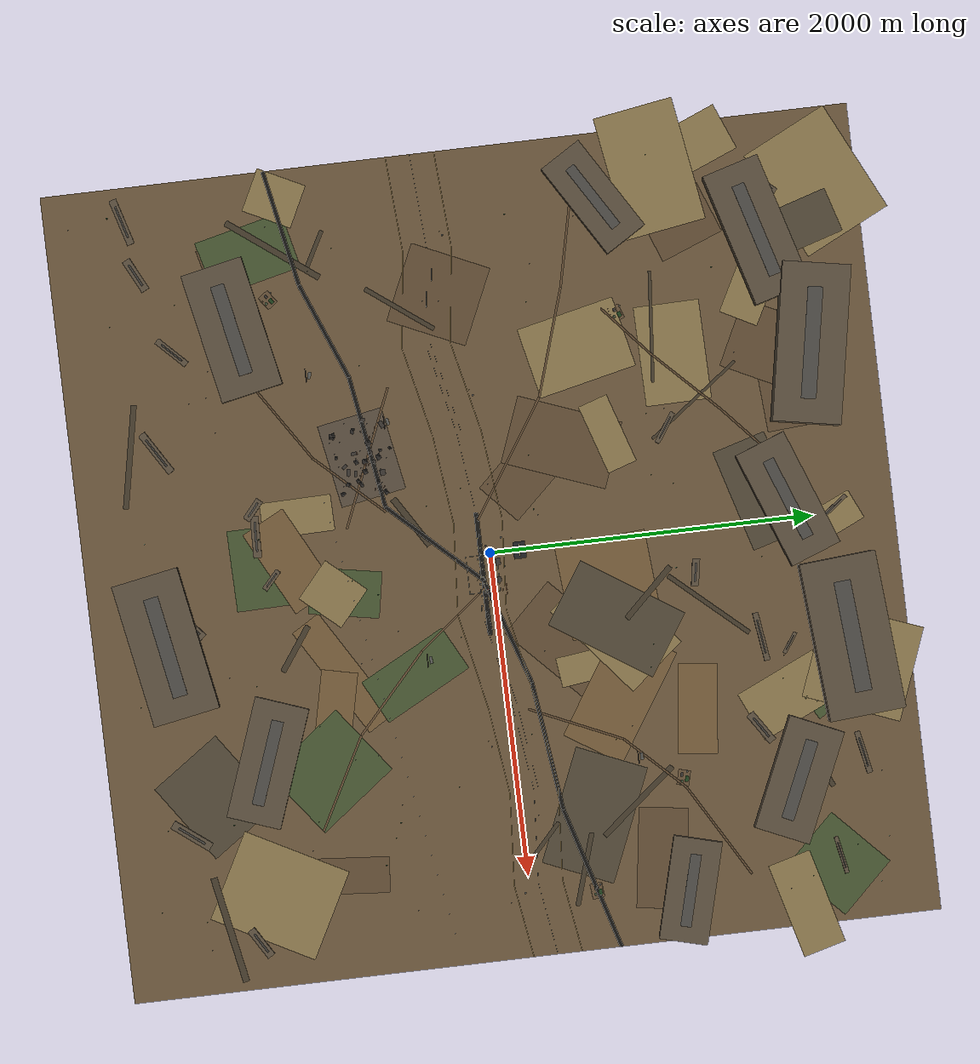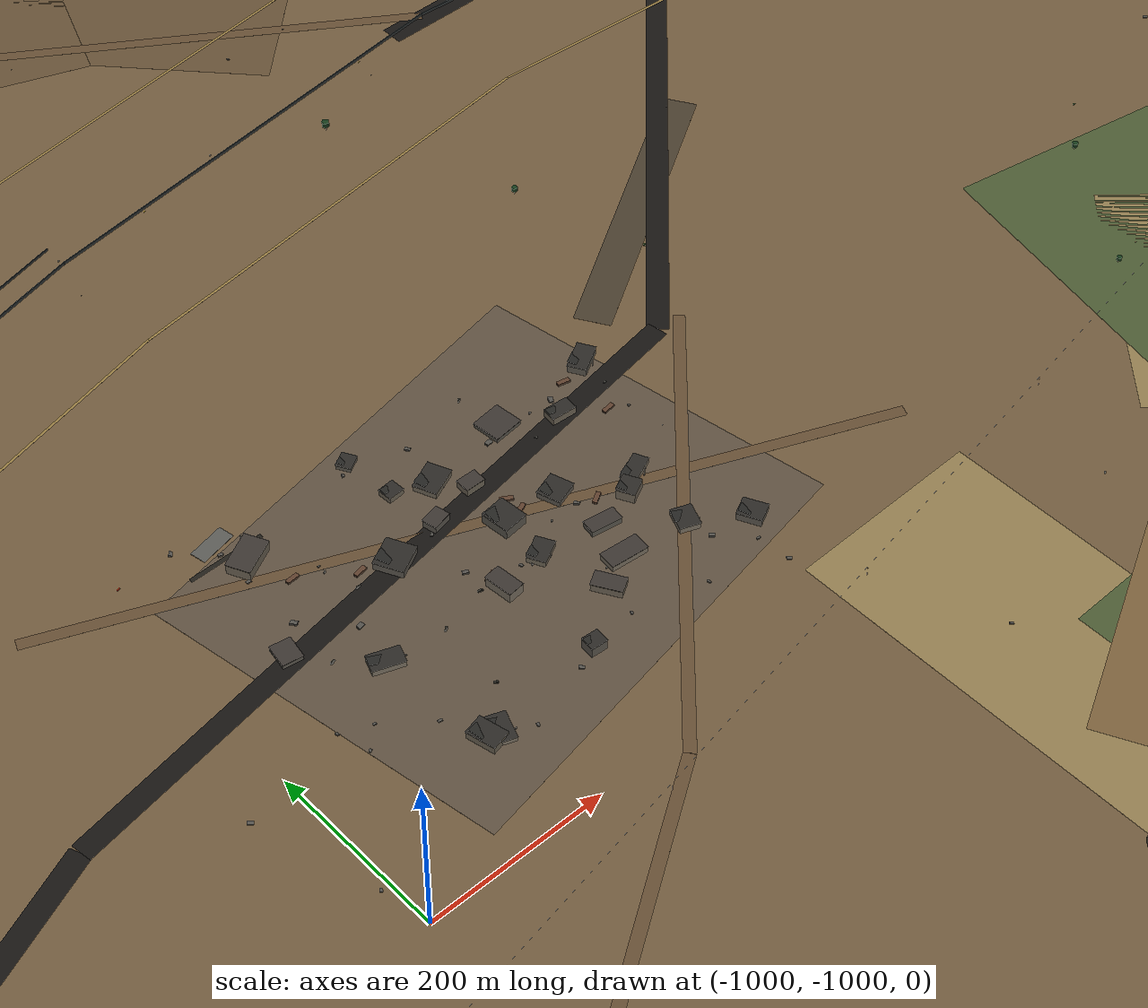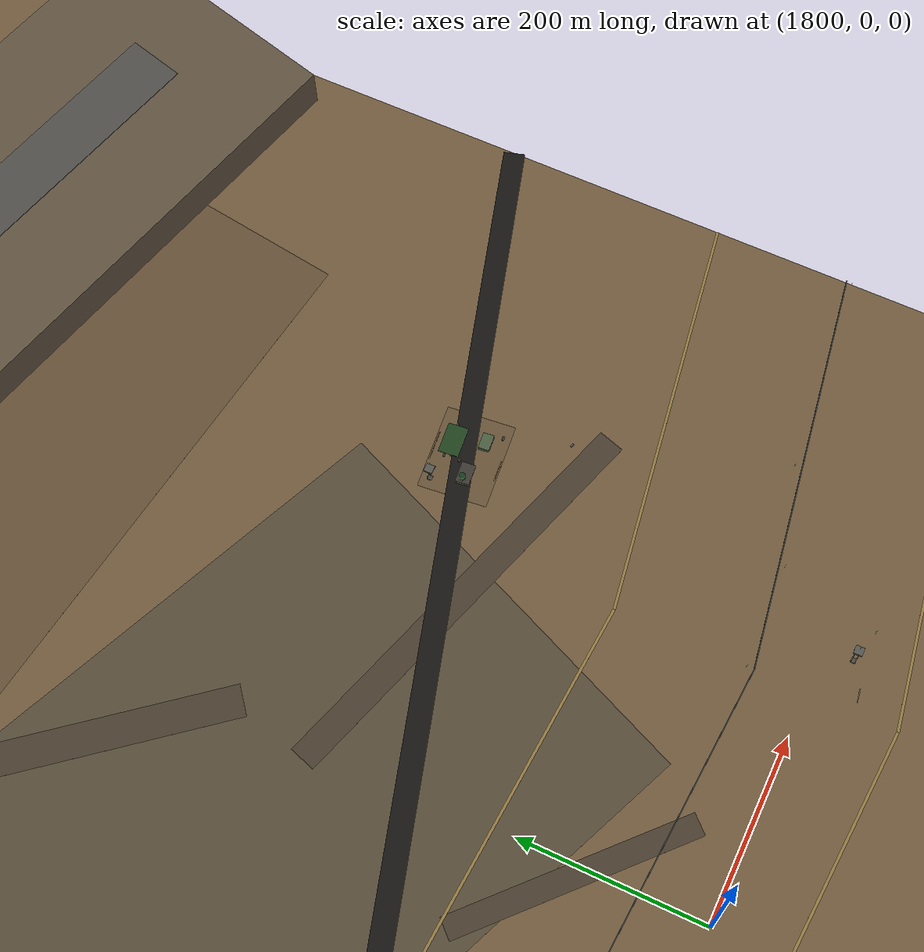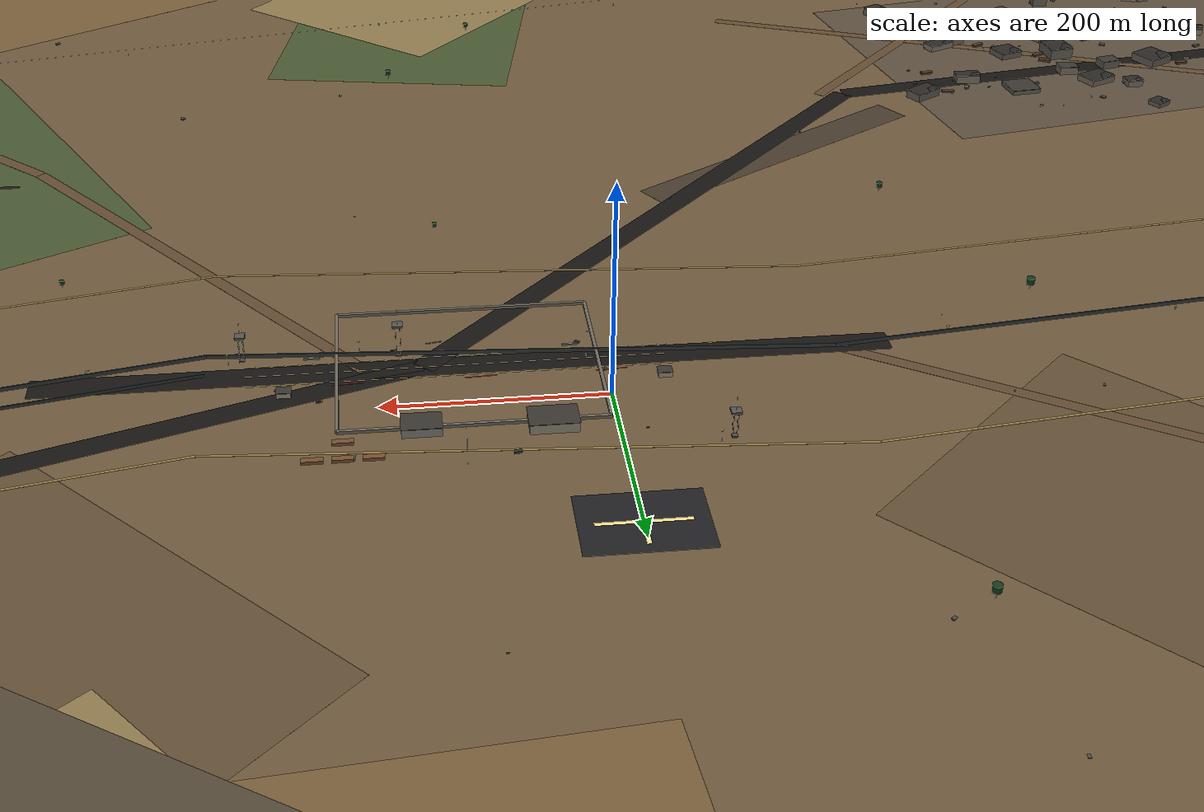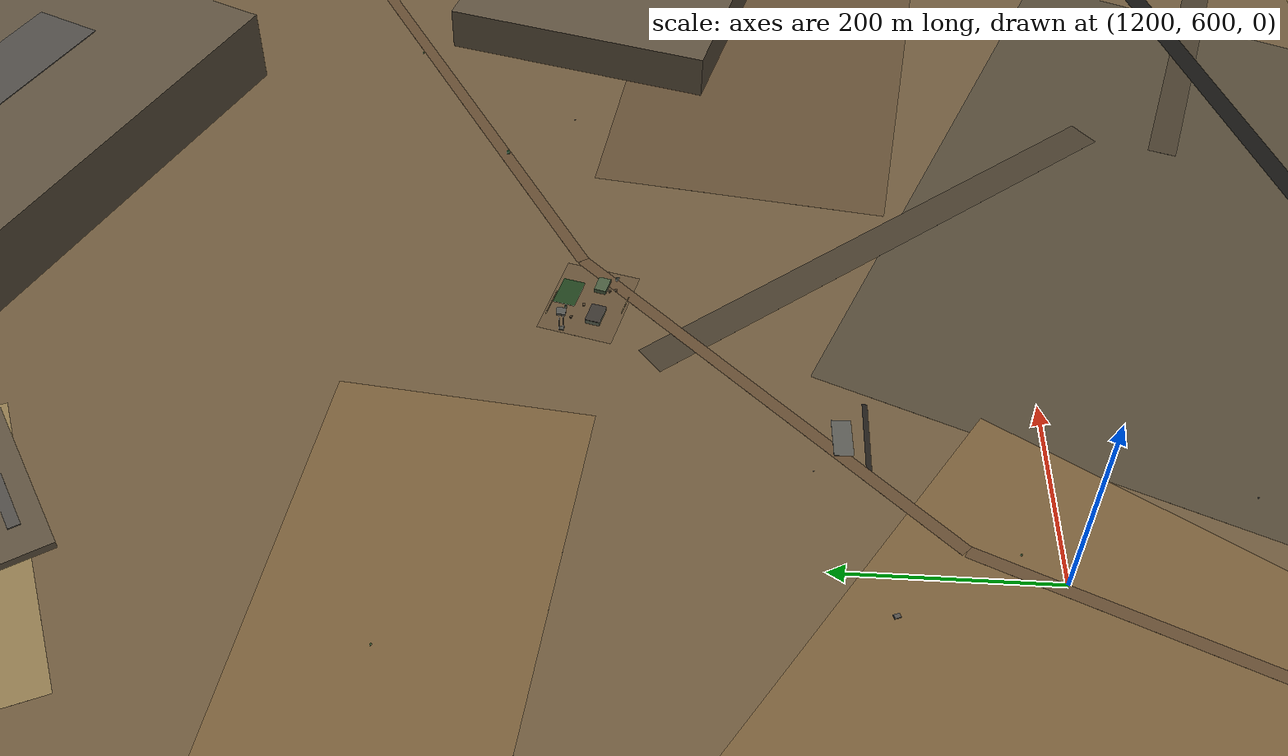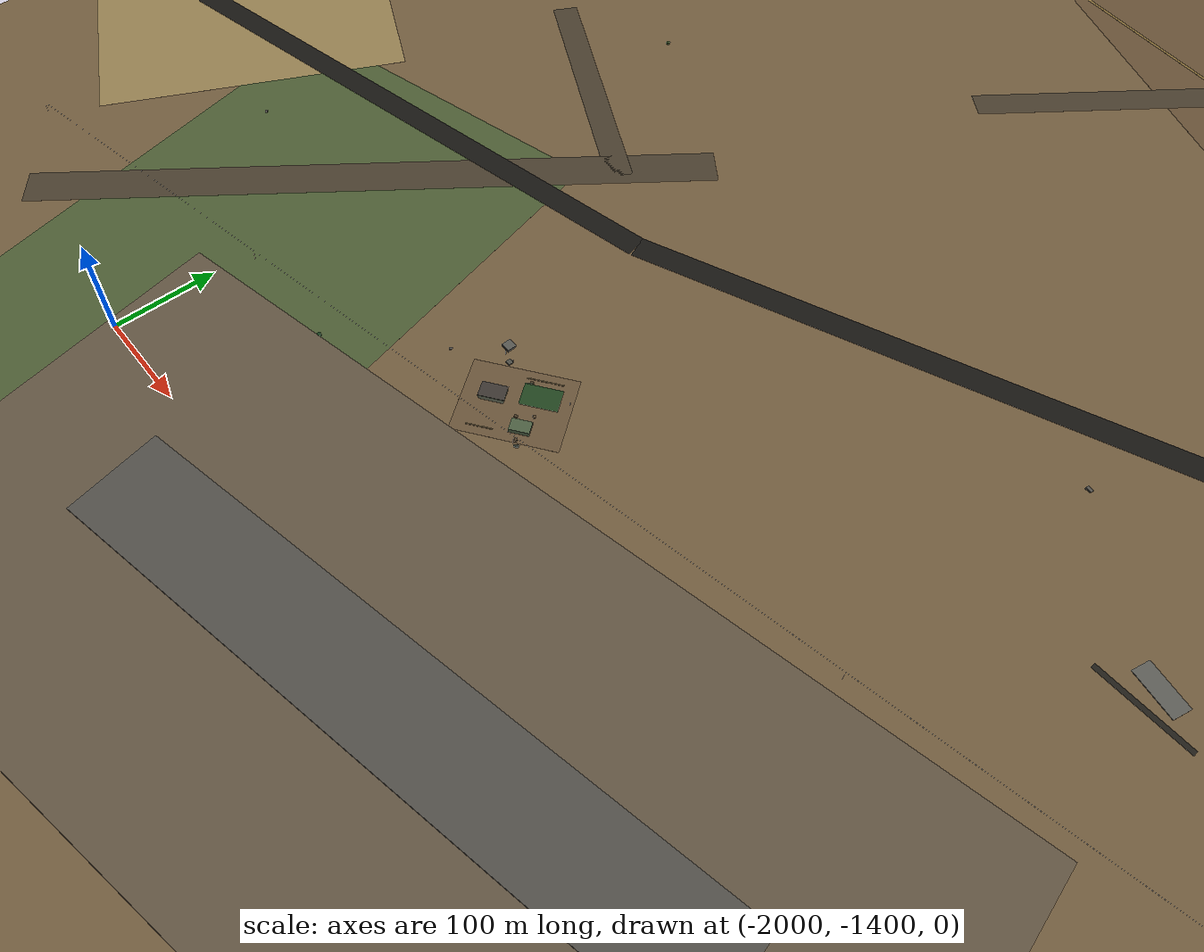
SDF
<?xml version='1.0' encoding='utf-8'?>
<sdf version="1.9">
  <world name="uav_5km_world">
    <plugin filename="gz-sim-physics-system" name="gz::sim::systems::Physics" />
    <plugin filename="gz-sim-user-commands-system" name="gz::sim::systems::UserCommands" />
    <plugin filename="gz-sim-scene-broadcaster-system" name="gz::sim::systems::SceneBroadcaster" />
    <plugin filename="gz-sim-imu-system" name="gz::sim::systems::Imu" />
    <plugin filename="gz-sim-air-pressure-system" name="gz::sim::systems::AirPressure" />
    <plugin filename="gz-sim-navsat-system" name="gz::sim::systems::NavSat" />
    <plugin filename="gz-sim-magnetometer-system" name="gz::sim::systems::Magnetometer" />
    <plugin filename="gz-sim-sensors-system" name="gz::sim::systems::Sensors">
      <render_engine>ogre2</render_engine>
    </plugin>
    <gui fullscreen="0">
      <plugin filename="ImageDisplay" name="AuDiSys Overhead Wide">
        <gz-gui>
          <property key="state" type="string">docked</property>
        </gz-gui>
        <topic>/world/uav_5km_world/model/audisys_camera_overhead_wide/link/link/sensor/camera/image</topic>
      </plugin>
      <plugin filename="ImageDisplay" name="AuDiSys UAV Base">
        <gz-gui>
          <property key="state" type="string">docked</property>
        </gz-gui>
        <topic>/world/uav_5km_world/model/audisys_camera_uav_base/link/link/sensor/camera/image</topic>
      </plugin>
      <plugin filename="ImageDisplay" name="AuDiSys Border Checkpoint">
        <gz-gui>
          <property key="state" type="string">docked</property>
        </gz-gui>
        <topic>/world/uav_5km_world/model/audisys_camera_border_checkpoint/link/link/sensor/camera/image</topic>
      </plugin>
      <plugin filename="ImageDisplay" name="AuDiSys Target Zone">
        <gz-gui>
          <property key="state" type="string">docked</property>
        </gz-gui>
        <topic>/world/uav_5km_world/model/audisys_camera_target_zone/link/link/sensor/camera/image</topic>
      </plugin>
    </gui>
    <physics type="ode">
      <max_step_size>0.004</max_step_size>
      <real_time_factor>1.0</real_time_factor>
      <real_time_update_rate>250</real_time_update_rate>
    </physics>
    <gravity>0 0 -9.8</gravity>
    <magnetic_field>6e-06 2.3e-05 -4.2e-05</magnetic_field>
    <atmosphere type="adiabatic" />
    <scene>
      <ambient>0.48 0.44 0.38 1</ambient>
      <background>0.82 0.70 0.56 1</background>
      <shadows>true</shadows>
      <grid>false</grid>
    </scene>
    <light name="late_afternoon_sun" type="directional">
      <pose>-1100 -1500 900 0.55 0.25 -0.55</pose>
      <cast_shadows>true</cast_shadows>
      <intensity>1.05</intensity>
      <direction>0.45 0.28 -0.85</direction>
      <diffuse>1.0 0.78 0.52 1</diffuse>
      <specular>0.35 0.28 0.18 1</specular>
    </light>
    <spherical_coordinates>
      <surface_model>EARTH_WGS84</surface_model>
      <world_frame_orientation>ENU</world_frame_orientation>
      <latitude_deg>47.397971057728974</latitude_deg>
      <longitude_deg>8.546163739800146</longitude_deg>
      <elevation>0</elevation>
    </spherical_coordinates>
    <model name="base_5km_semi_arid_ground">
      <static>true</static>
      <pose>0 0 -0.06 0 0 0</pose>
      <link name="link">
        <collision name="collision">
          <geometry>
            <box>
              <size>5000 5000 0.12</size>
            </box>
          </geometry>
        </collision>
        <visual name="visual">
          <geometry>
            <box>
              <size>5000 5000 0.12</size>
            </box>
          </geometry>
          <material>
            <ambient>0.42 0.34 0.23 1</ambient>
            <diffuse>0.42 0.34 0.23 1</diffuse>
            <specular>0.08 0.08 0.08 1</specular>
          </material>
        </visual>
      </link>
    </model>
    <model name="terrain_material_patch_00">
      <static>true</static>
      <pose>1102.1 1970.9 0.015 0 0 2.092</pose>
      <link name="link">
        <visual name="visual">
          <geometry>
            <box>
              <size>279.4 181.9 0.03</size>
            </box>
          </geometry>
          <material>
            <ambient>0.28 0.34 0.19 1</ambient>
            <diffuse>0.28 0.34 0.19 1</diffuse>
            <specular>0.08 0.08 0.08 1</specular>
          </material>
        </visual>
      </link>
    </model>
    <model name="terrain_material_patch_01">
      <static>true</static>
      <pose>-188.9 1685.7 0.015 0 0 0.282</pose>
      <link name="link">
        <visual name="visual">
          <geometry>
            <box>
              <size>652.2 341.4 0.03</size>
            </box>
          </geometry>
          <material>
            <ambient>0.32 0.28 0.21 1</ambient>
            <diffuse>0.32 0.28 0.21 1</diffuse>
            <specular>0.08 0.08 0.08 1</specular>
          </material>
        </visual>
      </link>
    </model>
    <model name="terrain_material_patch_02">
      <static>true</static>
      <pose>1219.0 -1136.1 0.015 0 0 0.647</pose>
      <link name="link">
        <visual name="visual">
          <geometry>
            <box>
              <size>503.0 572.0 0.03</size>
            </box>
          </geometry>
          <material>
            <ambient>0.28 0.34 0.19 1</ambient>
            <diffuse>0.28 0.34 0.19 1</diffuse>
            <specular>0.08 0.08 0.08 1</specular>
          </material>
        </visual>
      </link>
    </model>
    <model name="terrain_material_patch_03">
      <static>true</static>
      <pose>-1781.4 2087.7 0.015 0 0 -2.847</pose>
      <link name="link">
        <visual name="visual">
          <geometry>
            <box>
              <size>282.8 536.8 0.03</size>
            </box>
          </geometry>
          <material>
            <ambient>0.32 0.28 0.21 1</ambient>
            <diffuse>0.32 0.28 0.21 1</diffuse>
            <specular>0.08 0.08 0.08 1</specular>
          </material>
        </visual>
      </link>
    </model>
    <model name="terrain_material_patch_04">
      <static>true</static>
      <pose>135.7 -991.6 0.015 0 0 -2.288</pose>
      <link name="link">
        <visual name="visual">
          <geometry>
            <box>
              <size>316.0 286.3 0.03</size>
            </box>
          </geometry>
          <material>
            <ambient>0.55 0.47 0.30 1</ambient>
            <diffuse>0.55 0.47 0.30 1</diffuse>
            <specular>0.08 0.08 0.08 1</specular>
          </material>
        </visual>
      </link>
    </model>
    <model name="terrain_material_patch_05">
      <static>true</static>
      <pose>969.3 -1086.8 0.015 0 0 -0.218</pose>
      <link name="link">
        <visual name="visual">
          <geometry>
            <box>
              <size>731.4 225.0 0.03</size>
            </box>
          </geometry>
          <material>
            <ambient>0.46 0.36 0.22 1</ambient>
            <diffuse>0.46 0.36 0.22 1</diffuse>
            <specular>0.08 0.08 0.08 1</specular>
          </material>
        </visual>
      </link>
    </model>
    <model name="terrain_material_patch_06">
      <static>true</static>
      <pose>-2240.0 1247.9 0.015 0 0 -2.983</pose>
      <link name="link">
        <visual name="visual">
          <geometry>
            <box>
              <size>774.8 500.3 0.03</size>
            </box>
          </geometry>
          <material>
            <ambient>0.55 0.47 0.30 1</ambient>
            <diffuse>0.55 0.47 0.30 1</diffuse>
            <specular>0.08 0.08 0.08 1</specular>
          </material>
        </visual>
      </link>
    </model>
    <model name="terrain_material_patch_07">
      <static>true</static>
      <pose>490.9 724.6 0.015 0 0 -2.152</pose>
      <link name="link">
        <visual name="visual">
          <geometry>
            <box>
              <size>718.5 442.0 0.03</size>
            </box>
          </geometry>
          <material>
            <ambient>0.32 0.28 0.21 1</ambient>
            <diffuse>0.32 0.28 0.21 1</diffuse>
            <specular>0.08 0.08 0.08 1</specular>
          </material>
        </visual>
      </link>
    </model>
    <model name="terrain_material_patch_08">
      <static>true</static>
      <pose>-1497.6 1808.9 0.015 0 0 -0.485</pose>
      <link name="link">
        <visual name="visual">
          <geometry>
            <box>
              <size>539.7 246.4 0.03</size>
            </box>
          </geometry>
          <material>
            <ambient>0.55 0.47 0.30 1</ambient>
            <diffuse>0.55 0.47 0.30 1</diffuse>
            <specular>0.08 0.08 0.08 1</specular>
          </material>
        </visual>
      </link>
    </model>
    <model name="terrain_material_patch_09">
      <static>true</static>
      <pose>277.8 699.4 0.015 0 0 -3.059</pose>
      <link name="link">
        <visual name="visual">
          <geometry>
            <box>
              <size>587.5 564.9 0.03</size>
            </box>
          </geometry>
          <material>
            <ambient>0.46 0.36 0.22 1</ambient>
            <diffuse>0.46 0.36 0.22 1</diffuse>
            <specular>0.08 0.08 0.08 1</specular>
          </material>
        </visual>
      </link>
    </model>
    <model name="terrain_material_patch_10">
      <static>true</static>
      <pose>1676.2 449.7 0.015 0 0 -0.402</pose>
      <link name="link">
        <visual name="visual">
          <geometry>
            <box>
              <size>742.0 459.8 0.03</size>
            </box>
          </geometry>
          <material>
            <ambient>0.32 0.28 0.21 1</ambient>
            <diffuse>0.32 0.28 0.21 1</diffuse>
            <specular>0.08 0.08 0.08 1</specular>
          </material>
        </visual>
      </link>
    </model>
    <model name="terrain_material_patch_11">
      <static>true</static>
      <pose>691.7 -547.4 0.015 0 0 2.055</pose>
      <link name="link">
        <visual name="visual">
          <geometry>
            <box>
              <size>597.2 298.8 0.03</size>
            </box>
          </geometry>
          <material>
            <ambient>0.28 0.34 0.19 1</ambient>
            <diffuse>0.28 0.34 0.19 1</diffuse>
            <specular>0.08 0.08 0.08 1</specular>
          </material>
        </visual>
      </link>
    </model>
    <model name="terrain_material_patch_12">
      <static>true</static>
      <pose>-1890.6 1395.5 0.015 0 0 -1.203</pose>
      <link name="link">
        <visual name="visual">
          <geometry>
            <box>
              <size>408.4 334.8 0.03</size>
            </box>
          </geometry>
          <material>
            <ambient>0.38 0.30 0.20 1</ambient>
            <diffuse>0.38 0.30 0.20 1</diffuse>
            <specular>0.08 0.08 0.08 1</specular>
          </material>
        </visual>
      </link>
    </model>
    <model name="terrain_material_patch_13">
      <static>true</static>
      <pose>-2044.5 2256.2 0.015 0 0 0.455</pose>
      <link name="link">
        <visual name="visual">
          <geometry>
            <box>
              <size>735.5 577.6 0.03</size>
            </box>
          </geometry>
          <material>
            <ambient>0.55 0.47 0.30 1</ambient>
            <diffuse>0.55 0.47 0.30 1</diffuse>
            <specular>0.08 0.08 0.08 1</specular>
          </material>
        </visual>
      </link>
    </model>
    <model name="terrain_material_patch_14">
      <static>true</static>
      <pose>-1096.7 1256.3 0.015 0 0 -3.125</pose>
      <link name="link">
        <visual name="visual">
          <geometry>
            <box>
              <size>615.1 405.4 0.03</size>
            </box>
          </geometry>
          <material>
            <ambient>0.55 0.47 0.30 1</ambient>
            <diffuse>0.55 0.47 0.30 1</diffuse>
            <specular>0.08 0.08 0.08 1</specular>
          </material>
        </visual>
      </link>
    </model>
    <model name="terrain_material_patch_15">
      <static>true</static>
      <pose>-2329.3 -1070.7 0.015 0 0 -2.030</pose>
      <link name="link">
        <visual name="visual">
          <geometry>
            <box>
              <size>316.2 277.2 0.03</size>
            </box>
          </geometry>
          <material>
            <ambient>0.55 0.47 0.30 1</ambient>
            <diffuse>0.55 0.47 0.30 1</diffuse>
            <specular>0.08 0.08 0.08 1</specular>
          </material>
        </visual>
      </link>
    </model>
    <model name="terrain_material_patch_16">
      <static>true</static>
      <pose>-96.7 -1237.8 0.015 0 0 -2.661</pose>
      <link name="link">
        <visual name="visual">
          <geometry>
            <box>
              <size>583.7 295.7 0.03</size>
            </box>
          </geometry>
          <material>
            <ambient>0.46 0.36 0.22 1</ambient>
            <diffuse>0.46 0.36 0.22 1</diffuse>
            <specular>0.08 0.08 0.08 1</specular>
          </material>
        </visual>
      </link>
    </model>
    <model name="terrain_material_patch_17">
      <static>true</static>
      <pose>1941.7 -1534.3 0.015 0 0 -2.058</pose>
      <link name="link">
        <visual name="visual">
          <geometry>
            <box>
              <size>689.9 581.4 0.03</size>
            </box>
          </geometry>
          <material>
            <ambient>0.55 0.47 0.30 1</ambient>
            <diffuse>0.55 0.47 0.30 1</diffuse>
            <specular>0.08 0.08 0.08 1</specular>
          </material>
        </visual>
      </link>
    </model>
    <model name="terrain_material_patch_18">
      <static>true</static>
      <pose>537.6 713.7 0.015 0 0 -2.453</pose>
      <link name="link">
        <visual name="visual">
          <geometry>
            <box>
              <size>709.1 429.0 0.03</size>
            </box>
          </geometry>
          <material>
            <ambient>0.55 0.47 0.30 1</ambient>
            <diffuse>0.55 0.47 0.30 1</diffuse>
            <specular>0.08 0.08 0.08 1</specular>
          </material>
        </visual>
      </link>
    </model>
    <model name="terrain_material_patch_19">
      <static>true</static>
      <pose>-647.4 800.8 0.015 0 0 0.313</pose>
      <link name="link">
        <visual name="visual">
          <geometry>
            <box>
              <size>446.2 188.5 0.03</size>
            </box>
          </geometry>
          <material>
            <ambient>0.55 0.47 0.30 1</ambient>
            <diffuse>0.55 0.47 0.30 1</diffuse>
            <specular>0.08 0.08 0.08 1</specular>
          </material>
        </visual>
      </link>
    </model>
    <model name="terrain_material_patch_20">
      <static>true</static>
      <pose>-1046.5 1910.8 0.015 0 0 2.687</pose>
      <link name="link">
        <visual name="visual">
          <geometry>
            <box>
              <size>437.8 617.2 0.03</size>
            </box>
          </geometry>
          <material>
            <ambient>0.38 0.30 0.20 1</ambient>
            <diffuse>0.38 0.30 0.20 1</diffuse>
            <specular>0.08 0.08 0.08 1</specular>
          </material>
        </visual>
      </link>
    </model>
    <model name="terrain_material_patch_21">
      <static>true</static>
      <pose>-628.7 513.9 0.015 0 0 1.208</pose>
      <link name="link">
        <visual name="visual">
          <geometry>
            <box>
              <size>663.2 424.3 0.03</size>
            </box>
          </geometry>
          <material>
            <ambient>0.38 0.30 0.20 1</ambient>
            <diffuse>0.38 0.30 0.20 1</diffuse>
            <specular>0.08 0.08 0.08 1</specular>
          </material>
        </visual>
      </link>
    </model>
    <model name="terrain_material_patch_22">
      <static>true</static>
      <pose>2370.0 1683.4 0.015 0 0 1.833</pose>
      <link name="link">
        <visual name="visual">
          <geometry>
            <box>
              <size>271.0 600.8 0.03</size>
            </box>
          </geometry>
          <material>
            <ambient>0.55 0.47 0.30 1</ambient>
            <diffuse>0.55 0.47 0.30 1</diffuse>
            <specular>0.08 0.08 0.08 1</specular>
          </material>
        </visual>
      </link>
    </model>
    <model name="terrain_material_patch_23">
      <static>true</static>
      <pose>136.5 -916.8 0.015 0 0 -1.750</pose>
      <link name="link">
        <visual name="visual">
          <geometry>
            <box>
              <size>437.0 287.4 0.03</size>
            </box>
          </geometry>
          <material>
            <ambient>0.28 0.34 0.19 1</ambient>
            <diffuse>0.28 0.34 0.19 1</diffuse>
            <specular>0.08 0.08 0.08 1</specular>
          </material>
        </visual>
      </link>
    </model>
    <model name="terrain_material_patch_24">
      <static>true</static>
      <pose>-1622.4 -133.0 0.015 0 0 2.716</pose>
      <link name="link">
        <visual name="visual">
          <geometry>
            <box>
              <size>501.9 508.6 0.03</size>
            </box>
          </geometry>
          <material>
            <ambient>0.38 0.30 0.20 1</ambient>
            <diffuse>0.38 0.30 0.20 1</diffuse>
            <specular>0.08 0.08 0.08 1</specular>
          </material>
        </visual>
      </link>
    </model>
    <model name="terrain_material_patch_25">
      <static>true</static>
      <pose>931.5 2199.7 0.015 0 0 1.204</pose>
      <link name="link">
        <visual name="visual">
          <geometry>
            <box>
              <size>622.6 596.0 0.03</size>
            </box>
          </geometry>
          <material>
            <ambient>0.55 0.47 0.30 1</ambient>
            <diffuse>0.55 0.47 0.30 1</diffuse>
            <specular>0.08 0.08 0.08 1</specular>
          </material>
        </visual>
      </link>
    </model>
    <model name="terrain_material_patch_26">
      <static>true</static>
      <pose>626.6 -982.7 0.015 0 0 -2.595</pose>
      <link name="link">
        <visual name="visual">
          <geometry>
            <box>
              <size>774.4 202.0 0.03</size>
            </box>
          </geometry>
          <material>
            <ambient>0.46 0.36 0.22 1</ambient>
            <diffuse>0.46 0.36 0.22 1</diffuse>
            <specular>0.08 0.08 0.08 1</specular>
          </material>
        </visual>
      </link>
    </model>
    <model name="terrain_material_patch_27">
      <static>true</static>
      <pose>953.3 691.8 0.015 0 0 2.565</pose>
      <link name="link">
        <visual name="visual">
          <geometry>
            <box>
              <size>762.5 403.1 0.03</size>
            </box>
          </geometry>
          <material>
            <ambient>0.46 0.36 0.22 1</ambient>
            <diffuse>0.46 0.36 0.22 1</diffuse>
            <specular>0.08 0.08 0.08 1</specular>
          </material>
        </visual>
      </link>
    </model>
    <model name="terrain_material_patch_28">
      <static>true</static>
      <pose>-1198.0 672.6 0.015 0 0 0.219</pose>
      <link name="link">
        <visual name="visual">
          <geometry>
            <box>
              <size>445.7 618.2 0.03</size>
            </box>
          </geometry>
          <material>
            <ambient>0.55 0.47 0.30 1</ambient>
            <diffuse>0.55 0.47 0.30 1</diffuse>
            <specular>0.08 0.08 0.08 1</specular>
          </material>
        </visual>
      </link>
    </model>
    <model name="terrain_material_patch_29">
      <static>true</static>
      <pose>-523.3 332.5 0.015 0 0 -0.823</pose>
      <link name="link">
        <visual name="visual">
          <geometry>
            <box>
              <size>675.4 311.7 0.03</size>
            </box>
          </geometry>
          <material>
            <ambient>0.38 0.30 0.20 1</ambient>
            <diffuse>0.38 0.30 0.20 1</diffuse>
            <specular>0.08 0.08 0.08 1</specular>
          </material>
        </visual>
      </link>
    </model>
    <model name="terrain_material_patch_30">
      <static>true</static>
      <pose>-2351.2 1506.9 0.015 0 0 0.387</pose>
      <link name="link">
        <visual name="visual">
          <geometry>
            <box>
              <size>304.7 502.8 0.03</size>
            </box>
          </geometry>
          <material>
            <ambient>0.55 0.47 0.30 1</ambient>
            <diffuse>0.55 0.47 0.30 1</diffuse>
            <specular>0.08 0.08 0.08 1</specular>
          </material>
        </visual>
      </link>
    </model>
    <model name="terrain_material_patch_31">
      <static>true</static>
      <pose>-880.7 1937.3 0.015 0 0 -3.072</pose>
      <link name="link">
        <visual name="visual">
          <geometry>
            <box>
              <size>653.3 351.3 0.03</size>
            </box>
          </geometry>
          <material>
            <ambient>0.38 0.30 0.20 1</ambient>
            <diffuse>0.38 0.30 0.20 1</diffuse>
            <specular>0.08 0.08 0.08 1</specular>
          </material>
        </visual>
      </link>
    </model>
    <model name="terrain_material_patch_32">
      <static>true</static>
      <pose>1295.5 -1856.0 0.015 0 0 -2.533</pose>
      <link name="link">
        <visual name="visual">
          <geometry>
            <box>
              <size>571.3 499.3 0.03</size>
            </box>
          </geometry>
          <material>
            <ambient>0.32 0.28 0.21 1</ambient>
            <diffuse>0.32 0.28 0.21 1</diffuse>
            <specular>0.08 0.08 0.08 1</specular>
          </material>
        </visual>
      </link>
    </model>
    <model name="terrain_material_patch_33">
      <static>true</static>
      <pose>1099.7 1155.8 0.015 0 0 3.028</pose>
      <link name="link">
        <visual name="visual">
          <geometry>
            <box>
              <size>555.9 242.7 0.03</size>
            </box>
          </geometry>
          <material>
            <ambient>0.46 0.36 0.22 1</ambient>
            <diffuse>0.46 0.36 0.22 1</diffuse>
            <specular>0.08 0.08 0.08 1</specular>
          </material>
        </visual>
      </link>
    </model>
    <model name="terrain_material_patch_34">
      <static>true</static>
      <pose>2147.4 1904.9 0.015 0 0 2.332</pose>
      <link name="link">
        <visual name="visual">
          <geometry>
            <box>
              <size>431.8 469.2 0.03</size>
            </box>
          </geometry>
          <material>
            <ambient>0.28 0.34 0.19 1</ambient>
            <diffuse>0.28 0.34 0.19 1</diffuse>
            <specular>0.08 0.08 0.08 1</specular>
          </material>
        </visual>
      </link>
    </model>
    <model name="terrain_material_patch_35">
      <static>true</static>
      <pose>750.6 583.6 0.015 0 0 1.694</pose>
      <link name="link">
        <visual name="visual">
          <geometry>
            <box>
              <size>504.5 185.2 0.03</size>
            </box>
          </geometry>
          <material>
            <ambient>0.55 0.47 0.30 1</ambient>
            <diffuse>0.55 0.47 0.30 1</diffuse>
            <specular>0.08 0.08 0.08 1</specular>
          </material>
        </visual>
      </link>
    </model>
    <model name="terrain_material_patch_36">
      <static>true</static>
      <pose>-363.4 -1157.9 0.015 0 0 -1.552</pose>
      <link name="link">
        <visual name="visual">
          <geometry>
            <box>
              <size>442.1 223.1 0.03</size>
            </box>
          </geometry>
          <material>
            <ambient>0.55 0.47 0.30 1</ambient>
            <diffuse>0.55 0.47 0.30 1</diffuse>
            <specular>0.08 0.08 0.08 1</specular>
          </material>
        </visual>
      </link>
    </model>
    <model name="terrain_material_patch_37">
      <static>true</static>
      <pose>1863.6 -1176.2 0.015 0 0 1.488</pose>
      <link name="link">
        <visual name="visual">
          <geometry>
            <box>
              <size>659.6 221.8 0.03</size>
            </box>
          </geometry>
          <material>
            <ambient>0.38 0.30 0.20 1</ambient>
            <diffuse>0.38 0.30 0.20 1</diffuse>
            <specular>0.08 0.08 0.08 1</specular>
          </material>
        </visual>
      </link>
    </model>
    <model name="terrain_material_patch_38">
      <static>true</static>
      <pose>1986.5 832.6 0.015 0 0 3.003</pose>
      <link name="link">
        <visual name="visual">
          <geometry>
            <box>
              <size>621.1 305.7 0.03</size>
            </box>
          </geometry>
          <material>
            <ambient>0.38 0.30 0.20 1</ambient>
            <diffuse>0.38 0.30 0.20 1</diffuse>
            <specular>0.08 0.08 0.08 1</specular>
          </material>
        </visual>
      </link>
    </model>
    <model name="terrain_material_patch_39">
      <static>true</static>
      <pose>606.9 421.3 0.015 0 0 0.767</pose>
      <link name="link">
        <visual name="visual">
          <geometry>
            <box>
              <size>694.7 413.7 0.03</size>
            </box>
          </geometry>
          <material>
            <ambient>0.38 0.30 0.20 1</ambient>
            <diffuse>0.38 0.30 0.20 1</diffuse>
            <specular>0.08 0.08 0.08 1</specular>
          </material>
        </visual>
      </link>
    </model>
    <model name="terrain_material_patch_40">
      <static>true</static>
      <pose>-77.3 -1371.5 0.015 0 0 0.019</pose>
      <link name="link">
        <visual name="visual">
          <geometry>
            <box>
              <size>499.9 446.1 0.03</size>
            </box>
          </geometry>
          <material>
            <ambient>0.28 0.34 0.19 1</ambient>
            <diffuse>0.28 0.34 0.19 1</diffuse>
            <specular>0.08 0.08 0.08 1</specular>
          </material>
        </visual>
      </link>
    </model>
    <model name="terrain_material_patch_41">
      <static>true</static>
      <pose>13.1 2149.4 0.015 0 0 1.999</pose>
      <link name="link">
        <visual name="visual">
          <geometry>
            <box>
              <size>266.9 196.7 0.03</size>
            </box>
          </geometry>
          <material>
            <ambient>0.55 0.47 0.30 1</ambient>
            <diffuse>0.55 0.47 0.30 1</diffuse>
            <specular>0.08 0.08 0.08 1</specular>
          </material>
        </visual>
      </link>
    </model>
    <model name="terrain_material_patch_42">
      <static>true</static>
      <pose>1082.0 1721.5 0.015 0 0 0.425</pose>
      <link name="link">
        <visual name="visual">
          <geometry>
            <box>
              <size>328.1 535.8 0.03</size>
            </box>
          </geometry>
          <material>
            <ambient>0.55 0.47 0.30 1</ambient>
            <diffuse>0.55 0.47 0.30 1</diffuse>
            <specular>0.08 0.08 0.08 1</specular>
          </material>
        </visual>
      </link>
    </model>
    <model name="terrain_material_patch_43">
      <static>true</static>
      <pose>-1999.0 -1272.0 0.015 0 0 0.229</pose>
      <link name="link">
        <visual name="visual">
          <geometry>
            <box>
              <size>356.6 565.6 0.03</size>
            </box>
          </geometry>
          <material>
            <ambient>0.28 0.34 0.19 1</ambient>
            <diffuse>0.28 0.34 0.19 1</diffuse>
            <specular>0.08 0.08 0.08 1</specular>
          </material>
        </visual>
      </link>
    </model>
    <model name="low_poly_hill_ridge_00">
      <static>true</static>
      <pose>-1780.0 1850.0 43.9 0 0 0.280</pose>
      <link name="link">
        <visual name="visual">
          <geometry>
            <box>
              <size>850.0 360.0 88.0</size>
            </box>
          </geometry>
          <material>
            <ambient>0.36 0.31 0.24 1</ambient>
            <diffuse>0.36 0.31 0.24 1</diffuse>
            <specular>0.08 0.08 0.08 1</specular>
          </material>
        </visual>
      </link>
    </model>
    <model name="low_poly_hill_ridge_00_rocky_crest">
      <static>true</static>
      <pose>-1780.00 1850.00 88.30 0 0 0.2800</pose>
      <link name="link">
        <visual name="visual">
          <geometry>
            <box>
              <size>595.00 79.20 1.20</size>
            </box>
          </geometry>
          <material>
            <ambient>0.30 0.29 0.27 1</ambient>
            <diffuse>0.30 0.29 0.27 1</diffuse>
            <specular>0.08 0.08 0.08 1</specular>
          </material>
        </visual>
      </link>
    </model>
    <model name="low_poly_hill_ridge_01">
      <static>true</static>
      <pose>-1050.0 2100.0 67.3 0 0 -0.180</pose>
      <link name="link">
        <visual name="visual">
          <geometry>
            <box>
              <size>980.0 420.0 135.0</size>
            </box>
          </geometry>
          <material>
            <ambient>0.36 0.31 0.24 1</ambient>
            <diffuse>0.36 0.31 0.24 1</diffuse>
            <specular>0.08 0.08 0.08 1</specular>
          </material>
        </visual>
      </link>
    </model>
    <model name="low_poly_hill_ridge_01_rocky_crest">
      <static>true</static>
      <pose>-1050.00 2100.00 135.30 0 0 -0.1800</pose>
      <link name="link">
        <visual name="visual">
          <geometry>
            <box>
              <size>686.00 92.40 1.20</size>
            </box>
          </geometry>
          <material>
            <ambient>0.30 0.29 0.27 1</ambient>
            <diffuse>0.30 0.29 0.27 1</diffuse>
            <specular>0.08 0.08 0.08 1</specular>
          </material>
        </visual>
      </link>
    </model>
    <model name="low_poly_hill_ridge_02">
      <static>true</static>
      <pose>-120.0 1850.0 35.9 0 0 0.360</pose>
      <link name="link">
        <visual name="visual">
          <geometry>
            <box>
              <size>760.0 330.0 72.0</size>
            </box>
          </geometry>
          <material>
            <ambient>0.36 0.31 0.24 1</ambient>
            <diffuse>0.36 0.31 0.24 1</diffuse>
            <specular>0.08 0.08 0.08 1</specular>
          </material>
        </visual>
      </link>
    </model>
    <model name="low_poly_hill_ridge_02_rocky_crest">
      <static>true</static>
      <pose>-120.00 1850.00 72.30 0 0 0.3600</pose>
      <link name="link">
        <visual name="visual">
          <geometry>
            <box>
              <size>532.00 72.60 1.20</size>
            </box>
          </geometry>
          <material>
            <ambient>0.30 0.29 0.27 1</ambient>
            <diffuse>0.30 0.29 0.27 1</diffuse>
            <specular>0.08 0.08 0.08 1</specular>
          </material>
        </visual>
      </link>
    </model>
    <model name="low_poly_hill_ridge_03">
      <static>true</static>
      <pose>760.0 2140.0 59.9 0 0 0.080</pose>
      <link name="link">
        <visual name="visual">
          <geometry>
            <box>
              <size>980.0 470.0 120.0</size>
            </box>
          </geometry>
          <material>
            <ambient>0.36 0.31 0.24 1</ambient>
            <diffuse>0.36 0.31 0.24 1</diffuse>
            <specular>0.08 0.08 0.08 1</specular>
          </material>
        </visual>
      </link>
    </model>
    <model name="low_poly_hill_ridge_03_rocky_crest">
      <static>true</static>
      <pose>760.00 2140.00 120.30 0 0 0.0800</pose>
      <link name="link">
        <visual name="visual">
          <geometry>
            <box>
              <size>686.00 103.40 1.20</size>
            </box>
          </geometry>
          <material>
            <ambient>0.30 0.29 0.27 1</ambient>
            <diffuse>0.30 0.29 0.27 1</diffuse>
            <specular>0.08 0.08 0.08 1</specular>
          </material>
        </visual>
      </link>
    </model>
    <model name="low_poly_hill_ridge_04">
      <static>true</static>
      <pose>1600.0 1720.0 40.9 0 0 -0.420</pose>
      <link name="link">
        <visual name="visual">
          <geometry>
            <box>
              <size>720.0 350.0 82.0</size>
            </box>
          </geometry>
          <material>
            <ambient>0.36 0.31 0.24 1</ambient>
            <diffuse>0.36 0.31 0.24 1</diffuse>
            <specular>0.08 0.08 0.08 1</specular>
          </material>
        </visual>
      </link>
    </model>
    <model name="low_poly_hill_ridge_04_rocky_crest">
      <static>true</static>
      <pose>1600.00 1720.00 82.30 0 0 -0.4200</pose>
      <link name="link">
        <visual name="visual">
          <geometry>
            <box>
              <size>504.00 77.00 1.20</size>
            </box>
          </geometry>
          <material>
            <ambient>0.30 0.29 0.27 1</ambient>
            <diffuse>0.30 0.29 0.27 1</diffuse>
            <specular>0.08 0.08 0.08 1</specular>
          </material>
        </visual>
      </link>
    </model>
    <model name="low_poly_hill_ridge_05">
      <static>true</static>
      <pose>-2100.0 880.0 27.4 0 0 0.550</pose>
      <link name="link">
        <visual name="visual">
          <geometry>
            <box>
              <size>660.0 290.0 55.0</size>
            </box>
          </geometry>
          <material>
            <ambient>0.36 0.31 0.24 1</ambient>
            <diffuse>0.36 0.31 0.24 1</diffuse>
            <specular>0.08 0.08 0.08 1</specular>
          </material>
        </visual>
      </link>
    </model>
    <model name="low_poly_hill_ridge_05_rocky_crest">
      <static>true</static>
      <pose>-2100.00 880.00 55.30 0 0 0.5500</pose>
      <link name="link">
        <visual name="visual">
          <geometry>
            <box>
              <size>462.00 63.80 1.20</size>
            </box>
          </geometry>
          <material>
            <ambient>0.30 0.29 0.27 1</ambient>
            <diffuse>0.30 0.29 0.27 1</diffuse>
            <specular>0.08 0.08 0.08 1</specular>
          </material>
        </visual>
      </link>
    </model>
    <model name="low_poly_hill_ridge_06">
      <static>true</static>
      <pose>2200.0 980.0 23.9 0 0 -0.260</pose>
      <link name="link">
        <visual name="visual">
          <geometry>
            <box>
              <size>640.0 300.0 48.0</size>
            </box>
          </geometry>
          <material>
            <ambient>0.36 0.31 0.24 1</ambient>
            <diffuse>0.36 0.31 0.24 1</diffuse>
            <specular>0.08 0.08 0.08 1</specular>
          </material>
        </visual>
      </link>
    </model>
    <model name="low_poly_hill_ridge_06_rocky_crest">
      <static>true</static>
      <pose>2200.00 980.00 48.30 0 0 -0.2600</pose>
      <link name="link">
        <visual name="visual">
          <geometry>
            <box>
              <size>448.00 66.00 1.20</size>
            </box>
          </geometry>
          <material>
            <ambient>0.30 0.29 0.27 1</ambient>
            <diffuse>0.30 0.29 0.27 1</diffuse>
            <specular>0.08 0.08 0.08 1</specular>
          </material>
        </visual>
      </link>
    </model>
    <model name="low_poly_hill_ridge_07">
      <static>true</static>
      <pose>-1550.0 -1420.0 20.9 0 0 0.200</pose>
      <link name="link">
        <visual name="visual">
          <geometry>
            <box>
              <size>820.0 390.0 42.0</size>
            </box>
          </geometry>
          <material>
            <ambient>0.36 0.31 0.24 1</ambient>
            <diffuse>0.36 0.31 0.24 1</diffuse>
            <specular>0.08 0.08 0.08 1</specular>
          </material>
        </visual>
      </link>
    </model>
    <model name="low_poly_hill_ridge_07_rocky_crest">
      <static>true</static>
      <pose>-1550.00 -1420.00 42.30 0 0 0.2000</pose>
      <link name="link">
        <visual name="visual">
          <geometry>
            <box>
              <size>574.00 85.80 1.20</size>
            </box>
          </geometry>
          <material>
            <ambient>0.30 0.29 0.27 1</ambient>
            <diffuse>0.30 0.29 0.27 1</diffuse>
            <specular>0.08 0.08 0.08 1</specular>
          </material>
        </visual>
      </link>
    </model>
    <model name="low_poly_hill_ridge_08">
      <static>true</static>
      <pose>1120.0 -1510.0 17.9 0 0 -0.350</pose>
      <link name="link">
        <visual name="visual">
          <geometry>
            <box>
              <size>760.0 340.0 36.0</size>
            </box>
          </geometry>
          <material>
            <ambient>0.36 0.31 0.24 1</ambient>
            <diffuse>0.36 0.31 0.24 1</diffuse>
            <specular>0.08 0.08 0.08 1</specular>
          </material>
        </visual>
      </link>
    </model>
    <model name="low_poly_hill_ridge_08_rocky_crest">
      <static>true</static>
      <pose>1120.00 -1510.00 36.30 0 0 -0.3500</pose>
      <link name="link">
        <visual name="visual">
          <geometry>
            <box>
              <size>532.00 74.80 1.20</size>
            </box>
          </geometry>
          <material>
            <ambient>0.30 0.29 0.27 1</ambient>
            <diffuse>0.30 0.29 0.27 1</diffuse>
            <specular>0.08 0.08 0.08 1</specular>
          </material>
        </visual>
      </link>
    </model>
    <model name="low_poly_hill_ridge_09">
      <static>true</static>
      <pose>340.0 -2050.0 24.9 0 0 0.180</pose>
      <link name="link">
        <visual name="visual">
          <geometry>
            <box>
              <size>900.0 420.0 50.0</size>
            </box>
          </geometry>
          <material>
            <ambient>0.36 0.31 0.24 1</ambient>
            <diffuse>0.36 0.31 0.24 1</diffuse>
            <specular>0.08 0.08 0.08 1</specular>
          </material>
        </visual>
      </link>
    </model>
    <model name="low_poly_hill_ridge_09_rocky_crest">
      <static>true</static>
      <pose>340.00 -2050.00 50.30 0 0 0.1800</pose>
      <link name="link">
        <visual name="visual">
          <geometry>
            <box>
              <size>630.00 92.40 1.20</size>
            </box>
          </geometry>
          <material>
            <ambient>0.30 0.29 0.27 1</ambient>
            <diffuse>0.30 0.29 0.27 1</diffuse>
            <specular>0.08 0.08 0.08 1</specular>
          </material>
        </visual>
      </link>
    </model>
    <model name="erosion_like_terrain_ridge_00">
      <static>true</static>
      <pose>-1534.4 1875.7 6.6 0 0 -0.883</pose>
      <link name="link">
        <visual name="visual">
          <geometry>
            <box>
              <size>232.0 26.2 13.5</size>
            </box>
          </geometry>
          <material>
            <ambient>0.36 0.31 0.24 1</ambient>
            <diffuse>0.36 0.31 0.24 1</diffuse>
            <specular>0.08 0.08 0.08 1</specular>
          </material>
        </visual>
      </link>
    </model>
    <model name="erosion_like_terrain_ridge_00_rocky_crest">
      <static>true</static>
      <pose>-1534.42 1875.73 13.81 0 0 -0.8830</pose>
      <link name="link">
        <visual name="visual">
          <geometry>
            <box>
              <size>162.43 5.76 1.20</size>
            </box>
          </geometry>
          <material>
            <ambient>0.30 0.29 0.27 1</ambient>
            <diffuse>0.30 0.29 0.27 1</diffuse>
            <specular>0.08 0.08 0.08 1</specular>
          </material>
        </visual>
      </link>
    </model>
    <model name="erosion_like_terrain_ridge_01">
      <static>true</static>
      <pose>703.3 1595.1 5.2 0 0 0.138</pose>
      <link name="link">
        <visual name="visual">
          <geometry>
            <box>
              <size>301.6 35.4 10.7</size>
            </box>
          </geometry>
          <material>
            <ambient>0.36 0.31 0.24 1</ambient>
            <diffuse>0.36 0.31 0.24 1</diffuse>
            <specular>0.08 0.08 0.08 1</specular>
          </material>
        </visual>
      </link>
    </model>
    <model name="erosion_like_terrain_ridge_01_rocky_crest">
      <static>true</static>
      <pose>703.27 1595.13 10.97 0 0 0.1376</pose>
      <link name="link">
        <visual name="visual">
          <geometry>
            <box>
              <size>211.12 7.78 1.20</size>
            </box>
          </geometry>
          <material>
            <ambient>0.30 0.29 0.27 1</ambient>
            <diffuse>0.30 0.29 0.27 1</diffuse>
            <specular>0.08 0.08 0.08 1</specular>
          </material>
        </visual>
      </link>
    </model>
    <model name="erosion_like_terrain_ridge_02">
      <static>true</static>
      <pose>199.6 -2142.3 6.5 0 0 -0.861</pose>
      <link name="link">
        <visual name="visual">
          <geometry>
            <box>
              <size>225.4 22.0 13.3</size>
            </box>
          </geometry>
          <material>
            <ambient>0.36 0.31 0.24 1</ambient>
            <diffuse>0.36 0.31 0.24 1</diffuse>
            <specular>0.08 0.08 0.08 1</specular>
          </material>
        </visual>
      </link>
    </model>
    <model name="erosion_like_terrain_ridge_02_rocky_crest">
      <static>true</static>
      <pose>199.59 -2142.26 13.56 0 0 -0.8607</pose>
      <link name="link">
        <visual name="visual">
          <geometry>
            <box>
              <size>157.81 4.85 1.20</size>
            </box>
          </geometry>
          <material>
            <ambient>0.30 0.29 0.27 1</ambient>
            <diffuse>0.30 0.29 0.27 1</diffuse>
            <specular>0.08 0.08 0.08 1</specular>
          </material>
        </visual>
      </link>
    </model>
    <model name="erosion_like_terrain_ridge_03">
      <static>true</static>
      <pose>-852.0 -1970.1 7.2 0 0 0.552</pose>
      <link name="link">
        <visual name="visual">
          <geometry>
            <box>
              <size>298.2 46.7 14.8</size>
            </box>
          </geometry>
          <material>
            <ambient>0.36 0.31 0.24 1</ambient>
            <diffuse>0.36 0.31 0.24 1</diffuse>
            <specular>0.08 0.08 0.08 1</specular>
          </material>
        </visual>
      </link>
    </model>
    <model name="erosion_like_terrain_ridge_03_rocky_crest">
      <static>true</static>
      <pose>-851.98 -1970.08 15.07 0 0 0.5525</pose>
      <link name="link">
        <visual name="visual">
          <geometry>
            <box>
              <size>208.75 10.28 1.20</size>
            </box>
          </geometry>
          <material>
            <ambient>0.30 0.29 0.27 1</ambient>
            <diffuse>0.30 0.29 0.27 1</diffuse>
            <specular>0.08 0.08 0.08 1</specular>
          </material>
        </visual>
      </link>
    </model>
    <model name="erosion_like_terrain_ridge_04">
      <static>true</static>
      <pose>-436.3 -1421.3 3.2 0 0 -0.702</pose>
      <link name="link">
        <visual name="visual">
          <geometry>
            <box>
              <size>147.2 46.9 6.7</size>
            </box>
          </geometry>
          <material>
            <ambient>0.36 0.31 0.24 1</ambient>
            <diffuse>0.36 0.31 0.24 1</diffuse>
            <specular>0.08 0.08 0.08 1</specular>
          </material>
        </visual>
      </link>
    </model>
    <model name="erosion_like_terrain_ridge_04_rocky_crest">
      <static>true</static>
      <pose>-436.35 -1421.28 6.96 0 0 -0.7022</pose>
      <link name="link">
        <visual name="visual">
          <geometry>
            <box>
              <size>103.07 10.32 1.20</size>
            </box>
          </geometry>
          <material>
            <ambient>0.30 0.29 0.27 1</ambient>
            <diffuse>0.30 0.29 0.27 1</diffuse>
            <specular>0.08 0.08 0.08 1</specular>
          </material>
        </visual>
      </link>
    </model>
    <model name="erosion_like_terrain_ridge_05">
      <static>true</static>
      <pose>1512.5 -2028.3 6.4 0 0 0.919</pose>
      <link name="link">
        <visual name="visual">
          <geometry>
            <box>
              <size>273.0 54.7 13.0</size>
            </box>
          </geometry>
          <material>
            <ambient>0.36 0.31 0.24 1</ambient>
            <diffuse>0.36 0.31 0.24 1</diffuse>
            <specular>0.08 0.08 0.08 1</specular>
          </material>
        </visual>
      </link>
    </model>
    <model name="erosion_like_terrain_ridge_05_rocky_crest">
      <static>true</static>
      <pose>1512.50 -2028.28 13.31 0 0 0.9192</pose>
      <link name="link">
        <visual name="visual">
          <geometry>
            <box>
              <size>191.10 12.04 1.20</size>
            </box>
          </geometry>
          <material>
            <ambient>0.30 0.29 0.27 1</ambient>
            <diffuse>0.30 0.29 0.27 1</diffuse>
            <specular>0.08 0.08 0.08 1</specular>
          </material>
        </visual>
      </link>
    </model>
    <model name="erosion_like_terrain_ridge_06">
      <static>true</static>
      <pose>-269.5 -1423.4 2.5 0 0 -0.024</pose>
      <link name="link">
        <visual name="visual">
          <geometry>
            <box>
              <size>258.3 50.3 5.3</size>
            </box>
          </geometry>
          <material>
            <ambient>0.36 0.31 0.24 1</ambient>
            <diffuse>0.36 0.31 0.24 1</diffuse>
            <specular>0.08 0.08 0.08 1</specular>
          </material>
        </visual>
      </link>
    </model>
    <model name="erosion_like_terrain_ridge_06_rocky_crest">
      <static>true</static>
      <pose>-269.48 -1423.38 5.59 0 0 -0.0240</pose>
      <link name="link">
        <visual name="visual">
          <geometry>
            <box>
              <size>180.84 11.06 1.20</size>
            </box>
          </geometry>
          <material>
            <ambient>0.30 0.29 0.27 1</ambient>
            <diffuse>0.30 0.29 0.27 1</diffuse>
            <specular>0.08 0.08 0.08 1</specular>
          </material>
        </visual>
      </link>
    </model>
    <model name="erosion_like_terrain_ridge_07">
      <static>true</static>
      <pose>263.2 1239.1 6.5 0 0 -0.163</pose>
      <link name="link">
        <visual name="visual">
          <geometry>
            <box>
              <size>168.4 45.3 13.3</size>
            </box>
          </geometry>
          <material>
            <ambient>0.36 0.31 0.24 1</ambient>
            <diffuse>0.36 0.31 0.24 1</diffuse>
            <specular>0.08 0.08 0.08 1</specular>
          </material>
        </visual>
      </link>
    </model>
    <model name="erosion_like_terrain_ridge_07_rocky_crest">
      <static>true</static>
      <pose>263.17 1239.07 13.59 0 0 -0.1625</pose>
      <link name="link">
        <visual name="visual">
          <geometry>
            <box>
              <size>117.86 9.97 1.20</size>
            </box>
          </geometry>
          <material>
            <ambient>0.30 0.29 0.27 1</ambient>
            <diffuse>0.30 0.29 0.27 1</diffuse>
            <specular>0.08 0.08 0.08 1</specular>
          </material>
        </visual>
      </link>
    </model>
    <model name="erosion_like_terrain_ridge_08">
      <static>true</static>
      <pose>762.3 1766.3 2.8 0 0 -0.604</pose>
      <link name="link">
        <visual name="visual">
          <geometry>
            <box>
              <size>145.4 23.5 5.8</size>
            </box>
          </geometry>
          <material>
            <ambient>0.36 0.31 0.24 1</ambient>
            <diffuse>0.36 0.31 0.24 1</diffuse>
            <specular>0.08 0.08 0.08 1</specular>
          </material>
        </visual>
      </link>
    </model>
    <model name="erosion_like_terrain_ridge_08_rocky_crest">
      <static>true</static>
      <pose>762.31 1766.25 6.14 0 0 -0.6042</pose>
      <link name="link">
        <visual name="visual">
          <geometry>
            <box>
              <size>101.79 5.17 1.20</size>
            </box>
          </geometry>
          <material>
            <ambient>0.30 0.29 0.27 1</ambient>
            <diffuse>0.30 0.29 0.27 1</diffuse>
            <specular>0.08 0.08 0.08 1</specular>
          </material>
        </visual>
      </link>
    </model>
    <model name="erosion_like_terrain_ridge_09">
      <static>true</static>
      <pose>1072.5 2142.7 3.5 0 0 0.978</pose>
      <link name="link">
        <visual name="visual">
          <geometry>
            <box>
              <size>171.5 48.9 7.3</size>
            </box>
          </geometry>
          <material>
            <ambient>0.36 0.31 0.24 1</ambient>
            <diffuse>0.36 0.31 0.24 1</diffuse>
            <specular>0.08 0.08 0.08 1</specular>
          </material>
        </visual>
      </link>
    </model>
    <model name="erosion_like_terrain_ridge_09_rocky_crest">
      <static>true</static>
      <pose>1072.51 2142.68 7.57 0 0 0.9778</pose>
      <link name="link">
        <visual name="visual">
          <geometry>
            <box>
              <size>120.03 10.75 1.20</size>
            </box>
          </geometry>
          <material>
            <ambient>0.30 0.29 0.27 1</ambient>
            <diffuse>0.30 0.29 0.27 1</diffuse>
            <specular>0.08 0.08 0.08 1</specular>
          </material>
        </visual>
      </link>
    </model>
    <model name="erosion_like_terrain_ridge_10">
      <static>true</static>
      <pose>6.4 -1357.7 5.3 0 0 -0.740</pose>
      <link name="link">
        <visual name="visual">
          <geometry>
            <box>
              <size>144.0 35.3 10.8</size>
            </box>
          </geometry>
          <material>
            <ambient>0.36 0.31 0.24 1</ambient>
            <diffuse>0.36 0.31 0.24 1</diffuse>
            <specular>0.08 0.08 0.08 1</specular>
          </material>
        </visual>
      </link>
    </model>
    <model name="erosion_like_terrain_ridge_10_rocky_crest">
      <static>true</static>
      <pose>6.36 -1357.68 11.12 0 0 -0.7399</pose>
      <link name="link">
        <visual name="visual">
          <geometry>
            <box>
              <size>100.77 7.77 1.20</size>
            </box>
          </geometry>
          <material>
            <ambient>0.30 0.29 0.27 1</ambient>
            <diffuse>0.30 0.29 0.27 1</diffuse>
            <specular>0.08 0.08 0.08 1</specular>
          </material>
        </visual>
      </link>
    </model>
    <model name="erosion_like_terrain_ridge_11">
      <static>true</static>
      <pose>-1457.6 -1805.9 3.5 0 0 0.787</pose>
      <link name="link">
        <visual name="visual">
          <geometry>
            <box>
              <size>234.1 40.3 7.2</size>
            </box>
          </geometry>
          <material>
            <ambient>0.36 0.31 0.24 1</ambient>
            <diffuse>0.36 0.31 0.24 1</diffuse>
            <specular>0.08 0.08 0.08 1</specular>
          </material>
        </visual>
      </link>
    </model>
    <model name="erosion_like_terrain_ridge_11_rocky_crest">
      <static>true</static>
      <pose>-1457.59 -1805.85 7.52 0 0 0.7868</pose>
      <link name="link">
        <visual name="visual">
          <geometry>
            <box>
              <size>163.86 8.87 1.20</size>
            </box>
          </geometry>
          <material>
            <ambient>0.30 0.29 0.27 1</ambient>
            <diffuse>0.30 0.29 0.27 1</diffuse>
            <specular>0.08 0.08 0.08 1</specular>
          </material>
        </visual>
      </link>
    </model>
    <model name="erosion_like_terrain_ridge_12">
      <static>true</static>
      <pose>1259.9 1530.8 3.6 0 0 0.582</pose>
      <link name="link">
        <visual name="visual">
          <geometry>
            <box>
              <size>218.8 52.0 7.6</size>
            </box>
          </geometry>
          <material>
            <ambient>0.36 0.31 0.24 1</ambient>
            <diffuse>0.36 0.31 0.24 1</diffuse>
            <specular>0.08 0.08 0.08 1</specular>
          </material>
        </visual>
      </link>
    </model>
    <model name="erosion_like_terrain_ridge_12_rocky_crest">
      <static>true</static>
      <pose>1259.88 1530.80 7.88 0 0 0.5817</pose>
      <link name="link">
        <visual name="visual">
          <geometry>
            <box>
              <size>153.13 11.44 1.20</size>
            </box>
          </geometry>
          <material>
            <ambient>0.30 0.29 0.27 1</ambient>
            <diffuse>0.30 0.29 0.27 1</diffuse>
            <specular>0.08 0.08 0.08 1</specular>
          </material>
        </visual>
      </link>
    </model>
    <model name="erosion_like_terrain_ridge_13">
      <static>true</static>
      <pose>-2060.6 1937.5 6.9 0 0 0.879</pose>
      <link name="link">
        <visual name="visual">
          <geometry>
            <box>
              <size>167.0 42.2 14.0</size>
            </box>
          </geometry>
          <material>
            <ambient>0.36 0.31 0.24 1</ambient>
            <diffuse>0.36 0.31 0.24 1</diffuse>
            <specular>0.08 0.08 0.08 1</specular>
          </material>
        </visual>
      </link>
    </model>
    <model name="erosion_like_terrain_ridge_13_rocky_crest">
      <static>true</static>
      <pose>-2060.64 1937.54 14.30 0 0 0.8791</pose>
      <link name="link">
        <visual name="visual">
          <geometry>
            <box>
              <size>116.93 9.29 1.20</size>
            </box>
          </geometry>
          <material>
            <ambient>0.30 0.29 0.27 1</ambient>
            <diffuse>0.30 0.29 0.27 1</diffuse>
            <specular>0.08 0.08 0.08 1</specular>
          </material>
        </visual>
      </link>
    </model>
    <model name="erosion_like_terrain_ridge_14">
      <static>true</static>
      <pose>-1954.9 -1969.3 4.9 0 0 0.465</pose>
      <link name="link">
        <visual name="visual">
          <geometry>
            <box>
              <size>220.8 52.5 10.2</size>
            </box>
          </geometry>
          <material>
            <ambient>0.36 0.31 0.24 1</ambient>
            <diffuse>0.36 0.31 0.24 1</diffuse>
            <specular>0.08 0.08 0.08 1</specular>
          </material>
        </visual>
      </link>
    </model>
    <model name="erosion_like_terrain_ridge_14_rocky_crest">
      <static>true</static>
      <pose>-1954.87 -1969.35 10.49 0 0 0.4649</pose>
      <link name="link">
        <visual name="visual">
          <geometry>
            <box>
              <size>154.56 11.54 1.20</size>
            </box>
          </geometry>
          <material>
            <ambient>0.30 0.29 0.27 1</ambient>
            <diffuse>0.30 0.29 0.27 1</diffuse>
            <specular>0.08 0.08 0.08 1</specular>
          </material>
        </visual>
      </link>
    </model>
    <model name="erosion_like_terrain_ridge_15">
      <static>true</static>
      <pose>-2291.1 -2017.8 2.9 0 0 0.284</pose>
      <link name="link">
        <visual name="visual">
          <geometry>
            <box>
              <size>295.3 46.4 6.2</size>
            </box>
          </geometry>
          <material>
            <ambient>0.36 0.31 0.24 1</ambient>
            <diffuse>0.36 0.31 0.24 1</diffuse>
            <specular>0.08 0.08 0.08 1</specular>
          </material>
        </visual>
      </link>
    </model>
    <model name="erosion_like_terrain_ridge_15_rocky_crest">
      <static>true</static>
      <pose>-2291.09 -2017.78 6.48 0 0 0.2838</pose>
      <link name="link">
        <visual name="visual">
          <geometry>
            <box>
              <size>206.69 10.21 1.20</size>
            </box>
          </geometry>
          <material>
            <ambient>0.30 0.29 0.27 1</ambient>
            <diffuse>0.30 0.29 0.27 1</diffuse>
            <specular>0.08 0.08 0.08 1</specular>
          </material>
        </visual>
      </link>
    </model>
    <model name="erosion_like_terrain_ridge_16">
      <static>true</static>
      <pose>2095.3 1929.3 6.5 0 0 0.191</pose>
      <link name="link">
        <visual name="visual">
          <geometry>
            <box>
              <size>234.1 25.8 13.3</size>
            </box>
          </geometry>
          <material>
            <ambient>0.36 0.31 0.24 1</ambient>
            <diffuse>0.36 0.31 0.24 1</diffuse>
            <specular>0.08 0.08 0.08 1</specular>
          </material>
        </visual>
      </link>
    </model>
    <model name="erosion_like_terrain_ridge_16_rocky_crest">
      <static>true</static>
      <pose>2095.31 1929.33 13.56 0 0 0.1912</pose>
      <link name="link">
        <visual name="visual">
          <geometry>
            <box>
              <size>163.86 5.67 1.20</size>
            </box>
          </geometry>
          <material>
            <ambient>0.30 0.29 0.27 1</ambient>
            <diffuse>0.30 0.29 0.27 1</diffuse>
            <specular>0.08 0.08 0.08 1</specular>
          </material>
        </visual>
      </link>
    </model>
    <model name="erosion_like_terrain_ridge_17">
      <static>true</static>
      <pose>1483.3 2137.4 4.5 0 0 0.195</pose>
      <link name="link">
        <visual name="visual">
          <geometry>
            <box>
              <size>266.0 35.0 9.3</size>
            </box>
          </geometry>
          <material>
            <ambient>0.36 0.31 0.24 1</ambient>
            <diffuse>0.36 0.31 0.24 1</diffuse>
            <specular>0.08 0.08 0.08 1</specular>
          </material>
        </visual>
      </link>
    </model>
    <model name="erosion_like_terrain_ridge_17_rocky_crest">
      <static>true</static>
      <pose>1483.33 2137.45 9.62 0 0 0.1949</pose>
      <link name="link">
        <visual name="visual">
          <geometry>
            <box>
              <size>186.20 7.70 1.20</size>
            </box>
          </geometry>
          <material>
            <ambient>0.30 0.29 0.27 1</ambient>
            <diffuse>0.30 0.29 0.27 1</diffuse>
            <specular>0.08 0.08 0.08 1</specular>
          </material>
        </visual>
      </link>
    </model>
    <model name="erosion_like_terrain_ridge_18">
      <static>true</static>
      <pose>-1927.7 1066.4 3.5 0 0 0.776</pose>
      <link name="link">
        <visual name="visual">
          <geometry>
            <box>
              <size>124.0 38.3 7.3</size>
            </box>
          </geometry>
          <material>
            <ambient>0.36 0.31 0.24 1</ambient>
            <diffuse>0.36 0.31 0.24 1</diffuse>
            <specular>0.08 0.08 0.08 1</specular>
          </material>
        </visual>
      </link>
    </model>
    <model name="erosion_like_terrain_ridge_18_rocky_crest">
      <static>true</static>
      <pose>-1927.73 1066.38 7.62 0 0 0.7760</pose>
      <link name="link">
        <visual name="visual">
          <geometry>
            <box>
              <size>86.80 8.44 1.20</size>
            </box>
          </geometry>
          <material>
            <ambient>0.30 0.29 0.27 1</ambient>
            <diffuse>0.30 0.29 0.27 1</diffuse>
            <specular>0.08 0.08 0.08 1</specular>
          </material>
        </visual>
      </link>
    </model>
    <model name="erosion_like_terrain_ridge_19">
      <static>true</static>
      <pose>-643.8 1156.6 7.0 0 0 -0.591</pose>
      <link name="link">
        <visual name="visual">
          <geometry>
            <box>
              <size>210.2 31.0 14.3</size>
            </box>
          </geometry>
          <material>
            <ambient>0.36 0.31 0.24 1</ambient>
            <diffuse>0.36 0.31 0.24 1</diffuse>
            <specular>0.08 0.08 0.08 1</specular>
          </material>
        </visual>
      </link>
    </model>
    <model name="erosion_like_terrain_ridge_19_rocky_crest">
      <static>true</static>
      <pose>-643.77 1156.57 14.56 0 0 -0.5908</pose>
      <link name="link">
        <visual name="visual">
          <geometry>
            <box>
              <size>147.11 6.82 1.20</size>
            </box>
          </geometry>
          <material>
            <ambient>0.30 0.29 0.27 1</ambient>
            <diffuse>0.30 0.29 0.27 1</diffuse>
            <specular>0.08 0.08 0.08 1</specular>
          </material>
        </visual>
      </link>
    </model>
    <model name="erosion_like_terrain_ridge_20">
      <static>true</static>
      <pose>-1307.0 -1485.6 6.2 0 0 0.897</pose>
      <link name="link">
        <visual name="visual">
          <geometry>
            <box>
              <size>149.0 50.9 12.8</size>
            </box>
          </geometry>
          <material>
            <ambient>0.36 0.31 0.24 1</ambient>
            <diffuse>0.36 0.31 0.24 1</diffuse>
            <specular>0.08 0.08 0.08 1</specular>
          </material>
        </visual>
      </link>
    </model>
    <model name="erosion_like_terrain_ridge_20_rocky_crest">
      <static>true</static>
      <pose>-1306.95 -1485.62 13.06 0 0 0.8969</pose>
      <link name="link">
        <visual name="visual">
          <geometry>
            <box>
              <size>104.29 11.19 1.20</size>
            </box>
          </geometry>
          <material>
            <ambient>0.30 0.29 0.27 1</ambient>
            <diffuse>0.30 0.29 0.27 1</diffuse>
            <specular>0.08 0.08 0.08 1</specular>
          </material>
        </visual>
      </link>
    </model>
    <model name="erosion_like_terrain_ridge_21">
      <static>true</static>
      <pose>2217.6 -1681.1 6.6 0 0 0.549</pose>
      <link name="link">
        <visual name="visual">
          <geometry>
            <box>
              <size>204.9 50.7 13.4</size>
            </box>
          </geometry>
          <material>
            <ambient>0.36 0.31 0.24 1</ambient>
            <diffuse>0.36 0.31 0.24 1</diffuse>
            <specular>0.08 0.08 0.08 1</specular>
          </material>
        </visual>
      </link>
    </model>
    <model name="erosion_like_terrain_ridge_21_rocky_crest">
      <static>true</static>
      <pose>2217.57 -1681.08 13.74 0 0 0.5495</pose>
      <link name="link">
        <visual name="visual">
          <geometry>
            <box>
              <size>143.45 11.16 1.20</size>
            </box>
          </geometry>
          <material>
            <ambient>0.30 0.29 0.27 1</ambient>
            <diffuse>0.30 0.29 0.27 1</diffuse>
            <specular>0.08 0.08 0.08 1</specular>
          </material>
        </visual>
      </link>
    </model>
    <model name="erosion_like_terrain_ridge_22">
      <static>true</static>
      <pose>230.4 -1883.0 5.4 0 0 0.699</pose>
      <link name="link">
        <visual name="visual">
          <geometry>
            <box>
              <size>207.6 51.1 11.0</size>
            </box>
          </geometry>
          <material>
            <ambient>0.36 0.31 0.24 1</ambient>
            <diffuse>0.36 0.31 0.24 1</diffuse>
            <specular>0.08 0.08 0.08 1</specular>
          </material>
        </visual>
      </link>
    </model>
    <model name="erosion_like_terrain_ridge_22_rocky_crest">
      <static>true</static>
      <pose>230.37 -1882.96 11.35 0 0 0.6988</pose>
      <link name="link">
        <visual name="visual">
          <geometry>
            <box>
              <size>145.30 11.24 1.20</size>
            </box>
          </geometry>
          <material>
            <ambient>0.30 0.29 0.27 1</ambient>
            <diffuse>0.30 0.29 0.27 1</diffuse>
            <specular>0.08 0.08 0.08 1</specular>
          </material>
        </visual>
      </link>
    </model>
    <model name="erosion_like_terrain_ridge_23">
      <static>true</static>
      <pose>-29.3 2118.9 4.5 0 0 -0.929</pose>
      <link name="link">
        <visual name="visual">
          <geometry>
            <box>
              <size>234.6 26.6 9.3</size>
            </box>
          </geometry>
          <material>
            <ambient>0.36 0.31 0.24 1</ambient>
            <diffuse>0.36 0.31 0.24 1</diffuse>
            <specular>0.08 0.08 0.08 1</specular>
          </material>
        </visual>
      </link>
    </model>
    <model name="erosion_like_terrain_ridge_23_rocky_crest">
      <static>true</static>
      <pose>-29.31 2118.89 9.64 0 0 -0.9291</pose>
      <link name="link">
        <visual name="visual">
          <geometry>
            <box>
              <size>164.25 5.85 1.20</size>
            </box>
          </geometry>
          <material>
            <ambient>0.30 0.29 0.27 1</ambient>
            <diffuse>0.30 0.29 0.27 1</diffuse>
            <specular>0.08 0.08 0.08 1</specular>
          </material>
        </visual>
      </link>
    </model>
    <model name="shallow_valley_dry_wash_00">
      <static>true</static>
      <pose>-848.2 -2137.4 0.040 0 0 -0.192</pose>
      <link name="link">
        <visual name="visual">
          <geometry>
            <box>
              <size>638.9 34.3 0.03</size>
            </box>
          </geometry>
          <material>
            <ambient>0.27 0.23 0.17 1</ambient>
            <diffuse>0.27 0.23 0.17 1</diffuse>
            <specular>0.08 0.08 0.08 1</specular>
          </material>
        </visual>
      </link>
    </model>
    <model name="shallow_valley_dry_wash_01">
      <static>true</static>
      <pose>-248.6 -460.7 0.040 0 0 0.555</pose>
      <link name="link">
        <visual name="visual">
          <geometry>
            <box>
              <size>364.3 40.9 0.03</size>
            </box>
          </geometry>
          <material>
            <ambient>0.27 0.23 0.17 1</ambient>
            <diffuse>0.27 0.23 0.17 1</diffuse>
            <specular>0.08 0.08 0.08 1</specular>
          </material>
        </visual>
      </link>
    </model>
    <model name="shallow_valley_dry_wash_02">
      <static>true</static>
      <pose>1466.6 1836.5 0.040 0 0 0.438</pose>
      <link name="link">
        <visual name="visual">
          <geometry>
            <box>
              <size>448.7 31.3 0.03</size>
            </box>
          </geometry>
          <material>
            <ambient>0.27 0.23 0.17 1</ambient>
            <diffuse>0.27 0.23 0.17 1</diffuse>
            <specular>0.08 0.08 0.08 1</specular>
          </material>
        </visual>
      </link>
    </model>
    <model name="shallow_valley_dry_wash_03">
      <static>true</static>
      <pose>2116.4 -1863.9 0.040 0 0 0.190</pose>
      <link name="link">
        <visual name="visual">
          <geometry>
            <box>
              <size>669.5 41.5 0.03</size>
            </box>
          </geometry>
          <material>
            <ambient>0.27 0.23 0.17 1</ambient>
            <diffuse>0.27 0.23 0.17 1</diffuse>
            <specular>0.08 0.08 0.08 1</specular>
          </material>
        </visual>
      </link>
    </model>
    <model name="shallow_valley_dry_wash_04">
      <static>true</static>
      <pose>2000.8 349.2 0.040 0 0 -0.304</pose>
      <link name="link">
        <visual name="visual">
          <geometry>
            <box>
              <size>457.8 29.4 0.03</size>
            </box>
          </geometry>
          <material>
            <ambient>0.27 0.23 0.17 1</ambient>
            <diffuse>0.27 0.23 0.17 1</diffuse>
            <specular>0.08 0.08 0.08 1</specular>
          </material>
        </visual>
      </link>
    </model>
    <model name="shallow_valley_dry_wash_05">
      <static>true</static>
      <pose>-1258.1 2131.1 0.040 0 0 0.146</pose>
      <link name="link">
        <visual name="visual">
          <geometry>
            <box>
              <size>598.2 28.0 0.03</size>
            </box>
          </geometry>
          <material>
            <ambient>0.27 0.23 0.17 1</ambient>
            <diffuse>0.27 0.23 0.17 1</diffuse>
            <specular>0.08 0.08 0.08 1</specular>
          </material>
        </visual>
      </link>
    </model>
    <model name="shallow_valley_dry_wash_06">
      <static>true</static>
      <pose>-1979.7 -865.3 0.040 0 0 -0.497</pose>
      <link name="link">
        <visual name="visual">
          <geometry>
            <box>
              <size>268.9 26.1 0.03</size>
            </box>
          </geometry>
          <material>
            <ambient>0.27 0.23 0.17 1</ambient>
            <diffuse>0.27 0.23 0.17 1</diffuse>
            <specular>0.08 0.08 0.08 1</specular>
          </material>
        </visual>
      </link>
    </model>
    <model name="shallow_valley_dry_wash_07">
      <static>true</static>
      <pose>467.4 1298.2 0.040 0 0 0.845</pose>
      <link name="link">
        <visual name="visual">
          <geometry>
            <box>
              <size>611.5 28.9 0.03</size>
            </box>
          </geometry>
          <material>
            <ambient>0.27 0.23 0.17 1</ambient>
            <diffuse>0.27 0.23 0.17 1</diffuse>
            <specular>0.08 0.08 0.08 1</specular>
          </material>
        </visual>
      </link>
    </model>
    <model name="shallow_valley_dry_wash_08">
      <static>true</static>
      <pose>352.9 938.8 0.040 0 0 -0.810</pose>
      <link name="link">
        <visual name="visual">
          <geometry>
            <box>
              <size>417.6 35.7 0.03</size>
            </box>
          </geometry>
          <material>
            <ambient>0.27 0.23 0.17 1</ambient>
            <diffuse>0.27 0.23 0.17 1</diffuse>
            <specular>0.08 0.08 0.08 1</specular>
          </material>
        </visual>
      </link>
    </model>
    <model name="shallow_valley_dry_wash_09">
      <static>true</static>
      <pose>443.5 -1260.8 0.040 0 0 -0.617</pose>
      <link name="link">
        <visual name="visual">
          <geometry>
            <box>
              <size>321.6 35.1 0.03</size>
            </box>
          </geometry>
          <material>
            <ambient>0.27 0.23 0.17 1</ambient>
            <diffuse>0.27 0.23 0.17 1</diffuse>
            <specular>0.08 0.08 0.08 1</specular>
          </material>
        </visual>
      </link>
    </model>
    <model name="shallow_valley_dry_wash_10">
      <static>true</static>
      <pose>-791.5 1351.5 0.040 0 0 -0.930</pose>
      <link name="link">
        <visual name="visual">
          <geometry>
            <box>
              <size>698.1 18.3 0.03</size>
            </box>
          </geometry>
          <material>
            <ambient>0.27 0.23 0.17 1</ambient>
            <diffuse>0.27 0.23 0.17 1</diffuse>
            <specular>0.08 0.08 0.08 1</specular>
          </material>
        </visual>
      </link>
    </model>
    <model name="shallow_valley_dry_wash_11">
      <static>true</static>
      <pose>-2012.0 -1116.1 0.040 0 0 0.928</pose>
      <link name="link">
        <visual name="visual">
          <geometry>
            <box>
              <size>669.3 38.5 0.03</size>
            </box>
          </geometry>
          <material>
            <ambient>0.27 0.23 0.17 1</ambient>
            <diffuse>0.27 0.23 0.17 1</diffuse>
            <specular>0.08 0.08 0.08 1</specular>
          </material>
        </visual>
      </link>
    </model>
    <model name="shallow_valley_dry_wash_12">
      <static>true</static>
      <pose>-1561.8 -381.2 0.040 0 0 0.931</pose>
      <link name="link">
        <visual name="visual">
          <geometry>
            <box>
              <size>492.8 28.5 0.03</size>
            </box>
          </geometry>
          <material>
            <ambient>0.27 0.23 0.17 1</ambient>
            <diffuse>0.27 0.23 0.17 1</diffuse>
            <specular>0.08 0.08 0.08 1</specular>
          </material>
        </visual>
      </link>
    </model>
    <model name="shallow_valley_dry_wash_13">
      <static>true</static>
      <pose>1790.1 134.5 0.040 0 0 -0.750</pose>
      <link name="link">
        <visual name="visual">
          <geometry>
            <box>
              <size>261.6 24.3 0.03</size>
            </box>
          </geometry>
          <material>
            <ambient>0.27 0.23 0.17 1</ambient>
            <diffuse>0.27 0.23 0.17 1</diffuse>
            <specular>0.08 0.08 0.08 1</specular>
          </material>
        </visual>
      </link>
    </model>
    <model name="shallow_valley_dry_wash_14">
      <static>true</static>
      <pose>1622.7 727.4 0.040 0 0 -0.886</pose>
      <link name="link">
        <visual name="visual">
          <geometry>
            <box>
              <size>594.9 34.3 0.03</size>
            </box>
          </geometry>
          <material>
            <ambient>0.27 0.23 0.17 1</ambient>
            <diffuse>0.27 0.23 0.17 1</diffuse>
            <specular>0.08 0.08 0.08 1</specular>
          </material>
        </visual>
      </link>
    </model>
    <model name="shallow_valley_dry_wash_15">
      <static>true</static>
      <pose>-1272.1 1145.7 0.040 0 0 -0.086</pose>
      <link name="link">
        <visual name="visual">
          <geometry>
            <box>
              <size>685.6 19.4 0.03</size>
            </box>
          </geometry>
          <material>
            <ambient>0.27 0.23 0.17 1</ambient>
            <diffuse>0.27 0.23 0.17 1</diffuse>
            <specular>0.08 0.08 0.08 1</specular>
          </material>
        </visual>
      </link>
    </model>
    <model name="primary_paved_road_00">
      <static>true</static>
      <pose>-2140.00 -1050.00 0.04 0 0 0.1920</pose>
      <link name="link">
        <visual name="visual">
          <geometry>
            <box>
              <size>733.48 24.00 0.06</size>
            </box>
          </geometry>
          <material>
            <ambient>0.08 0.075 0.065 1</ambient>
            <diffuse>0.08 0.075 0.065 1</diffuse>
            <specular>0.08 0.08 0.08 1</specular>
          </material>
        </visual>
      </link>
    </model>
    <model name="primary_paved_road_01">
      <static>true</static>
      <pose>-1480.00 -860.00 0.04 0 0 0.3805</pose>
      <link name="link">
        <visual name="visual">
          <geometry>
            <box>
              <size>646.22 24.00 0.06</size>
            </box>
          </geometry>
          <material>
            <ambient>0.08 0.075 0.065 1</ambient>
            <diffuse>0.08 0.075 0.065 1</diffuse>
            <specular>0.08 0.08 0.08 1</specular>
          </material>
        </visual>
      </link>
    </model>
    <model name="primary_paved_road_02">
      <static>true</static>
      <pose>-770.00 -675.00 0.04 0 0 0.1572</pose>
      <link name="link">
        <visual name="visual">
          <geometry>
            <box>
              <size>830.24 24.00 0.06</size>
            </box>
          </geometry>
          <material>
            <ambient>0.08 0.075 0.065 1</ambient>
            <diffuse>0.08 0.075 0.065 1</diffuse>
            <specular>0.08 0.08 0.08 1</specular>
          </material>
        </visual>
      </link>
    </model>
    <model name="primary_paved_road_03">
      <static>true</static>
      <pose>-100.00 -335.00 0.04 0 0 0.8134</pose>
      <link name="link">
        <visual name="visual">
          <geometry>
            <box>
              <size>756.90 24.00 0.06</size>
            </box>
          </geometry>
          <material>
            <ambient>0.08 0.075 0.065 1</ambient>
            <diffuse>0.08 0.075 0.065 1</diffuse>
            <specular>0.08 0.08 0.08 1</specular>
          </material>
        </visual>
      </link>
    </model>
    <model name="primary_paved_road_04">
      <static>true</static>
      <pose>490.00 50.00 0.04 0 0 0.3218</pose>
      <link name="link">
        <visual name="visual">
          <geometry>
            <box>
              <size>695.70 24.00 0.06</size>
            </box>
          </geometry>
          <material>
            <ambient>0.08 0.075 0.065 1</ambient>
            <diffuse>0.08 0.075 0.065 1</diffuse>
            <specular>0.08 0.08 0.08 1</specular>
          </material>
        </visual>
      </link>
    </model>
    <model name="primary_paved_road_05">
      <static>true</static>
      <pose>1220.00 210.00 0.04 0 0 0.1244</pose>
      <link name="link">
        <visual name="visual">
          <geometry>
            <box>
              <size>806.23 24.00 0.06</size>
            </box>
          </geometry>
          <material>
            <ambient>0.08 0.075 0.065 1</ambient>
            <diffuse>0.08 0.075 0.065 1</diffuse>
            <specular>0.08 0.08 0.08 1</specular>
          </material>
        </visual>
      </link>
    </model>
    <model name="primary_paved_road_06">
      <static>true</static>
      <pose>2060.00 390.00 0.04 0 0 0.2873</pose>
      <link name="link">
        <visual name="visual">
          <geometry>
            <box>
              <size>917.61 24.00 0.06</size>
            </box>
          </geometry>
          <material>
            <ambient>0.08 0.075 0.065 1</ambient>
            <diffuse>0.08 0.075 0.065 1</diffuse>
            <specular>0.08 0.08 0.08 1</specular>
          </material>
        </visual>
      </link>
    </model>
    <model name="secondary_rural_road_00_00">
      <static>true</static>
      <pose>-1890.00 690.00 0.04 0 0 -0.2221</pose>
      <link name="link">
        <visual name="visual">
          <geometry>
            <box>
              <size>635.61 13.00 0.06</size>
            </box>
          </geometry>
          <material>
            <ambient>0.38 0.29 0.19 1</ambient>
            <diffuse>0.38 0.29 0.19 1</diffuse>
            <specular>0.08 0.08 0.08 1</specular>
          </material>
        </visual>
      </link>
    </model>
    <model name="secondary_rural_road_00_01">
      <static>true</static>
      <pose>-1250.00 515.00 0.04 0 0 -0.3081</pose>
      <link name="link">
        <visual name="visual">
          <geometry>
            <box>
              <size>692.60 13.00 0.06</size>
            </box>
          </geometry>
          <material>
            <ambient>0.38 0.29 0.19 1</ambient>
            <diffuse>0.38 0.29 0.19 1</diffuse>
            <specular>0.08 0.08 0.08 1</specular>
          </material>
        </visual>
      </link>
    </model>
    <model name="secondary_rural_road_00_02">
      <static>true</static>
      <pose>-565.00 177.50 0.04 0 0 -0.5798</pose>
      <link name="link">
        <visual name="visual">
          <geometry>
            <box>
              <size>848.72 13.00 0.06</size>
            </box>
          </geometry>
          <material>
            <ambient>0.38 0.29 0.19 1</ambient>
            <diffuse>0.38 0.29 0.19 1</diffuse>
            <specular>0.08 0.08 0.08 1</specular>
          </material>
        </visual>
      </link>
    </model>
    <model name="secondary_rural_road_01_00">
      <static>true</static>
      <pose>-520.00 -815.00 0.04 0 0 -2.3182</pose>
      <link name="link">
        <visual name="visual">
          <geometry>
            <box>
              <size>559.02 13.00 0.06</size>
            </box>
          </geometry>
          <material>
            <ambient>0.38 0.29 0.19 1</ambient>
            <diffuse>0.38 0.29 0.19 1</diffuse>
            <specular>0.08 0.08 0.08 1</specular>
          </material>
        </visual>
      </link>
    </model>
    <model name="secondary_rural_road_01_01">
      <static>true</static>
      <pose>-985.00 -1200.00 0.04 0 0 -2.5620</pose>
      <link name="link">
        <visual name="visual">
          <geometry>
            <box>
              <size>657.34 13.00 0.06</size>
            </box>
          </geometry>
          <material>
            <ambient>0.38 0.29 0.19 1</ambient>
            <diffuse>0.38 0.29 0.19 1</diffuse>
            <specular>0.08 0.08 0.08 1</specular>
          </material>
        </visual>
      </link>
    </model>
    <model name="secondary_rural_road_01_02">
      <static>true</static>
      <pose>-1660.00 -1480.00 0.04 0 0 -2.8966</pose>
      <link name="link">
        <visual name="visual">
          <geometry>
            <box>
              <size>824.62 13.00 0.06</size>
            </box>
          </geometry>
          <material>
            <ambient>0.38 0.29 0.19 1</ambient>
            <diffuse>0.38 0.29 0.19 1</diffuse>
            <specular>0.08 0.08 0.08 1</specular>
          </material>
        </visual>
      </link>
    </model>
    <model name="secondary_rural_road_02_00">
      <static>true</static>
      <pose>380.00 -275.00 0.04 0 0 -0.9018</pose>
      <link name="link">
        <visual name="visual">
          <geometry>
            <box>
              <size>548.18 13.00 0.06</size>
            </box>
          </geometry>
          <material>
            <ambient>0.38 0.29 0.19 1</ambient>
            <diffuse>0.38 0.29 0.19 1</diffuse>
            <specular>0.08 0.08 0.08 1</specular>
          </material>
        </visual>
      </link>
    </model>
    <model name="secondary_rural_road_02_01">
      <static>true</static>
      <pose>785.00 -705.00 0.04 0 0 -0.7410</pose>
      <link name="link">
        <visual name="visual">
          <geometry>
            <box>
              <size>637.02 13.00 0.06</size>
            </box>
          </geometry>
          <material>
            <ambient>0.38 0.29 0.19 1</ambient>
            <diffuse>0.38 0.29 0.19 1</diffuse>
            <specular>0.08 0.08 0.08 1</specular>
          </material>
        </visual>
      </link>
    </model>
    <model name="secondary_rural_road_02_02">
      <static>true</static>
      <pose>1300.00 -1070.00 0.04 0 0 -0.4918</pose>
      <link name="link">
        <visual name="visual">
          <geometry>
            <box>
              <size>635.30 13.00 0.06</size>
            </box>
          </geometry>
          <material>
            <ambient>0.38 0.29 0.19 1</ambient>
            <diffuse>0.38 0.29 0.19 1</diffuse>
            <specular>0.08 0.08 0.08 1</specular>
          </material>
        </visual>
      </link>
    </model>
    <model name="secondary_rural_road_03_00">
      <static>true</static>
      <pose>1105.00 400.00 0.04 0 0 1.1509</pose>
      <link name="link">
        <visual name="visual">
          <geometry>
            <box>
              <size>613.27 13.00 0.06</size>
            </box>
          </geometry>
          <material>
            <ambient>0.38 0.29 0.19 1</ambient>
            <diffuse>0.38 0.29 0.19 1</diffuse>
            <specular>0.08 0.08 0.08 1</specular>
          </material>
        </visual>
      </link>
    </model>
    <model name="secondary_rural_road_03_01">
      <static>true</static>
      <pose>1400.00 855.00 0.04 0 0 0.7999</pose>
      <link name="link">
        <visual name="visual">
          <geometry>
            <box>
              <size>487.95 13.00 0.06</size>
            </box>
          </geometry>
          <material>
            <ambient>0.38 0.29 0.19 1</ambient>
            <diffuse>0.38 0.29 0.19 1</diffuse>
            <specular>0.08 0.08 0.08 1</specular>
          </material>
        </visual>
      </link>
    </model>
    <model name="secondary_rural_road_03_02">
      <static>true</static>
      <pose>1860.00 1200.00 0.04 0 0 0.5302</pose>
      <link name="link">
        <visual name="visual">
          <geometry>
            <box>
              <size>672.31 13.00 0.06</size>
            </box>
          </geometry>
          <material>
            <ambient>0.38 0.29 0.19 1</ambient>
            <diffuse>0.38 0.29 0.19 1</diffuse>
            <specular>0.08 0.08 0.08 1</specular>
          </material>
        </visual>
      </link>
    </model>
    <model name="secondary_rural_road_04_00">
      <static>true</static>
      <pose>-1265.00 985.00 0.04 0 0 0.7165</pose>
      <link name="link">
        <visual name="visual">
          <geometry>
            <box>
              <size>411.10 13.00 0.06</size>
            </box>
          </geometry>
          <material>
            <ambient>0.38 0.29 0.19 1</ambient>
            <diffuse>0.38 0.29 0.19 1</diffuse>
            <specular>0.08 0.08 0.08 1</specular>
          </material>
        </visual>
      </link>
    </model>
    <model name="secondary_rural_road_04_01">
      <static>true</static>
      <pose>-915.00 1315.00 0.04 0 0 0.7854</pose>
      <link name="link">
        <visual name="visual">
          <geometry>
            <box>
              <size>551.54 13.00 0.06</size>
            </box>
          </geometry>
          <material>
            <ambient>0.38 0.29 0.19 1</ambient>
            <diffuse>0.38 0.29 0.19 1</diffuse>
            <specular>0.08 0.08 0.08 1</specular>
          </material>
        </visual>
      </link>
    </model>
    <model name="secondary_rural_road_04_02">
      <static>true</static>
      <pose>-480.00 1725.00 0.04 0 0 0.7305</pose>
      <link name="link">
        <visual name="visual">
          <geometry>
            <box>
              <size>644.44 13.00 0.06</size>
            </box>
          </geometry>
          <material>
            <ambient>0.38 0.29 0.19 1</ambient>
            <diffuse>0.38 0.29 0.19 1</diffuse>
            <specular>0.08 0.08 0.08 1</specular>
          </material>
        </visual>
      </link>
    </model>
    <model name="power_pole_00">
      <static>true</static>
      <pose>-2300 -1318.0 5.0 0 0 0</pose>
      <link name="link">
        <visual name="visual">
          <geometry>
            <cylinder>
              <radius>0.16</radius>
              <length>10</length>
            </cylinder>
          </geometry>
          <material>
            <ambient>0.19 0.12 0.07 1</ambient>
            <diffuse>0.19 0.12 0.07 1</diffuse>
            <specular>0.08 0.08 0.08 1</specular>
          </material>
        </visual>
      </link>
    </model>
    <model name="power_line_visual_00">
      <static>true</static>
      <pose>-2145.00 -1288.90 10.20 0 0 0.1781</pose>
      <link name="link">
        <visual name="visual">
          <geometry>
            <box>
              <size>314.98 0.12 0.12</size>
            </box>
          </geometry>
          <material>
            <ambient>0.04 0.04 0.04 1</ambient>
            <diffuse>0.04 0.04 0.04 1</diffuse>
            <specular>0.08 0.08 0.08 1</specular>
          </material>
        </visual>
      </link>
    </model>
    <model name="power_pole_01">
      <static>true</static>
      <pose>-1990 -1262.2 5.0 0 0 0</pose>
      <link name="link">
        <visual name="visual">
          <geometry>
            <cylinder>
              <radius>0.16</radius>
              <length>10</length>
            </cylinder>
          </geometry>
          <material>
            <ambient>0.19 0.12 0.07 1</ambient>
            <diffuse>0.19 0.12 0.07 1</diffuse>
            <specular>0.08 0.08 0.08 1</specular>
          </material>
        </visual>
      </link>
    </model>
    <model name="power_line_visual_01">
      <static>true</static>
      <pose>-1835.00 -1233.10 10.20 0 0 0.1781</pose>
      <link name="link">
        <visual name="visual">
          <geometry>
            <box>
              <size>314.98 0.12 0.12</size>
            </box>
          </geometry>
          <material>
            <ambient>0.04 0.04 0.04 1</ambient>
            <diffuse>0.04 0.04 0.04 1</diffuse>
            <specular>0.08 0.08 0.08 1</specular>
          </material>
        </visual>
      </link>
    </model>
    <model name="power_pole_02">
      <static>true</static>
      <pose>-1680 -1206.4 5.0 0 0 0</pose>
      <link name="link">
        <visual name="visual">
          <geometry>
            <cylinder>
              <radius>0.16</radius>
              <length>10</length>
            </cylinder>
          </geometry>
          <material>
            <ambient>0.19 0.12 0.07 1</ambient>
            <diffuse>0.19 0.12 0.07 1</diffuse>
            <specular>0.08 0.08 0.08 1</specular>
          </material>
        </visual>
      </link>
    </model>
    <model name="power_line_visual_02">
      <static>true</static>
      <pose>-1525.00 -1177.30 10.20 0 0 0.1781</pose>
      <link name="link">
        <visual name="visual">
          <geometry>
            <box>
              <size>314.98 0.12 0.12</size>
            </box>
          </geometry>
          <material>
            <ambient>0.04 0.04 0.04 1</ambient>
            <diffuse>0.04 0.04 0.04 1</diffuse>
            <specular>0.08 0.08 0.08 1</specular>
          </material>
        </visual>
      </link>
    </model>
    <model name="power_pole_03">
      <static>true</static>
      <pose>-1370 -1150.6 5.0 0 0 0</pose>
      <link name="link">
        <visual name="visual">
          <geometry>
            <cylinder>
              <radius>0.16</radius>
              <length>10</length>
            </cylinder>
          </geometry>
          <material>
            <ambient>0.19 0.12 0.07 1</ambient>
            <diffuse>0.19 0.12 0.07 1</diffuse>
            <specular>0.08 0.08 0.08 1</specular>
          </material>
        </visual>
      </link>
    </model>
    <model name="power_line_visual_03">
      <static>true</static>
      <pose>-1215.00 -1121.50 10.20 0 0 0.1781</pose>
      <link name="link">
        <visual name="visual">
          <geometry>
            <box>
              <size>314.98 0.12 0.12</size>
            </box>
          </geometry>
          <material>
            <ambient>0.04 0.04 0.04 1</ambient>
            <diffuse>0.04 0.04 0.04 1</diffuse>
            <specular>0.08 0.08 0.08 1</specular>
          </material>
        </visual>
      </link>
    </model>
    <model name="power_pole_04">
      <static>true</static>
      <pose>-1060 -1094.8 5.0 0 0 0</pose>
      <link name="link">
        <visual name="visual">
          <geometry>
            <cylinder>
              <radius>0.16</radius>
              <length>10</length>
            </cylinder>
          </geometry>
          <material>
            <ambient>0.19 0.12 0.07 1</ambient>
            <diffuse>0.19 0.12 0.07 1</diffuse>
            <specular>0.08 0.08 0.08 1</specular>
          </material>
        </visual>
      </link>
    </model>
    <model name="power_line_visual_04">
      <static>true</static>
      <pose>-905.00 -1065.70 10.20 0 0 0.1781</pose>
      <link name="link">
        <visual name="visual">
          <geometry>
            <box>
              <size>314.98 0.12 0.12</size>
            </box>
          </geometry>
          <material>
            <ambient>0.04 0.04 0.04 1</ambient>
            <diffuse>0.04 0.04 0.04 1</diffuse>
            <specular>0.08 0.08 0.08 1</specular>
          </material>
        </visual>
      </link>
    </model>
    <model name="power_pole_05">
      <static>true</static>
      <pose>-750 -1039.0 5.0 0 0 0</pose>
      <link name="link">
        <visual name="visual">
          <geometry>
            <cylinder>
              <radius>0.16</radius>
              <length>10</length>
            </cylinder>
          </geometry>
          <material>
            <ambient>0.19 0.12 0.07 1</ambient>
            <diffuse>0.19 0.12 0.07 1</diffuse>
            <specular>0.08 0.08 0.08 1</specular>
          </material>
        </visual>
      </link>
    </model>
    <model name="power_line_visual_05">
      <static>true</static>
      <pose>-595.00 -1009.90 10.20 0 0 0.1781</pose>
      <link name="link">
        <visual name="visual">
          <geometry>
            <box>
              <size>314.98 0.12 0.12</size>
            </box>
          </geometry>
          <material>
            <ambient>0.04 0.04 0.04 1</ambient>
            <diffuse>0.04 0.04 0.04 1</diffuse>
            <specular>0.08 0.08 0.08 1</specular>
          </material>
        </visual>
      </link>
    </model>
    <model name="power_pole_06">
      <static>true</static>
      <pose>-440 -983.2 5.0 0 0 0</pose>
      <link name="link">
        <visual name="visual">
          <geometry>
            <cylinder>
              <radius>0.16</radius>
              <length>10</length>
            </cylinder>
          </geometry>
          <material>
            <ambient>0.19 0.12 0.07 1</ambient>
            <diffuse>0.19 0.12 0.07 1</diffuse>
            <specular>0.08 0.08 0.08 1</specular>
          </material>
        </visual>
      </link>
    </model>
    <model name="power_line_visual_06">
      <static>true</static>
      <pose>-285.00 -954.10 10.20 0 0 0.1781</pose>
      <link name="link">
        <visual name="visual">
          <geometry>
            <box>
              <size>314.98 0.12 0.12</size>
            </box>
          </geometry>
          <material>
            <ambient>0.04 0.04 0.04 1</ambient>
            <diffuse>0.04 0.04 0.04 1</diffuse>
            <specular>0.08 0.08 0.08 1</specular>
          </material>
        </visual>
      </link>
    </model>
    <model name="power_pole_07">
      <static>true</static>
      <pose>-130 -927.4 5.0 0 0 0</pose>
      <link name="link">
        <visual name="visual">
          <geometry>
            <cylinder>
              <radius>0.16</radius>
              <length>10</length>
            </cylinder>
          </geometry>
          <material>
            <ambient>0.19 0.12 0.07 1</ambient>
            <diffuse>0.19 0.12 0.07 1</diffuse>
            <specular>0.08 0.08 0.08 1</specular>
          </material>
        </visual>
      </link>
    </model>
    <model name="power_line_visual_07">
      <static>true</static>
      <pose>25.00 -898.30 10.20 0 0 0.1781</pose>
      <link name="link">
        <visual name="visual">
          <geometry>
            <box>
              <size>314.98 0.12 0.12</size>
            </box>
          </geometry>
          <material>
            <ambient>0.04 0.04 0.04 1</ambient>
            <diffuse>0.04 0.04 0.04 1</diffuse>
            <specular>0.08 0.08 0.08 1</specular>
          </material>
        </visual>
      </link>
    </model>
    <model name="power_pole_08">
      <static>true</static>
      <pose>180 -871.6 5.0 0 0 0</pose>
      <link name="link">
        <visual name="visual">
          <geometry>
            <cylinder>
              <radius>0.16</radius>
              <length>10</length>
            </cylinder>
          </geometry>
          <material>
            <ambient>0.19 0.12 0.07 1</ambient>
            <diffuse>0.19 0.12 0.07 1</diffuse>
            <specular>0.08 0.08 0.08 1</specular>
          </material>
        </visual>
      </link>
    </model>
    <model name="power_line_visual_08">
      <static>true</static>
      <pose>335.00 -842.50 10.20 0 0 0.1781</pose>
      <link name="link">
        <visual name="visual">
          <geometry>
            <box>
              <size>314.98 0.12 0.12</size>
            </box>
          </geometry>
          <material>
            <ambient>0.04 0.04 0.04 1</ambient>
            <diffuse>0.04 0.04 0.04 1</diffuse>
            <specular>0.08 0.08 0.08 1</specular>
          </material>
        </visual>
      </link>
    </model>
    <model name="power_pole_09">
      <static>true</static>
      <pose>490 -815.8 5.0 0 0 0</pose>
      <link name="link">
        <visual name="visual">
          <geometry>
            <cylinder>
              <radius>0.16</radius>
              <length>10</length>
            </cylinder>
          </geometry>
          <material>
            <ambient>0.19 0.12 0.07 1</ambient>
            <diffuse>0.19 0.12 0.07 1</diffuse>
            <specular>0.08 0.08 0.08 1</specular>
          </material>
        </visual>
      </link>
    </model>
    <model name="power_line_visual_09">
      <static>true</static>
      <pose>645.00 -786.70 10.20 0 0 0.1781</pose>
      <link name="link">
        <visual name="visual">
          <geometry>
            <box>
              <size>314.98 0.12 0.12</size>
            </box>
          </geometry>
          <material>
            <ambient>0.04 0.04 0.04 1</ambient>
            <diffuse>0.04 0.04 0.04 1</diffuse>
            <specular>0.08 0.08 0.08 1</specular>
          </material>
        </visual>
      </link>
    </model>
    <model name="power_pole_10">
      <static>true</static>
      <pose>800 -760.0 5.0 0 0 0</pose>
      <link name="link">
        <visual name="visual">
          <geometry>
            <cylinder>
              <radius>0.16</radius>
              <length>10</length>
            </cylinder>
          </geometry>
          <material>
            <ambient>0.19 0.12 0.07 1</ambient>
            <diffuse>0.19 0.12 0.07 1</diffuse>
            <specular>0.08 0.08 0.08 1</specular>
          </material>
        </visual>
      </link>
    </model>
    <model name="power_line_visual_10">
      <static>true</static>
      <pose>955.00 -730.90 10.20 0 0 0.1781</pose>
      <link name="link">
        <visual name="visual">
          <geometry>
            <box>
              <size>314.98 0.12 0.12</size>
            </box>
          </geometry>
          <material>
            <ambient>0.04 0.04 0.04 1</ambient>
            <diffuse>0.04 0.04 0.04 1</diffuse>
            <specular>0.08 0.08 0.08 1</specular>
          </material>
        </visual>
      </link>
    </model>
    <model name="power_pole_11">
      <static>true</static>
      <pose>1110 -704.2 5.0 0 0 0</pose>
      <link name="link">
        <visual name="visual">
          <geometry>
            <cylinder>
              <radius>0.16</radius>
              <length>10</length>
            </cylinder>
          </geometry>
          <material>
            <ambient>0.19 0.12 0.07 1</ambient>
            <diffuse>0.19 0.12 0.07 1</diffuse>
            <specular>0.08 0.08 0.08 1</specular>
          </material>
        </visual>
      </link>
    </model>
    <model name="power_line_visual_11">
      <static>true</static>
      <pose>1265.00 -675.10 10.20 0 0 0.1781</pose>
      <link name="link">
        <visual name="visual">
          <geometry>
            <box>
              <size>314.98 0.12 0.12</size>
            </box>
          </geometry>
          <material>
            <ambient>0.04 0.04 0.04 1</ambient>
            <diffuse>0.04 0.04 0.04 1</diffuse>
            <specular>0.08 0.08 0.08 1</specular>
          </material>
        </visual>
      </link>
    </model>
    <model name="power_pole_12">
      <static>true</static>
      <pose>1420 -648.4 5.0 0 0 0</pose>
      <link name="link">
        <visual name="visual">
          <geometry>
            <cylinder>
              <radius>0.16</radius>
              <length>10</length>
            </cylinder>
          </geometry>
          <material>
            <ambient>0.19 0.12 0.07 1</ambient>
            <diffuse>0.19 0.12 0.07 1</diffuse>
            <specular>0.08 0.08 0.08 1</specular>
          </material>
        </visual>
      </link>
    </model>
    <model name="power_line_visual_12">
      <static>true</static>
      <pose>1575.00 -619.30 10.20 0 0 0.1781</pose>
      <link name="link">
        <visual name="visual">
          <geometry>
            <box>
              <size>314.98 0.12 0.12</size>
            </box>
          </geometry>
          <material>
            <ambient>0.04 0.04 0.04 1</ambient>
            <diffuse>0.04 0.04 0.04 1</diffuse>
            <specular>0.08 0.08 0.08 1</specular>
          </material>
        </visual>
      </link>
    </model>
    <model name="power_pole_13">
      <static>true</static>
      <pose>1730 -592.6 5.0 0 0 0</pose>
      <link name="link">
        <visual name="visual">
          <geometry>
            <cylinder>
              <radius>0.16</radius>
              <length>10</length>
            </cylinder>
          </geometry>
          <material>
            <ambient>0.19 0.12 0.07 1</ambient>
            <diffuse>0.19 0.12 0.07 1</diffuse>
            <specular>0.08 0.08 0.08 1</specular>
          </material>
        </visual>
      </link>
    </model>
    <model name="power_line_visual_13">
      <static>true</static>
      <pose>1885.00 -563.50 10.20 0 0 0.1781</pose>
      <link name="link">
        <visual name="visual">
          <geometry>
            <box>
              <size>314.98 0.12 0.12</size>
            </box>
          </geometry>
          <material>
            <ambient>0.04 0.04 0.04 1</ambient>
            <diffuse>0.04 0.04 0.04 1</diffuse>
            <specular>0.08 0.08 0.08 1</specular>
          </material>
        </visual>
      </link>
    </model>
    <model name="power_pole_14">
      <static>true</static>
      <pose>2040 -536.8 5.0 0 0 0</pose>
      <link name="link">
        <visual name="visual">
          <geometry>
            <cylinder>
              <radius>0.16</radius>
              <length>10</length>
            </cylinder>
          </geometry>
          <material>
            <ambient>0.19 0.12 0.07 1</ambient>
            <diffuse>0.19 0.12 0.07 1</diffuse>
            <specular>0.08 0.08 0.08 1</specular>
          </material>
        </visual>
      </link>
    </model>
    <model name="power_line_visual_14">
      <static>true</static>
      <pose>2195.00 -507.70 10.20 0 0 0.1781</pose>
      <link name="link">
        <visual name="visual">
          <geometry>
            <box>
              <size>314.98 0.12 0.12</size>
            </box>
          </geometry>
          <material>
            <ambient>0.04 0.04 0.04 1</ambient>
            <diffuse>0.04 0.04 0.04 1</diffuse>
            <specular>0.08 0.08 0.08 1</specular>
          </material>
        </visual>
      </link>
    </model>
    <model name="small_bridge_or_culvert_00">
      <static>true</static>
      <pose>-1220 -980 0.25 0 0 -0.22</pose>
      <link name="link">
        <collision name="collision">
          <geometry>
            <box>
              <size>42 18 0.5</size>
            </box>
          </geometry>
        </collision>
        <visual name="visual">
          <geometry>
            <box>
              <size>42 18 0.5</size>
            </box>
          </geometry>
          <material>
            <ambient>0.34 0.34 0.32 1</ambient>
            <diffuse>0.34 0.34 0.32 1</diffuse>
            <specular>0.08 0.08 0.08 1</specular>
          </material>
        </visual>
      </link>
    </model>
    <model name="drainage_channel_00">
      <static>true</static>
      <pose>-1220 -1002 0.02 0 0 0</pose>
      <link name="link">
        <visual name="visual">
          <geometry>
            <box>
              <size>85 5 0.04</size>
            </box>
          </geometry>
          <material>
            <ambient>0.12 0.11 0.09 1</ambient>
            <diffuse>0.12 0.11 0.09 1</diffuse>
            <specular>0.08 0.08 0.08 1</specular>
          </material>
        </visual>
      </link>
    </model>
    <model name="small_bridge_or_culvert_01">
      <static>true</static>
      <pose>-880 -535 0.25 0 0 0.20</pose>
      <link name="link">
        <collision name="collision">
          <geometry>
            <box>
              <size>42 18 0.5</size>
            </box>
          </geometry>
        </collision>
        <visual name="visual">
          <geometry>
            <box>
              <size>42 18 0.5</size>
            </box>
          </geometry>
          <material>
            <ambient>0.34 0.34 0.32 1</ambient>
            <diffuse>0.34 0.34 0.32 1</diffuse>
            <specular>0.08 0.08 0.08 1</specular>
          </material>
        </visual>
      </link>
    </model>
    <model name="drainage_channel_01">
      <static>true</static>
      <pose>-880 -557 0.02 0 0 0</pose>
      <link name="link">
        <visual name="visual">
          <geometry>
            <box>
              <size>85 5 0.04</size>
            </box>
          </geometry>
          <material>
            <ambient>0.12 0.11 0.09 1</ambient>
            <diffuse>0.12 0.11 0.09 1</diffuse>
            <specular>0.08 0.08 0.08 1</specular>
          </material>
        </visual>
      </link>
    </model>
    <model name="small_bridge_or_culvert_02">
      <static>true</static>
      <pose>610 -440 0.25 0 0 0.15</pose>
      <link name="link">
        <collision name="collision">
          <geometry>
            <box>
              <size>42 18 0.5</size>
            </box>
          </geometry>
        </collision>
        <visual name="visual">
          <geometry>
            <box>
              <size>42 18 0.5</size>
            </box>
          </geometry>
          <material>
            <ambient>0.34 0.34 0.32 1</ambient>
            <diffuse>0.34 0.34 0.32 1</diffuse>
            <specular>0.08 0.08 0.08 1</specular>
          </material>
        </visual>
      </link>
    </model>
    <model name="drainage_channel_02">
      <static>true</static>
      <pose>610 -462 0.02 0 0 0</pose>
      <link name="link">
        <visual name="visual">
          <geometry>
            <box>
              <size>85 5 0.04</size>
            </box>
          </geometry>
          <material>
            <ambient>0.12 0.11 0.09 1</ambient>
            <diffuse>0.12 0.11 0.09 1</diffuse>
            <specular>0.08 0.08 0.08 1</specular>
          </material>
        </visual>
      </link>
    </model>
    <model name="small_bridge_or_culvert_03">
      <static>true</static>
      <pose>1350 780 0.25 0 0 0.03</pose>
      <link name="link">
        <collision name="collision">
          <geometry>
            <box>
              <size>42 18 0.5</size>
            </box>
          </geometry>
        </collision>
        <visual name="visual">
          <geometry>
            <box>
              <size>42 18 0.5</size>
            </box>
          </geometry>
          <material>
            <ambient>0.34 0.34 0.32 1</ambient>
            <diffuse>0.34 0.34 0.32 1</diffuse>
            <specular>0.08 0.08 0.08 1</specular>
          </material>
        </visual>
      </link>
    </model>
    <model name="drainage_channel_03">
      <static>true</static>
      <pose>1350 758 0.02 0 0 0</pose>
      <link name="link">
        <visual name="visual">
          <geometry>
            <box>
              <size>85 5 0.04</size>
            </box>
          </geometry>
          <material>
            <ambient>0.12 0.11 0.09 1</ambient>
            <diffuse>0.12 0.11 0.09 1</diffuse>
            <specular>0.08 0.08 0.08 1</specular>
          </material>
        </visual>
      </link>
    </model>
    <model name="border_buffer_north_edge_00">
      <static>true</static>
      <pose>-2200.00 -40.00 0.07 0 0 0.0666</pose>
      <link name="link">
        <visual name="visual">
          <geometry>
            <box>
              <size>601.33 3.00 0.05</size>
            </box>
          </geometry>
          <material>
            <ambient>0.55 0.45 0.24 1</ambient>
            <diffuse>0.55 0.45 0.24 1</diffuse>
            <specular>0.08 0.08 0.08 1</specular>
          </material>
        </visual>
      </link>
    </model>
    <model name="border_buffer_north_edge_01">
      <static>true</static>
      <pose>-1610.00 -57.50 0.07 0 0 -0.1286</pose>
      <link name="link">
        <visual name="visual">
          <geometry>
            <box>
              <size>584.83 3.00 0.05</size>
            </box>
          </geometry>
          <material>
            <ambient>0.55 0.45 0.24 1</ambient>
            <diffuse>0.55 0.45 0.24 1</diffuse>
            <specular>0.08 0.08 0.08 1</specular>
          </material>
        </visual>
      </link>
    </model>
    <model name="border_buffer_north_edge_02">
      <static>true</static>
      <pose>-1040.00 -32.50 0.07 0 0 0.2196</pose>
      <link name="link">
        <visual name="visual">
          <geometry>
            <box>
              <size>573.78 3.00 0.05</size>
            </box>
          </geometry>
          <material>
            <ambient>0.55 0.45 0.24 1</ambient>
            <diffuse>0.55 0.45 0.24 1</diffuse>
            <specular>0.08 0.08 0.08 1</specular>
          </material>
        </visual>
      </link>
    </model>
    <model name="border_buffer_north_edge_03">
      <static>true</static>
      <pose>-485.00 62.50 0.07 0 0 0.1176</pose>
      <link name="link">
        <visual name="visual">
          <geometry>
            <box>
              <size>553.83 3.00 0.05</size>
            </box>
          </geometry>
          <material>
            <ambient>0.55 0.45 0.24 1</ambient>
            <diffuse>0.55 0.45 0.24 1</diffuse>
            <specular>0.08 0.08 0.08 1</specular>
          </material>
        </visual>
      </link>
    </model>
    <model name="border_buffer_north_edge_04">
      <static>true</static>
      <pose>70.00 75.00 0.07 0 0 -0.0713</pose>
      <link name="link">
        <visual name="visual">
          <geometry>
            <box>
              <size>561.43 3.00 0.05</size>
            </box>
          </geometry>
          <material>
            <ambient>0.55 0.45 0.24 1</ambient>
            <diffuse>0.55 0.45 0.24 1</diffuse>
            <specular>0.08 0.08 0.08 1</specular>
          </material>
        </visual>
      </link>
    </model>
    <model name="border_buffer_north_edge_05">
      <static>true</static>
      <pose>650.00 115.00 0.07 0 0 0.1974</pose>
      <link name="link">
        <visual name="visual">
          <geometry>
            <box>
              <size>611.88 3.00 0.05</size>
            </box>
          </geometry>
          <material>
            <ambient>0.55 0.45 0.24 1</ambient>
            <diffuse>0.55 0.45 0.24 1</diffuse>
            <specular>0.08 0.08 0.08 1</specular>
          </material>
        </visual>
      </link>
    </model>
    <model name="border_buffer_north_edge_06">
      <static>true</static>
      <pose>1215.00 210.00 0.07 0 0 0.1313</pose>
      <link name="link">
        <visual name="visual">
          <geometry>
            <box>
              <size>534.60 3.00 0.05</size>
            </box>
          </geometry>
          <material>
            <ambient>0.55 0.45 0.24 1</ambient>
            <diffuse>0.55 0.45 0.24 1</diffuse>
            <specular>0.08 0.08 0.08 1</specular>
          </material>
        </visual>
      </link>
    </model>
    <model name="border_buffer_north_edge_07">
      <static>true</static>
      <pose>1765.00 225.00 0.07 0 0 -0.0701</pose>
      <link name="link">
        <visual name="visual">
          <geometry>
            <box>
              <size>571.40 3.00 0.05</size>
            </box>
          </geometry>
          <material>
            <ambient>0.55 0.45 0.24 1</ambient>
            <diffuse>0.55 0.45 0.24 1</diffuse>
            <specular>0.08 0.08 0.08 1</specular>
          </material>
        </visual>
      </link>
    </model>
    <model name="border_buffer_north_edge_08">
      <static>true</static>
      <pose>2275.00 240.00 0.07 0 0 0.1543</pose>
      <link name="link">
        <visual name="visual">
          <geometry>
            <box>
              <size>455.41 3.00 0.05</size>
            </box>
          </geometry>
          <material>
            <ambient>0.55 0.45 0.24 1</ambient>
            <diffuse>0.55 0.45 0.24 1</diffuse>
            <specular>0.08 0.08 0.08 1</specular>
          </material>
        </visual>
      </link>
    </model>
    <model name="border_buffer_south_edge_00">
      <static>true</static>
      <pose>-2200.00 -340.00 0.08 0 0 0.0666</pose>
      <link name="link">
        <visual name="visual">
          <geometry>
            <box>
              <size>601.33 3.00 0.05</size>
            </box>
          </geometry>
          <material>
            <ambient>0.55 0.45 0.24 1</ambient>
            <diffuse>0.55 0.45 0.24 1</diffuse>
            <specular>0.08 0.08 0.08 1</specular>
          </material>
        </visual>
      </link>
    </model>
    <model name="border_buffer_south_edge_01">
      <static>true</static>
      <pose>-1610.00 -357.50 0.08 0 0 -0.1286</pose>
      <link name="link">
        <visual name="visual">
          <geometry>
            <box>
              <size>584.83 3.00 0.05</size>
            </box>
          </geometry>
          <material>
            <ambient>0.55 0.45 0.24 1</ambient>
            <diffuse>0.55 0.45 0.24 1</diffuse>
            <specular>0.08 0.08 0.08 1</specular>
          </material>
        </visual>
      </link>
    </model>
    <model name="border_buffer_south_edge_02">
      <static>true</static>
      <pose>-1040.00 -332.50 0.08 0 0 0.2196</pose>
      <link name="link">
        <visual name="visual">
          <geometry>
            <box>
              <size>573.78 3.00 0.05</size>
            </box>
          </geometry>
          <material>
            <ambient>0.55 0.45 0.24 1</ambient>
            <diffuse>0.55 0.45 0.24 1</diffuse>
            <specular>0.08 0.08 0.08 1</specular>
          </material>
        </visual>
      </link>
    </model>
    <model name="border_buffer_south_edge_03">
      <static>true</static>
      <pose>-485.00 -237.50 0.08 0 0 0.1176</pose>
      <link name="link">
        <visual name="visual">
          <geometry>
            <box>
              <size>553.83 3.00 0.05</size>
            </box>
          </geometry>
          <material>
            <ambient>0.55 0.45 0.24 1</ambient>
            <diffuse>0.55 0.45 0.24 1</diffuse>
            <specular>0.08 0.08 0.08 1</specular>
          </material>
        </visual>
      </link>
    </model>
    <model name="border_buffer_south_edge_04">
      <static>true</static>
      <pose>70.00 -225.00 0.08 0 0 -0.0713</pose>
      <link name="link">
        <visual name="visual">
          <geometry>
            <box>
              <size>561.43 3.00 0.05</size>
            </box>
          </geometry>
          <material>
            <ambient>0.55 0.45 0.24 1</ambient>
            <diffuse>0.55 0.45 0.24 1</diffuse>
            <specular>0.08 0.08 0.08 1</specular>
          </material>
        </visual>
      </link>
    </model>
    <model name="border_buffer_south_edge_05">
      <static>true</static>
      <pose>650.00 -185.00 0.08 0 0 0.1974</pose>
      <link name="link">
        <visual name="visual">
          <geometry>
            <box>
              <size>611.88 3.00 0.05</size>
            </box>
          </geometry>
          <material>
            <ambient>0.55 0.45 0.24 1</ambient>
            <diffuse>0.55 0.45 0.24 1</diffuse>
            <specular>0.08 0.08 0.08 1</specular>
          </material>
        </visual>
      </link>
    </model>
    <model name="border_buffer_south_edge_06">
      <static>true</static>
      <pose>1215.00 -90.00 0.08 0 0 0.1313</pose>
      <link name="link">
        <visual name="visual">
          <geometry>
            <box>
              <size>534.60 3.00 0.05</size>
            </box>
          </geometry>
          <material>
            <ambient>0.55 0.45 0.24 1</ambient>
            <diffuse>0.55 0.45 0.24 1</diffuse>
            <specular>0.08 0.08 0.08 1</specular>
          </material>
        </visual>
      </link>
    </model>
    <model name="border_buffer_south_edge_07">
      <static>true</static>
      <pose>1765.00 -75.00 0.08 0 0 -0.0701</pose>
      <link name="link">
        <visual name="visual">
          <geometry>
            <box>
              <size>571.40 3.00 0.05</size>
            </box>
          </geometry>
          <material>
            <ambient>0.55 0.45 0.24 1</ambient>
            <diffuse>0.55 0.45 0.24 1</diffuse>
            <specular>0.08 0.08 0.08 1</specular>
          </material>
        </visual>
      </link>
    </model>
    <model name="border_buffer_south_edge_08">
      <static>true</static>
      <pose>2275.00 -60.00 0.08 0 0 0.1543</pose>
      <link name="link">
        <visual name="visual">
          <geometry>
            <box>
              <size>455.41 3.00 0.05</size>
            </box>
          </geometry>
          <material>
            <ambient>0.55 0.45 0.24 1</ambient>
            <diffuse>0.55 0.45 0.24 1</diffuse>
            <specular>0.08 0.08 0.08 1</specular>
          </material>
        </visual>
      </link>
    </model>
    <model name="border_reinforced_fence_00">
      <static>true</static>
      <pose>-2200.00 -190.00 1.90 0 0 0.0666</pose>
      <link name="link">
        <visual name="visual">
          <geometry>
            <box>
              <size>601.33 1.00 3.80</size>
            </box>
          </geometry>
          <material>
            <ambient>0.20 0.22 0.22 1</ambient>
            <diffuse>0.20 0.22 0.22 1</diffuse>
            <specular>0.08 0.08 0.08 1</specular>
          </material>
        </visual>
      </link>
    </model>
    <model name="border_post_00_00">
      <static>true</static>
      <pose>-2500.0 -210.0 2.0 0 0 0</pose>
      <link name="link">
        <visual name="visual">
          <geometry>
            <cylinder>
              <radius>0.16</radius>
              <length>4.0</length>
            </cylinder>
          </geometry>
          <material>
            <ambient>0.12 0.13 0.13 1</ambient>
            <diffuse>0.12 0.13 0.13 1</diffuse>
            <specular>0.08 0.08 0.08 1</specular>
          </material>
        </visual>
      </link>
    </model>
    <model name="border_post_00_01">
      <static>true</static>
      <pose>-2400.0 -203.3 2.0 0 0 0</pose>
      <link name="link">
        <visual name="visual">
          <geometry>
            <cylinder>
              <radius>0.16</radius>
              <length>4.0</length>
            </cylinder>
          </geometry>
          <material>
            <ambient>0.12 0.13 0.13 1</ambient>
            <diffuse>0.12 0.13 0.13 1</diffuse>
            <specular>0.08 0.08 0.08 1</specular>
          </material>
        </visual>
      </link>
    </model>
    <model name="border_warning_sign_00_01_post">
      <static>true</static>
      <pose>-2399.6 -209.3 1.5 0 0 0</pose>
      <link name="link">
        <visual name="visual">
          <geometry>
            <cylinder>
              <radius>0.08</radius>
              <length>3</length>
            </cylinder>
          </geometry>
          <material>
            <ambient>0.12 0.12 0.12 1</ambient>
            <diffuse>0.12 0.12 0.12 1</diffuse>
            <specular>0.08 0.08 0.08 1</specular>
          </material>
        </visual>
      </link>
    </model>
    <model name="border_warning_sign_00_01">
      <static>true</static>
      <pose>-2399.6 -209.3 3.2 0 0 0.067</pose>
      <link name="link">
        <visual name="visual">
          <geometry>
            <box>
              <size>3.4 0.12 1.5</size>
            </box>
          </geometry>
          <material>
            <ambient>0.95 0.82 0.25 1</ambient>
            <diffuse>0.95 0.82 0.25 1</diffuse>
            <specular>0.08 0.08 0.08 1</specular>
          </material>
        </visual>
      </link>
    </model>
    <model name="border_post_00_02">
      <static>true</static>
      <pose>-2300.0 -196.7 2.0 0 0 0</pose>
      <link name="link">
        <visual name="visual">
          <geometry>
            <cylinder>
              <radius>0.16</radius>
              <length>4.0</length>
            </cylinder>
          </geometry>
          <material>
            <ambient>0.12 0.13 0.13 1</ambient>
            <diffuse>0.12 0.13 0.13 1</diffuse>
            <specular>0.08 0.08 0.08 1</specular>
          </material>
        </visual>
      </link>
    </model>
    <model name="border_marker_00_02">
      <static>true</static>
      <pose>-2300.5 -188.7 1.2 0 0 0.067</pose>
      <link name="link">
        <visual name="visual">
          <geometry>
            <box>
              <size>1.1 1.1 2.4</size>
            </box>
          </geometry>
          <material>
            <ambient>0.78 0.75 0.68 1</ambient>
            <diffuse>0.78 0.75 0.68 1</diffuse>
            <specular>0.08 0.08 0.08 1</specular>
          </material>
        </visual>
      </link>
    </model>
    <model name="border_post_00_03">
      <static>true</static>
      <pose>-2200.0 -190.0 2.0 0 0 0</pose>
      <link name="link">
        <visual name="visual">
          <geometry>
            <cylinder>
              <radius>0.16</radius>
              <length>4.0</length>
            </cylinder>
          </geometry>
          <material>
            <ambient>0.12 0.13 0.13 1</ambient>
            <diffuse>0.12 0.13 0.13 1</diffuse>
            <specular>0.08 0.08 0.08 1</specular>
          </material>
        </visual>
      </link>
    </model>
    <model name="border_post_00_04">
      <static>true</static>
      <pose>-2100.0 -183.3 2.0 0 0 0</pose>
      <link name="link">
        <visual name="visual">
          <geometry>
            <cylinder>
              <radius>0.16</radius>
              <length>4.0</length>
            </cylinder>
          </geometry>
          <material>
            <ambient>0.12 0.13 0.13 1</ambient>
            <diffuse>0.12 0.13 0.13 1</diffuse>
            <specular>0.08 0.08 0.08 1</specular>
          </material>
        </visual>
      </link>
    </model>
    <model name="border_warning_sign_00_04_post">
      <static>true</static>
      <pose>-2099.6 -189.3 1.5 0 0 0</pose>
      <link name="link">
        <visual name="visual">
          <geometry>
            <cylinder>
              <radius>0.08</radius>
              <length>3</length>
            </cylinder>
          </geometry>
          <material>
            <ambient>0.12 0.12 0.12 1</ambient>
            <diffuse>0.12 0.12 0.12 1</diffuse>
            <specular>0.08 0.08 0.08 1</specular>
          </material>
        </visual>
      </link>
    </model>
    <model name="border_warning_sign_00_04">
      <static>true</static>
      <pose>-2099.6 -189.3 3.2 0 0 0.067</pose>
      <link name="link">
        <visual name="visual">
          <geometry>
            <box>
              <size>3.4 0.12 1.5</size>
            </box>
          </geometry>
          <material>
            <ambient>0.95 0.82 0.25 1</ambient>
            <diffuse>0.95 0.82 0.25 1</diffuse>
            <specular>0.08 0.08 0.08 1</specular>
          </material>
        </visual>
      </link>
    </model>
    <model name="border_post_00_05">
      <static>true</static>
      <pose>-2000.0 -176.7 2.0 0 0 0</pose>
      <link name="link">
        <visual name="visual">
          <geometry>
            <cylinder>
              <radius>0.16</radius>
              <length>4.0</length>
            </cylinder>
          </geometry>
          <material>
            <ambient>0.12 0.13 0.13 1</ambient>
            <diffuse>0.12 0.13 0.13 1</diffuse>
            <specular>0.08 0.08 0.08 1</specular>
          </material>
        </visual>
      </link>
    </model>
    <model name="border_post_00_06">
      <static>true</static>
      <pose>-1900.0 -170.0 2.0 0 0 0</pose>
      <link name="link">
        <visual name="visual">
          <geometry>
            <cylinder>
              <radius>0.16</radius>
              <length>4.0</length>
            </cylinder>
          </geometry>
          <material>
            <ambient>0.12 0.13 0.13 1</ambient>
            <diffuse>0.12 0.13 0.13 1</diffuse>
            <specular>0.08 0.08 0.08 1</specular>
          </material>
        </visual>
      </link>
    </model>
    <model name="border_marker_00_06">
      <static>true</static>
      <pose>-1900.5 -162.0 1.2 0 0 0.067</pose>
      <link name="link">
        <visual name="visual">
          <geometry>
            <box>
              <size>1.1 1.1 2.4</size>
            </box>
          </geometry>
          <material>
            <ambient>0.78 0.75 0.68 1</ambient>
            <diffuse>0.78 0.75 0.68 1</diffuse>
            <specular>0.08 0.08 0.08 1</specular>
          </material>
        </visual>
      </link>
    </model>
    <model name="border_reinforced_fence_01">
      <static>true</static>
      <pose>-1610.00 -207.50 1.90 0 0 -0.1286</pose>
      <link name="link">
        <visual name="visual">
          <geometry>
            <box>
              <size>584.83 1.00 3.80</size>
            </box>
          </geometry>
          <material>
            <ambient>0.20 0.22 0.22 1</ambient>
            <diffuse>0.20 0.22 0.22 1</diffuse>
            <specular>0.08 0.08 0.08 1</specular>
          </material>
        </visual>
      </link>
    </model>
    <model name="border_double_layer_fence_01">
      <static>true</static>
      <pose>-1610.00 -177.50 1.60 0 0 -0.1286</pose>
      <link name="link">
        <visual name="visual">
          <geometry>
            <box>
              <size>584.83 0.80 3.20</size>
            </box>
          </geometry>
          <material>
            <ambient>0.18 0.20 0.20 1</ambient>
            <diffuse>0.18 0.20 0.20 1</diffuse>
            <specular>0.08 0.08 0.08 1</specular>
          </material>
        </visual>
      </link>
    </model>
    <model name="border_post_01_00">
      <static>true</static>
      <pose>-1900.0 -170.0 2.0 0 0 0</pose>
      <link name="link">
        <visual name="visual">
          <geometry>
            <cylinder>
              <radius>0.16</radius>
              <length>4.0</length>
            </cylinder>
          </geometry>
          <material>
            <ambient>0.12 0.13 0.13 1</ambient>
            <diffuse>0.12 0.13 0.13 1</diffuse>
            <specular>0.08 0.08 0.08 1</specular>
          </material>
        </visual>
      </link>
    </model>
    <model name="border_post_01_01">
      <static>true</static>
      <pose>-1803.3 -182.5 2.0 0 0 0</pose>
      <link name="link">
        <visual name="visual">
          <geometry>
            <cylinder>
              <radius>0.16</radius>
              <length>4.0</length>
            </cylinder>
          </geometry>
          <material>
            <ambient>0.12 0.13 0.13 1</ambient>
            <diffuse>0.12 0.13 0.13 1</diffuse>
            <specular>0.08 0.08 0.08 1</specular>
          </material>
        </visual>
      </link>
    </model>
    <model name="border_warning_sign_01_01_post">
      <static>true</static>
      <pose>-1804.1 -188.5 1.5 0 0 0</pose>
      <link name="link">
        <visual name="visual">
          <geometry>
            <cylinder>
              <radius>0.08</radius>
              <length>3</length>
            </cylinder>
          </geometry>
          <material>
            <ambient>0.12 0.12 0.12 1</ambient>
            <diffuse>0.12 0.12 0.12 1</diffuse>
            <specular>0.08 0.08 0.08 1</specular>
          </material>
        </visual>
      </link>
    </model>
    <model name="border_warning_sign_01_01">
      <static>true</static>
      <pose>-1804.1 -188.5 3.2 0 0 -0.129</pose>
      <link name="link">
        <visual name="visual">
          <geometry>
            <box>
              <size>3.4 0.12 1.5</size>
            </box>
          </geometry>
          <material>
            <ambient>0.95 0.82 0.25 1</ambient>
            <diffuse>0.95 0.82 0.25 1</diffuse>
            <specular>0.08 0.08 0.08 1</specular>
          </material>
        </visual>
      </link>
    </model>
    <model name="border_post_01_02">
      <static>true</static>
      <pose>-1706.7 -195.0 2.0 0 0 0</pose>
      <link name="link">
        <visual name="visual">
          <geometry>
            <cylinder>
              <radius>0.16</radius>
              <length>4.0</length>
            </cylinder>
          </geometry>
          <material>
            <ambient>0.12 0.13 0.13 1</ambient>
            <diffuse>0.12 0.13 0.13 1</diffuse>
            <specular>0.08 0.08 0.08 1</specular>
          </material>
        </visual>
      </link>
    </model>
    <model name="border_marker_01_02">
      <static>true</static>
      <pose>-1705.6 -187.1 1.2 0 0 -0.129</pose>
      <link name="link">
        <visual name="visual">
          <geometry>
            <box>
              <size>1.1 1.1 2.4</size>
            </box>
          </geometry>
          <material>
            <ambient>0.78 0.75 0.68 1</ambient>
            <diffuse>0.78 0.75 0.68 1</diffuse>
            <specular>0.08 0.08 0.08 1</specular>
          </material>
        </visual>
      </link>
    </model>
    <model name="border_post_01_03">
      <static>true</static>
      <pose>-1610.0 -207.5 2.0 0 0 0</pose>
      <link name="link">
        <visual name="visual">
          <geometry>
            <cylinder>
              <radius>0.16</radius>
              <length>4.0</length>
            </cylinder>
          </geometry>
          <material>
            <ambient>0.12 0.13 0.13 1</ambient>
            <diffuse>0.12 0.13 0.13 1</diffuse>
            <specular>0.08 0.08 0.08 1</specular>
          </material>
        </visual>
      </link>
    </model>
    <model name="border_post_01_04">
      <static>true</static>
      <pose>-1513.3 -220.0 2.0 0 0 0</pose>
      <link name="link">
        <visual name="visual">
          <geometry>
            <cylinder>
              <radius>0.16</radius>
              <length>4.0</length>
            </cylinder>
          </geometry>
          <material>
            <ambient>0.12 0.13 0.13 1</ambient>
            <diffuse>0.12 0.13 0.13 1</diffuse>
            <specular>0.08 0.08 0.08 1</specular>
          </material>
        </visual>
      </link>
    </model>
    <model name="border_warning_sign_01_04_post">
      <static>true</static>
      <pose>-1514.1 -226.0 1.5 0 0 0</pose>
      <link name="link">
        <visual name="visual">
          <geometry>
            <cylinder>
              <radius>0.08</radius>
              <length>3</length>
            </cylinder>
          </geometry>
          <material>
            <ambient>0.12 0.12 0.12 1</ambient>
            <diffuse>0.12 0.12 0.12 1</diffuse>
            <specular>0.08 0.08 0.08 1</specular>
          </material>
        </visual>
      </link>
    </model>
    <model name="border_warning_sign_01_04">
      <static>true</static>
      <pose>-1514.1 -226.0 3.2 0 0 -0.129</pose>
      <link name="link">
        <visual name="visual">
          <geometry>
            <box>
              <size>3.4 0.12 1.5</size>
            </box>
          </geometry>
          <material>
            <ambient>0.95 0.82 0.25 1</ambient>
            <diffuse>0.95 0.82 0.25 1</diffuse>
            <specular>0.08 0.08 0.08 1</specular>
          </material>
        </visual>
      </link>
    </model>
    <model name="border_post_01_05">
      <static>true</static>
      <pose>-1416.7 -232.5 2.0 0 0 0</pose>
      <link name="link">
        <visual name="visual">
          <geometry>
            <cylinder>
              <radius>0.16</radius>
              <length>4.0</length>
            </cylinder>
          </geometry>
          <material>
            <ambient>0.12 0.13 0.13 1</ambient>
            <diffuse>0.12 0.13 0.13 1</diffuse>
            <specular>0.08 0.08 0.08 1</specular>
          </material>
        </visual>
      </link>
    </model>
    <model name="border_post_01_06">
      <static>true</static>
      <pose>-1320.0 -245.0 2.0 0 0 0</pose>
      <link name="link">
        <visual name="visual">
          <geometry>
            <cylinder>
              <radius>0.16</radius>
              <length>4.0</length>
            </cylinder>
          </geometry>
          <material>
            <ambient>0.12 0.13 0.13 1</ambient>
            <diffuse>0.12 0.13 0.13 1</diffuse>
            <specular>0.08 0.08 0.08 1</specular>
          </material>
        </visual>
      </link>
    </model>
    <model name="border_marker_01_06">
      <static>true</static>
      <pose>-1319.0 -237.1 1.2 0 0 -0.129</pose>
      <link name="link">
        <visual name="visual">
          <geometry>
            <box>
              <size>1.1 1.1 2.4</size>
            </box>
          </geometry>
          <material>
            <ambient>0.78 0.75 0.68 1</ambient>
            <diffuse>0.78 0.75 0.68 1</diffuse>
            <specular>0.08 0.08 0.08 1</specular>
          </material>
        </visual>
      </link>
    </model>
    <model name="border_reinforced_fence_02">
      <static>true</static>
      <pose>-1040.00 -182.50 1.90 0 0 0.2196</pose>
      <link name="link">
        <visual name="visual">
          <geometry>
            <box>
              <size>573.78 1.00 3.80</size>
            </box>
          </geometry>
          <material>
            <ambient>0.20 0.22 0.22 1</ambient>
            <diffuse>0.20 0.22 0.22 1</diffuse>
            <specular>0.08 0.08 0.08 1</specular>
          </material>
        </visual>
      </link>
    </model>
    <model name="border_double_layer_fence_02">
      <static>true</static>
      <pose>-1040.00 -152.50 1.60 0 0 0.2196</pose>
      <link name="link">
        <visual name="visual">
          <geometry>
            <box>
              <size>573.78 0.80 3.20</size>
            </box>
          </geometry>
          <material>
            <ambient>0.18 0.20 0.20 1</ambient>
            <diffuse>0.18 0.20 0.20 1</diffuse>
            <specular>0.08 0.08 0.08 1</specular>
          </material>
        </visual>
      </link>
    </model>
    <model name="border_post_02_00">
      <static>true</static>
      <pose>-1320.0 -245.0 2.0 0 0 0</pose>
      <link name="link">
        <visual name="visual">
          <geometry>
            <cylinder>
              <radius>0.16</radius>
              <length>4.0</length>
            </cylinder>
          </geometry>
          <material>
            <ambient>0.12 0.13 0.13 1</ambient>
            <diffuse>0.12 0.13 0.13 1</diffuse>
            <specular>0.08 0.08 0.08 1</specular>
          </material>
        </visual>
      </link>
    </model>
    <model name="border_post_02_01">
      <static>true</static>
      <pose>-1226.7 -224.2 2.0 0 0 0</pose>
      <link name="link">
        <visual name="visual">
          <geometry>
            <cylinder>
              <radius>0.16</radius>
              <length>4.0</length>
            </cylinder>
          </geometry>
          <material>
            <ambient>0.12 0.13 0.13 1</ambient>
            <diffuse>0.12 0.13 0.13 1</diffuse>
            <specular>0.08 0.08 0.08 1</specular>
          </material>
        </visual>
      </link>
    </model>
    <model name="border_warning_sign_02_01_post">
      <static>true</static>
      <pose>-1225.4 -230.0 1.5 0 0 0</pose>
      <link name="link">
        <visual name="visual">
          <geometry>
            <cylinder>
              <radius>0.08</radius>
              <length>3</length>
            </cylinder>
          </geometry>
          <material>
            <ambient>0.12 0.12 0.12 1</ambient>
            <diffuse>0.12 0.12 0.12 1</diffuse>
            <specular>0.08 0.08 0.08 1</specular>
          </material>
        </visual>
      </link>
    </model>
    <model name="border_warning_sign_02_01">
      <static>true</static>
      <pose>-1225.4 -230.0 3.2 0 0 0.220</pose>
      <link name="link">
        <visual name="visual">
          <geometry>
            <box>
              <size>3.4 0.12 1.5</size>
            </box>
          </geometry>
          <material>
            <ambient>0.95 0.82 0.25 1</ambient>
            <diffuse>0.95 0.82 0.25 1</diffuse>
            <specular>0.08 0.08 0.08 1</specular>
          </material>
        </visual>
      </link>
    </model>
    <model name="border_post_02_02">
      <static>true</static>
      <pose>-1133.3 -203.3 2.0 0 0 0</pose>
      <link name="link">
        <visual name="visual">
          <geometry>
            <cylinder>
              <radius>0.16</radius>
              <length>4.0</length>
            </cylinder>
          </geometry>
          <material>
            <ambient>0.12 0.13 0.13 1</ambient>
            <diffuse>0.12 0.13 0.13 1</diffuse>
            <specular>0.08 0.08 0.08 1</specular>
          </material>
        </visual>
      </link>
    </model>
    <model name="border_marker_02_02">
      <static>true</static>
      <pose>-1135.1 -195.5 1.2 0 0 0.220</pose>
      <link name="link">
        <visual name="visual">
          <geometry>
            <box>
              <size>1.1 1.1 2.4</size>
            </box>
          </geometry>
          <material>
            <ambient>0.78 0.75 0.68 1</ambient>
            <diffuse>0.78 0.75 0.68 1</diffuse>
            <specular>0.08 0.08 0.08 1</specular>
          </material>
        </visual>
      </link>
    </model>
    <model name="border_post_02_03">
      <static>true</static>
      <pose>-1040.0 -182.5 2.0 0 0 0</pose>
      <link name="link">
        <visual name="visual">
          <geometry>
            <cylinder>
              <radius>0.16</radius>
              <length>4.0</length>
            </cylinder>
          </geometry>
          <material>
            <ambient>0.12 0.13 0.13 1</ambient>
            <diffuse>0.12 0.13 0.13 1</diffuse>
            <specular>0.08 0.08 0.08 1</specular>
          </material>
        </visual>
      </link>
    </model>
    <model name="border_post_02_04">
      <static>true</static>
      <pose>-946.7 -161.7 2.0 0 0 0</pose>
      <link name="link">
        <visual name="visual">
          <geometry>
            <cylinder>
              <radius>0.16</radius>
              <length>4.0</length>
            </cylinder>
          </geometry>
          <material>
            <ambient>0.12 0.13 0.13 1</ambient>
            <diffuse>0.12 0.13 0.13 1</diffuse>
            <specular>0.08 0.08 0.08 1</specular>
          </material>
        </visual>
      </link>
    </model>
    <model name="border_warning_sign_02_04_post">
      <static>true</static>
      <pose>-945.4 -167.5 1.5 0 0 0</pose>
      <link name="link">
        <visual name="visual">
          <geometry>
            <cylinder>
              <radius>0.08</radius>
              <length>3</length>
            </cylinder>
          </geometry>
          <material>
            <ambient>0.12 0.12 0.12 1</ambient>
            <diffuse>0.12 0.12 0.12 1</diffuse>
            <specular>0.08 0.08 0.08 1</specular>
          </material>
        </visual>
      </link>
    </model>
    <model name="border_warning_sign_02_04">
      <static>true</static>
      <pose>-945.4 -167.5 3.2 0 0 0.220</pose>
      <link name="link">
        <visual name="visual">
          <geometry>
            <box>
              <size>3.4 0.12 1.5</size>
            </box>
          </geometry>
          <material>
            <ambient>0.95 0.82 0.25 1</ambient>
            <diffuse>0.95 0.82 0.25 1</diffuse>
            <specular>0.08 0.08 0.08 1</specular>
          </material>
        </visual>
      </link>
    </model>
    <model name="border_post_02_05">
      <static>true</static>
      <pose>-853.3 -140.8 2.0 0 0 0</pose>
      <link name="link">
        <visual name="visual">
          <geometry>
            <cylinder>
              <radius>0.16</radius>
              <length>4.0</length>
            </cylinder>
          </geometry>
          <material>
            <ambient>0.12 0.13 0.13 1</ambient>
            <diffuse>0.12 0.13 0.13 1</diffuse>
            <specular>0.08 0.08 0.08 1</specular>
          </material>
        </visual>
      </link>
    </model>
    <model name="border_post_02_06">
      <static>true</static>
      <pose>-760.0 -120.0 2.0 0 0 0</pose>
      <link name="link">
        <visual name="visual">
          <geometry>
            <cylinder>
              <radius>0.16</radius>
              <length>4.0</length>
            </cylinder>
          </geometry>
          <material>
            <ambient>0.12 0.13 0.13 1</ambient>
            <diffuse>0.12 0.13 0.13 1</diffuse>
            <specular>0.08 0.08 0.08 1</specular>
          </material>
        </visual>
      </link>
    </model>
    <model name="border_marker_02_06">
      <static>true</static>
      <pose>-761.7 -112.2 1.2 0 0 0.220</pose>
      <link name="link">
        <visual name="visual">
          <geometry>
            <box>
              <size>1.1 1.1 2.4</size>
            </box>
          </geometry>
          <material>
            <ambient>0.78 0.75 0.68 1</ambient>
            <diffuse>0.78 0.75 0.68 1</diffuse>
            <specular>0.08 0.08 0.08 1</specular>
          </material>
        </visual>
      </link>
    </model>
    <model name="border_reinforced_fence_03">
      <static>true</static>
      <pose>-485.00 -87.50 1.90 0 0 0.1176</pose>
      <link name="link">
        <visual name="visual">
          <geometry>
            <box>
              <size>553.83 1.00 3.80</size>
            </box>
          </geometry>
          <material>
            <ambient>0.20 0.22 0.22 1</ambient>
            <diffuse>0.20 0.22 0.22 1</diffuse>
            <specular>0.08 0.08 0.08 1</specular>
          </material>
        </visual>
      </link>
    </model>
    <model name="border_post_03_00">
      <static>true</static>
      <pose>-760.0 -120.0 2.0 0 0 0</pose>
      <link name="link">
        <visual name="visual">
          <geometry>
            <cylinder>
              <radius>0.16</radius>
              <length>4.0</length>
            </cylinder>
          </geometry>
          <material>
            <ambient>0.12 0.13 0.13 1</ambient>
            <diffuse>0.12 0.13 0.13 1</diffuse>
            <specular>0.08 0.08 0.08 1</specular>
          </material>
        </visual>
      </link>
    </model>
    <model name="border_post_03_01">
      <static>true</static>
      <pose>-650.0 -107.0 2.0 0 0 0</pose>
      <link name="link">
        <visual name="visual">
          <geometry>
            <cylinder>
              <radius>0.16</radius>
              <length>4.0</length>
            </cylinder>
          </geometry>
          <material>
            <ambient>0.12 0.13 0.13 1</ambient>
            <diffuse>0.12 0.13 0.13 1</diffuse>
            <specular>0.08 0.08 0.08 1</specular>
          </material>
        </visual>
      </link>
    </model>
    <model name="border_warning_sign_03_01_post">
      <static>true</static>
      <pose>-649.3 -113.0 1.5 0 0 0</pose>
      <link name="link">
        <visual name="visual">
          <geometry>
            <cylinder>
              <radius>0.08</radius>
              <length>3</length>
            </cylinder>
          </geometry>
          <material>
            <ambient>0.12 0.12 0.12 1</ambient>
            <diffuse>0.12 0.12 0.12 1</diffuse>
            <specular>0.08 0.08 0.08 1</specular>
          </material>
        </visual>
      </link>
    </model>
    <model name="border_warning_sign_03_01">
      <static>true</static>
      <pose>-649.3 -113.0 3.2 0 0 0.118</pose>
      <link name="link">
        <visual name="visual">
          <geometry>
            <box>
              <size>3.4 0.12 1.5</size>
            </box>
          </geometry>
          <material>
            <ambient>0.95 0.82 0.25 1</ambient>
            <diffuse>0.95 0.82 0.25 1</diffuse>
            <specular>0.08 0.08 0.08 1</specular>
          </material>
        </visual>
      </link>
    </model>
    <model name="border_post_03_02">
      <static>true</static>
      <pose>-540.0 -94.0 2.0 0 0 0</pose>
      <link name="link">
        <visual name="visual">
          <geometry>
            <cylinder>
              <radius>0.16</radius>
              <length>4.0</length>
            </cylinder>
          </geometry>
          <material>
            <ambient>0.12 0.13 0.13 1</ambient>
            <diffuse>0.12 0.13 0.13 1</diffuse>
            <specular>0.08 0.08 0.08 1</specular>
          </material>
        </visual>
      </link>
    </model>
    <model name="border_marker_03_02">
      <static>true</static>
      <pose>-540.9 -86.1 1.2 0 0 0.118</pose>
      <link name="link">
        <visual name="visual">
          <geometry>
            <box>
              <size>1.1 1.1 2.4</size>
            </box>
          </geometry>
          <material>
            <ambient>0.78 0.75 0.68 1</ambient>
            <diffuse>0.78 0.75 0.68 1</diffuse>
            <specular>0.08 0.08 0.08 1</specular>
          </material>
        </visual>
      </link>
    </model>
    <model name="border_post_03_03">
      <static>true</static>
      <pose>-430.0 -81.0 2.0 0 0 0</pose>
      <link name="link">
        <visual name="visual">
          <geometry>
            <cylinder>
              <radius>0.16</radius>
              <length>4.0</length>
            </cylinder>
          </geometry>
          <material>
            <ambient>0.12 0.13 0.13 1</ambient>
            <diffuse>0.12 0.13 0.13 1</diffuse>
            <specular>0.08 0.08 0.08 1</specular>
          </material>
        </visual>
      </link>
    </model>
    <model name="border_post_03_04">
      <static>true</static>
      <pose>-320.0 -68.0 2.0 0 0 0</pose>
      <link name="link">
        <visual name="visual">
          <geometry>
            <cylinder>
              <radius>0.16</radius>
              <length>4.0</length>
            </cylinder>
          </geometry>
          <material>
            <ambient>0.12 0.13 0.13 1</ambient>
            <diffuse>0.12 0.13 0.13 1</diffuse>
            <specular>0.08 0.08 0.08 1</specular>
          </material>
        </visual>
      </link>
    </model>
    <model name="border_warning_sign_03_04_post">
      <static>true</static>
      <pose>-319.3 -74.0 1.5 0 0 0</pose>
      <link name="link">
        <visual name="visual">
          <geometry>
            <cylinder>
              <radius>0.08</radius>
              <length>3</length>
            </cylinder>
          </geometry>
          <material>
            <ambient>0.12 0.12 0.12 1</ambient>
            <diffuse>0.12 0.12 0.12 1</diffuse>
            <specular>0.08 0.08 0.08 1</specular>
          </material>
        </visual>
      </link>
    </model>
    <model name="border_warning_sign_03_04">
      <static>true</static>
      <pose>-319.3 -74.0 3.2 0 0 0.118</pose>
      <link name="link">
        <visual name="visual">
          <geometry>
            <box>
              <size>3.4 0.12 1.5</size>
            </box>
          </geometry>
          <material>
            <ambient>0.95 0.82 0.25 1</ambient>
            <diffuse>0.95 0.82 0.25 1</diffuse>
            <specular>0.08 0.08 0.08 1</specular>
          </material>
        </visual>
      </link>
    </model>
    <model name="border_post_03_05">
      <static>true</static>
      <pose>-210.0 -55.0 2.0 0 0 0</pose>
      <link name="link">
        <visual name="visual">
          <geometry>
            <cylinder>
              <radius>0.16</radius>
              <length>4.0</length>
            </cylinder>
          </geometry>
          <material>
            <ambient>0.12 0.13 0.13 1</ambient>
            <diffuse>0.12 0.13 0.13 1</diffuse>
            <specular>0.08 0.08 0.08 1</specular>
          </material>
        </visual>
      </link>
    </model>
    <model name="border_reinforced_fence_04">
      <static>true</static>
      <pose>70.00 -75.00 1.90 0 0 -0.0713</pose>
      <link name="link">
        <visual name="visual">
          <geometry>
            <box>
              <size>561.43 1.00 3.80</size>
            </box>
          </geometry>
          <material>
            <ambient>0.20 0.22 0.22 1</ambient>
            <diffuse>0.20 0.22 0.22 1</diffuse>
            <specular>0.08 0.08 0.08 1</specular>
          </material>
        </visual>
      </link>
    </model>
    <model name="border_post_04_00">
      <static>true</static>
      <pose>-210.0 -55.0 2.0 0 0 0</pose>
      <link name="link">
        <visual name="visual">
          <geometry>
            <cylinder>
              <radius>0.16</radius>
              <length>4.0</length>
            </cylinder>
          </geometry>
          <material>
            <ambient>0.12 0.13 0.13 1</ambient>
            <diffuse>0.12 0.13 0.13 1</diffuse>
            <specular>0.08 0.08 0.08 1</specular>
          </material>
        </visual>
      </link>
    </model>
    <model name="border_post_04_01">
      <static>true</static>
      <pose>-98.0 -63.0 2.0 0 0 0</pose>
      <link name="link">
        <visual name="visual">
          <geometry>
            <cylinder>
              <radius>0.16</radius>
              <length>4.0</length>
            </cylinder>
          </geometry>
          <material>
            <ambient>0.12 0.13 0.13 1</ambient>
            <diffuse>0.12 0.13 0.13 1</diffuse>
            <specular>0.08 0.08 0.08 1</specular>
          </material>
        </visual>
      </link>
    </model>
    <model name="border_warning_sign_04_01_post">
      <static>true</static>
      <pose>-98.4 -69.0 1.5 0 0 0</pose>
      <link name="link">
        <visual name="visual">
          <geometry>
            <cylinder>
              <radius>0.08</radius>
              <length>3</length>
            </cylinder>
          </geometry>
          <material>
            <ambient>0.12 0.12 0.12 1</ambient>
            <diffuse>0.12 0.12 0.12 1</diffuse>
            <specular>0.08 0.08 0.08 1</specular>
          </material>
        </visual>
      </link>
    </model>
    <model name="border_warning_sign_04_01">
      <static>true</static>
      <pose>-98.4 -69.0 3.2 0 0 -0.071</pose>
      <link name="link">
        <visual name="visual">
          <geometry>
            <box>
              <size>3.4 0.12 1.5</size>
            </box>
          </geometry>
          <material>
            <ambient>0.95 0.82 0.25 1</ambient>
            <diffuse>0.95 0.82 0.25 1</diffuse>
            <specular>0.08 0.08 0.08 1</specular>
          </material>
        </visual>
      </link>
    </model>
    <model name="border_post_04_02">
      <static>true</static>
      <pose>14.0 -71.0 2.0 0 0 0</pose>
      <link name="link">
        <visual name="visual">
          <geometry>
            <cylinder>
              <radius>0.16</radius>
              <length>4.0</length>
            </cylinder>
          </geometry>
          <material>
            <ambient>0.12 0.13 0.13 1</ambient>
            <diffuse>0.12 0.13 0.13 1</diffuse>
            <specular>0.08 0.08 0.08 1</specular>
          </material>
        </visual>
      </link>
    </model>
    <model name="border_marker_04_02">
      <static>true</static>
      <pose>14.6 -63.0 1.2 0 0 -0.071</pose>
      <link name="link">
        <visual name="visual">
          <geometry>
            <box>
              <size>1.1 1.1 2.4</size>
            </box>
          </geometry>
          <material>
            <ambient>0.78 0.75 0.68 1</ambient>
            <diffuse>0.78 0.75 0.68 1</diffuse>
            <specular>0.08 0.08 0.08 1</specular>
          </material>
        </visual>
      </link>
    </model>
    <model name="border_post_04_03">
      <static>true</static>
      <pose>126.0 -79.0 2.0 0 0 0</pose>
      <link name="link">
        <visual name="visual">
          <geometry>
            <cylinder>
              <radius>0.16</radius>
              <length>4.0</length>
            </cylinder>
          </geometry>
          <material>
            <ambient>0.12 0.13 0.13 1</ambient>
            <diffuse>0.12 0.13 0.13 1</diffuse>
            <specular>0.08 0.08 0.08 1</specular>
          </material>
        </visual>
      </link>
    </model>
    <model name="border_post_04_04">
      <static>true</static>
      <pose>238.0 -87.0 2.0 0 0 0</pose>
      <link name="link">
        <visual name="visual">
          <geometry>
            <cylinder>
              <radius>0.16</radius>
              <length>4.0</length>
            </cylinder>
          </geometry>
          <material>
            <ambient>0.12 0.13 0.13 1</ambient>
            <diffuse>0.12 0.13 0.13 1</diffuse>
            <specular>0.08 0.08 0.08 1</specular>
          </material>
        </visual>
      </link>
    </model>
    <model name="border_warning_sign_04_04_post">
      <static>true</static>
      <pose>237.6 -93.0 1.5 0 0 0</pose>
      <link name="link">
        <visual name="visual">
          <geometry>
            <cylinder>
              <radius>0.08</radius>
              <length>3</length>
            </cylinder>
          </geometry>
          <material>
            <ambient>0.12 0.12 0.12 1</ambient>
            <diffuse>0.12 0.12 0.12 1</diffuse>
            <specular>0.08 0.08 0.08 1</specular>
          </material>
        </visual>
      </link>
    </model>
    <model name="border_warning_sign_04_04">
      <static>true</static>
      <pose>237.6 -93.0 3.2 0 0 -0.071</pose>
      <link name="link">
        <visual name="visual">
          <geometry>
            <box>
              <size>3.4 0.12 1.5</size>
            </box>
          </geometry>
          <material>
            <ambient>0.95 0.82 0.25 1</ambient>
            <diffuse>0.95 0.82 0.25 1</diffuse>
            <specular>0.08 0.08 0.08 1</specular>
          </material>
        </visual>
      </link>
    </model>
    <model name="border_post_04_05">
      <static>true</static>
      <pose>350.0 -95.0 2.0 0 0 0</pose>
      <link name="link">
        <visual name="visual">
          <geometry>
            <cylinder>
              <radius>0.16</radius>
              <length>4.0</length>
            </cylinder>
          </geometry>
          <material>
            <ambient>0.12 0.13 0.13 1</ambient>
            <diffuse>0.12 0.13 0.13 1</diffuse>
            <specular>0.08 0.08 0.08 1</specular>
          </material>
        </visual>
      </link>
    </model>
    <model name="border_reinforced_fence_05">
      <static>true</static>
      <pose>650.00 -35.00 1.90 0 0 0.1974</pose>
      <link name="link">
        <visual name="visual">
          <geometry>
            <box>
              <size>611.88 1.00 3.80</size>
            </box>
          </geometry>
          <material>
            <ambient>0.20 0.22 0.22 1</ambient>
            <diffuse>0.20 0.22 0.22 1</diffuse>
            <specular>0.08 0.08 0.08 1</specular>
          </material>
        </visual>
      </link>
    </model>
    <model name="border_double_layer_fence_05">
      <static>true</static>
      <pose>650.00 -5.00 1.60 0 0 0.1974</pose>
      <link name="link">
        <visual name="visual">
          <geometry>
            <box>
              <size>611.88 0.80 3.20</size>
            </box>
          </geometry>
          <material>
            <ambient>0.18 0.20 0.20 1</ambient>
            <diffuse>0.18 0.20 0.20 1</diffuse>
            <specular>0.08 0.08 0.08 1</specular>
          </material>
        </visual>
      </link>
    </model>
    <model name="border_post_05_00">
      <static>true</static>
      <pose>350.0 -95.0 2.0 0 0 0</pose>
      <link name="link">
        <visual name="visual">
          <geometry>
            <cylinder>
              <radius>0.16</radius>
              <length>4.0</length>
            </cylinder>
          </geometry>
          <material>
            <ambient>0.12 0.13 0.13 1</ambient>
            <diffuse>0.12 0.13 0.13 1</diffuse>
            <specular>0.08 0.08 0.08 1</specular>
          </material>
        </visual>
      </link>
    </model>
    <model name="border_post_05_01">
      <static>true</static>
      <pose>450.0 -75.0 2.0 0 0 0</pose>
      <link name="link">
        <visual name="visual">
          <geometry>
            <cylinder>
              <radius>0.16</radius>
              <length>4.0</length>
            </cylinder>
          </geometry>
          <material>
            <ambient>0.12 0.13 0.13 1</ambient>
            <diffuse>0.12 0.13 0.13 1</diffuse>
            <specular>0.08 0.08 0.08 1</specular>
          </material>
        </visual>
      </link>
    </model>
    <model name="border_warning_sign_05_01_post">
      <static>true</static>
      <pose>451.2 -80.9 1.5 0 0 0</pose>
      <link name="link">
        <visual name="visual">
          <geometry>
            <cylinder>
              <radius>0.08</radius>
              <length>3</length>
            </cylinder>
          </geometry>
          <material>
            <ambient>0.12 0.12 0.12 1</ambient>
            <diffuse>0.12 0.12 0.12 1</diffuse>
            <specular>0.08 0.08 0.08 1</specular>
          </material>
        </visual>
      </link>
    </model>
    <model name="border_warning_sign_05_01">
      <static>true</static>
      <pose>451.2 -80.9 3.2 0 0 0.197</pose>
      <link name="link">
        <visual name="visual">
          <geometry>
            <box>
              <size>3.4 0.12 1.5</size>
            </box>
          </geometry>
          <material>
            <ambient>0.95 0.82 0.25 1</ambient>
            <diffuse>0.95 0.82 0.25 1</diffuse>
            <specular>0.08 0.08 0.08 1</specular>
          </material>
        </visual>
      </link>
    </model>
    <model name="border_post_05_02">
      <static>true</static>
      <pose>550.0 -55.0 2.0 0 0 0</pose>
      <link name="link">
        <visual name="visual">
          <geometry>
            <cylinder>
              <radius>0.16</radius>
              <length>4.0</length>
            </cylinder>
          </geometry>
          <material>
            <ambient>0.12 0.13 0.13 1</ambient>
            <diffuse>0.12 0.13 0.13 1</diffuse>
            <specular>0.08 0.08 0.08 1</specular>
          </material>
        </visual>
      </link>
    </model>
    <model name="border_marker_05_02">
      <static>true</static>
      <pose>548.4 -47.2 1.2 0 0 0.197</pose>
      <link name="link">
        <visual name="visual">
          <geometry>
            <box>
              <size>1.1 1.1 2.4</size>
            </box>
          </geometry>
          <material>
            <ambient>0.78 0.75 0.68 1</ambient>
            <diffuse>0.78 0.75 0.68 1</diffuse>
            <specular>0.08 0.08 0.08 1</specular>
          </material>
        </visual>
      </link>
    </model>
    <model name="border_post_05_03">
      <static>true</static>
      <pose>650.0 -35.0 2.0 0 0 0</pose>
      <link name="link">
        <visual name="visual">
          <geometry>
            <cylinder>
              <radius>0.16</radius>
              <length>4.0</length>
            </cylinder>
          </geometry>
          <material>
            <ambient>0.12 0.13 0.13 1</ambient>
            <diffuse>0.12 0.13 0.13 1</diffuse>
            <specular>0.08 0.08 0.08 1</specular>
          </material>
        </visual>
      </link>
    </model>
    <model name="border_post_05_04">
      <static>true</static>
      <pose>750.0 -15.0 2.0 0 0 0</pose>
      <link name="link">
        <visual name="visual">
          <geometry>
            <cylinder>
              <radius>0.16</radius>
              <length>4.0</length>
            </cylinder>
          </geometry>
          <material>
            <ambient>0.12 0.13 0.13 1</ambient>
            <diffuse>0.12 0.13 0.13 1</diffuse>
            <specular>0.08 0.08 0.08 1</specular>
          </material>
        </visual>
      </link>
    </model>
    <model name="border_warning_sign_05_04_post">
      <static>true</static>
      <pose>751.2 -20.9 1.5 0 0 0</pose>
      <link name="link">
        <visual name="visual">
          <geometry>
            <cylinder>
              <radius>0.08</radius>
              <length>3</length>
            </cylinder>
          </geometry>
          <material>
            <ambient>0.12 0.12 0.12 1</ambient>
            <diffuse>0.12 0.12 0.12 1</diffuse>
            <specular>0.08 0.08 0.08 1</specular>
          </material>
        </visual>
      </link>
    </model>
    <model name="border_warning_sign_05_04">
      <static>true</static>
      <pose>751.2 -20.9 3.2 0 0 0.197</pose>
      <link name="link">
        <visual name="visual">
          <geometry>
            <box>
              <size>3.4 0.12 1.5</size>
            </box>
          </geometry>
          <material>
            <ambient>0.95 0.82 0.25 1</ambient>
            <diffuse>0.95 0.82 0.25 1</diffuse>
            <specular>0.08 0.08 0.08 1</specular>
          </material>
        </visual>
      </link>
    </model>
    <model name="border_post_05_05">
      <static>true</static>
      <pose>850.0 5.0 2.0 0 0 0</pose>
      <link name="link">
        <visual name="visual">
          <geometry>
            <cylinder>
              <radius>0.16</radius>
              <length>4.0</length>
            </cylinder>
          </geometry>
          <material>
            <ambient>0.12 0.13 0.13 1</ambient>
            <diffuse>0.12 0.13 0.13 1</diffuse>
            <specular>0.08 0.08 0.08 1</specular>
          </material>
        </visual>
      </link>
    </model>
    <model name="border_post_05_06">
      <static>true</static>
      <pose>950.0 25.0 2.0 0 0 0</pose>
      <link name="link">
        <visual name="visual">
          <geometry>
            <cylinder>
              <radius>0.16</radius>
              <length>4.0</length>
            </cylinder>
          </geometry>
          <material>
            <ambient>0.12 0.13 0.13 1</ambient>
            <diffuse>0.12 0.13 0.13 1</diffuse>
            <specular>0.08 0.08 0.08 1</specular>
          </material>
        </visual>
      </link>
    </model>
    <model name="border_marker_05_06">
      <static>true</static>
      <pose>948.4 32.8 1.2 0 0 0.197</pose>
      <link name="link">
        <visual name="visual">
          <geometry>
            <box>
              <size>1.1 1.1 2.4</size>
            </box>
          </geometry>
          <material>
            <ambient>0.78 0.75 0.68 1</ambient>
            <diffuse>0.78 0.75 0.68 1</diffuse>
            <specular>0.08 0.08 0.08 1</specular>
          </material>
        </visual>
      </link>
    </model>
    <model name="border_reinforced_fence_06">
      <static>true</static>
      <pose>1215.00 60.00 1.90 0 0 0.1313</pose>
      <link name="link">
        <visual name="visual">
          <geometry>
            <box>
              <size>534.60 1.00 3.80</size>
            </box>
          </geometry>
          <material>
            <ambient>0.20 0.22 0.22 1</ambient>
            <diffuse>0.20 0.22 0.22 1</diffuse>
            <specular>0.08 0.08 0.08 1</specular>
          </material>
        </visual>
      </link>
    </model>
    <model name="border_double_layer_fence_06">
      <static>true</static>
      <pose>1215.00 90.00 1.60 0 0 0.1313</pose>
      <link name="link">
        <visual name="visual">
          <geometry>
            <box>
              <size>534.60 0.80 3.20</size>
            </box>
          </geometry>
          <material>
            <ambient>0.18 0.20 0.20 1</ambient>
            <diffuse>0.18 0.20 0.20 1</diffuse>
            <specular>0.08 0.08 0.08 1</specular>
          </material>
        </visual>
      </link>
    </model>
    <model name="border_post_06_00">
      <static>true</static>
      <pose>950.0 25.0 2.0 0 0 0</pose>
      <link name="link">
        <visual name="visual">
          <geometry>
            <cylinder>
              <radius>0.16</radius>
              <length>4.0</length>
            </cylinder>
          </geometry>
          <material>
            <ambient>0.12 0.13 0.13 1</ambient>
            <diffuse>0.12 0.13 0.13 1</diffuse>
            <specular>0.08 0.08 0.08 1</specular>
          </material>
        </visual>
      </link>
    </model>
    <model name="border_post_06_01">
      <static>true</static>
      <pose>1056.0 39.0 2.0 0 0 0</pose>
      <link name="link">
        <visual name="visual">
          <geometry>
            <cylinder>
              <radius>0.16</radius>
              <length>4.0</length>
            </cylinder>
          </geometry>
          <material>
            <ambient>0.12 0.13 0.13 1</ambient>
            <diffuse>0.12 0.13 0.13 1</diffuse>
            <specular>0.08 0.08 0.08 1</specular>
          </material>
        </visual>
      </link>
    </model>
    <model name="border_warning_sign_06_01_post">
      <static>true</static>
      <pose>1056.8 33.1 1.5 0 0 0</pose>
      <link name="link">
        <visual name="visual">
          <geometry>
            <cylinder>
              <radius>0.08</radius>
              <length>3</length>
            </cylinder>
          </geometry>
          <material>
            <ambient>0.12 0.12 0.12 1</ambient>
            <diffuse>0.12 0.12 0.12 1</diffuse>
            <specular>0.08 0.08 0.08 1</specular>
          </material>
        </visual>
      </link>
    </model>
    <model name="border_warning_sign_06_01">
      <static>true</static>
      <pose>1056.8 33.1 3.2 0 0 0.131</pose>
      <link name="link">
        <visual name="visual">
          <geometry>
            <box>
              <size>3.4 0.12 1.5</size>
            </box>
          </geometry>
          <material>
            <ambient>0.95 0.82 0.25 1</ambient>
            <diffuse>0.95 0.82 0.25 1</diffuse>
            <specular>0.08 0.08 0.08 1</specular>
          </material>
        </visual>
      </link>
    </model>
    <model name="border_post_06_02">
      <static>true</static>
      <pose>1162.0 53.0 2.0 0 0 0</pose>
      <link name="link">
        <visual name="visual">
          <geometry>
            <cylinder>
              <radius>0.16</radius>
              <length>4.0</length>
            </cylinder>
          </geometry>
          <material>
            <ambient>0.12 0.13 0.13 1</ambient>
            <diffuse>0.12 0.13 0.13 1</diffuse>
            <specular>0.08 0.08 0.08 1</specular>
          </material>
        </visual>
      </link>
    </model>
    <model name="border_marker_06_02">
      <static>true</static>
      <pose>1161.0 60.9 1.2 0 0 0.131</pose>
      <link name="link">
        <visual name="visual">
          <geometry>
            <box>
              <size>1.1 1.1 2.4</size>
            </box>
          </geometry>
          <material>
            <ambient>0.78 0.75 0.68 1</ambient>
            <diffuse>0.78 0.75 0.68 1</diffuse>
            <specular>0.08 0.08 0.08 1</specular>
          </material>
        </visual>
      </link>
    </model>
    <model name="border_post_06_03">
      <static>true</static>
      <pose>1268.0 67.0 2.0 0 0 0</pose>
      <link name="link">
        <visual name="visual">
          <geometry>
            <cylinder>
              <radius>0.16</radius>
              <length>4.0</length>
            </cylinder>
          </geometry>
          <material>
            <ambient>0.12 0.13 0.13 1</ambient>
            <diffuse>0.12 0.13 0.13 1</diffuse>
            <specular>0.08 0.08 0.08 1</specular>
          </material>
        </visual>
      </link>
    </model>
    <model name="border_post_06_04">
      <static>true</static>
      <pose>1374.0 81.0 2.0 0 0 0</pose>
      <link name="link">
        <visual name="visual">
          <geometry>
            <cylinder>
              <radius>0.16</radius>
              <length>4.0</length>
            </cylinder>
          </geometry>
          <material>
            <ambient>0.12 0.13 0.13 1</ambient>
            <diffuse>0.12 0.13 0.13 1</diffuse>
            <specular>0.08 0.08 0.08 1</specular>
          </material>
        </visual>
      </link>
    </model>
    <model name="border_warning_sign_06_04_post">
      <static>true</static>
      <pose>1374.8 75.1 1.5 0 0 0</pose>
      <link name="link">
        <visual name="visual">
          <geometry>
            <cylinder>
              <radius>0.08</radius>
              <length>3</length>
            </cylinder>
          </geometry>
          <material>
            <ambient>0.12 0.12 0.12 1</ambient>
            <diffuse>0.12 0.12 0.12 1</diffuse>
            <specular>0.08 0.08 0.08 1</specular>
          </material>
        </visual>
      </link>
    </model>
    <model name="border_warning_sign_06_04">
      <static>true</static>
      <pose>1374.8 75.1 3.2 0 0 0.131</pose>
      <link name="link">
        <visual name="visual">
          <geometry>
            <box>
              <size>3.4 0.12 1.5</size>
            </box>
          </geometry>
          <material>
            <ambient>0.95 0.82 0.25 1</ambient>
            <diffuse>0.95 0.82 0.25 1</diffuse>
            <specular>0.08 0.08 0.08 1</specular>
          </material>
        </visual>
      </link>
    </model>
    <model name="border_post_06_05">
      <static>true</static>
      <pose>1480.0 95.0 2.0 0 0 0</pose>
      <link name="link">
        <visual name="visual">
          <geometry>
            <cylinder>
              <radius>0.16</radius>
              <length>4.0</length>
            </cylinder>
          </geometry>
          <material>
            <ambient>0.12 0.13 0.13 1</ambient>
            <diffuse>0.12 0.13 0.13 1</diffuse>
            <specular>0.08 0.08 0.08 1</specular>
          </material>
        </visual>
      </link>
    </model>
    <model name="border_reinforced_fence_07">
      <static>true</static>
      <pose>1765.00 75.00 1.90 0 0 -0.0701</pose>
      <link name="link">
        <visual name="visual">
          <geometry>
            <box>
              <size>571.40 1.00 3.80</size>
            </box>
          </geometry>
          <material>
            <ambient>0.20 0.22 0.22 1</ambient>
            <diffuse>0.20 0.22 0.22 1</diffuse>
            <specular>0.08 0.08 0.08 1</specular>
          </material>
        </visual>
      </link>
    </model>
    <model name="border_post_07_00">
      <static>true</static>
      <pose>1480.0 95.0 2.0 0 0 0</pose>
      <link name="link">
        <visual name="visual">
          <geometry>
            <cylinder>
              <radius>0.16</radius>
              <length>4.0</length>
            </cylinder>
          </geometry>
          <material>
            <ambient>0.12 0.13 0.13 1</ambient>
            <diffuse>0.12 0.13 0.13 1</diffuse>
            <specular>0.08 0.08 0.08 1</specular>
          </material>
        </visual>
      </link>
    </model>
    <model name="border_post_07_01">
      <static>true</static>
      <pose>1575.0 88.3 2.0 0 0 0</pose>
      <link name="link">
        <visual name="visual">
          <geometry>
            <cylinder>
              <radius>0.16</radius>
              <length>4.0</length>
            </cylinder>
          </geometry>
          <material>
            <ambient>0.12 0.13 0.13 1</ambient>
            <diffuse>0.12 0.13 0.13 1</diffuse>
            <specular>0.08 0.08 0.08 1</specular>
          </material>
        </visual>
      </link>
    </model>
    <model name="border_warning_sign_07_01_post">
      <static>true</static>
      <pose>1574.6 82.3 1.5 0 0 0</pose>
      <link name="link">
        <visual name="visual">
          <geometry>
            <cylinder>
              <radius>0.08</radius>
              <length>3</length>
            </cylinder>
          </geometry>
          <material>
            <ambient>0.12 0.12 0.12 1</ambient>
            <diffuse>0.12 0.12 0.12 1</diffuse>
            <specular>0.08 0.08 0.08 1</specular>
          </material>
        </visual>
      </link>
    </model>
    <model name="border_warning_sign_07_01">
      <static>true</static>
      <pose>1574.6 82.3 3.2 0 0 -0.070</pose>
      <link name="link">
        <visual name="visual">
          <geometry>
            <box>
              <size>3.4 0.12 1.5</size>
            </box>
          </geometry>
          <material>
            <ambient>0.95 0.82 0.25 1</ambient>
            <diffuse>0.95 0.82 0.25 1</diffuse>
            <specular>0.08 0.08 0.08 1</specular>
          </material>
        </visual>
      </link>
    </model>
    <model name="border_post_07_02">
      <static>true</static>
      <pose>1670.0 81.7 2.0 0 0 0</pose>
      <link name="link">
        <visual name="visual">
          <geometry>
            <cylinder>
              <radius>0.16</radius>
              <length>4.0</length>
            </cylinder>
          </geometry>
          <material>
            <ambient>0.12 0.13 0.13 1</ambient>
            <diffuse>0.12 0.13 0.13 1</diffuse>
            <specular>0.08 0.08 0.08 1</specular>
          </material>
        </visual>
      </link>
    </model>
    <model name="border_marker_07_02">
      <static>true</static>
      <pose>1670.6 89.6 1.2 0 0 -0.070</pose>
      <link name="link">
        <visual name="visual">
          <geometry>
            <box>
              <size>1.1 1.1 2.4</size>
            </box>
          </geometry>
          <material>
            <ambient>0.78 0.75 0.68 1</ambient>
            <diffuse>0.78 0.75 0.68 1</diffuse>
            <specular>0.08 0.08 0.08 1</specular>
          </material>
        </visual>
      </link>
    </model>
    <model name="border_post_07_03">
      <static>true</static>
      <pose>1765.0 75.0 2.0 0 0 0</pose>
      <link name="link">
        <visual name="visual">
          <geometry>
            <cylinder>
              <radius>0.16</radius>
              <length>4.0</length>
            </cylinder>
          </geometry>
          <material>
            <ambient>0.12 0.13 0.13 1</ambient>
            <diffuse>0.12 0.13 0.13 1</diffuse>
            <specular>0.08 0.08 0.08 1</specular>
          </material>
        </visual>
      </link>
    </model>
    <model name="border_post_07_04">
      <static>true</static>
      <pose>1860.0 68.3 2.0 0 0 0</pose>
      <link name="link">
        <visual name="visual">
          <geometry>
            <cylinder>
              <radius>0.16</radius>
              <length>4.0</length>
            </cylinder>
          </geometry>
          <material>
            <ambient>0.12 0.13 0.13 1</ambient>
            <diffuse>0.12 0.13 0.13 1</diffuse>
            <specular>0.08 0.08 0.08 1</specular>
          </material>
        </visual>
      </link>
    </model>
    <model name="border_warning_sign_07_04_post">
      <static>true</static>
      <pose>1859.6 62.3 1.5 0 0 0</pose>
      <link name="link">
        <visual name="visual">
          <geometry>
            <cylinder>
              <radius>0.08</radius>
              <length>3</length>
            </cylinder>
          </geometry>
          <material>
            <ambient>0.12 0.12 0.12 1</ambient>
            <diffuse>0.12 0.12 0.12 1</diffuse>
            <specular>0.08 0.08 0.08 1</specular>
          </material>
        </visual>
      </link>
    </model>
    <model name="border_warning_sign_07_04">
      <static>true</static>
      <pose>1859.6 62.3 3.2 0 0 -0.070</pose>
      <link name="link">
        <visual name="visual">
          <geometry>
            <box>
              <size>3.4 0.12 1.5</size>
            </box>
          </geometry>
          <material>
            <ambient>0.95 0.82 0.25 1</ambient>
            <diffuse>0.95 0.82 0.25 1</diffuse>
            <specular>0.08 0.08 0.08 1</specular>
          </material>
        </visual>
      </link>
    </model>
    <model name="border_post_07_05">
      <static>true</static>
      <pose>1955.0 61.7 2.0 0 0 0</pose>
      <link name="link">
        <visual name="visual">
          <geometry>
            <cylinder>
              <radius>0.16</radius>
              <length>4.0</length>
            </cylinder>
          </geometry>
          <material>
            <ambient>0.12 0.13 0.13 1</ambient>
            <diffuse>0.12 0.13 0.13 1</diffuse>
            <specular>0.08 0.08 0.08 1</specular>
          </material>
        </visual>
      </link>
    </model>
    <model name="border_post_07_06">
      <static>true</static>
      <pose>2050.0 55.0 2.0 0 0 0</pose>
      <link name="link">
        <visual name="visual">
          <geometry>
            <cylinder>
              <radius>0.16</radius>
              <length>4.0</length>
            </cylinder>
          </geometry>
          <material>
            <ambient>0.12 0.13 0.13 1</ambient>
            <diffuse>0.12 0.13 0.13 1</diffuse>
            <specular>0.08 0.08 0.08 1</specular>
          </material>
        </visual>
      </link>
    </model>
    <model name="border_marker_07_06">
      <static>true</static>
      <pose>2050.6 63.0 1.2 0 0 -0.070</pose>
      <link name="link">
        <visual name="visual">
          <geometry>
            <box>
              <size>1.1 1.1 2.4</size>
            </box>
          </geometry>
          <material>
            <ambient>0.78 0.75 0.68 1</ambient>
            <diffuse>0.78 0.75 0.68 1</diffuse>
            <specular>0.08 0.08 0.08 1</specular>
          </material>
        </visual>
      </link>
    </model>
    <model name="border_reinforced_fence_08">
      <static>true</static>
      <pose>2275.00 90.00 1.90 0 0 0.1543</pose>
      <link name="link">
        <visual name="visual">
          <geometry>
            <box>
              <size>455.41 1.00 3.80</size>
            </box>
          </geometry>
          <material>
            <ambient>0.20 0.22 0.22 1</ambient>
            <diffuse>0.20 0.22 0.22 1</diffuse>
            <specular>0.08 0.08 0.08 1</specular>
          </material>
        </visual>
      </link>
    </model>
    <model name="border_post_08_00">
      <static>true</static>
      <pose>2050.0 55.0 2.0 0 0 0</pose>
      <link name="link">
        <visual name="visual">
          <geometry>
            <cylinder>
              <radius>0.16</radius>
              <length>4.0</length>
            </cylinder>
          </geometry>
          <material>
            <ambient>0.12 0.13 0.13 1</ambient>
            <diffuse>0.12 0.13 0.13 1</diffuse>
            <specular>0.08 0.08 0.08 1</specular>
          </material>
        </visual>
      </link>
    </model>
    <model name="border_post_08_01">
      <static>true</static>
      <pose>2162.5 72.5 2.0 0 0 0</pose>
      <link name="link">
        <visual name="visual">
          <geometry>
            <cylinder>
              <radius>0.16</radius>
              <length>4.0</length>
            </cylinder>
          </geometry>
          <material>
            <ambient>0.12 0.13 0.13 1</ambient>
            <diffuse>0.12 0.13 0.13 1</diffuse>
            <specular>0.08 0.08 0.08 1</specular>
          </material>
        </visual>
      </link>
    </model>
    <model name="border_warning_sign_08_01_post">
      <static>true</static>
      <pose>2163.4 66.6 1.5 0 0 0</pose>
      <link name="link">
        <visual name="visual">
          <geometry>
            <cylinder>
              <radius>0.08</radius>
              <length>3</length>
            </cylinder>
          </geometry>
          <material>
            <ambient>0.12 0.12 0.12 1</ambient>
            <diffuse>0.12 0.12 0.12 1</diffuse>
            <specular>0.08 0.08 0.08 1</specular>
          </material>
        </visual>
      </link>
    </model>
    <model name="border_warning_sign_08_01">
      <static>true</static>
      <pose>2163.4 66.6 3.2 0 0 0.154</pose>
      <link name="link">
        <visual name="visual">
          <geometry>
            <box>
              <size>3.4 0.12 1.5</size>
            </box>
          </geometry>
          <material>
            <ambient>0.95 0.82 0.25 1</ambient>
            <diffuse>0.95 0.82 0.25 1</diffuse>
            <specular>0.08 0.08 0.08 1</specular>
          </material>
        </visual>
      </link>
    </model>
    <model name="border_post_08_02">
      <static>true</static>
      <pose>2275.0 90.0 2.0 0 0 0</pose>
      <link name="link">
        <visual name="visual">
          <geometry>
            <cylinder>
              <radius>0.16</radius>
              <length>4.0</length>
            </cylinder>
          </geometry>
          <material>
            <ambient>0.12 0.13 0.13 1</ambient>
            <diffuse>0.12 0.13 0.13 1</diffuse>
            <specular>0.08 0.08 0.08 1</specular>
          </material>
        </visual>
      </link>
    </model>
    <model name="border_marker_08_02">
      <static>true</static>
      <pose>2273.8 97.9 1.2 0 0 0.154</pose>
      <link name="link">
        <visual name="visual">
          <geometry>
            <box>
              <size>1.1 1.1 2.4</size>
            </box>
          </geometry>
          <material>
            <ambient>0.78 0.75 0.68 1</ambient>
            <diffuse>0.78 0.75 0.68 1</diffuse>
            <specular>0.08 0.08 0.08 1</specular>
          </material>
        </visual>
      </link>
    </model>
    <model name="border_post_08_03">
      <static>true</static>
      <pose>2387.5 107.5 2.0 0 0 0</pose>
      <link name="link">
        <visual name="visual">
          <geometry>
            <cylinder>
              <radius>0.16</radius>
              <length>4.0</length>
            </cylinder>
          </geometry>
          <material>
            <ambient>0.12 0.13 0.13 1</ambient>
            <diffuse>0.12 0.13 0.13 1</diffuse>
            <specular>0.08 0.08 0.08 1</specular>
          </material>
        </visual>
      </link>
    </model>
    <model name="border_post_08_04">
      <static>true</static>
      <pose>2500.0 125.0 2.0 0 0 0</pose>
      <link name="link">
        <visual name="visual">
          <geometry>
            <cylinder>
              <radius>0.16</radius>
              <length>4.0</length>
            </cylinder>
          </geometry>
          <material>
            <ambient>0.12 0.13 0.13 1</ambient>
            <diffuse>0.12 0.13 0.13 1</diffuse>
            <specular>0.08 0.08 0.08 1</specular>
          </material>
        </visual>
      </link>
    </model>
    <model name="border_warning_sign_08_04_post">
      <static>true</static>
      <pose>2500.9 119.1 1.5 0 0 0</pose>
      <link name="link">
        <visual name="visual">
          <geometry>
            <cylinder>
              <radius>0.08</radius>
              <length>3</length>
            </cylinder>
          </geometry>
          <material>
            <ambient>0.12 0.12 0.12 1</ambient>
            <diffuse>0.12 0.12 0.12 1</diffuse>
            <specular>0.08 0.08 0.08 1</specular>
          </material>
        </visual>
      </link>
    </model>
    <model name="border_warning_sign_08_04">
      <static>true</static>
      <pose>2500.9 119.1 3.2 0 0 0.154</pose>
      <link name="link">
        <visual name="visual">
          <geometry>
            <box>
              <size>3.4 0.12 1.5</size>
            </box>
          </geometry>
          <material>
            <ambient>0.95 0.82 0.25 1</ambient>
            <diffuse>0.95 0.82 0.25 1</diffuse>
            <specular>0.08 0.08 0.08 1</specular>
          </material>
        </visual>
      </link>
    </model>
    <model name="border_observation_tower_00_base">
      <static>true</static>
      <pose>-1980.0 -65.0 0.6 0 0 0</pose>
      <link name="link">
        <collision name="collision">
          <geometry>
            <box>
              <size>5 5 1.2</size>
            </box>
          </geometry>
        </collision>
        <visual name="visual">
          <geometry>
            <box>
              <size>5 5 1.2</size>
            </box>
          </geometry>
          <material>
            <ambient>0.28 0.28 0.25 1</ambient>
            <diffuse>0.28 0.28 0.25 1</diffuse>
            <specular>0.08 0.08 0.08 1</specular>
          </material>
        </visual>
      </link>
    </model>
    <model name="border_observation_tower_00_leg_-2_-2">
      <static>true</static>
      <pose>-1982.0 -67.0 15.0 0 0 0</pose>
      <link name="link">
        <visual name="visual">
          <geometry>
            <cylinder>
              <radius>0.18</radius>
              <length>30</length>
            </cylinder>
          </geometry>
          <material>
            <ambient>0.18 0.18 0.17 1</ambient>
            <diffuse>0.18 0.18 0.17 1</diffuse>
            <specular>0.08 0.08 0.08 1</specular>
          </material>
        </visual>
      </link>
    </model>
    <model name="border_observation_tower_00_leg_2_-2">
      <static>true</static>
      <pose>-1978.0 -67.0 15.0 0 0 0</pose>
      <link name="link">
        <visual name="visual">
          <geometry>
            <cylinder>
              <radius>0.18</radius>
              <length>30</length>
            </cylinder>
          </geometry>
          <material>
            <ambient>0.18 0.18 0.17 1</ambient>
            <diffuse>0.18 0.18 0.17 1</diffuse>
            <specular>0.08 0.08 0.08 1</specular>
          </material>
        </visual>
      </link>
    </model>
    <model name="border_observation_tower_00_leg_-2_2">
      <static>true</static>
      <pose>-1982.0 -63.0 15.0 0 0 0</pose>
      <link name="link">
        <visual name="visual">
          <geometry>
            <cylinder>
              <radius>0.18</radius>
              <length>30</length>
            </cylinder>
          </geometry>
          <material>
            <ambient>0.18 0.18 0.17 1</ambient>
            <diffuse>0.18 0.18 0.17 1</diffuse>
            <specular>0.08 0.08 0.08 1</specular>
          </material>
        </visual>
      </link>
    </model>
    <model name="border_observation_tower_00_leg_2_2">
      <static>true</static>
      <pose>-1978.0 -63.0 15.0 0 0 0</pose>
      <link name="link">
        <visual name="visual">
          <geometry>
            <cylinder>
              <radius>0.18</radius>
              <length>30</length>
            </cylinder>
          </geometry>
          <material>
            <ambient>0.18 0.18 0.17 1</ambient>
            <diffuse>0.18 0.18 0.17 1</diffuse>
            <specular>0.08 0.08 0.08 1</specular>
          </material>
        </visual>
      </link>
    </model>
    <model name="border_observation_tower_00_platform">
      <static>true</static>
      <pose>-1980.0 -65.0 31.1 0 0 0</pose>
      <link name="link">
        <visual name="visual">
          <geometry>
            <box>
              <size>9 9 2.2</size>
            </box>
          </geometry>
          <material>
            <ambient>0.32 0.32 0.30 1</ambient>
            <diffuse>0.32 0.32 0.30 1</diffuse>
            <specular>0.08 0.08 0.08 1</specular>
          </material>
        </visual>
      </link>
    </model>
    <model name="border_observation_tower_00_antenna">
      <static>true</static>
      <pose>-1980.0 -65.0 38.0 0 0 0</pose>
      <link name="link">
        <visual name="visual">
          <geometry>
            <cylinder>
              <radius>0.12</radius>
              <length>14</length>
            </cylinder>
          </geometry>
          <material>
            <ambient>0.05 0.05 0.05 1</ambient>
            <diffuse>0.05 0.05 0.05 1</diffuse>
            <specular>0.08 0.08 0.08 1</specular>
          </material>
        </visual>
      </link>
    </model>
    <model name="border_floodlight_00_pole">
      <static>true</static>
      <pose>-1945.0 -75.0 5.0 0 0 0</pose>
      <link name="link">
        <visual name="visual">
          <geometry>
            <cylinder>
              <radius>0.15</radius>
              <length>10</length>
            </cylinder>
          </geometry>
          <material>
            <ambient>0.12 0.12 0.12 1</ambient>
            <diffuse>0.12 0.12 0.12 1</diffuse>
            <specular>0.08 0.08 0.08 1</specular>
          </material>
        </visual>
      </link>
    </model>
    <model name="border_floodlight_00_lamp">
      <static>true</static>
      <pose>-1945.0 -75.0 10.4 0 0 -0.600</pose>
      <link name="link">
        <visual name="visual">
          <geometry>
            <box>
              <size>2.2 0.8 0.8</size>
            </box>
          </geometry>
          <material>
            <ambient>0.95 0.88 0.55 1</ambient>
            <diffuse>0.95 0.88 0.55 1</diffuse>
            <specular>0.08 0.08 0.08 1</specular>
          </material>
        </visual>
      </link>
    </model>
    <model name="border_sandbag_position_00_00">
      <static>true</static>
      <pose>-2017.4 -83.1 0.35 0 0 0.150</pose>
      <link name="link">
        <visual name="visual">
          <geometry>
            <box>
              <size>2.4 0.9 0.7</size>
            </box>
          </geometry>
          <material>
            <ambient>0.47 0.40 0.26 1</ambient>
            <diffuse>0.47 0.40 0.26 1</diffuse>
            <specular>0.08 0.08 0.08 1</specular>
          </material>
        </visual>
      </link>
    </model>
    <model name="border_sandbag_position_00_01">
      <static>true</static>
      <pose>-2014.4 -82.7 0.35 0 0 0.150</pose>
      <link name="link">
        <visual name="visual">
          <geometry>
            <box>
              <size>2.4 0.9 0.7</size>
            </box>
          </geometry>
          <material>
            <ambient>0.47 0.40 0.26 1</ambient>
            <diffuse>0.47 0.40 0.26 1</diffuse>
            <specular>0.08 0.08 0.08 1</specular>
          </material>
        </visual>
      </link>
    </model>
    <model name="border_sandbag_position_00_02">
      <static>true</static>
      <pose>-2011.5 -82.2 0.35 0 0 0.150</pose>
      <link name="link">
        <visual name="visual">
          <geometry>
            <box>
              <size>2.4 0.9 0.7</size>
            </box>
          </geometry>
          <material>
            <ambient>0.47 0.40 0.26 1</ambient>
            <diffuse>0.47 0.40 0.26 1</diffuse>
            <specular>0.08 0.08 0.08 1</specular>
          </material>
        </visual>
      </link>
    </model>
    <model name="border_sandbag_position_00_03">
      <static>true</static>
      <pose>-2008.5 -81.8 0.35 0 0 0.150</pose>
      <link name="link">
        <visual name="visual">
          <geometry>
            <box>
              <size>2.4 0.9 0.7</size>
            </box>
          </geometry>
          <material>
            <ambient>0.47 0.40 0.26 1</ambient>
            <diffuse>0.47 0.40 0.26 1</diffuse>
            <specular>0.08 0.08 0.08 1</specular>
          </material>
        </visual>
      </link>
    </model>
    <model name="border_sandbag_position_00_04">
      <static>true</static>
      <pose>-2005.6 -81.3 0.35 0 0 0.150</pose>
      <link name="link">
        <visual name="visual">
          <geometry>
            <box>
              <size>2.4 0.9 0.7</size>
            </box>
          </geometry>
          <material>
            <ambient>0.47 0.40 0.26 1</ambient>
            <diffuse>0.47 0.40 0.26 1</diffuse>
            <specular>0.08 0.08 0.08 1</specular>
          </material>
        </visual>
      </link>
    </model>
    <model name="border_observation_tower_01_base">
      <static>true</static>
      <pose>-980.0 4.4 0.6 0 0 0</pose>
      <link name="link">
        <collision name="collision">
          <geometry>
            <box>
              <size>5 5 1.2</size>
            </box>
          </geometry>
        </collision>
        <visual name="visual">
          <geometry>
            <box>
              <size>5 5 1.2</size>
            </box>
          </geometry>
          <material>
            <ambient>0.28 0.28 0.25 1</ambient>
            <diffuse>0.28 0.28 0.25 1</diffuse>
            <specular>0.08 0.08 0.08 1</specular>
          </material>
        </visual>
      </link>
    </model>
    <model name="border_observation_tower_01_leg_-2_-2">
      <static>true</static>
      <pose>-982.0 2.4 15.0 0 0 0</pose>
      <link name="link">
        <visual name="visual">
          <geometry>
            <cylinder>
              <radius>0.18</radius>
              <length>30</length>
            </cylinder>
          </geometry>
          <material>
            <ambient>0.18 0.18 0.17 1</ambient>
            <diffuse>0.18 0.18 0.17 1</diffuse>
            <specular>0.08 0.08 0.08 1</specular>
          </material>
        </visual>
      </link>
    </model>
    <model name="border_observation_tower_01_leg_2_-2">
      <static>true</static>
      <pose>-978.0 2.4 15.0 0 0 0</pose>
      <link name="link">
        <visual name="visual">
          <geometry>
            <cylinder>
              <radius>0.18</radius>
              <length>30</length>
            </cylinder>
          </geometry>
          <material>
            <ambient>0.18 0.18 0.17 1</ambient>
            <diffuse>0.18 0.18 0.17 1</diffuse>
            <specular>0.08 0.08 0.08 1</specular>
          </material>
        </visual>
      </link>
    </model>
    <model name="border_observation_tower_01_leg_-2_2">
      <static>true</static>
      <pose>-982.0 6.4 15.0 0 0 0</pose>
      <link name="link">
        <visual name="visual">
          <geometry>
            <cylinder>
              <radius>0.18</radius>
              <length>30</length>
            </cylinder>
          </geometry>
          <material>
            <ambient>0.18 0.18 0.17 1</ambient>
            <diffuse>0.18 0.18 0.17 1</diffuse>
            <specular>0.08 0.08 0.08 1</specular>
          </material>
        </visual>
      </link>
    </model>
    <model name="border_observation_tower_01_leg_2_2">
      <static>true</static>
      <pose>-978.0 6.4 15.0 0 0 0</pose>
      <link name="link">
        <visual name="visual">
          <geometry>
            <cylinder>
              <radius>0.18</radius>
              <length>30</length>
            </cylinder>
          </geometry>
          <material>
            <ambient>0.18 0.18 0.17 1</ambient>
            <diffuse>0.18 0.18 0.17 1</diffuse>
            <specular>0.08 0.08 0.08 1</specular>
          </material>
        </visual>
      </link>
    </model>
    <model name="border_observation_tower_01_platform">
      <static>true</static>
      <pose>-980.0 4.4 31.1 0 0 0</pose>
      <link name="link">
        <visual name="visual">
          <geometry>
            <box>
              <size>9 9 2.2</size>
            </box>
          </geometry>
          <material>
            <ambient>0.32 0.32 0.30 1</ambient>
            <diffuse>0.32 0.32 0.30 1</diffuse>
            <specular>0.08 0.08 0.08 1</specular>
          </material>
        </visual>
      </link>
    </model>
    <model name="border_observation_tower_01_antenna">
      <static>true</static>
      <pose>-980.0 4.4 38.0 0 0 0</pose>
      <link name="link">
        <visual name="visual">
          <geometry>
            <cylinder>
              <radius>0.12</radius>
              <length>14</length>
            </cylinder>
          </geometry>
          <material>
            <ambient>0.05 0.05 0.05 1</ambient>
            <diffuse>0.05 0.05 0.05 1</diffuse>
            <specular>0.08 0.08 0.08 1</specular>
          </material>
        </visual>
      </link>
    </model>
    <model name="border_floodlight_01_pole">
      <static>true</static>
      <pose>-945.0 -5.6 5.0 0 0 0</pose>
      <link name="link">
        <visual name="visual">
          <geometry>
            <cylinder>
              <radius>0.15</radius>
              <length>10</length>
            </cylinder>
          </geometry>
          <material>
            <ambient>0.12 0.12 0.12 1</ambient>
            <diffuse>0.12 0.12 0.12 1</diffuse>
            <specular>0.08 0.08 0.08 1</specular>
          </material>
        </visual>
      </link>
    </model>
    <model name="border_floodlight_01_lamp">
      <static>true</static>
      <pose>-945.0 -5.6 10.4 0 0 -0.600</pose>
      <link name="link">
        <visual name="visual">
          <geometry>
            <box>
              <size>2.2 0.8 0.8</size>
            </box>
          </geometry>
          <material>
            <ambient>0.95 0.88 0.55 1</ambient>
            <diffuse>0.95 0.88 0.55 1</diffuse>
            <specular>0.08 0.08 0.08 1</specular>
          </material>
        </visual>
      </link>
    </model>
    <model name="border_sandbag_position_01_00">
      <static>true</static>
      <pose>-1017.4 -13.7 0.35 0 0 0.150</pose>
      <link name="link">
        <visual name="visual">
          <geometry>
            <box>
              <size>2.4 0.9 0.7</size>
            </box>
          </geometry>
          <material>
            <ambient>0.47 0.40 0.26 1</ambient>
            <diffuse>0.47 0.40 0.26 1</diffuse>
            <specular>0.08 0.08 0.08 1</specular>
          </material>
        </visual>
      </link>
    </model>
    <model name="border_sandbag_position_01_01">
      <static>true</static>
      <pose>-1014.4 -13.3 0.35 0 0 0.150</pose>
      <link name="link">
        <visual name="visual">
          <geometry>
            <box>
              <size>2.4 0.9 0.7</size>
            </box>
          </geometry>
          <material>
            <ambient>0.47 0.40 0.26 1</ambient>
            <diffuse>0.47 0.40 0.26 1</diffuse>
            <specular>0.08 0.08 0.08 1</specular>
          </material>
        </visual>
      </link>
    </model>
    <model name="border_sandbag_position_01_02">
      <static>true</static>
      <pose>-1011.5 -12.8 0.35 0 0 0.150</pose>
      <link name="link">
        <visual name="visual">
          <geometry>
            <box>
              <size>2.4 0.9 0.7</size>
            </box>
          </geometry>
          <material>
            <ambient>0.47 0.40 0.26 1</ambient>
            <diffuse>0.47 0.40 0.26 1</diffuse>
            <specular>0.08 0.08 0.08 1</specular>
          </material>
        </visual>
      </link>
    </model>
    <model name="border_sandbag_position_01_03">
      <static>true</static>
      <pose>-1008.5 -12.4 0.35 0 0 0.150</pose>
      <link name="link">
        <visual name="visual">
          <geometry>
            <box>
              <size>2.4 0.9 0.7</size>
            </box>
          </geometry>
          <material>
            <ambient>0.47 0.40 0.26 1</ambient>
            <diffuse>0.47 0.40 0.26 1</diffuse>
            <specular>0.08 0.08 0.08 1</specular>
          </material>
        </visual>
      </link>
    </model>
    <model name="border_sandbag_position_01_04">
      <static>true</static>
      <pose>-1005.6 -11.9 0.35 0 0 0.150</pose>
      <link name="link">
        <visual name="visual">
          <geometry>
            <box>
              <size>2.4 0.9 0.7</size>
            </box>
          </geometry>
          <material>
            <ambient>0.47 0.40 0.26 1</ambient>
            <diffuse>0.47 0.40 0.26 1</diffuse>
            <specular>0.08 0.08 0.08 1</specular>
          </material>
        </visual>
      </link>
    </model>
    <model name="border_observation_tower_02_base">
      <static>true</static>
      <pose>180.0 -82.9 0.6 0 0 0</pose>
      <link name="link">
        <collision name="collision">
          <geometry>
            <box>
              <size>5 5 1.2</size>
            </box>
          </geometry>
        </collision>
        <visual name="visual">
          <geometry>
            <box>
              <size>5 5 1.2</size>
            </box>
          </geometry>
          <material>
            <ambient>0.28 0.28 0.25 1</ambient>
            <diffuse>0.28 0.28 0.25 1</diffuse>
            <specular>0.08 0.08 0.08 1</specular>
          </material>
        </visual>
      </link>
    </model>
    <model name="border_observation_tower_02_leg_-2_-2">
      <static>true</static>
      <pose>178.0 -84.9 15.0 0 0 0</pose>
      <link name="link">
        <visual name="visual">
          <geometry>
            <cylinder>
              <radius>0.18</radius>
              <length>30</length>
            </cylinder>
          </geometry>
          <material>
            <ambient>0.18 0.18 0.17 1</ambient>
            <diffuse>0.18 0.18 0.17 1</diffuse>
            <specular>0.08 0.08 0.08 1</specular>
          </material>
        </visual>
      </link>
    </model>
    <model name="border_observation_tower_02_leg_2_-2">
      <static>true</static>
      <pose>182.0 -84.9 15.0 0 0 0</pose>
      <link name="link">
        <visual name="visual">
          <geometry>
            <cylinder>
              <radius>0.18</radius>
              <length>30</length>
            </cylinder>
          </geometry>
          <material>
            <ambient>0.18 0.18 0.17 1</ambient>
            <diffuse>0.18 0.18 0.17 1</diffuse>
            <specular>0.08 0.08 0.08 1</specular>
          </material>
        </visual>
      </link>
    </model>
    <model name="border_observation_tower_02_leg_-2_2">
      <static>true</static>
      <pose>178.0 -80.9 15.0 0 0 0</pose>
      <link name="link">
        <visual name="visual">
          <geometry>
            <cylinder>
              <radius>0.18</radius>
              <length>30</length>
            </cylinder>
          </geometry>
          <material>
            <ambient>0.18 0.18 0.17 1</ambient>
            <diffuse>0.18 0.18 0.17 1</diffuse>
            <specular>0.08 0.08 0.08 1</specular>
          </material>
        </visual>
      </link>
    </model>
    <model name="border_observation_tower_02_leg_2_2">
      <static>true</static>
      <pose>182.0 -80.9 15.0 0 0 0</pose>
      <link name="link">
        <visual name="visual">
          <geometry>
            <cylinder>
              <radius>0.18</radius>
              <length>30</length>
            </cylinder>
          </geometry>
          <material>
            <ambient>0.18 0.18 0.17 1</ambient>
            <diffuse>0.18 0.18 0.17 1</diffuse>
            <specular>0.08 0.08 0.08 1</specular>
          </material>
        </visual>
      </link>
    </model>
    <model name="border_observation_tower_02_platform">
      <static>true</static>
      <pose>180.0 -82.9 31.1 0 0 0</pose>
      <link name="link">
        <visual name="visual">
          <geometry>
            <box>
              <size>9 9 2.2</size>
            </box>
          </geometry>
          <material>
            <ambient>0.32 0.32 0.30 1</ambient>
            <diffuse>0.32 0.32 0.30 1</diffuse>
            <specular>0.08 0.08 0.08 1</specular>
          </material>
        </visual>
      </link>
    </model>
    <model name="border_observation_tower_02_antenna">
      <static>true</static>
      <pose>180.0 -82.9 38.0 0 0 0</pose>
      <link name="link">
        <visual name="visual">
          <geometry>
            <cylinder>
              <radius>0.12</radius>
              <length>14</length>
            </cylinder>
          </geometry>
          <material>
            <ambient>0.05 0.05 0.05 1</ambient>
            <diffuse>0.05 0.05 0.05 1</diffuse>
            <specular>0.08 0.08 0.08 1</specular>
          </material>
        </visual>
      </link>
    </model>
    <model name="border_floodlight_02_pole">
      <static>true</static>
      <pose>215.0 -92.9 5.0 0 0 0</pose>
      <link name="link">
        <visual name="visual">
          <geometry>
            <cylinder>
              <radius>0.15</radius>
              <length>10</length>
            </cylinder>
          </geometry>
          <material>
            <ambient>0.12 0.12 0.12 1</ambient>
            <diffuse>0.12 0.12 0.12 1</diffuse>
            <specular>0.08 0.08 0.08 1</specular>
          </material>
        </visual>
      </link>
    </model>
    <model name="border_floodlight_02_lamp">
      <static>true</static>
      <pose>215.0 -92.9 10.4 0 0 -0.600</pose>
      <link name="link">
        <visual name="visual">
          <geometry>
            <box>
              <size>2.2 0.8 0.8</size>
            </box>
          </geometry>
          <material>
            <ambient>0.95 0.88 0.55 1</ambient>
            <diffuse>0.95 0.88 0.55 1</diffuse>
            <specular>0.08 0.08 0.08 1</specular>
          </material>
        </visual>
      </link>
    </model>
    <model name="border_sandbag_position_02_00">
      <static>true</static>
      <pose>142.6 -101.0 0.35 0 0 0.150</pose>
      <link name="link">
        <visual name="visual">
          <geometry>
            <box>
              <size>2.4 0.9 0.7</size>
            </box>
          </geometry>
          <material>
            <ambient>0.47 0.40 0.26 1</ambient>
            <diffuse>0.47 0.40 0.26 1</diffuse>
            <specular>0.08 0.08 0.08 1</specular>
          </material>
        </visual>
      </link>
    </model>
    <model name="border_sandbag_position_02_01">
      <static>true</static>
      <pose>145.6 -100.6 0.35 0 0 0.150</pose>
      <link name="link">
        <visual name="visual">
          <geometry>
            <box>
              <size>2.4 0.9 0.7</size>
            </box>
          </geometry>
          <material>
            <ambient>0.47 0.40 0.26 1</ambient>
            <diffuse>0.47 0.40 0.26 1</diffuse>
            <specular>0.08 0.08 0.08 1</specular>
          </material>
        </visual>
      </link>
    </model>
    <model name="border_sandbag_position_02_02">
      <static>true</static>
      <pose>148.5 -100.1 0.35 0 0 0.150</pose>
      <link name="link">
        <visual name="visual">
          <geometry>
            <box>
              <size>2.4 0.9 0.7</size>
            </box>
          </geometry>
          <material>
            <ambient>0.47 0.40 0.26 1</ambient>
            <diffuse>0.47 0.40 0.26 1</diffuse>
            <specular>0.08 0.08 0.08 1</specular>
          </material>
        </visual>
      </link>
    </model>
    <model name="border_sandbag_position_02_03">
      <static>true</static>
      <pose>151.5 -99.7 0.35 0 0 0.150</pose>
      <link name="link">
        <visual name="visual">
          <geometry>
            <box>
              <size>2.4 0.9 0.7</size>
            </box>
          </geometry>
          <material>
            <ambient>0.47 0.40 0.26 1</ambient>
            <diffuse>0.47 0.40 0.26 1</diffuse>
            <specular>0.08 0.08 0.08 1</specular>
          </material>
        </visual>
      </link>
    </model>
    <model name="border_sandbag_position_02_04">
      <static>true</static>
      <pose>154.4 -99.2 0.35 0 0 0.150</pose>
      <link name="link">
        <visual name="visual">
          <geometry>
            <box>
              <size>2.4 0.9 0.7</size>
            </box>
          </geometry>
          <material>
            <ambient>0.47 0.40 0.26 1</ambient>
            <diffuse>0.47 0.40 0.26 1</diffuse>
            <specular>0.08 0.08 0.08 1</specular>
          </material>
        </visual>
      </link>
    </model>
    <model name="border_observation_tower_03_base">
      <static>true</static>
      <pose>1180.0 -129.8 0.6 0 0 0</pose>
      <link name="link">
        <collision name="collision">
          <geometry>
            <box>
              <size>5 5 1.2</size>
            </box>
          </geometry>
        </collision>
        <visual name="visual">
          <geometry>
            <box>
              <size>5 5 1.2</size>
            </box>
          </geometry>
          <material>
            <ambient>0.28 0.28 0.25 1</ambient>
            <diffuse>0.28 0.28 0.25 1</diffuse>
            <specular>0.08 0.08 0.08 1</specular>
          </material>
        </visual>
      </link>
    </model>
    <model name="border_observation_tower_03_leg_-2_-2">
      <static>true</static>
      <pose>1178.0 -131.8 15.0 0 0 0</pose>
      <link name="link">
        <visual name="visual">
          <geometry>
            <cylinder>
              <radius>0.18</radius>
              <length>30</length>
            </cylinder>
          </geometry>
          <material>
            <ambient>0.18 0.18 0.17 1</ambient>
            <diffuse>0.18 0.18 0.17 1</diffuse>
            <specular>0.08 0.08 0.08 1</specular>
          </material>
        </visual>
      </link>
    </model>
    <model name="border_observation_tower_03_leg_2_-2">
      <static>true</static>
      <pose>1182.0 -131.8 15.0 0 0 0</pose>
      <link name="link">
        <visual name="visual">
          <geometry>
            <cylinder>
              <radius>0.18</radius>
              <length>30</length>
            </cylinder>
          </geometry>
          <material>
            <ambient>0.18 0.18 0.17 1</ambient>
            <diffuse>0.18 0.18 0.17 1</diffuse>
            <specular>0.08 0.08 0.08 1</specular>
          </material>
        </visual>
      </link>
    </model>
    <model name="border_observation_tower_03_leg_-2_2">
      <static>true</static>
      <pose>1178.0 -127.8 15.0 0 0 0</pose>
      <link name="link">
        <visual name="visual">
          <geometry>
            <cylinder>
              <radius>0.18</radius>
              <length>30</length>
            </cylinder>
          </geometry>
          <material>
            <ambient>0.18 0.18 0.17 1</ambient>
            <diffuse>0.18 0.18 0.17 1</diffuse>
            <specular>0.08 0.08 0.08 1</specular>
          </material>
        </visual>
      </link>
    </model>
    <model name="border_observation_tower_03_leg_2_2">
      <static>true</static>
      <pose>1182.0 -127.8 15.0 0 0 0</pose>
      <link name="link">
        <visual name="visual">
          <geometry>
            <cylinder>
              <radius>0.18</radius>
              <length>30</length>
            </cylinder>
          </geometry>
          <material>
            <ambient>0.18 0.18 0.17 1</ambient>
            <diffuse>0.18 0.18 0.17 1</diffuse>
            <specular>0.08 0.08 0.08 1</specular>
          </material>
        </visual>
      </link>
    </model>
    <model name="border_observation_tower_03_platform">
      <static>true</static>
      <pose>1180.0 -129.8 31.1 0 0 0</pose>
      <link name="link">
        <visual name="visual">
          <geometry>
            <box>
              <size>9 9 2.2</size>
            </box>
          </geometry>
          <material>
            <ambient>0.32 0.32 0.30 1</ambient>
            <diffuse>0.32 0.32 0.30 1</diffuse>
            <specular>0.08 0.08 0.08 1</specular>
          </material>
        </visual>
      </link>
    </model>
    <model name="border_observation_tower_03_antenna">
      <static>true</static>
      <pose>1180.0 -129.8 38.0 0 0 0</pose>
      <link name="link">
        <visual name="visual">
          <geometry>
            <cylinder>
              <radius>0.12</radius>
              <length>14</length>
            </cylinder>
          </geometry>
          <material>
            <ambient>0.05 0.05 0.05 1</ambient>
            <diffuse>0.05 0.05 0.05 1</diffuse>
            <specular>0.08 0.08 0.08 1</specular>
          </material>
        </visual>
      </link>
    </model>
    <model name="border_floodlight_03_pole">
      <static>true</static>
      <pose>1215.0 -139.8 5.0 0 0 0</pose>
      <link name="link">
        <visual name="visual">
          <geometry>
            <cylinder>
              <radius>0.15</radius>
              <length>10</length>
            </cylinder>
          </geometry>
          <material>
            <ambient>0.12 0.12 0.12 1</ambient>
            <diffuse>0.12 0.12 0.12 1</diffuse>
            <specular>0.08 0.08 0.08 1</specular>
          </material>
        </visual>
      </link>
    </model>
    <model name="border_floodlight_03_lamp">
      <static>true</static>
      <pose>1215.0 -139.8 10.4 0 0 -0.600</pose>
      <link name="link">
        <visual name="visual">
          <geometry>
            <box>
              <size>2.2 0.8 0.8</size>
            </box>
          </geometry>
          <material>
            <ambient>0.95 0.88 0.55 1</ambient>
            <diffuse>0.95 0.88 0.55 1</diffuse>
            <specular>0.08 0.08 0.08 1</specular>
          </material>
        </visual>
      </link>
    </model>
    <model name="border_sandbag_position_03_00">
      <static>true</static>
      <pose>1142.6 -147.9 0.35 0 0 0.150</pose>
      <link name="link">
        <visual name="visual">
          <geometry>
            <box>
              <size>2.4 0.9 0.7</size>
            </box>
          </geometry>
          <material>
            <ambient>0.47 0.40 0.26 1</ambient>
            <diffuse>0.47 0.40 0.26 1</diffuse>
            <specular>0.08 0.08 0.08 1</specular>
          </material>
        </visual>
      </link>
    </model>
    <model name="border_sandbag_position_03_01">
      <static>true</static>
      <pose>1145.6 -147.5 0.35 0 0 0.150</pose>
      <link name="link">
        <visual name="visual">
          <geometry>
            <box>
              <size>2.4 0.9 0.7</size>
            </box>
          </geometry>
          <material>
            <ambient>0.47 0.40 0.26 1</ambient>
            <diffuse>0.47 0.40 0.26 1</diffuse>
            <specular>0.08 0.08 0.08 1</specular>
          </material>
        </visual>
      </link>
    </model>
    <model name="border_sandbag_position_03_02">
      <static>true</static>
      <pose>1148.5 -147.0 0.35 0 0 0.150</pose>
      <link name="link">
        <visual name="visual">
          <geometry>
            <box>
              <size>2.4 0.9 0.7</size>
            </box>
          </geometry>
          <material>
            <ambient>0.47 0.40 0.26 1</ambient>
            <diffuse>0.47 0.40 0.26 1</diffuse>
            <specular>0.08 0.08 0.08 1</specular>
          </material>
        </visual>
      </link>
    </model>
    <model name="border_sandbag_position_03_03">
      <static>true</static>
      <pose>1151.5 -146.6 0.35 0 0 0.150</pose>
      <link name="link">
        <visual name="visual">
          <geometry>
            <box>
              <size>2.4 0.9 0.7</size>
            </box>
          </geometry>
          <material>
            <ambient>0.47 0.40 0.26 1</ambient>
            <diffuse>0.47 0.40 0.26 1</diffuse>
            <specular>0.08 0.08 0.08 1</specular>
          </material>
        </visual>
      </link>
    </model>
    <model name="border_sandbag_position_03_04">
      <static>true</static>
      <pose>1154.4 -146.1 0.35 0 0 0.150</pose>
      <link name="link">
        <visual name="visual">
          <geometry>
            <box>
              <size>2.4 0.9 0.7</size>
            </box>
          </geometry>
          <material>
            <ambient>0.47 0.40 0.26 1</ambient>
            <diffuse>0.47 0.40 0.26 1</diffuse>
            <specular>0.08 0.08 0.08 1</specular>
          </material>
        </visual>
      </link>
    </model>
    <model name="border_observation_tower_04_base">
      <static>true</static>
      <pose>2100.0 -30.4 0.6 0 0 0</pose>
      <link name="link">
        <collision name="collision">
          <geometry>
            <box>
              <size>5 5 1.2</size>
            </box>
          </geometry>
        </collision>
        <visual name="visual">
          <geometry>
            <box>
              <size>5 5 1.2</size>
            </box>
          </geometry>
          <material>
            <ambient>0.28 0.28 0.25 1</ambient>
            <diffuse>0.28 0.28 0.25 1</diffuse>
            <specular>0.08 0.08 0.08 1</specular>
          </material>
        </visual>
      </link>
    </model>
    <model name="border_observation_tower_04_leg_-2_-2">
      <static>true</static>
      <pose>2098.0 -32.4 15.0 0 0 0</pose>
      <link name="link">
        <visual name="visual">
          <geometry>
            <cylinder>
              <radius>0.18</radius>
              <length>30</length>
            </cylinder>
          </geometry>
          <material>
            <ambient>0.18 0.18 0.17 1</ambient>
            <diffuse>0.18 0.18 0.17 1</diffuse>
            <specular>0.08 0.08 0.08 1</specular>
          </material>
        </visual>
      </link>
    </model>
    <model name="border_observation_tower_04_leg_2_-2">
      <static>true</static>
      <pose>2102.0 -32.4 15.0 0 0 0</pose>
      <link name="link">
        <visual name="visual">
          <geometry>
            <cylinder>
              <radius>0.18</radius>
              <length>30</length>
            </cylinder>
          </geometry>
          <material>
            <ambient>0.18 0.18 0.17 1</ambient>
            <diffuse>0.18 0.18 0.17 1</diffuse>
            <specular>0.08 0.08 0.08 1</specular>
          </material>
        </visual>
      </link>
    </model>
    <model name="border_observation_tower_04_leg_-2_2">
      <static>true</static>
      <pose>2098.0 -28.4 15.0 0 0 0</pose>
      <link name="link">
        <visual name="visual">
          <geometry>
            <cylinder>
              <radius>0.18</radius>
              <length>30</length>
            </cylinder>
          </geometry>
          <material>
            <ambient>0.18 0.18 0.17 1</ambient>
            <diffuse>0.18 0.18 0.17 1</diffuse>
            <specular>0.08 0.08 0.08 1</specular>
          </material>
        </visual>
      </link>
    </model>
    <model name="border_observation_tower_04_leg_2_2">
      <static>true</static>
      <pose>2102.0 -28.4 15.0 0 0 0</pose>
      <link name="link">
        <visual name="visual">
          <geometry>
            <cylinder>
              <radius>0.18</radius>
              <length>30</length>
            </cylinder>
          </geometry>
          <material>
            <ambient>0.18 0.18 0.17 1</ambient>
            <diffuse>0.18 0.18 0.17 1</diffuse>
            <specular>0.08 0.08 0.08 1</specular>
          </material>
        </visual>
      </link>
    </model>
    <model name="border_observation_tower_04_platform">
      <static>true</static>
      <pose>2100.0 -30.4 31.1 0 0 0</pose>
      <link name="link">
        <visual name="visual">
          <geometry>
            <box>
              <size>9 9 2.2</size>
            </box>
          </geometry>
          <material>
            <ambient>0.32 0.32 0.30 1</ambient>
            <diffuse>0.32 0.32 0.30 1</diffuse>
            <specular>0.08 0.08 0.08 1</specular>
          </material>
        </visual>
      </link>
    </model>
    <model name="border_observation_tower_04_antenna">
      <static>true</static>
      <pose>2100.0 -30.4 38.0 0 0 0</pose>
      <link name="link">
        <visual name="visual">
          <geometry>
            <cylinder>
              <radius>0.12</radius>
              <length>14</length>
            </cylinder>
          </geometry>
          <material>
            <ambient>0.05 0.05 0.05 1</ambient>
            <diffuse>0.05 0.05 0.05 1</diffuse>
            <specular>0.08 0.08 0.08 1</specular>
          </material>
        </visual>
      </link>
    </model>
    <model name="border_floodlight_04_pole">
      <static>true</static>
      <pose>2135.0 -40.4 5.0 0 0 0</pose>
      <link name="link">
        <visual name="visual">
          <geometry>
            <cylinder>
              <radius>0.15</radius>
              <length>10</length>
            </cylinder>
          </geometry>
          <material>
            <ambient>0.12 0.12 0.12 1</ambient>
            <diffuse>0.12 0.12 0.12 1</diffuse>
            <specular>0.08 0.08 0.08 1</specular>
          </material>
        </visual>
      </link>
    </model>
    <model name="border_floodlight_04_lamp">
      <static>true</static>
      <pose>2135.0 -40.4 10.4 0 0 -0.600</pose>
      <link name="link">
        <visual name="visual">
          <geometry>
            <box>
              <size>2.2 0.8 0.8</size>
            </box>
          </geometry>
          <material>
            <ambient>0.95 0.88 0.55 1</ambient>
            <diffuse>0.95 0.88 0.55 1</diffuse>
            <specular>0.08 0.08 0.08 1</specular>
          </material>
        </visual>
      </link>
    </model>
    <model name="border_sandbag_position_04_00">
      <static>true</static>
      <pose>2062.6 -48.5 0.35 0 0 0.150</pose>
      <link name="link">
        <visual name="visual">
          <geometry>
            <box>
              <size>2.4 0.9 0.7</size>
            </box>
          </geometry>
          <material>
            <ambient>0.47 0.40 0.26 1</ambient>
            <diffuse>0.47 0.40 0.26 1</diffuse>
            <specular>0.08 0.08 0.08 1</specular>
          </material>
        </visual>
      </link>
    </model>
    <model name="border_sandbag_position_04_01">
      <static>true</static>
      <pose>2065.6 -48.1 0.35 0 0 0.150</pose>
      <link name="link">
        <visual name="visual">
          <geometry>
            <box>
              <size>2.4 0.9 0.7</size>
            </box>
          </geometry>
          <material>
            <ambient>0.47 0.40 0.26 1</ambient>
            <diffuse>0.47 0.40 0.26 1</diffuse>
            <specular>0.08 0.08 0.08 1</specular>
          </material>
        </visual>
      </link>
    </model>
    <model name="border_sandbag_position_04_02">
      <static>true</static>
      <pose>2068.5 -47.6 0.35 0 0 0.150</pose>
      <link name="link">
        <visual name="visual">
          <geometry>
            <box>
              <size>2.4 0.9 0.7</size>
            </box>
          </geometry>
          <material>
            <ambient>0.47 0.40 0.26 1</ambient>
            <diffuse>0.47 0.40 0.26 1</diffuse>
            <specular>0.08 0.08 0.08 1</specular>
          </material>
        </visual>
      </link>
    </model>
    <model name="border_sandbag_position_04_03">
      <static>true</static>
      <pose>2071.5 -47.2 0.35 0 0 0.150</pose>
      <link name="link">
        <visual name="visual">
          <geometry>
            <box>
              <size>2.4 0.9 0.7</size>
            </box>
          </geometry>
          <material>
            <ambient>0.47 0.40 0.26 1</ambient>
            <diffuse>0.47 0.40 0.26 1</diffuse>
            <specular>0.08 0.08 0.08 1</specular>
          </material>
        </visual>
      </link>
    </model>
    <model name="border_sandbag_position_04_04">
      <static>true</static>
      <pose>2074.4 -46.7 0.35 0 0 0.150</pose>
      <link name="link">
        <visual name="visual">
          <geometry>
            <box>
              <size>2.4 0.9 0.7</size>
            </box>
          </geometry>
          <material>
            <ambient>0.47 0.40 0.26 1</ambient>
            <diffuse>0.47 0.40 0.26 1</diffuse>
            <specular>0.08 0.08 0.08 1</specular>
          </material>
        </visual>
      </link>
    </model>
    <model name="checkpoint_compound_wall_n">
      <static>true</static>
      <pose>120 35 1.4 0 0 0</pose>
      <link name="link">
        <collision name="collision">
          <geometry>
            <box>
              <size>230 3 2.8</size>
            </box>
          </geometry>
        </collision>
        <visual name="visual">
          <geometry>
            <box>
              <size>230 3 2.8</size>
            </box>
          </geometry>
          <material>
            <ambient>0.42 0.40 0.35 1</ambient>
            <diffuse>0.42 0.40 0.35 1</diffuse>
            <specular>0.08 0.08 0.08 1</specular>
          </material>
        </visual>
      </link>
    </model>
    <model name="checkpoint_compound_wall_s">
      <static>true</static>
      <pose>120 -155 1.4 0 0 0</pose>
      <link name="link">
        <collision name="collision">
          <geometry>
            <box>
              <size>230 3 2.8</size>
            </box>
          </geometry>
        </collision>
        <visual name="visual">
          <geometry>
            <box>
              <size>230 3 2.8</size>
            </box>
          </geometry>
          <material>
            <ambient>0.42 0.40 0.35 1</ambient>
            <diffuse>0.42 0.40 0.35 1</diffuse>
            <specular>0.08 0.08 0.08 1</specular>
          </material>
        </visual>
      </link>
    </model>
    <model name="checkpoint_compound_wall_e">
      <static>true</static>
      <pose>235 -60 1.4 0 0 0</pose>
      <link name="link">
        <collision name="collision">
          <geometry>
            <box>
              <size>3 190 2.8</size>
            </box>
          </geometry>
        </collision>
        <visual name="visual">
          <geometry>
            <box>
              <size>3 190 2.8</size>
            </box>
          </geometry>
          <material>
            <ambient>0.42 0.40 0.35 1</ambient>
            <diffuse>0.42 0.40 0.35 1</diffuse>
            <specular>0.08 0.08 0.08 1</specular>
          </material>
        </visual>
      </link>
    </model>
    <model name="checkpoint_compound_wall_w">
      <static>true</static>
      <pose>5 -60 1.4 0 0 0</pose>
      <link name="link">
        <collision name="collision">
          <geometry>
            <box>
              <size>3 190 2.8</size>
            </box>
          </geometry>
        </collision>
        <visual name="visual">
          <geometry>
            <box>
              <size>3 190 2.8</size>
            </box>
          </geometry>
          <material>
            <ambient>0.42 0.40 0.35 1</ambient>
            <diffuse>0.42 0.40 0.35 1</diffuse>
            <specular>0.08 0.08 0.08 1</specular>
          </material>
        </visual>
      </link>
    </model>
    <model name="checkpoint_primary_paved_road">
      <static>true</static>
      <pose>120.00 -60.00 0.04 0 0 0.0000</pose>
      <link name="link">
        <visual name="visual">
          <geometry>
            <box>
              <size>760.00 28.00 0.06</size>
            </box>
          </geometry>
          <material>
            <ambient>0.08 0.075 0.065 1</ambient>
            <diffuse>0.08 0.075 0.065 1</diffuse>
            <specular>0.08 0.08 0.08 1</specular>
          </material>
        </visual>
      </link>
    </model>
    <model name="checkpoint_lane_marking_-76">
      <static>true</static>
      <pose>127.50 -76.00 0.08 0 0 0.0000</pose>
      <link name="link">
        <visual name="visual">
          <geometry>
            <box>
              <size>375.00 0.70 0.04</size>
            </box>
          </geometry>
          <material>
            <ambient>0.88 0.82 0.55 1</ambient>
            <diffuse>0.88 0.82 0.55 1</diffuse>
            <specular>0.08 0.08 0.08 1</specular>
          </material>
        </visual>
      </link>
    </model>
    <model name="checkpoint_lane_marking_-60">
      <static>true</static>
      <pose>127.50 -60.00 0.08 0 0 0.0000</pose>
      <link name="link">
        <visual name="visual">
          <geometry>
            <box>
              <size>375.00 0.70 0.04</size>
            </box>
          </geometry>
          <material>
            <ambient>0.88 0.82 0.55 1</ambient>
            <diffuse>0.88 0.82 0.55 1</diffuse>
            <specular>0.08 0.08 0.08 1</specular>
          </material>
        </visual>
      </link>
    </model>
    <model name="checkpoint_lane_marking_-44">
      <static>true</static>
      <pose>127.50 -44.00 0.08 0 0 0.0000</pose>
      <link name="link">
        <visual name="visual">
          <geometry>
            <box>
              <size>375.00 0.70 0.04</size>
            </box>
          </geometry>
          <material>
            <ambient>0.88 0.82 0.55 1</ambient>
            <diffuse>0.88 0.82 0.55 1</diffuse>
            <specular>0.08 0.08 0.08 1</specular>
          </material>
        </visual>
      </link>
    </model>
    <model name="checkpoint_security_building_main">
      <static>true</static>
      <pose>55.0 40.0 4.5 0 0 0.000</pose>
      <link name="link">
        <collision name="collision">
          <geometry>
            <box>
              <size>42.0 28.0 9.0</size>
            </box>
          </geometry>
        </collision>
        <visual name="visual">
          <geometry>
            <box>
              <size>42.0 28.0 9.0</size>
            </box>
          </geometry>
          <material>
            <ambient>0.58 0.55 0.48 1</ambient>
            <diffuse>0.58 0.55 0.48 1</diffuse>
            <specular>0.08 0.08 0.08 1</specular>
          </material>
        </visual>
      </link>
    </model>
    <model name="checkpoint_security_building_main_roof">
      <static>true</static>
      <pose>55.0 40.0 9.2 0 0 0.000</pose>
      <link name="link">
        <visual name="visual">
          <geometry>
            <box>
              <size>43.0 29.0 0.5</size>
            </box>
          </geometry>
          <material>
            <ambient>0.22 0.20 0.18 1</ambient>
            <diffuse>0.22 0.20 0.18 1</diffuse>
            <specular>0.08 0.08 0.08 1</specular>
          </material>
        </visual>
      </link>
    </model>
    <model name="checkpoint_security_building_ops">
      <static>true</static>
      <pose>165.0 36.0 4.0 0 0 0.000</pose>
      <link name="link">
        <collision name="collision">
          <geometry>
            <box>
              <size>34.0 24.0 8.0</size>
            </box>
          </geometry>
        </collision>
        <visual name="visual">
          <geometry>
            <box>
              <size>34.0 24.0 8.0</size>
            </box>
          </geometry>
          <material>
            <ambient>0.50 0.51 0.48 1</ambient>
            <diffuse>0.50 0.51 0.48 1</diffuse>
            <specular>0.08 0.08 0.08 1</specular>
          </material>
        </visual>
      </link>
    </model>
    <model name="checkpoint_security_building_ops_roof">
      <static>true</static>
      <pose>165.0 36.0 8.2 0 0 0.000</pose>
      <link name="link">
        <visual name="visual">
          <geometry>
            <box>
              <size>35.0 25.0 0.5</size>
            </box>
          </geometry>
          <material>
            <ambient>0.22 0.20 0.18 1</ambient>
            <diffuse>0.22 0.20 0.18 1</diffuse>
            <specular>0.08 0.08 0.08 1</specular>
          </material>
        </visual>
      </link>
    </model>
    <model name="checkpoint_guard_booth_west">
      <static>true</static>
      <pose>-50.0 -26.0 2.5 0 0 0.000</pose>
      <link name="link">
        <collision name="collision">
          <geometry>
            <box>
              <size>12.0 10.0 5.0</size>
            </box>
          </geometry>
        </collision>
        <visual name="visual">
          <geometry>
            <box>
              <size>12.0 10.0 5.0</size>
            </box>
          </geometry>
          <material>
            <ambient>0.62 0.58 0.48 1</ambient>
            <diffuse>0.62 0.58 0.48 1</diffuse>
            <specular>0.08 0.08 0.08 1</specular>
          </material>
        </visual>
      </link>
    </model>
    <model name="checkpoint_guard_booth_west_roof">
      <static>true</static>
      <pose>-50.0 -26.0 5.2 0 0 0.000</pose>
      <link name="link">
        <visual name="visual">
          <geometry>
            <box>
              <size>13.0 11.0 0.5</size>
            </box>
          </geometry>
          <material>
            <ambient>0.22 0.20 0.18 1</ambient>
            <diffuse>0.22 0.20 0.18 1</diffuse>
            <specular>0.08 0.08 0.08 1</specular>
          </material>
        </visual>
      </link>
    </model>
    <model name="checkpoint_guard_booth_east">
      <static>true</static>
      <pose>280.0 -28.0 2.5 0 0 0.000</pose>
      <link name="link">
        <collision name="collision">
          <geometry>
            <box>
              <size>12.0 10.0 5.0</size>
            </box>
          </geometry>
        </collision>
        <visual name="visual">
          <geometry>
            <box>
              <size>12.0 10.0 5.0</size>
            </box>
          </geometry>
          <material>
            <ambient>0.62 0.58 0.48 1</ambient>
            <diffuse>0.62 0.58 0.48 1</diffuse>
            <specular>0.08 0.08 0.08 1</specular>
          </material>
        </visual>
      </link>
    </model>
    <model name="checkpoint_guard_booth_east_roof">
      <static>true</static>
      <pose>280.0 -28.0 5.2 0 0 0.000</pose>
      <link name="link">
        <visual name="visual">
          <geometry>
            <box>
              <size>13.0 11.0 0.5</size>
            </box>
          </geometry>
          <material>
            <ambient>0.22 0.20 0.18 1</ambient>
            <diffuse>0.22 0.20 0.18 1</diffuse>
            <specular>0.08 0.08 0.08 1</specular>
          </material>
        </visual>
      </link>
    </model>
    <model name="checkpoint_boom_gate_0">
      <static>true</static>
      <pose>-5 -38 1.3 0 0 0.05</pose>
      <link name="link">
        <visual name="visual">
          <geometry>
            <box>
              <size>28 0.5 0.5</size>
            </box>
          </geometry>
          <material>
            <ambient>0.85 0.16 0.12 1</ambient>
            <diffuse>0.85 0.16 0.12 1</diffuse>
            <specular>0.08 0.08 0.08 1</specular>
          </material>
        </visual>
      </link>
    </model>
    <model name="checkpoint_concrete_barrier_0">
      <static>true</static>
      <pose>27 -84 0.7 0 0 0</pose>
      <link name="link">
        <collision name="collision">
          <geometry>
            <box>
              <size>14 1.8 1.4</size>
            </box>
          </geometry>
        </collision>
        <visual name="visual">
          <geometry>
            <box>
              <size>14 1.8 1.4</size>
            </box>
          </geometry>
          <material>
            <ambient>0.48 0.47 0.43 1</ambient>
            <diffuse>0.48 0.47 0.43 1</diffuse>
            <specular>0.08 0.08 0.08 1</specular>
          </material>
        </visual>
      </link>
    </model>
    <model name="checkpoint_boom_gate_1">
      <static>true</static>
      <pose>110 -38 1.3 0 0 0.05</pose>
      <link name="link">
        <visual name="visual">
          <geometry>
            <box>
              <size>28 0.5 0.5</size>
            </box>
          </geometry>
          <material>
            <ambient>0.85 0.16 0.12 1</ambient>
            <diffuse>0.85 0.16 0.12 1</diffuse>
            <specular>0.08 0.08 0.08 1</specular>
          </material>
        </visual>
      </link>
    </model>
    <model name="checkpoint_concrete_barrier_1">
      <static>true</static>
      <pose>142 -84 0.7 0 0 0</pose>
      <link name="link">
        <collision name="collision">
          <geometry>
            <box>
              <size>14 1.8 1.4</size>
            </box>
          </geometry>
        </collision>
        <visual name="visual">
          <geometry>
            <box>
              <size>14 1.8 1.4</size>
            </box>
          </geometry>
          <material>
            <ambient>0.48 0.47 0.43 1</ambient>
            <diffuse>0.48 0.47 0.43 1</diffuse>
            <specular>0.08 0.08 0.08 1</specular>
          </material>
        </visual>
      </link>
    </model>
    <model name="checkpoint_boom_gate_2">
      <static>true</static>
      <pose>225 -38 1.3 0 0 0.05</pose>
      <link name="link">
        <visual name="visual">
          <geometry>
            <box>
              <size>28 0.5 0.5</size>
            </box>
          </geometry>
          <material>
            <ambient>0.85 0.16 0.12 1</ambient>
            <diffuse>0.85 0.16 0.12 1</diffuse>
            <specular>0.08 0.08 0.08 1</specular>
          </material>
        </visual>
      </link>
    </model>
    <model name="checkpoint_concrete_barrier_2">
      <static>true</static>
      <pose>257 -84 0.7 0 0 0</pose>
      <link name="link">
        <collision name="collision">
          <geometry>
            <box>
              <size>14 1.8 1.4</size>
            </box>
          </geometry>
        </collision>
        <visual name="visual">
          <geometry>
            <box>
              <size>14 1.8 1.4</size>
            </box>
          </geometry>
          <material>
            <ambient>0.48 0.47 0.43 1</ambient>
            <diffuse>0.48 0.47 0.43 1</diffuse>
            <specular>0.08 0.08 0.08 1</specular>
          </material>
        </visual>
      </link>
    </model>
    <model name="checkpoint_watchtower_north_base">
      <static>true</static>
      <pose>-92.0 74.0 0.6 0 0 0</pose>
      <link name="link">
        <collision name="collision">
          <geometry>
            <box>
              <size>5 5 1.2</size>
            </box>
          </geometry>
        </collision>
        <visual name="visual">
          <geometry>
            <box>
              <size>5 5 1.2</size>
            </box>
          </geometry>
          <material>
            <ambient>0.28 0.28 0.25 1</ambient>
            <diffuse>0.28 0.28 0.25 1</diffuse>
            <specular>0.08 0.08 0.08 1</specular>
          </material>
        </visual>
      </link>
    </model>
    <model name="checkpoint_watchtower_north_leg_-2_-2">
      <static>true</static>
      <pose>-94.0 72.0 12.0 0 0 0</pose>
      <link name="link">
        <visual name="visual">
          <geometry>
            <cylinder>
              <radius>0.18</radius>
              <length>24</length>
            </cylinder>
          </geometry>
          <material>
            <ambient>0.18 0.18 0.17 1</ambient>
            <diffuse>0.18 0.18 0.17 1</diffuse>
            <specular>0.08 0.08 0.08 1</specular>
          </material>
        </visual>
      </link>
    </model>
    <model name="checkpoint_watchtower_north_leg_2_-2">
      <static>true</static>
      <pose>-90.0 72.0 12.0 0 0 0</pose>
      <link name="link">
        <visual name="visual">
          <geometry>
            <cylinder>
              <radius>0.18</radius>
              <length>24</length>
            </cylinder>
          </geometry>
          <material>
            <ambient>0.18 0.18 0.17 1</ambient>
            <diffuse>0.18 0.18 0.17 1</diffuse>
            <specular>0.08 0.08 0.08 1</specular>
          </material>
        </visual>
      </link>
    </model>
    <model name="checkpoint_watchtower_north_leg_-2_2">
      <static>true</static>
      <pose>-94.0 76.0 12.0 0 0 0</pose>
      <link name="link">
        <visual name="visual">
          <geometry>
            <cylinder>
              <radius>0.18</radius>
              <length>24</length>
            </cylinder>
          </geometry>
          <material>
            <ambient>0.18 0.18 0.17 1</ambient>
            <diffuse>0.18 0.18 0.17 1</diffuse>
            <specular>0.08 0.08 0.08 1</specular>
          </material>
        </visual>
      </link>
    </model>
    <model name="checkpoint_watchtower_north_leg_2_2">
      <static>true</static>
      <pose>-90.0 76.0 12.0 0 0 0</pose>
      <link name="link">
        <visual name="visual">
          <geometry>
            <cylinder>
              <radius>0.18</radius>
              <length>24</length>
            </cylinder>
          </geometry>
          <material>
            <ambient>0.18 0.18 0.17 1</ambient>
            <diffuse>0.18 0.18 0.17 1</diffuse>
            <specular>0.08 0.08 0.08 1</specular>
          </material>
        </visual>
      </link>
    </model>
    <model name="checkpoint_watchtower_north_platform">
      <static>true</static>
      <pose>-92.0 74.0 25.1 0 0 0</pose>
      <link name="link">
        <visual name="visual">
          <geometry>
            <box>
              <size>9 9 2.2</size>
            </box>
          </geometry>
          <material>
            <ambient>0.32 0.32 0.30 1</ambient>
            <diffuse>0.32 0.32 0.30 1</diffuse>
            <specular>0.08 0.08 0.08 1</specular>
          </material>
        </visual>
      </link>
    </model>
    <model name="checkpoint_watchtower_north_antenna">
      <static>true</static>
      <pose>-92.0 74.0 32.0 0 0 0</pose>
      <link name="link">
        <visual name="visual">
          <geometry>
            <cylinder>
              <radius>0.12</radius>
              <length>14</length>
            </cylinder>
          </geometry>
          <material>
            <ambient>0.05 0.05 0.05 1</ambient>
            <diffuse>0.05 0.05 0.05 1</diffuse>
            <specular>0.08 0.08 0.08 1</specular>
          </material>
        </visual>
      </link>
    </model>
    <model name="checkpoint_watchtower_south_base">
      <static>true</static>
      <pose>318.0 -88.0 0.6 0 0 0</pose>
      <link name="link">
        <collision name="collision">
          <geometry>
            <box>
              <size>5 5 1.2</size>
            </box>
          </geometry>
        </collision>
        <visual name="visual">
          <geometry>
            <box>
              <size>5 5 1.2</size>
            </box>
          </geometry>
          <material>
            <ambient>0.28 0.28 0.25 1</ambient>
            <diffuse>0.28 0.28 0.25 1</diffuse>
            <specular>0.08 0.08 0.08 1</specular>
          </material>
        </visual>
      </link>
    </model>
    <model name="checkpoint_watchtower_south_leg_-2_-2">
      <static>true</static>
      <pose>316.0 -90.0 12.0 0 0 0</pose>
      <link name="link">
        <visual name="visual">
          <geometry>
            <cylinder>
              <radius>0.18</radius>
              <length>24</length>
            </cylinder>
          </geometry>
          <material>
            <ambient>0.18 0.18 0.17 1</ambient>
            <diffuse>0.18 0.18 0.17 1</diffuse>
            <specular>0.08 0.08 0.08 1</specular>
          </material>
        </visual>
      </link>
    </model>
    <model name="checkpoint_watchtower_south_leg_2_-2">
      <static>true</static>
      <pose>320.0 -90.0 12.0 0 0 0</pose>
      <link name="link">
        <visual name="visual">
          <geometry>
            <cylinder>
              <radius>0.18</radius>
              <length>24</length>
            </cylinder>
          </geometry>
          <material>
            <ambient>0.18 0.18 0.17 1</ambient>
            <diffuse>0.18 0.18 0.17 1</diffuse>
            <specular>0.08 0.08 0.08 1</specular>
          </material>
        </visual>
      </link>
    </model>
    <model name="checkpoint_watchtower_south_leg_-2_2">
      <static>true</static>
      <pose>316.0 -86.0 12.0 0 0 0</pose>
      <link name="link">
        <visual name="visual">
          <geometry>
            <cylinder>
              <radius>0.18</radius>
              <length>24</length>
            </cylinder>
          </geometry>
          <material>
            <ambient>0.18 0.18 0.17 1</ambient>
            <diffuse>0.18 0.18 0.17 1</diffuse>
            <specular>0.08 0.08 0.08 1</specular>
          </material>
        </visual>
      </link>
    </model>
    <model name="checkpoint_watchtower_south_leg_2_2">
      <static>true</static>
      <pose>320.0 -86.0 12.0 0 0 0</pose>
      <link name="link">
        <visual name="visual">
          <geometry>
            <cylinder>
              <radius>0.18</radius>
              <length>24</length>
            </cylinder>
          </geometry>
          <material>
            <ambient>0.18 0.18 0.17 1</ambient>
            <diffuse>0.18 0.18 0.17 1</diffuse>
            <specular>0.08 0.08 0.08 1</specular>
          </material>
        </visual>
      </link>
    </model>
    <model name="checkpoint_watchtower_south_platform">
      <static>true</static>
      <pose>318.0 -88.0 25.1 0 0 0</pose>
      <link name="link">
        <visual name="visual">
          <geometry>
            <box>
              <size>9 9 2.2</size>
            </box>
          </geometry>
          <material>
            <ambient>0.32 0.32 0.30 1</ambient>
            <diffuse>0.32 0.32 0.30 1</diffuse>
            <specular>0.08 0.08 0.08 1</specular>
          </material>
        </visual>
      </link>
    </model>
    <model name="checkpoint_watchtower_south_antenna">
      <static>true</static>
      <pose>318.0 -88.0 32.0 0 0 0</pose>
      <link name="link">
        <visual name="visual">
          <geometry>
            <cylinder>
              <radius>0.12</radius>
              <length>14</length>
            </cylinder>
          </geometry>
          <material>
            <ambient>0.05 0.05 0.05 1</ambient>
            <diffuse>0.05 0.05 0.05 1</diffuse>
            <specular>0.08 0.08 0.08 1</specular>
          </material>
        </visual>
      </link>
    </model>
    <model name="checkpoint_floodlight_0_pole">
      <static>true</static>
      <pose>-80.0 80.0 5.0 0 0 0</pose>
      <link name="link">
        <visual name="visual">
          <geometry>
            <cylinder>
              <radius>0.15</radius>
              <length>10</length>
            </cylinder>
          </geometry>
          <material>
            <ambient>0.12 0.12 0.12 1</ambient>
            <diffuse>0.12 0.12 0.12 1</diffuse>
            <specular>0.08 0.08 0.08 1</specular>
          </material>
        </visual>
      </link>
    </model>
    <model name="checkpoint_floodlight_0_lamp">
      <static>true</static>
      <pose>-80.0 80.0 10.4 0 0 0.000</pose>
      <link name="link">
        <visual name="visual">
          <geometry>
            <box>
              <size>2.2 0.8 0.8</size>
            </box>
          </geometry>
          <material>
            <ambient>0.95 0.88 0.55 1</ambient>
            <diffuse>0.95 0.88 0.55 1</diffuse>
            <specular>0.08 0.08 0.08 1</specular>
          </material>
        </visual>
      </link>
    </model>
    <model name="checkpoint_floodlight_1_pole">
      <static>true</static>
      <pose>10.0 -88.0 5.0 0 0 0</pose>
      <link name="link">
        <visual name="visual">
          <geometry>
            <cylinder>
              <radius>0.15</radius>
              <length>10</length>
            </cylinder>
          </geometry>
          <material>
            <ambient>0.12 0.12 0.12 1</ambient>
            <diffuse>0.12 0.12 0.12 1</diffuse>
            <specular>0.08 0.08 0.08 1</specular>
          </material>
        </visual>
      </link>
    </model>
    <model name="checkpoint_floodlight_1_lamp">
      <static>true</static>
      <pose>10.0 -88.0 10.4 0 0 0.000</pose>
      <link name="link">
        <visual name="visual">
          <geometry>
            <box>
              <size>2.2 0.8 0.8</size>
            </box>
          </geometry>
          <material>
            <ambient>0.95 0.88 0.55 1</ambient>
            <diffuse>0.95 0.88 0.55 1</diffuse>
            <specular>0.08 0.08 0.08 1</specular>
          </material>
        </visual>
      </link>
    </model>
    <model name="checkpoint_floodlight_2_pole">
      <static>true</static>
      <pose>220.0 82.0 5.0 0 0 0</pose>
      <link name="link">
        <visual name="visual">
          <geometry>
            <cylinder>
              <radius>0.15</radius>
              <length>10</length>
            </cylinder>
          </geometry>
          <material>
            <ambient>0.12 0.12 0.12 1</ambient>
            <diffuse>0.12 0.12 0.12 1</diffuse>
            <specular>0.08 0.08 0.08 1</specular>
          </material>
        </visual>
      </link>
    </model>
    <model name="checkpoint_floodlight_2_lamp">
      <static>true</static>
      <pose>220.0 82.0 10.4 0 0 0.000</pose>
      <link name="link">
        <visual name="visual">
          <geometry>
            <box>
              <size>2.2 0.8 0.8</size>
            </box>
          </geometry>
          <material>
            <ambient>0.95 0.88 0.55 1</ambient>
            <diffuse>0.95 0.88 0.55 1</diffuse>
            <specular>0.08 0.08 0.08 1</specular>
          </material>
        </visual>
      </link>
    </model>
    <model name="checkpoint_floodlight_3_pole">
      <static>true</static>
      <pose>330.0 -82.0 5.0 0 0 0</pose>
      <link name="link">
        <visual name="visual">
          <geometry>
            <cylinder>
              <radius>0.15</radius>
              <length>10</length>
            </cylinder>
          </geometry>
          <material>
            <ambient>0.12 0.12 0.12 1</ambient>
            <diffuse>0.12 0.12 0.12 1</diffuse>
            <specular>0.08 0.08 0.08 1</specular>
          </material>
        </visual>
      </link>
    </model>
    <model name="checkpoint_floodlight_3_lamp">
      <static>true</static>
      <pose>330.0 -82.0 10.4 0 0 0.000</pose>
      <link name="link">
        <visual name="visual">
          <geometry>
            <box>
              <size>2.2 0.8 0.8</size>
            </box>
          </geometry>
          <material>
            <ambient>0.95 0.88 0.55 1</ambient>
            <diffuse>0.95 0.88 0.55 1</diffuse>
            <specular>0.08 0.08 0.08 1</specular>
          </material>
        </visual>
      </link>
    </model>
    <model name="checkpoint_cargo_container_0">
      <static>true</static>
      <pose>205 74 1.4 0 0 0</pose>
      <link name="link">
        <collision name="collision">
          <geometry>
            <box>
              <size>18 6 2.8</size>
            </box>
          </geometry>
        </collision>
        <visual name="visual">
          <geometry>
            <box>
              <size>18 6 2.8</size>
            </box>
          </geometry>
          <material>
            <ambient>0.45 0.30 0.18 1</ambient>
            <diffuse>0.45 0.30 0.18 1</diffuse>
            <specular>0.08 0.08 0.08 1</specular>
          </material>
        </visual>
      </link>
    </model>
    <model name="checkpoint_cargo_container_1">
      <static>true</static>
      <pose>230 74 1.4 0 0 0</pose>
      <link name="link">
        <collision name="collision">
          <geometry>
            <box>
              <size>18 6 2.8</size>
            </box>
          </geometry>
        </collision>
        <visual name="visual">
          <geometry>
            <box>
              <size>18 6 2.8</size>
            </box>
          </geometry>
          <material>
            <ambient>0.45 0.30 0.18 1</ambient>
            <diffuse>0.45 0.30 0.18 1</diffuse>
            <specular>0.08 0.08 0.08 1</specular>
          </material>
        </visual>
      </link>
    </model>
    <model name="checkpoint_cargo_container_2">
      <static>true</static>
      <pose>255 74 1.4 0 0 0</pose>
      <link name="link">
        <collision name="collision">
          <geometry>
            <box>
              <size>18 6 2.8</size>
            </box>
          </geometry>
        </collision>
        <visual name="visual">
          <geometry>
            <box>
              <size>18 6 2.8</size>
            </box>
          </geometry>
          <material>
            <ambient>0.45 0.30 0.18 1</ambient>
            <diffuse>0.45 0.30 0.18 1</diffuse>
            <specular>0.08 0.08 0.08 1</specular>
          </material>
        </visual>
      </link>
    </model>
    <model name="checkpoint_cargo_container_3">
      <static>true</static>
      <pose>230 50 1.4 0 0 0</pose>
      <link name="link">
        <collision name="collision">
          <geometry>
            <box>
              <size>18 6 2.8</size>
            </box>
          </geometry>
        </collision>
        <visual name="visual">
          <geometry>
            <box>
              <size>18 6 2.8</size>
            </box>
          </geometry>
          <material>
            <ambient>0.45 0.30 0.18 1</ambient>
            <diffuse>0.45 0.30 0.18 1</diffuse>
            <specular>0.08 0.08 0.08 1</specular>
          </material>
        </visual>
      </link>
    </model>
    <model name="checkpoint_communication_antenna">
      <static>true</static>
      <pose>130 90 18 0 0 0</pose>
      <link name="link">
        <visual name="visual">
          <geometry>
            <cylinder>
              <radius>0.18</radius>
              <length>36</length>
            </cylinder>
          </geometry>
          <material>
            <ambient>0.05 0.05 0.05 1</ambient>
            <diffuse>0.05 0.05 0.05 1</diffuse>
            <specular>0.08 0.08 0.08 1</specular>
          </material>
        </visual>
      </link>
    </model>
    <model name="checkpoint_generator">
      <static>true</static>
      <pose>88 78 1.0 0 0 0.2</pose>
      <link name="link">
        <collision name="collision">
          <geometry>
            <box>
              <size>7 3 2</size>
            </box>
          </geometry>
        </collision>
        <visual name="visual">
          <geometry>
            <box>
              <size>7 3 2</size>
            </box>
          </geometry>
          <material>
            <ambient>0.18 0.22 0.18 1</ambient>
            <diffuse>0.18 0.22 0.18 1</diffuse>
            <specular>0.08 0.08 0.08 1</specular>
          </material>
        </visual>
      </link>
    </model>
    <model name="checkpoint_parked_utility_vehicle_0">
      <static>true</static>
      <pose>20.0 -86.0 0.8 0 0 0.050</pose>
      <link name="link">
        <collision name="collision">
          <geometry>
            <box>
              <size>5.2 2.2 1.6</size>
            </box>
          </geometry>
        </collision>
        <visual name="visual">
          <geometry>
            <box>
              <size>5.2 2.2 1.6</size>
            </box>
          </geometry>
          <material>
            <ambient>0.18 0.22 0.18 1</ambient>
            <diffuse>0.18 0.22 0.18 1</diffuse>
            <specular>0.08 0.08 0.08 1</specular>
          </material>
        </visual>
      </link>
    </model>
    <model name="checkpoint_parked_utility_vehicle_0_cab">
      <static>true</static>
      <pose>21.0 -86.0 1.9 0 0 0.050</pose>
      <link name="link">
        <visual name="visual">
          <geometry>
            <box>
              <size>2.1 2.0 1.1</size>
            </box>
          </geometry>
          <material>
            <ambient>0.18 0.22 0.18 1</ambient>
            <diffuse>0.18 0.22 0.18 1</diffuse>
            <specular>0.08 0.08 0.08 1</specular>
          </material>
        </visual>
      </link>
    </model>
    <model name="checkpoint_parked_utility_vehicle_1">
      <static>true</static>
      <pose>185.0 -88.0 0.8 0 0 0.000</pose>
      <link name="link">
        <collision name="collision">
          <geometry>
            <box>
              <size>5.2 2.2 1.6</size>
            </box>
          </geometry>
        </collision>
        <visual name="visual">
          <geometry>
            <box>
              <size>5.2 2.2 1.6</size>
            </box>
          </geometry>
          <material>
            <ambient>0.18 0.22 0.18 1</ambient>
            <diffuse>0.18 0.22 0.18 1</diffuse>
            <specular>0.08 0.08 0.08 1</specular>
          </material>
        </visual>
      </link>
    </model>
    <model name="checkpoint_parked_utility_vehicle_1_cab">
      <static>true</static>
      <pose>186.0 -88.0 1.9 0 0 0.000</pose>
      <link name="link">
        <visual name="visual">
          <geometry>
            <box>
              <size>2.1 2.0 1.1</size>
            </box>
          </geometry>
          <material>
            <ambient>0.18 0.22 0.18 1</ambient>
            <diffuse>0.18 0.22 0.18 1</diffuse>
            <specular>0.08 0.08 0.08 1</specular>
          </material>
        </visual>
      </link>
    </model>
    <model name="checkpoint_parked_utility_vehicle_2">
      <static>true</static>
      <pose>250.0 -14.0 0.8 0 0 3.100</pose>
      <link name="link">
        <collision name="collision">
          <geometry>
            <box>
              <size>5.2 2.2 1.6</size>
            </box>
          </geometry>
        </collision>
        <visual name="visual">
          <geometry>
            <box>
              <size>5.2 2.2 1.6</size>
            </box>
          </geometry>
          <material>
            <ambient>0.18 0.22 0.18 1</ambient>
            <diffuse>0.18 0.22 0.18 1</diffuse>
            <specular>0.08 0.08 0.08 1</specular>
          </material>
        </visual>
      </link>
    </model>
    <model name="checkpoint_parked_utility_vehicle_2_cab">
      <static>true</static>
      <pose>249.0 -14.0 1.9 0 0 3.100</pose>
      <link name="link">
        <visual name="visual">
          <geometry>
            <box>
              <size>2.1 2.0 1.1</size>
            </box>
          </geometry>
          <material>
            <ambient>0.18 0.22 0.18 1</ambient>
            <diffuse>0.18 0.22 0.18 1</diffuse>
            <specular>0.08 0.08 0.08 1</specular>
          </material>
        </visual>
      </link>
    </model>
    <model name="damaged_settlement_dusty_ground">
      <static>true</static>
      <pose>-680.0 -720.0 0.015 0 0 0.180</pose>
      <link name="link">
        <visual name="visual">
          <geometry>
            <box>
              <size>520.0 410.0 0.03</size>
            </box>
          </geometry>
          <material>
            <ambient>0.35 0.30 0.24 1</ambient>
            <diffuse>0.35 0.30 0.24 1</diffuse>
            <specular>0.08 0.08 0.08 1</specular>
          </material>
        </visual>
      </link>
    </model>
    <model name="abandoned_access_road">
      <static>true</static>
      <pose>-672.50 -685.00 0.04 0 0 -0.3969</pose>
      <link name="link">
        <visual name="visual">
          <geometry>
            <box>
              <size>905.39 13.00 0.06</size>
            </box>
          </geometry>
          <material>
            <ambient>0.38 0.29 0.19 1</ambient>
            <diffuse>0.38 0.29 0.19 1</diffuse>
            <specular>0.08 0.08 0.08 1</specular>
          </material>
        </visual>
      </link>
    </model>
    <model name="damaged_abandoned_building_00">
      <static>true</static>
      <pose>-595.1 -810.0 3.5 0 0 -0.098</pose>
      <link name="link">
        <collision name="collision">
          <geometry>
            <box>
              <size>42.0 20.0 7.0</size>
            </box>
          </geometry>
        </collision>
        <visual name="visual">
          <geometry>
            <box>
              <size>42.0 20.0 7.0</size>
            </box>
          </geometry>
          <material>
            <ambient>0.56 0.52 0.45 1</ambient>
            <diffuse>0.56 0.52 0.45 1</diffuse>
            <specular>0.08 0.08 0.08 1</specular>
          </material>
        </visual>
      </link>
    </model>
    <model name="damaged_abandoned_building_00_roof">
      <static>true</static>
      <pose>-595.1 -810.0 7.2 0 0 -0.098</pose>
      <link name="link">
        <visual name="visual">
          <geometry>
            <box>
              <size>43.0 21.0 0.5</size>
            </box>
          </geometry>
          <material>
            <ambient>0.22 0.20 0.18 1</ambient>
            <diffuse>0.22 0.20 0.18 1</diffuse>
            <specular>0.08 0.08 0.08 1</specular>
          </material>
        </visual>
      </link>
    </model>
    <model name="damaged_abandoned_building_01">
      <static>true</static>
      <pose>-692.1 -873.5 6.0 0 0 -0.083</pose>
      <link name="link">
        <collision name="collision">
          <geometry>
            <box>
              <size>18.0 16.0 12.0</size>
            </box>
          </geometry>
        </collision>
        <visual name="visual">
          <geometry>
            <box>
              <size>18.0 16.0 12.0</size>
            </box>
          </geometry>
          <material>
            <ambient>0.42 0.40 0.36 1</ambient>
            <diffuse>0.42 0.40 0.36 1</diffuse>
            <specular>0.08 0.08 0.08 1</specular>
          </material>
        </visual>
      </link>
    </model>
    <model name="damaged_abandoned_building_01_roof">
      <static>true</static>
      <pose>-692.1 -873.5 12.2 0 0 -0.083</pose>
      <link name="link">
        <visual name="visual">
          <geometry>
            <box>
              <size>19.0 17.0 0.3</size>
            </box>
          </geometry>
          <material>
            <ambient>0.16 0.15 0.14 1</ambient>
            <diffuse>0.16 0.15 0.14 1</diffuse>
            <specular>0.08 0.08 0.08 1</specular>
          </material>
        </visual>
      </link>
    </model>
    <model name="damaged_abandoned_building_01_collapsed_wall">
      <static>true</static>
      <pose>-686.4 -877.5 1.0 0 0 0.217</pose>
      <link name="link">
        <visual name="visual">
          <geometry>
            <box>
              <size>9.9 1.0 2.0</size>
            </box>
          </geometry>
          <material>
            <ambient>0.36 0.34 0.31 1</ambient>
            <diffuse>0.36 0.34 0.31 1</diffuse>
            <specular>0.08 0.08 0.08 1</specular>
          </material>
        </visual>
      </link>
    </model>
    <model name="damaged_abandoned_building_01_broken_roof">
      <static>true</static>
      <pose>-695.4 -870.6 12.4 0.12 0.18 -0.083</pose>
      <link name="link">
        <visual name="visual">
          <geometry>
            <box>
              <size>11.7 8.0 0.35</size>
            </box>
          </geometry>
          <material>
            <ambient>0.14 0.14 0.13 1</ambient>
            <diffuse>0.14 0.14 0.13 1</diffuse>
            <specular>0.08 0.08 0.08 1</specular>
          </material>
        </visual>
      </link>
    </model>
    <model name="damaged_abandoned_building_02">
      <static>true</static>
      <pose>-820.5 -886.7 2.5 0 0 -0.350</pose>
      <link name="link">
        <collision name="collision">
          <geometry>
            <box>
              <size>22.0 32.0 5.0</size>
            </box>
          </geometry>
        </collision>
        <visual name="visual">
          <geometry>
            <box>
              <size>22.0 32.0 5.0</size>
            </box>
          </geometry>
          <material>
            <ambient>0.56 0.52 0.45 1</ambient>
            <diffuse>0.56 0.52 0.45 1</diffuse>
            <specular>0.08 0.08 0.08 1</specular>
          </material>
        </visual>
      </link>
    </model>
    <model name="damaged_abandoned_building_02_roof">
      <static>true</static>
      <pose>-820.5 -886.7 5.2 0 0 -0.350</pose>
      <link name="link">
        <visual name="visual">
          <geometry>
            <box>
              <size>23.0 33.0 0.3</size>
            </box>
          </geometry>
          <material>
            <ambient>0.16 0.15 0.14 1</ambient>
            <diffuse>0.16 0.15 0.14 1</diffuse>
            <specular>0.08 0.08 0.08 1</specular>
          </material>
        </visual>
      </link>
    </model>
    <model name="damaged_abandoned_building_02_collapsed_wall">
      <static>true</static>
      <pose>-813.5 -894.7 1.0 0 0 -0.050</pose>
      <link name="link">
        <visual name="visual">
          <geometry>
            <box>
              <size>12.1 1.0 2.0</size>
            </box>
          </geometry>
          <material>
            <ambient>0.36 0.34 0.31 1</ambient>
            <diffuse>0.36 0.34 0.31 1</diffuse>
            <specular>0.08 0.08 0.08 1</specular>
          </material>
        </visual>
      </link>
    </model>
    <model name="damaged_abandoned_building_02_broken_roof">
      <static>true</static>
      <pose>-824.5 -881.0 5.5 0.12 0.18 -0.350</pose>
      <link name="link">
        <visual name="visual">
          <geometry>
            <box>
              <size>14.3 16.0 0.35</size>
            </box>
          </geometry>
          <material>
            <ambient>0.14 0.14 0.13 1</ambient>
            <diffuse>0.14 0.14 0.13 1</diffuse>
            <specular>0.08 0.08 0.08 1</specular>
          </material>
        </visual>
      </link>
    </model>
    <model name="damaged_abandoned_building_03">
      <static>true</static>
      <pose>-702.2 -658.4 4.5 0 0 0.218</pose>
      <link name="link">
        <collision name="collision">
          <geometry>
            <box>
              <size>22.0 16.0 9.0</size>
            </box>
          </geometry>
        </collision>
        <visual name="visual">
          <geometry>
            <box>
              <size>22.0 16.0 9.0</size>
            </box>
          </geometry>
          <material>
            <ambient>0.42 0.40 0.36 1</ambient>
            <diffuse>0.42 0.40 0.36 1</diffuse>
            <specular>0.08 0.08 0.08 1</specular>
          </material>
        </visual>
      </link>
    </model>
    <model name="damaged_abandoned_building_03_roof">
      <static>true</static>
      <pose>-702.2 -658.4 9.2 0 0 0.218</pose>
      <link name="link">
        <visual name="visual">
          <geometry>
            <box>
              <size>23.0 17.0 0.5</size>
            </box>
          </geometry>
          <material>
            <ambient>0.22 0.20 0.18 1</ambient>
            <diffuse>0.22 0.20 0.18 1</diffuse>
            <specular>0.08 0.08 0.08 1</specular>
          </material>
        </visual>
      </link>
    </model>
    <model name="damaged_abandoned_building_04">
      <static>true</static>
      <pose>-671.1 -615.9 3.5 0 0 0.404</pose>
      <link name="link">
        <collision name="collision">
          <geometry>
            <box>
              <size>34.0 26.0 7.0</size>
            </box>
          </geometry>
        </collision>
        <visual name="visual">
          <geometry>
            <box>
              <size>34.0 26.0 7.0</size>
            </box>
          </geometry>
          <material>
            <ambient>0.50 0.46 0.39 1</ambient>
            <diffuse>0.50 0.46 0.39 1</diffuse>
            <specular>0.08 0.08 0.08 1</specular>
          </material>
        </visual>
      </link>
    </model>
    <model name="damaged_abandoned_building_04_roof">
      <static>true</static>
      <pose>-671.1 -615.9 7.2 0 0 0.404</pose>
      <link name="link">
        <visual name="visual">
          <geometry>
            <box>
              <size>35.0 27.0 0.3</size>
            </box>
          </geometry>
          <material>
            <ambient>0.16 0.15 0.14 1</ambient>
            <diffuse>0.16 0.15 0.14 1</diffuse>
            <specular>0.08 0.08 0.08 1</specular>
          </material>
        </visual>
      </link>
    </model>
    <model name="damaged_abandoned_building_04_collapsed_wall">
      <static>true</static>
      <pose>-660.2 -622.4 1.0 0 0 0.704</pose>
      <link name="link">
        <visual name="visual">
          <geometry>
            <box>
              <size>18.7 1.0 2.0</size>
            </box>
          </geometry>
          <material>
            <ambient>0.36 0.34 0.31 1</ambient>
            <diffuse>0.36 0.34 0.31 1</diffuse>
            <specular>0.08 0.08 0.08 1</specular>
          </material>
        </visual>
      </link>
    </model>
    <model name="damaged_abandoned_building_04_broken_roof">
      <static>true</static>
      <pose>-677.2 -611.2 7.5 0.12 0.18 0.404</pose>
      <link name="link">
        <visual name="visual">
          <geometry>
            <box>
              <size>22.1 13.0 0.35</size>
            </box>
          </geometry>
          <material>
            <ambient>0.14 0.14 0.13 1</ambient>
            <diffuse>0.14 0.14 0.13 1</diffuse>
            <specular>0.08 0.08 0.08 1</specular>
          </material>
        </visual>
      </link>
    </model>
    <model name="damaged_abandoned_building_05">
      <static>true</static>
      <pose>-467.6 -856.0 4.5 0 0 0.469</pose>
      <link name="link">
        <collision name="collision">
          <geometry>
            <box>
              <size>22.0 26.0 9.0</size>
            </box>
          </geometry>
        </collision>
        <visual name="visual">
          <geometry>
            <box>
              <size>22.0 26.0 9.0</size>
            </box>
          </geometry>
          <material>
            <ambient>0.42 0.40 0.36 1</ambient>
            <diffuse>0.42 0.40 0.36 1</diffuse>
            <specular>0.08 0.08 0.08 1</specular>
          </material>
        </visual>
      </link>
    </model>
    <model name="damaged_abandoned_building_05_roof">
      <static>true</static>
      <pose>-467.6 -856.0 9.2 0 0 0.469</pose>
      <link name="link">
        <visual name="visual">
          <geometry>
            <box>
              <size>23.0 27.0 0.3</size>
            </box>
          </geometry>
          <material>
            <ambient>0.16 0.15 0.14 1</ambient>
            <diffuse>0.16 0.15 0.14 1</diffuse>
            <specular>0.08 0.08 0.08 1</specular>
          </material>
        </visual>
      </link>
    </model>
    <model name="damaged_abandoned_building_05_collapsed_wall">
      <static>true</static>
      <pose>-460.6 -862.5 1.0 0 0 0.769</pose>
      <link name="link">
        <visual name="visual">
          <geometry>
            <box>
              <size>12.1 1.0 2.0</size>
            </box>
          </geometry>
          <material>
            <ambient>0.36 0.34 0.31 1</ambient>
            <diffuse>0.36 0.34 0.31 1</diffuse>
            <specular>0.08 0.08 0.08 1</specular>
          </material>
        </visual>
      </link>
    </model>
    <model name="damaged_abandoned_building_05_broken_roof">
      <static>true</static>
      <pose>-471.6 -851.3 9.4 0.12 0.18 0.469</pose>
      <link name="link">
        <visual name="visual">
          <geometry>
            <box>
              <size>14.3 13.0 0.35</size>
            </box>
          </geometry>
          <material>
            <ambient>0.14 0.14 0.13 1</ambient>
            <diffuse>0.14 0.14 0.13 1</diffuse>
            <specular>0.08 0.08 0.08 1</specular>
          </material>
        </visual>
      </link>
    </model>
    <model name="damaged_abandoned_building_06">
      <static>true</static>
      <pose>-632.7 -829.3 4.5 0 0 0.541</pose>
      <link name="link">
        <collision name="collision">
          <geometry>
            <box>
              <size>18.0 32.0 9.0</size>
            </box>
          </geometry>
        </collision>
        <visual name="visual">
          <geometry>
            <box>
              <size>18.0 32.0 9.0</size>
            </box>
          </geometry>
          <material>
            <ambient>0.50 0.46 0.39 1</ambient>
            <diffuse>0.50 0.46 0.39 1</diffuse>
            <specular>0.08 0.08 0.08 1</specular>
          </material>
        </visual>
      </link>
    </model>
    <model name="damaged_abandoned_building_06_roof">
      <static>true</static>
      <pose>-632.7 -829.3 9.2 0 0 0.541</pose>
      <link name="link">
        <visual name="visual">
          <geometry>
            <box>
              <size>19.0 33.0 0.5</size>
            </box>
          </geometry>
          <material>
            <ambient>0.22 0.20 0.18 1</ambient>
            <diffuse>0.22 0.20 0.18 1</diffuse>
            <specular>0.08 0.08 0.08 1</specular>
          </material>
        </visual>
      </link>
    </model>
    <model name="damaged_abandoned_building_07">
      <static>true</static>
      <pose>-847.7 -757.7 3.5 0 0 -0.354</pose>
      <link name="link">
        <collision name="collision">
          <geometry>
            <box>
              <size>34.0 20.0 7.0</size>
            </box>
          </geometry>
        </collision>
        <visual name="visual">
          <geometry>
            <box>
              <size>34.0 20.0 7.0</size>
            </box>
          </geometry>
          <material>
            <ambient>0.56 0.52 0.45 1</ambient>
            <diffuse>0.56 0.52 0.45 1</diffuse>
            <specular>0.08 0.08 0.08 1</specular>
          </material>
        </visual>
      </link>
    </model>
    <model name="damaged_abandoned_building_07_roof">
      <static>true</static>
      <pose>-847.7 -757.7 7.2 0 0 -0.354</pose>
      <link name="link">
        <visual name="visual">
          <geometry>
            <box>
              <size>35.0 21.0 0.3</size>
            </box>
          </geometry>
          <material>
            <ambient>0.16 0.15 0.14 1</ambient>
            <diffuse>0.16 0.15 0.14 1</diffuse>
            <specular>0.08 0.08 0.08 1</specular>
          </material>
        </visual>
      </link>
    </model>
    <model name="damaged_abandoned_building_07_collapsed_wall">
      <static>true</static>
      <pose>-836.8 -762.7 1.0 0 0 -0.054</pose>
      <link name="link">
        <visual name="visual">
          <geometry>
            <box>
              <size>18.7 1.0 2.0</size>
            </box>
          </geometry>
          <material>
            <ambient>0.36 0.34 0.31 1</ambient>
            <diffuse>0.36 0.34 0.31 1</diffuse>
            <specular>0.08 0.08 0.08 1</specular>
          </material>
        </visual>
      </link>
    </model>
    <model name="damaged_abandoned_building_07_broken_roof">
      <static>true</static>
      <pose>-853.8 -754.1 7.5 0.12 0.18 -0.354</pose>
      <link name="link">
        <visual name="visual">
          <geometry>
            <box>
              <size>22.1 10.0 0.35</size>
            </box>
          </geometry>
          <material>
            <ambient>0.14 0.14 0.13 1</ambient>
            <diffuse>0.14 0.14 0.13 1</diffuse>
            <specular>0.08 0.08 0.08 1</specular>
          </material>
        </visual>
      </link>
    </model>
    <model name="damaged_abandoned_building_08">
      <static>true</static>
      <pose>-762.1 -668.3 4.5 0 0 0.477</pose>
      <link name="link">
        <collision name="collision">
          <geometry>
            <box>
              <size>34.0 32.0 9.0</size>
            </box>
          </geometry>
        </collision>
        <visual name="visual">
          <geometry>
            <box>
              <size>34.0 32.0 9.0</size>
            </box>
          </geometry>
          <material>
            <ambient>0.42 0.40 0.36 1</ambient>
            <diffuse>0.42 0.40 0.36 1</diffuse>
            <specular>0.08 0.08 0.08 1</specular>
          </material>
        </visual>
      </link>
    </model>
    <model name="damaged_abandoned_building_08_roof">
      <static>true</static>
      <pose>-762.1 -668.3 9.2 0 0 0.477</pose>
      <link name="link">
        <visual name="visual">
          <geometry>
            <box>
              <size>35.0 33.0 0.3</size>
            </box>
          </geometry>
          <material>
            <ambient>0.16 0.15 0.14 1</ambient>
            <diffuse>0.16 0.15 0.14 1</diffuse>
            <specular>0.08 0.08 0.08 1</specular>
          </material>
        </visual>
      </link>
    </model>
    <model name="damaged_abandoned_building_08_collapsed_wall">
      <static>true</static>
      <pose>-751.2 -676.3 1.0 0 0 0.777</pose>
      <link name="link">
        <visual name="visual">
          <geometry>
            <box>
              <size>18.7 1.0 2.0</size>
            </box>
          </geometry>
          <material>
            <ambient>0.36 0.34 0.31 1</ambient>
            <diffuse>0.36 0.34 0.31 1</diffuse>
            <specular>0.08 0.08 0.08 1</specular>
          </material>
        </visual>
      </link>
    </model>
    <model name="damaged_abandoned_building_08_broken_roof">
      <static>true</static>
      <pose>-768.2 -662.6 9.4 0.12 0.18 0.477</pose>
      <link name="link">
        <visual name="visual">
          <geometry>
            <box>
              <size>22.1 16.0 0.35</size>
            </box>
          </geometry>
          <material>
            <ambient>0.14 0.14 0.13 1</ambient>
            <diffuse>0.14 0.14 0.13 1</diffuse>
            <specular>0.08 0.08 0.08 1</specular>
          </material>
        </visual>
      </link>
    </model>
    <model name="damaged_abandoned_building_09">
      <static>true</static>
      <pose>-583.7 -767.6 3.5 0 0 -0.154</pose>
      <link name="link">
        <collision name="collision">
          <geometry>
            <box>
              <size>34.0 16.0 7.0</size>
            </box>
          </geometry>
        </collision>
        <visual name="visual">
          <geometry>
            <box>
              <size>34.0 16.0 7.0</size>
            </box>
          </geometry>
          <material>
            <ambient>0.42 0.40 0.36 1</ambient>
            <diffuse>0.42 0.40 0.36 1</diffuse>
            <specular>0.08 0.08 0.08 1</specular>
          </material>
        </visual>
      </link>
    </model>
    <model name="damaged_abandoned_building_09_roof">
      <static>true</static>
      <pose>-583.7 -767.6 7.2 0 0 -0.154</pose>
      <link name="link">
        <visual name="visual">
          <geometry>
            <box>
              <size>35.0 17.0 0.5</size>
            </box>
          </geometry>
          <material>
            <ambient>0.22 0.20 0.18 1</ambient>
            <diffuse>0.22 0.20 0.18 1</diffuse>
            <specular>0.08 0.08 0.08 1</specular>
          </material>
        </visual>
      </link>
    </model>
    <model name="damaged_abandoned_building_10">
      <static>true</static>
      <pose>-653.1 -755.2 3.5 0 0 0.496</pose>
      <link name="link">
        <collision name="collision">
          <geometry>
            <box>
              <size>28.0 20.0 7.0</size>
            </box>
          </geometry>
        </collision>
        <visual name="visual">
          <geometry>
            <box>
              <size>28.0 20.0 7.0</size>
            </box>
          </geometry>
          <material>
            <ambient>0.50 0.46 0.39 1</ambient>
            <diffuse>0.50 0.46 0.39 1</diffuse>
            <specular>0.08 0.08 0.08 1</specular>
          </material>
        </visual>
      </link>
    </model>
    <model name="damaged_abandoned_building_10_roof">
      <static>true</static>
      <pose>-653.1 -755.2 7.2 0 0 0.496</pose>
      <link name="link">
        <visual name="visual">
          <geometry>
            <box>
              <size>29.0 21.0 0.3</size>
            </box>
          </geometry>
          <material>
            <ambient>0.16 0.15 0.14 1</ambient>
            <diffuse>0.16 0.15 0.14 1</diffuse>
            <specular>0.08 0.08 0.08 1</specular>
          </material>
        </visual>
      </link>
    </model>
    <model name="damaged_abandoned_building_10_collapsed_wall">
      <static>true</static>
      <pose>-644.1 -760.2 1.0 0 0 0.796</pose>
      <link name="link">
        <visual name="visual">
          <geometry>
            <box>
              <size>15.4 1.0 2.0</size>
            </box>
          </geometry>
          <material>
            <ambient>0.36 0.34 0.31 1</ambient>
            <diffuse>0.36 0.34 0.31 1</diffuse>
            <specular>0.08 0.08 0.08 1</specular>
          </material>
        </visual>
      </link>
    </model>
    <model name="damaged_abandoned_building_10_broken_roof">
      <static>true</static>
      <pose>-658.1 -751.6 7.5 0.12 0.18 0.496</pose>
      <link name="link">
        <visual name="visual">
          <geometry>
            <box>
              <size>18.2 10.0 0.35</size>
            </box>
          </geometry>
          <material>
            <ambient>0.14 0.14 0.13 1</ambient>
            <diffuse>0.14 0.14 0.13 1</diffuse>
            <specular>0.08 0.08 0.08 1</specular>
          </material>
        </visual>
      </link>
    </model>
    <model name="damaged_abandoned_building_11">
      <static>true</static>
      <pose>-834.4 -884.9 4.5 0 0 0.237</pose>
      <link name="link">
        <collision name="collision">
          <geometry>
            <box>
              <size>22.0 32.0 9.0</size>
            </box>
          </geometry>
        </collision>
        <visual name="visual">
          <geometry>
            <box>
              <size>22.0 32.0 9.0</size>
            </box>
          </geometry>
          <material>
            <ambient>0.50 0.46 0.39 1</ambient>
            <diffuse>0.50 0.46 0.39 1</diffuse>
            <specular>0.08 0.08 0.08 1</specular>
          </material>
        </visual>
      </link>
    </model>
    <model name="damaged_abandoned_building_11_roof">
      <static>true</static>
      <pose>-834.4 -884.9 9.2 0 0 0.237</pose>
      <link name="link">
        <visual name="visual">
          <geometry>
            <box>
              <size>23.0 33.0 0.3</size>
            </box>
          </geometry>
          <material>
            <ambient>0.16 0.15 0.14 1</ambient>
            <diffuse>0.16 0.15 0.14 1</diffuse>
            <specular>0.08 0.08 0.08 1</specular>
          </material>
        </visual>
      </link>
    </model>
    <model name="damaged_abandoned_building_11_collapsed_wall">
      <static>true</static>
      <pose>-827.4 -892.9 1.0 0 0 0.537</pose>
      <link name="link">
        <visual name="visual">
          <geometry>
            <box>
              <size>12.1 1.0 2.0</size>
            </box>
          </geometry>
          <material>
            <ambient>0.36 0.34 0.31 1</ambient>
            <diffuse>0.36 0.34 0.31 1</diffuse>
            <specular>0.08 0.08 0.08 1</specular>
          </material>
        </visual>
      </link>
    </model>
    <model name="damaged_abandoned_building_11_broken_roof">
      <static>true</static>
      <pose>-838.4 -879.1 9.4 0.12 0.18 0.237</pose>
      <link name="link">
        <visual name="visual">
          <geometry>
            <box>
              <size>14.3 16.0 0.35</size>
            </box>
          </geometry>
          <material>
            <ambient>0.14 0.14 0.13 1</ambient>
            <diffuse>0.14 0.14 0.13 1</diffuse>
            <specular>0.08 0.08 0.08 1</specular>
          </material>
        </visual>
      </link>
    </model>
    <model name="damaged_abandoned_building_12">
      <static>true</static>
      <pose>-646.0 -644.9 4.5 0 0 -0.011</pose>
      <link name="link">
        <collision name="collision">
          <geometry>
            <box>
              <size>22.0 16.0 9.0</size>
            </box>
          </geometry>
        </collision>
        <visual name="visual">
          <geometry>
            <box>
              <size>22.0 16.0 9.0</size>
            </box>
          </geometry>
          <material>
            <ambient>0.50 0.46 0.39 1</ambient>
            <diffuse>0.50 0.46 0.39 1</diffuse>
            <specular>0.08 0.08 0.08 1</specular>
          </material>
        </visual>
      </link>
    </model>
    <model name="damaged_abandoned_building_12_roof">
      <static>true</static>
      <pose>-646.0 -644.9 9.2 0 0 -0.011</pose>
      <link name="link">
        <visual name="visual">
          <geometry>
            <box>
              <size>23.0 17.0 0.5</size>
            </box>
          </geometry>
          <material>
            <ambient>0.22 0.20 0.18 1</ambient>
            <diffuse>0.22 0.20 0.18 1</diffuse>
            <specular>0.08 0.08 0.08 1</specular>
          </material>
        </visual>
      </link>
    </model>
    <model name="damaged_abandoned_building_13">
      <static>true</static>
      <pose>-717.9 -540.3 2.5 0 0 0.516</pose>
      <link name="link">
        <collision name="collision">
          <geometry>
            <box>
              <size>18.0 16.0 5.0</size>
            </box>
          </geometry>
        </collision>
        <visual name="visual">
          <geometry>
            <box>
              <size>18.0 16.0 5.0</size>
            </box>
          </geometry>
          <material>
            <ambient>0.42 0.40 0.36 1</ambient>
            <diffuse>0.42 0.40 0.36 1</diffuse>
            <specular>0.08 0.08 0.08 1</specular>
          </material>
        </visual>
      </link>
    </model>
    <model name="damaged_abandoned_building_13_roof">
      <static>true</static>
      <pose>-717.9 -540.3 5.2 0 0 0.516</pose>
      <link name="link">
        <visual name="visual">
          <geometry>
            <box>
              <size>19.0 17.0 0.3</size>
            </box>
          </geometry>
          <material>
            <ambient>0.16 0.15 0.14 1</ambient>
            <diffuse>0.16 0.15 0.14 1</diffuse>
            <specular>0.08 0.08 0.08 1</specular>
          </material>
        </visual>
      </link>
    </model>
    <model name="damaged_abandoned_building_13_collapsed_wall">
      <static>true</static>
      <pose>-712.1 -544.3 1.0 0 0 0.816</pose>
      <link name="link">
        <visual name="visual">
          <geometry>
            <box>
              <size>9.9 1.0 2.0</size>
            </box>
          </geometry>
          <material>
            <ambient>0.36 0.34 0.31 1</ambient>
            <diffuse>0.36 0.34 0.31 1</diffuse>
            <specular>0.08 0.08 0.08 1</specular>
          </material>
        </visual>
      </link>
    </model>
    <model name="damaged_abandoned_building_13_broken_roof">
      <static>true</static>
      <pose>-721.1 -537.4 5.5 0.12 0.18 0.516</pose>
      <link name="link">
        <visual name="visual">
          <geometry>
            <box>
              <size>11.7 8.0 0.35</size>
            </box>
          </geometry>
          <material>
            <ambient>0.14 0.14 0.13 1</ambient>
            <diffuse>0.14 0.14 0.13 1</diffuse>
            <specular>0.08 0.08 0.08 1</specular>
          </material>
        </visual>
      </link>
    </model>
    <model name="damaged_abandoned_building_14">
      <static>true</static>
      <pose>-521.4 -818.3 3.5 0 0 -0.368</pose>
      <link name="link">
        <collision name="collision">
          <geometry>
            <box>
              <size>22.0 26.0 7.0</size>
            </box>
          </geometry>
        </collision>
        <visual name="visual">
          <geometry>
            <box>
              <size>22.0 26.0 7.0</size>
            </box>
          </geometry>
          <material>
            <ambient>0.56 0.52 0.45 1</ambient>
            <diffuse>0.56 0.52 0.45 1</diffuse>
            <specular>0.08 0.08 0.08 1</specular>
          </material>
        </visual>
      </link>
    </model>
    <model name="damaged_abandoned_building_14_roof">
      <static>true</static>
      <pose>-521.4 -818.3 7.2 0 0 -0.368</pose>
      <link name="link">
        <visual name="visual">
          <geometry>
            <box>
              <size>23.0 27.0 0.3</size>
            </box>
          </geometry>
          <material>
            <ambient>0.16 0.15 0.14 1</ambient>
            <diffuse>0.16 0.15 0.14 1</diffuse>
            <specular>0.08 0.08 0.08 1</specular>
          </material>
        </visual>
      </link>
    </model>
    <model name="damaged_abandoned_building_14_collapsed_wall">
      <static>true</static>
      <pose>-514.4 -824.8 1.0 0 0 -0.068</pose>
      <link name="link">
        <visual name="visual">
          <geometry>
            <box>
              <size>12.1 1.0 2.0</size>
            </box>
          </geometry>
          <material>
            <ambient>0.36 0.34 0.31 1</ambient>
            <diffuse>0.36 0.34 0.31 1</diffuse>
            <specular>0.08 0.08 0.08 1</specular>
          </material>
        </visual>
      </link>
    </model>
    <model name="damaged_abandoned_building_14_broken_roof">
      <static>true</static>
      <pose>-525.4 -813.6 7.5 0.12 0.18 -0.368</pose>
      <link name="link">
        <visual name="visual">
          <geometry>
            <box>
              <size>14.3 13.0 0.35</size>
            </box>
          </geometry>
          <material>
            <ambient>0.14 0.14 0.13 1</ambient>
            <diffuse>0.14 0.14 0.13 1</diffuse>
            <specular>0.08 0.08 0.08 1</specular>
          </material>
        </visual>
      </link>
    </model>
    <model name="damaged_abandoned_building_15">
      <static>true</static>
      <pose>-707.5 -764.0 6.0 0 0 0.104</pose>
      <link name="link">
        <collision name="collision">
          <geometry>
            <box>
              <size>18.0 32.0 12.0</size>
            </box>
          </geometry>
        </collision>
        <visual name="visual">
          <geometry>
            <box>
              <size>18.0 32.0 12.0</size>
            </box>
          </geometry>
          <material>
            <ambient>0.56 0.52 0.45 1</ambient>
            <diffuse>0.56 0.52 0.45 1</diffuse>
            <specular>0.08 0.08 0.08 1</specular>
          </material>
        </visual>
      </link>
    </model>
    <model name="damaged_abandoned_building_15_roof">
      <static>true</static>
      <pose>-707.5 -764.0 12.2 0 0 0.104</pose>
      <link name="link">
        <visual name="visual">
          <geometry>
            <box>
              <size>19.0 33.0 0.5</size>
            </box>
          </geometry>
          <material>
            <ambient>0.22 0.20 0.18 1</ambient>
            <diffuse>0.22 0.20 0.18 1</diffuse>
            <specular>0.08 0.08 0.08 1</specular>
          </material>
        </visual>
      </link>
    </model>
    <model name="damaged_abandoned_building_16">
      <static>true</static>
      <pose>-652.7 -702.0 6.0 0 0 0.105</pose>
      <link name="link">
        <collision name="collision">
          <geometry>
            <box>
              <size>28.0 32.0 12.0</size>
            </box>
          </geometry>
        </collision>
        <visual name="visual">
          <geometry>
            <box>
              <size>28.0 32.0 12.0</size>
            </box>
          </geometry>
          <material>
            <ambient>0.42 0.40 0.36 1</ambient>
            <diffuse>0.42 0.40 0.36 1</diffuse>
            <specular>0.08 0.08 0.08 1</specular>
          </material>
        </visual>
      </link>
    </model>
    <model name="damaged_abandoned_building_16_roof">
      <static>true</static>
      <pose>-652.7 -702.0 12.2 0 0 0.105</pose>
      <link name="link">
        <visual name="visual">
          <geometry>
            <box>
              <size>29.0 33.0 0.3</size>
            </box>
          </geometry>
          <material>
            <ambient>0.16 0.15 0.14 1</ambient>
            <diffuse>0.16 0.15 0.14 1</diffuse>
            <specular>0.08 0.08 0.08 1</specular>
          </material>
        </visual>
      </link>
    </model>
    <model name="damaged_abandoned_building_16_collapsed_wall">
      <static>true</static>
      <pose>-643.7 -710.0 1.0 0 0 0.405</pose>
      <link name="link">
        <visual name="visual">
          <geometry>
            <box>
              <size>15.4 1.0 2.0</size>
            </box>
          </geometry>
          <material>
            <ambient>0.36 0.34 0.31 1</ambient>
            <diffuse>0.36 0.34 0.31 1</diffuse>
            <specular>0.08 0.08 0.08 1</specular>
          </material>
        </visual>
      </link>
    </model>
    <model name="damaged_abandoned_building_16_broken_roof">
      <static>true</static>
      <pose>-657.7 -696.2 12.4 0.12 0.18 0.105</pose>
      <link name="link">
        <visual name="visual">
          <geometry>
            <box>
              <size>18.2 16.0 0.35</size>
            </box>
          </geometry>
          <material>
            <ambient>0.14 0.14 0.13 1</ambient>
            <diffuse>0.14 0.14 0.13 1</diffuse>
            <specular>0.08 0.08 0.08 1</specular>
          </material>
        </visual>
      </link>
    </model>
    <model name="damaged_abandoned_building_17">
      <static>true</static>
      <pose>-590.3 -706.4 3.5 0 0 0.313</pose>
      <link name="link">
        <collision name="collision">
          <geometry>
            <box>
              <size>28.0 26.0 7.0</size>
            </box>
          </geometry>
        </collision>
        <visual name="visual">
          <geometry>
            <box>
              <size>28.0 26.0 7.0</size>
            </box>
          </geometry>
          <material>
            <ambient>0.42 0.40 0.36 1</ambient>
            <diffuse>0.42 0.40 0.36 1</diffuse>
            <specular>0.08 0.08 0.08 1</specular>
          </material>
        </visual>
      </link>
    </model>
    <model name="damaged_abandoned_building_17_roof">
      <static>true</static>
      <pose>-590.3 -706.4 7.2 0 0 0.313</pose>
      <link name="link">
        <visual name="visual">
          <geometry>
            <box>
              <size>29.0 27.0 0.3</size>
            </box>
          </geometry>
          <material>
            <ambient>0.16 0.15 0.14 1</ambient>
            <diffuse>0.16 0.15 0.14 1</diffuse>
            <specular>0.08 0.08 0.08 1</specular>
          </material>
        </visual>
      </link>
    </model>
    <model name="damaged_abandoned_building_17_collapsed_wall">
      <static>true</static>
      <pose>-581.3 -712.9 1.0 0 0 0.613</pose>
      <link name="link">
        <visual name="visual">
          <geometry>
            <box>
              <size>15.4 1.0 2.0</size>
            </box>
          </geometry>
          <material>
            <ambient>0.36 0.34 0.31 1</ambient>
            <diffuse>0.36 0.34 0.31 1</diffuse>
            <specular>0.08 0.08 0.08 1</specular>
          </material>
        </visual>
      </link>
    </model>
    <model name="damaged_abandoned_building_17_broken_roof">
      <static>true</static>
      <pose>-595.3 -701.7 7.5 0.12 0.18 0.313</pose>
      <link name="link">
        <visual name="visual">
          <geometry>
            <box>
              <size>18.2 13.0 0.35</size>
            </box>
          </geometry>
          <material>
            <ambient>0.14 0.14 0.13 1</ambient>
            <diffuse>0.14 0.14 0.13 1</diffuse>
            <specular>0.08 0.08 0.08 1</specular>
          </material>
        </visual>
      </link>
    </model>
    <model name="damaged_abandoned_building_18">
      <static>true</static>
      <pose>-866.9 -574.2 6.0 0 0 0.464</pose>
      <link name="link">
        <collision name="collision">
          <geometry>
            <box>
              <size>42.0 26.0 12.0</size>
            </box>
          </geometry>
        </collision>
        <visual name="visual">
          <geometry>
            <box>
              <size>42.0 26.0 12.0</size>
            </box>
          </geometry>
          <material>
            <ambient>0.50 0.46 0.39 1</ambient>
            <diffuse>0.50 0.46 0.39 1</diffuse>
            <specular>0.08 0.08 0.08 1</specular>
          </material>
        </visual>
      </link>
    </model>
    <model name="damaged_abandoned_building_18_roof">
      <static>true</static>
      <pose>-866.9 -574.2 12.2 0 0 0.464</pose>
      <link name="link">
        <visual name="visual">
          <geometry>
            <box>
              <size>43.0 27.0 0.5</size>
            </box>
          </geometry>
          <material>
            <ambient>0.22 0.20 0.18 1</ambient>
            <diffuse>0.22 0.20 0.18 1</diffuse>
            <specular>0.08 0.08 0.08 1</specular>
          </material>
        </visual>
      </link>
    </model>
    <model name="damaged_abandoned_building_19">
      <static>true</static>
      <pose>-710.6 -600.6 3.5 0 0 0.069</pose>
      <link name="link">
        <collision name="collision">
          <geometry>
            <box>
              <size>18.0 16.0 7.0</size>
            </box>
          </geometry>
        </collision>
        <visual name="visual">
          <geometry>
            <box>
              <size>18.0 16.0 7.0</size>
            </box>
          </geometry>
          <material>
            <ambient>0.50 0.46 0.39 1</ambient>
            <diffuse>0.50 0.46 0.39 1</diffuse>
            <specular>0.08 0.08 0.08 1</specular>
          </material>
        </visual>
      </link>
    </model>
    <model name="damaged_abandoned_building_19_roof">
      <static>true</static>
      <pose>-710.6 -600.6 7.2 0 0 0.069</pose>
      <link name="link">
        <visual name="visual">
          <geometry>
            <box>
              <size>19.0 17.0 0.3</size>
            </box>
          </geometry>
          <material>
            <ambient>0.16 0.15 0.14 1</ambient>
            <diffuse>0.16 0.15 0.14 1</diffuse>
            <specular>0.08 0.08 0.08 1</specular>
          </material>
        </visual>
      </link>
    </model>
    <model name="damaged_abandoned_building_19_collapsed_wall">
      <static>true</static>
      <pose>-704.9 -604.6 1.0 0 0 0.369</pose>
      <link name="link">
        <visual name="visual">
          <geometry>
            <box>
              <size>9.9 1.0 2.0</size>
            </box>
          </geometry>
          <material>
            <ambient>0.36 0.34 0.31 1</ambient>
            <diffuse>0.36 0.34 0.31 1</diffuse>
            <specular>0.08 0.08 0.08 1</specular>
          </material>
        </visual>
      </link>
    </model>
    <model name="damaged_abandoned_building_19_broken_roof">
      <static>true</static>
      <pose>-713.9 -597.7 7.5 0.12 0.18 0.069</pose>
      <link name="link">
        <visual name="visual">
          <geometry>
            <box>
              <size>11.7 8.0 0.35</size>
            </box>
          </geometry>
          <material>
            <ambient>0.14 0.14 0.13 1</ambient>
            <diffuse>0.14 0.14 0.13 1</diffuse>
            <specular>0.08 0.08 0.08 1</specular>
          </material>
        </visual>
      </link>
    </model>
    <model name="damaged_abandoned_building_20">
      <static>true</static>
      <pose>-516.7 -631.9 4.5 0 0 -0.073</pose>
      <link name="link">
        <collision name="collision">
          <geometry>
            <box>
              <size>28.0 16.0 9.0</size>
            </box>
          </geometry>
        </collision>
        <visual name="visual">
          <geometry>
            <box>
              <size>28.0 16.0 9.0</size>
            </box>
          </geometry>
          <material>
            <ambient>0.50 0.46 0.39 1</ambient>
            <diffuse>0.50 0.46 0.39 1</diffuse>
            <specular>0.08 0.08 0.08 1</specular>
          </material>
        </visual>
      </link>
    </model>
    <model name="damaged_abandoned_building_20_roof">
      <static>true</static>
      <pose>-516.7 -631.9 9.2 0 0 -0.073</pose>
      <link name="link">
        <visual name="visual">
          <geometry>
            <box>
              <size>29.0 17.0 0.3</size>
            </box>
          </geometry>
          <material>
            <ambient>0.16 0.15 0.14 1</ambient>
            <diffuse>0.16 0.15 0.14 1</diffuse>
            <specular>0.08 0.08 0.08 1</specular>
          </material>
        </visual>
      </link>
    </model>
    <model name="damaged_abandoned_building_20_collapsed_wall">
      <static>true</static>
      <pose>-507.7 -635.9 1.0 0 0 0.227</pose>
      <link name="link">
        <visual name="visual">
          <geometry>
            <box>
              <size>15.4 1.0 2.0</size>
            </box>
          </geometry>
          <material>
            <ambient>0.36 0.34 0.31 1</ambient>
            <diffuse>0.36 0.34 0.31 1</diffuse>
            <specular>0.08 0.08 0.08 1</specular>
          </material>
        </visual>
      </link>
    </model>
    <model name="damaged_abandoned_building_20_broken_roof">
      <static>true</static>
      <pose>-521.7 -629.1 9.4 0.12 0.18 -0.073</pose>
      <link name="link">
        <visual name="visual">
          <geometry>
            <box>
              <size>18.2 8.0 0.35</size>
            </box>
          </geometry>
          <material>
            <ambient>0.14 0.14 0.13 1</ambient>
            <diffuse>0.14 0.14 0.13 1</diffuse>
            <specular>0.08 0.08 0.08 1</specular>
          </material>
        </visual>
      </link>
    </model>
    <model name="damaged_abandoned_building_21">
      <static>true</static>
      <pose>-573.2 -601.1 2.5 0 0 0.110</pose>
      <link name="link">
        <collision name="collision">
          <geometry>
            <box>
              <size>34.0 32.0 5.0</size>
            </box>
          </geometry>
        </collision>
        <visual name="visual">
          <geometry>
            <box>
              <size>34.0 32.0 5.0</size>
            </box>
          </geometry>
          <material>
            <ambient>0.42 0.40 0.36 1</ambient>
            <diffuse>0.42 0.40 0.36 1</diffuse>
            <specular>0.08 0.08 0.08 1</specular>
          </material>
        </visual>
      </link>
    </model>
    <model name="damaged_abandoned_building_21_roof">
      <static>true</static>
      <pose>-573.2 -601.1 5.2 0 0 0.110</pose>
      <link name="link">
        <visual name="visual">
          <geometry>
            <box>
              <size>35.0 33.0 0.5</size>
            </box>
          </geometry>
          <material>
            <ambient>0.22 0.20 0.18 1</ambient>
            <diffuse>0.22 0.20 0.18 1</diffuse>
            <specular>0.08 0.08 0.08 1</specular>
          </material>
        </visual>
      </link>
    </model>
    <model name="damaged_abandoned_building_22">
      <static>true</static>
      <pose>-514.3 -738.6 3.5 0 0 0.419</pose>
      <link name="link">
        <collision name="collision">
          <geometry>
            <box>
              <size>34.0 16.0 7.0</size>
            </box>
          </geometry>
        </collision>
        <visual name="visual">
          <geometry>
            <box>
              <size>34.0 16.0 7.0</size>
            </box>
          </geometry>
          <material>
            <ambient>0.56 0.52 0.45 1</ambient>
            <diffuse>0.56 0.52 0.45 1</diffuse>
            <specular>0.08 0.08 0.08 1</specular>
          </material>
        </visual>
      </link>
    </model>
    <model name="damaged_abandoned_building_22_roof">
      <static>true</static>
      <pose>-514.3 -738.6 7.2 0 0 0.419</pose>
      <link name="link">
        <visual name="visual">
          <geometry>
            <box>
              <size>35.0 17.0 0.3</size>
            </box>
          </geometry>
          <material>
            <ambient>0.16 0.15 0.14 1</ambient>
            <diffuse>0.16 0.15 0.14 1</diffuse>
            <specular>0.08 0.08 0.08 1</specular>
          </material>
        </visual>
      </link>
    </model>
    <model name="damaged_abandoned_building_22_collapsed_wall">
      <static>true</static>
      <pose>-503.4 -742.6 1.0 0 0 0.719</pose>
      <link name="link">
        <visual name="visual">
          <geometry>
            <box>
              <size>18.7 1.0 2.0</size>
            </box>
          </geometry>
          <material>
            <ambient>0.36 0.34 0.31 1</ambient>
            <diffuse>0.36 0.34 0.31 1</diffuse>
            <specular>0.08 0.08 0.08 1</specular>
          </material>
        </visual>
      </link>
    </model>
    <model name="damaged_abandoned_building_22_broken_roof">
      <static>true</static>
      <pose>-520.4 -735.8 7.5 0.12 0.18 0.419</pose>
      <link name="link">
        <visual name="visual">
          <geometry>
            <box>
              <size>22.1 8.0 0.35</size>
            </box>
          </geometry>
          <material>
            <ambient>0.14 0.14 0.13 1</ambient>
            <diffuse>0.14 0.14 0.13 1</diffuse>
            <specular>0.08 0.08 0.08 1</specular>
          </material>
        </visual>
      </link>
    </model>
    <model name="damaged_abandoned_building_23">
      <static>true</static>
      <pose>-451.2 -592.8 4.5 0 0 0.525</pose>
      <link name="link">
        <collision name="collision">
          <geometry>
            <box>
              <size>34.0 20.0 9.0</size>
            </box>
          </geometry>
        </collision>
        <visual name="visual">
          <geometry>
            <box>
              <size>34.0 20.0 9.0</size>
            </box>
          </geometry>
          <material>
            <ambient>0.42 0.40 0.36 1</ambient>
            <diffuse>0.42 0.40 0.36 1</diffuse>
            <specular>0.08 0.08 0.08 1</specular>
          </material>
        </visual>
      </link>
    </model>
    <model name="damaged_abandoned_building_23_roof">
      <static>true</static>
      <pose>-451.2 -592.8 9.2 0 0 0.525</pose>
      <link name="link">
        <visual name="visual">
          <geometry>
            <box>
              <size>35.0 21.0 0.3</size>
            </box>
          </geometry>
          <material>
            <ambient>0.16 0.15 0.14 1</ambient>
            <diffuse>0.16 0.15 0.14 1</diffuse>
            <specular>0.08 0.08 0.08 1</specular>
          </material>
        </visual>
      </link>
    </model>
    <model name="damaged_abandoned_building_23_collapsed_wall">
      <static>true</static>
      <pose>-440.3 -597.8 1.0 0 0 0.825</pose>
      <link name="link">
        <visual name="visual">
          <geometry>
            <box>
              <size>18.7 1.0 2.0</size>
            </box>
          </geometry>
          <material>
            <ambient>0.36 0.34 0.31 1</ambient>
            <diffuse>0.36 0.34 0.31 1</diffuse>
            <specular>0.08 0.08 0.08 1</specular>
          </material>
        </visual>
      </link>
    </model>
    <model name="damaged_abandoned_building_23_broken_roof">
      <static>true</static>
      <pose>-457.3 -589.2 9.4 0.12 0.18 0.525</pose>
      <link name="link">
        <visual name="visual">
          <geometry>
            <box>
              <size>22.1 10.0 0.35</size>
            </box>
          </geometry>
          <material>
            <ambient>0.14 0.14 0.13 1</ambient>
            <diffuse>0.14 0.14 0.13 1</diffuse>
            <specular>0.08 0.08 0.08 1</specular>
          </material>
        </visual>
      </link>
    </model>
    <model name="damaged_abandoned_building_24">
      <static>true</static>
      <pose>-910.0 -688.2 2.5 0 0 -0.161</pose>
      <link name="link">
        <collision name="collision">
          <geometry>
            <box>
              <size>22.0 26.0 5.0</size>
            </box>
          </geometry>
        </collision>
        <visual name="visual">
          <geometry>
            <box>
              <size>22.0 26.0 5.0</size>
            </box>
          </geometry>
          <material>
            <ambient>0.42 0.40 0.36 1</ambient>
            <diffuse>0.42 0.40 0.36 1</diffuse>
            <specular>0.08 0.08 0.08 1</specular>
          </material>
        </visual>
      </link>
    </model>
    <model name="damaged_abandoned_building_24_roof">
      <static>true</static>
      <pose>-910.0 -688.2 5.2 0 0 -0.161</pose>
      <link name="link">
        <visual name="visual">
          <geometry>
            <box>
              <size>23.0 27.0 0.5</size>
            </box>
          </geometry>
          <material>
            <ambient>0.22 0.20 0.18 1</ambient>
            <diffuse>0.22 0.20 0.18 1</diffuse>
            <specular>0.08 0.08 0.08 1</specular>
          </material>
        </visual>
      </link>
    </model>
    <model name="damaged_abandoned_building_25">
      <static>true</static>
      <pose>-536.9 -754.7 6.0 0 0 0.481</pose>
      <link name="link">
        <collision name="collision">
          <geometry>
            <box>
              <size>22.0 20.0 12.0</size>
            </box>
          </geometry>
        </collision>
        <visual name="visual">
          <geometry>
            <box>
              <size>22.0 20.0 12.0</size>
            </box>
          </geometry>
          <material>
            <ambient>0.50 0.46 0.39 1</ambient>
            <diffuse>0.50 0.46 0.39 1</diffuse>
            <specular>0.08 0.08 0.08 1</specular>
          </material>
        </visual>
      </link>
    </model>
    <model name="damaged_abandoned_building_25_roof">
      <static>true</static>
      <pose>-536.9 -754.7 12.2 0 0 0.481</pose>
      <link name="link">
        <visual name="visual">
          <geometry>
            <box>
              <size>23.0 21.0 0.3</size>
            </box>
          </geometry>
          <material>
            <ambient>0.16 0.15 0.14 1</ambient>
            <diffuse>0.16 0.15 0.14 1</diffuse>
            <specular>0.08 0.08 0.08 1</specular>
          </material>
        </visual>
      </link>
    </model>
    <model name="damaged_abandoned_building_25_collapsed_wall">
      <static>true</static>
      <pose>-529.9 -759.7 1.0 0 0 0.781</pose>
      <link name="link">
        <visual name="visual">
          <geometry>
            <box>
              <size>12.1 1.0 2.0</size>
            </box>
          </geometry>
          <material>
            <ambient>0.36 0.34 0.31 1</ambient>
            <diffuse>0.36 0.34 0.31 1</diffuse>
            <specular>0.08 0.08 0.08 1</specular>
          </material>
        </visual>
      </link>
    </model>
    <model name="damaged_abandoned_building_25_broken_roof">
      <static>true</static>
      <pose>-540.9 -751.1 12.4 0.12 0.18 0.481</pose>
      <link name="link">
        <visual name="visual">
          <geometry>
            <box>
              <size>14.3 10.0 0.35</size>
            </box>
          </geometry>
          <material>
            <ambient>0.14 0.14 0.13 1</ambient>
            <diffuse>0.14 0.14 0.13 1</diffuse>
            <specular>0.08 0.08 0.08 1</specular>
          </material>
        </visual>
      </link>
    </model>
    <model name="damaged_zone_rubble_pile_00">
      <static>true</static>
      <pose>-480.2 -918.9 0.74 0.14 0.07 2.392</pose>
      <link name="link">
        <visual name="visual">
          <geometry>
            <box>
              <size>5.3 3.5 1.5</size>
            </box>
          </geometry>
          <material>
            <ambient>0.31 0.30 0.28 1</ambient>
            <diffuse>0.31 0.30 0.28 1</diffuse>
            <specular>0.08 0.08 0.08 1</specular>
          </material>
        </visual>
      </link>
    </model>
    <model name="damaged_zone_rubble_pile_01">
      <static>true</static>
      <pose>-665.8 -625.1 0.35 0.14 0.07 2.471</pose>
      <link name="link">
        <visual name="visual">
          <geometry>
            <box>
              <size>2.5 1.6 0.7</size>
            </box>
          </geometry>
          <material>
            <ambient>0.31 0.30 0.28 1</ambient>
            <diffuse>0.31 0.30 0.28 1</diffuse>
            <specular>0.08 0.08 0.08 1</specular>
          </material>
        </visual>
      </link>
    </model>
    <model name="damaged_zone_rubble_pile_02">
      <static>true</static>
      <pose>-730.4 -550.3 0.60 0.14 0.07 1.152</pose>
      <link name="link">
        <visual name="visual">
          <geometry>
            <box>
              <size>4.3 2.8 1.2</size>
            </box>
          </geometry>
          <material>
            <ambient>0.31 0.30 0.28 1</ambient>
            <diffuse>0.31 0.30 0.28 1</diffuse>
            <specular>0.08 0.08 0.08 1</specular>
          </material>
        </visual>
      </link>
    </model>
    <model name="damaged_zone_rubble_pile_03">
      <static>true</static>
      <pose>-716.6 -883.2 0.80 0.14 0.07 2.311</pose>
      <link name="link">
        <visual name="visual">
          <geometry>
            <box>
              <size>5.7 3.7 1.6</size>
            </box>
          </geometry>
          <material>
            <ambient>0.31 0.30 0.28 1</ambient>
            <diffuse>0.31 0.30 0.28 1</diffuse>
            <specular>0.08 0.08 0.08 1</specular>
          </material>
        </visual>
      </link>
    </model>
    <model name="damaged_zone_rubble_pile_04">
      <static>true</static>
      <pose>-859.2 -580.7 0.58 0.14 0.07 0.070</pose>
      <link name="link">
        <visual name="visual">
          <geometry>
            <box>
              <size>4.1 2.7 1.2</size>
            </box>
          </geometry>
          <material>
            <ambient>0.31 0.30 0.28 1</ambient>
            <diffuse>0.31 0.30 0.28 1</diffuse>
            <specular>0.08 0.08 0.08 1</specular>
          </material>
        </visual>
      </link>
    </model>
    <model name="damaged_zone_rubble_pile_05">
      <static>true</static>
      <pose>-573.1 -811.1 0.82 0.14 0.07 0.859</pose>
      <link name="link">
        <visual name="visual">
          <geometry>
            <box>
              <size>5.8 3.8 1.6</size>
            </box>
          </geometry>
          <material>
            <ambient>0.31 0.30 0.28 1</ambient>
            <diffuse>0.31 0.30 0.28 1</diffuse>
            <specular>0.08 0.08 0.08 1</specular>
          </material>
        </visual>
      </link>
    </model>
    <model name="damaged_zone_rubble_pile_06">
      <static>true</static>
      <pose>-617.1 -731.6 0.33 0.14 0.07 0.876</pose>
      <link name="link">
        <visual name="visual">
          <geometry>
            <box>
              <size>2.4 1.6 0.7</size>
            </box>
          </geometry>
          <material>
            <ambient>0.31 0.30 0.28 1</ambient>
            <diffuse>0.31 0.30 0.28 1</diffuse>
            <specular>0.08 0.08 0.08 1</specular>
          </material>
        </visual>
      </link>
    </model>
    <model name="damaged_zone_rubble_pile_07">
      <static>true</static>
      <pose>-922.2 -825.2 0.55 0.14 0.07 0.674</pose>
      <link name="link">
        <visual name="visual">
          <geometry>
            <box>
              <size>3.9 2.6 1.1</size>
            </box>
          </geometry>
          <material>
            <ambient>0.31 0.30 0.28 1</ambient>
            <diffuse>0.31 0.30 0.28 1</diffuse>
            <specular>0.08 0.08 0.08 1</specular>
          </material>
        </visual>
      </link>
    </model>
    <model name="damaged_zone_rubble_pile_08">
      <static>true</static>
      <pose>-821.2 -634.3 0.44 0.14 0.07 0.571</pose>
      <link name="link">
        <visual name="visual">
          <geometry>
            <box>
              <size>3.1 2.0 0.9</size>
            </box>
          </geometry>
          <material>
            <ambient>0.31 0.30 0.28 1</ambient>
            <diffuse>0.31 0.30 0.28 1</diffuse>
            <specular>0.08 0.08 0.08 1</specular>
          </material>
        </visual>
      </link>
    </model>
    <model name="damaged_zone_rubble_pile_09">
      <static>true</static>
      <pose>-538.0 -610.4 0.48 0.14 0.07 0.807</pose>
      <link name="link">
        <visual name="visual">
          <geometry>
            <box>
              <size>3.4 2.2 1.0</size>
            </box>
          </geometry>
          <material>
            <ambient>0.31 0.30 0.28 1</ambient>
            <diffuse>0.31 0.30 0.28 1</diffuse>
            <specular>0.08 0.08 0.08 1</specular>
          </material>
        </visual>
      </link>
    </model>
    <model name="damaged_zone_rubble_pile_10">
      <static>true</static>
      <pose>-452.6 -629.2 0.44 0.14 0.07 0.320</pose>
      <link name="link">
        <visual name="visual">
          <geometry>
            <box>
              <size>3.1 2.0 0.9</size>
            </box>
          </geometry>
          <material>
            <ambient>0.31 0.30 0.28 1</ambient>
            <diffuse>0.31 0.30 0.28 1</diffuse>
            <specular>0.08 0.08 0.08 1</specular>
          </material>
        </visual>
      </link>
    </model>
    <model name="damaged_zone_rubble_pile_11">
      <static>true</static>
      <pose>-484.0 -881.2 0.56 0.14 0.07 3.026</pose>
      <link name="link">
        <visual name="visual">
          <geometry>
            <box>
              <size>4.0 2.6 1.1</size>
            </box>
          </geometry>
          <material>
            <ambient>0.31 0.30 0.28 1</ambient>
            <diffuse>0.31 0.30 0.28 1</diffuse>
            <specular>0.08 0.08 0.08 1</specular>
          </material>
        </visual>
      </link>
    </model>
    <model name="damaged_zone_rubble_pile_12">
      <static>true</static>
      <pose>-882.4 -595.3 0.72 0.14 0.07 3.064</pose>
      <link name="link">
        <visual name="visual">
          <geometry>
            <box>
              <size>5.1 3.4 1.4</size>
            </box>
          </geometry>
          <material>
            <ambient>0.31 0.30 0.28 1</ambient>
            <diffuse>0.31 0.30 0.28 1</diffuse>
            <specular>0.08 0.08 0.08 1</specular>
          </material>
        </visual>
      </link>
    </model>
    <model name="damaged_zone_rubble_pile_13">
      <static>true</static>
      <pose>-660.8 -565.9 0.83 0.14 0.07 2.178</pose>
      <link name="link">
        <visual name="visual">
          <geometry>
            <box>
              <size>5.9 3.9 1.7</size>
            </box>
          </geometry>
          <material>
            <ambient>0.31 0.30 0.28 1</ambient>
            <diffuse>0.31 0.30 0.28 1</diffuse>
            <specular>0.08 0.08 0.08 1</specular>
          </material>
        </visual>
      </link>
    </model>
    <model name="damaged_zone_rubble_pile_14">
      <static>true</static>
      <pose>-617.6 -810.4 0.36 0.14 0.07 0.284</pose>
      <link name="link">
        <visual name="visual">
          <geometry>
            <box>
              <size>2.5 1.7 0.7</size>
            </box>
          </geometry>
          <material>
            <ambient>0.31 0.30 0.28 1</ambient>
            <diffuse>0.31 0.30 0.28 1</diffuse>
            <specular>0.08 0.08 0.08 1</specular>
          </material>
        </visual>
      </link>
    </model>
    <model name="damaged_zone_rubble_pile_15">
      <static>true</static>
      <pose>-638.1 -866.9 0.52 0.14 0.07 1.199</pose>
      <link name="link">
        <visual name="visual">
          <geometry>
            <box>
              <size>3.7 2.4 1.0</size>
            </box>
          </geometry>
          <material>
            <ambient>0.31 0.30 0.28 1</ambient>
            <diffuse>0.31 0.30 0.28 1</diffuse>
            <specular>0.08 0.08 0.08 1</specular>
          </material>
        </visual>
      </link>
    </model>
    <model name="damaged_zone_rubble_pile_16">
      <static>true</static>
      <pose>-916.9 -517.9 0.83 0.14 0.07 0.845</pose>
      <link name="link">
        <visual name="visual">
          <geometry>
            <box>
              <size>5.9 3.9 1.7</size>
            </box>
          </geometry>
          <material>
            <ambient>0.31 0.30 0.28 1</ambient>
            <diffuse>0.31 0.30 0.28 1</diffuse>
            <specular>0.08 0.08 0.08 1</specular>
          </material>
        </visual>
      </link>
    </model>
    <model name="damaged_zone_rubble_pile_17">
      <static>true</static>
      <pose>-932.7 -791.0 0.55 0.14 0.07 1.612</pose>
      <link name="link">
        <visual name="visual">
          <geometry>
            <box>
              <size>3.9 2.6 1.1</size>
            </box>
          </geometry>
          <material>
            <ambient>0.31 0.30 0.28 1</ambient>
            <diffuse>0.31 0.30 0.28 1</diffuse>
            <specular>0.08 0.08 0.08 1</specular>
          </material>
        </visual>
      </link>
    </model>
    <model name="damaged_zone_rubble_pile_18">
      <static>true</static>
      <pose>-584.0 -731.0 0.84 0.14 0.07 2.261</pose>
      <link name="link">
        <visual name="visual">
          <geometry>
            <box>
              <size>6.0 3.9 1.7</size>
            </box>
          </geometry>
          <material>
            <ambient>0.31 0.30 0.28 1</ambient>
            <diffuse>0.31 0.30 0.28 1</diffuse>
            <specular>0.08 0.08 0.08 1</specular>
          </material>
        </visual>
      </link>
    </model>
    <model name="damaged_zone_rubble_pile_19">
      <static>true</static>
      <pose>-510.5 -611.3 1.06 0.14 0.07 1.109</pose>
      <link name="link">
        <visual name="visual">
          <geometry>
            <box>
              <size>7.6 5.0 2.1</size>
            </box>
          </geometry>
          <material>
            <ambient>0.31 0.30 0.28 1</ambient>
            <diffuse>0.31 0.30 0.28 1</diffuse>
            <specular>0.08 0.08 0.08 1</specular>
          </material>
        </visual>
      </link>
    </model>
    <model name="damaged_zone_rubble_pile_20">
      <static>true</static>
      <pose>-820.6 -625.1 0.43 0.14 0.07 3.117</pose>
      <link name="link">
        <visual name="visual">
          <geometry>
            <box>
              <size>3.0 2.0 0.9</size>
            </box>
          </geometry>
          <material>
            <ambient>0.31 0.30 0.28 1</ambient>
            <diffuse>0.31 0.30 0.28 1</diffuse>
            <specular>0.08 0.08 0.08 1</specular>
          </material>
        </visual>
      </link>
    </model>
    <model name="damaged_zone_rubble_pile_21">
      <static>true</static>
      <pose>-721.9 -724.6 0.91 0.14 0.07 2.636</pose>
      <link name="link">
        <visual name="visual">
          <geometry>
            <box>
              <size>6.5 4.3 1.8</size>
            </box>
          </geometry>
          <material>
            <ambient>0.31 0.30 0.28 1</ambient>
            <diffuse>0.31 0.30 0.28 1</diffuse>
            <specular>0.08 0.08 0.08 1</specular>
          </material>
        </visual>
      </link>
    </model>
    <model name="damaged_zone_rubble_pile_22">
      <static>true</static>
      <pose>-555.1 -639.1 0.43 0.14 0.07 2.037</pose>
      <link name="link">
        <visual name="visual">
          <geometry>
            <box>
              <size>3.0 2.0 0.9</size>
            </box>
          </geometry>
          <material>
            <ambient>0.31 0.30 0.28 1</ambient>
            <diffuse>0.31 0.30 0.28 1</diffuse>
            <specular>0.08 0.08 0.08 1</specular>
          </material>
        </visual>
      </link>
    </model>
    <model name="damaged_zone_rubble_pile_23">
      <static>true</static>
      <pose>-714.7 -666.8 0.59 0.14 0.07 0.700</pose>
      <link name="link">
        <visual name="visual">
          <geometry>
            <box>
              <size>4.2 2.8 1.2</size>
            </box>
          </geometry>
          <material>
            <ambient>0.31 0.30 0.28 1</ambient>
            <diffuse>0.31 0.30 0.28 1</diffuse>
            <specular>0.08 0.08 0.08 1</specular>
          </material>
        </visual>
      </link>
    </model>
    <model name="damaged_zone_rubble_pile_24">
      <static>true</static>
      <pose>-848.4 -560.9 0.80 0.14 0.07 2.116</pose>
      <link name="link">
        <visual name="visual">
          <geometry>
            <box>
              <size>5.7 3.8 1.6</size>
            </box>
          </geometry>
          <material>
            <ambient>0.31 0.30 0.28 1</ambient>
            <diffuse>0.31 0.30 0.28 1</diffuse>
            <specular>0.08 0.08 0.08 1</specular>
          </material>
        </visual>
      </link>
    </model>
    <model name="damaged_zone_rubble_pile_25">
      <static>true</static>
      <pose>-759.9 -665.1 0.34 0.14 0.07 1.157</pose>
      <link name="link">
        <visual name="visual">
          <geometry>
            <box>
              <size>2.4 1.6 0.7</size>
            </box>
          </geometry>
          <material>
            <ambient>0.31 0.30 0.28 1</ambient>
            <diffuse>0.31 0.30 0.28 1</diffuse>
            <specular>0.08 0.08 0.08 1</specular>
          </material>
        </visual>
      </link>
    </model>
    <model name="damaged_zone_rubble_pile_26">
      <static>true</static>
      <pose>-676.6 -753.7 0.62 0.14 0.07 1.715</pose>
      <link name="link">
        <visual name="visual">
          <geometry>
            <box>
              <size>4.4 2.9 1.2</size>
            </box>
          </geometry>
          <material>
            <ambient>0.31 0.30 0.28 1</ambient>
            <diffuse>0.31 0.30 0.28 1</diffuse>
            <specular>0.08 0.08 0.08 1</specular>
          </material>
        </visual>
      </link>
    </model>
    <model name="damaged_zone_rubble_pile_27">
      <static>true</static>
      <pose>-515.1 -848.7 0.92 0.14 0.07 2.363</pose>
      <link name="link">
        <visual name="visual">
          <geometry>
            <box>
              <size>6.6 4.3 1.8</size>
            </box>
          </geometry>
          <material>
            <ambient>0.31 0.30 0.28 1</ambient>
            <diffuse>0.31 0.30 0.28 1</diffuse>
            <specular>0.08 0.08 0.08 1</specular>
          </material>
        </visual>
      </link>
    </model>
    <model name="damaged_zone_rubble_pile_28">
      <static>true</static>
      <pose>-853.7 -841.7 0.63 0.14 0.07 2.883</pose>
      <link name="link">
        <visual name="visual">
          <geometry>
            <box>
              <size>4.4 2.9 1.3</size>
            </box>
          </geometry>
          <material>
            <ambient>0.31 0.30 0.28 1</ambient>
            <diffuse>0.31 0.30 0.28 1</diffuse>
            <specular>0.08 0.08 0.08 1</specular>
          </material>
        </visual>
      </link>
    </model>
    <model name="damaged_zone_rubble_pile_29">
      <static>true</static>
      <pose>-881.8 -663.6 1.06 0.14 0.07 2.191</pose>
      <link name="link">
        <visual name="visual">
          <geometry>
            <box>
              <size>7.6 5.0 2.1</size>
            </box>
          </geometry>
          <material>
            <ambient>0.31 0.30 0.28 1</ambient>
            <diffuse>0.31 0.30 0.28 1</diffuse>
            <specular>0.08 0.08 0.08 1</specular>
          </material>
        </visual>
      </link>
    </model>
    <model name="damaged_zone_rubble_pile_30">
      <static>true</static>
      <pose>-456.5 -668.9 0.46 0.14 0.07 1.949</pose>
      <link name="link">
        <visual name="visual">
          <geometry>
            <box>
              <size>3.3 2.2 0.9</size>
            </box>
          </geometry>
          <material>
            <ambient>0.31 0.30 0.28 1</ambient>
            <diffuse>0.31 0.30 0.28 1</diffuse>
            <specular>0.08 0.08 0.08 1</specular>
          </material>
        </visual>
      </link>
    </model>
    <model name="damaged_zone_rubble_pile_31">
      <static>true</static>
      <pose>-557.3 -888.3 0.58 0.14 0.07 1.537</pose>
      <link name="link">
        <visual name="visual">
          <geometry>
            <box>
              <size>4.1 2.7 1.2</size>
            </box>
          </geometry>
          <material>
            <ambient>0.31 0.30 0.28 1</ambient>
            <diffuse>0.31 0.30 0.28 1</diffuse>
            <specular>0.08 0.08 0.08 1</specular>
          </material>
        </visual>
      </link>
    </model>
    <model name="damaged_zone_rubble_pile_32">
      <static>true</static>
      <pose>-900.3 -804.7 0.52 0.14 0.07 3.014</pose>
      <link name="link">
        <visual name="visual">
          <geometry>
            <box>
              <size>3.7 2.4 1.0</size>
            </box>
          </geometry>
          <material>
            <ambient>0.31 0.30 0.28 1</ambient>
            <diffuse>0.31 0.30 0.28 1</diffuse>
            <specular>0.08 0.08 0.08 1</specular>
          </material>
        </visual>
      </link>
    </model>
    <model name="damaged_zone_rubble_pile_33">
      <static>true</static>
      <pose>-790.5 -904.9 0.56 0.14 0.07 1.212</pose>
      <link name="link">
        <visual name="visual">
          <geometry>
            <box>
              <size>3.9 2.6 1.1</size>
            </box>
          </geometry>
          <material>
            <ambient>0.31 0.30 0.28 1</ambient>
            <diffuse>0.31 0.30 0.28 1</diffuse>
            <specular>0.08 0.08 0.08 1</specular>
          </material>
        </visual>
      </link>
    </model>
    <model name="damaged_zone_rubble_pile_34">
      <static>true</static>
      <pose>-837.7 -708.1 1.05 0.14 0.07 0.208</pose>
      <link name="link">
        <visual name="visual">
          <geometry>
            <box>
              <size>7.5 4.9 2.1</size>
            </box>
          </geometry>
          <material>
            <ambient>0.31 0.30 0.28 1</ambient>
            <diffuse>0.31 0.30 0.28 1</diffuse>
            <specular>0.08 0.08 0.08 1</specular>
          </material>
        </visual>
      </link>
    </model>
    <model name="damaged_zone_rubble_pile_35">
      <static>true</static>
      <pose>-882.0 -550.9 0.78 0.14 0.07 2.777</pose>
      <link name="link">
        <visual name="visual">
          <geometry>
            <box>
              <size>5.5 3.6 1.6</size>
            </box>
          </geometry>
          <material>
            <ambient>0.31 0.30 0.28 1</ambient>
            <diffuse>0.31 0.30 0.28 1</diffuse>
            <specular>0.08 0.08 0.08 1</specular>
          </material>
        </visual>
      </link>
    </model>
    <model name="damaged_zone_rubble_pile_36">
      <static>true</static>
      <pose>-667.4 -759.6 0.50 0.14 0.07 0.529</pose>
      <link name="link">
        <visual name="visual">
          <geometry>
            <box>
              <size>3.6 2.3 1.0</size>
            </box>
          </geometry>
          <material>
            <ambient>0.31 0.30 0.28 1</ambient>
            <diffuse>0.31 0.30 0.28 1</diffuse>
            <specular>0.08 0.08 0.08 1</specular>
          </material>
        </visual>
      </link>
    </model>
    <model name="damaged_zone_rubble_pile_37">
      <static>true</static>
      <pose>-595.4 -613.5 1.06 0.14 0.07 0.140</pose>
      <link name="link">
        <visual name="visual">
          <geometry>
            <box>
              <size>7.6 5.0 2.1</size>
            </box>
          </geometry>
          <material>
            <ambient>0.31 0.30 0.28 1</ambient>
            <diffuse>0.31 0.30 0.28 1</diffuse>
            <specular>0.08 0.08 0.08 1</specular>
          </material>
        </visual>
      </link>
    </model>
    <model name="damaged_zone_abandoned_vehicle_00">
      <static>true</static>
      <pose>-726.1 -751.2 0.8 0 0 -0.258</pose>
      <link name="link">
        <collision name="collision">
          <geometry>
            <box>
              <size>5.2 2.2 1.6</size>
            </box>
          </geometry>
        </collision>
        <visual name="visual">
          <geometry>
            <box>
              <size>5.2 2.2 1.6</size>
            </box>
          </geometry>
          <material>
            <ambient>0.19 0.18 0.15 1</ambient>
            <diffuse>0.19 0.18 0.15 1</diffuse>
            <specular>0.08 0.08 0.08 1</specular>
          </material>
        </visual>
      </link>
    </model>
    <model name="damaged_zone_abandoned_vehicle_00_cab">
      <static>true</static>
      <pose>-725.2 -751.5 1.9 0 0 -0.258</pose>
      <link name="link">
        <visual name="visual">
          <geometry>
            <box>
              <size>2.1 2.0 1.1</size>
            </box>
          </geometry>
          <material>
            <ambient>0.19 0.18 0.15 1</ambient>
            <diffuse>0.19 0.18 0.15 1</diffuse>
            <specular>0.08 0.08 0.08 1</specular>
          </material>
        </visual>
      </link>
    </model>
    <model name="damaged_zone_abandoned_vehicle_01">
      <static>true</static>
      <pose>-883.9 -724.0 0.8 0 0 -2.810</pose>
      <link name="link">
        <collision name="collision">
          <geometry>
            <box>
              <size>5.2 2.2 1.6</size>
            </box>
          </geometry>
        </collision>
        <visual name="visual">
          <geometry>
            <box>
              <size>5.2 2.2 1.6</size>
            </box>
          </geometry>
          <material>
            <ambient>0.19 0.18 0.15 1</ambient>
            <diffuse>0.19 0.18 0.15 1</diffuse>
            <specular>0.08 0.08 0.08 1</specular>
          </material>
        </visual>
      </link>
    </model>
    <model name="damaged_zone_abandoned_vehicle_01_cab">
      <static>true</static>
      <pose>-884.8 -724.3 1.9 0 0 -2.810</pose>
      <link name="link">
        <visual name="visual">
          <geometry>
            <box>
              <size>2.1 2.0 1.1</size>
            </box>
          </geometry>
          <material>
            <ambient>0.19 0.18 0.15 1</ambient>
            <diffuse>0.19 0.18 0.15 1</diffuse>
            <specular>0.08 0.08 0.08 1</specular>
          </material>
        </visual>
      </link>
    </model>
    <model name="damaged_zone_abandoned_vehicle_02">
      <static>true</static>
      <pose>-579.9 -550.1 0.8 0 0 0.669</pose>
      <link name="link">
        <collision name="collision">
          <geometry>
            <box>
              <size>5.2 2.2 1.6</size>
            </box>
          </geometry>
        </collision>
        <visual name="visual">
          <geometry>
            <box>
              <size>5.2 2.2 1.6</size>
            </box>
          </geometry>
          <material>
            <ambient>0.19 0.18 0.15 1</ambient>
            <diffuse>0.19 0.18 0.15 1</diffuse>
            <specular>0.08 0.08 0.08 1</specular>
          </material>
        </visual>
      </link>
    </model>
    <model name="damaged_zone_abandoned_vehicle_02_cab">
      <static>true</static>
      <pose>-579.1 -549.4 1.9 0 0 0.669</pose>
      <link name="link">
        <visual name="visual">
          <geometry>
            <box>
              <size>2.1 2.0 1.1</size>
            </box>
          </geometry>
          <material>
            <ambient>0.19 0.18 0.15 1</ambient>
            <diffuse>0.19 0.18 0.15 1</diffuse>
            <specular>0.08 0.08 0.08 1</specular>
          </material>
        </visual>
      </link>
    </model>
    <model name="damaged_zone_abandoned_vehicle_03">
      <static>true</static>
      <pose>-809.3 -670.2 0.8 0 0 -2.992</pose>
      <link name="link">
        <collision name="collision">
          <geometry>
            <box>
              <size>5.2 2.2 1.6</size>
            </box>
          </geometry>
        </collision>
        <visual name="visual">
          <geometry>
            <box>
              <size>5.2 2.2 1.6</size>
            </box>
          </geometry>
          <material>
            <ambient>0.19 0.18 0.15 1</ambient>
            <diffuse>0.19 0.18 0.15 1</diffuse>
            <specular>0.08 0.08 0.08 1</specular>
          </material>
        </visual>
      </link>
    </model>
    <model name="damaged_zone_abandoned_vehicle_03_cab">
      <static>true</static>
      <pose>-810.2 -670.3 1.9 0 0 -2.992</pose>
      <link name="link">
        <visual name="visual">
          <geometry>
            <box>
              <size>2.1 2.0 1.1</size>
            </box>
          </geometry>
          <material>
            <ambient>0.19 0.18 0.15 1</ambient>
            <diffuse>0.19 0.18 0.15 1</diffuse>
            <specular>0.08 0.08 0.08 1</specular>
          </material>
        </visual>
      </link>
    </model>
    <model name="damaged_zone_abandoned_vehicle_04">
      <static>true</static>
      <pose>-854.1 -547.9 0.8 0 0 1.327</pose>
      <link name="link">
        <collision name="collision">
          <geometry>
            <box>
              <size>5.2 2.2 1.6</size>
            </box>
          </geometry>
        </collision>
        <visual name="visual">
          <geometry>
            <box>
              <size>5.2 2.2 1.6</size>
            </box>
          </geometry>
          <material>
            <ambient>0.19 0.18 0.15 1</ambient>
            <diffuse>0.19 0.18 0.15 1</diffuse>
            <specular>0.08 0.08 0.08 1</specular>
          </material>
        </visual>
      </link>
    </model>
    <model name="damaged_zone_abandoned_vehicle_04_cab">
      <static>true</static>
      <pose>-853.9 -546.9 1.9 0 0 1.327</pose>
      <link name="link">
        <visual name="visual">
          <geometry>
            <box>
              <size>2.1 2.0 1.1</size>
            </box>
          </geometry>
          <material>
            <ambient>0.19 0.18 0.15 1</ambient>
            <diffuse>0.19 0.18 0.15 1</diffuse>
            <specular>0.08 0.08 0.08 1</specular>
          </material>
        </visual>
      </link>
    </model>
    <model name="damaged_zone_abandoned_vehicle_05">
      <static>true</static>
      <pose>-787.0 -843.2 0.8 0 0 -0.665</pose>
      <link name="link">
        <collision name="collision">
          <geometry>
            <box>
              <size>5.2 2.2 1.6</size>
            </box>
          </geometry>
        </collision>
        <visual name="visual">
          <geometry>
            <box>
              <size>5.2 2.2 1.6</size>
            </box>
          </geometry>
          <material>
            <ambient>0.19 0.18 0.15 1</ambient>
            <diffuse>0.19 0.18 0.15 1</diffuse>
            <specular>0.08 0.08 0.08 1</specular>
          </material>
        </visual>
      </link>
    </model>
    <model name="damaged_zone_abandoned_vehicle_05_cab">
      <static>true</static>
      <pose>-786.2 -843.8 1.9 0 0 -0.665</pose>
      <link name="link">
        <visual name="visual">
          <geometry>
            <box>
              <size>2.1 2.0 1.1</size>
            </box>
          </geometry>
          <material>
            <ambient>0.19 0.18 0.15 1</ambient>
            <diffuse>0.19 0.18 0.15 1</diffuse>
            <specular>0.08 0.08 0.08 1</specular>
          </material>
        </visual>
      </link>
    </model>
    <model name="damaged_zone_abandoned_vehicle_06">
      <static>true</static>
      <pose>-780.3 -764.5 0.8 0 0 0.694</pose>
      <link name="link">
        <collision name="collision">
          <geometry>
            <box>
              <size>5.2 2.2 1.6</size>
            </box>
          </geometry>
        </collision>
        <visual name="visual">
          <geometry>
            <box>
              <size>5.2 2.2 1.6</size>
            </box>
          </geometry>
          <material>
            <ambient>0.19 0.18 0.15 1</ambient>
            <diffuse>0.19 0.18 0.15 1</diffuse>
            <specular>0.08 0.08 0.08 1</specular>
          </material>
        </visual>
      </link>
    </model>
    <model name="damaged_zone_abandoned_vehicle_06_cab">
      <static>true</static>
      <pose>-779.5 -763.8 1.9 0 0 0.694</pose>
      <link name="link">
        <visual name="visual">
          <geometry>
            <box>
              <size>2.1 2.0 1.1</size>
            </box>
          </geometry>
          <material>
            <ambient>0.19 0.18 0.15 1</ambient>
            <diffuse>0.19 0.18 0.15 1</diffuse>
            <specular>0.08 0.08 0.08 1</specular>
          </material>
        </visual>
      </link>
    </model>
    <model name="damaged_zone_storage_container_00">
      <static>true</static>
      <pose>-707.8 -744.8 1.3 0 0 0.39</pose>
      <link name="link">
        <collision name="collision">
          <geometry>
            <box>
              <size>14 5 2.6</size>
            </box>
          </geometry>
        </collision>
        <visual name="visual">
          <geometry>
            <box>
              <size>14 5 2.6</size>
            </box>
          </geometry>
          <material>
            <ambient>0.35 0.24 0.17 1</ambient>
            <diffuse>0.35 0.24 0.17 1</diffuse>
            <specular>0.08 0.08 0.08 1</specular>
          </material>
        </visual>
      </link>
    </model>
    <model name="damaged_zone_storage_container_01">
      <static>true</static>
      <pose>-484.4 -601.5 1.3 0 0 -0.22</pose>
      <link name="link">
        <collision name="collision">
          <geometry>
            <box>
              <size>14 5 2.6</size>
            </box>
          </geometry>
        </collision>
        <visual name="visual">
          <geometry>
            <box>
              <size>14 5 2.6</size>
            </box>
          </geometry>
          <material>
            <ambient>0.35 0.24 0.17 1</ambient>
            <diffuse>0.35 0.24 0.17 1</diffuse>
            <specular>0.08 0.08 0.08 1</specular>
          </material>
        </visual>
      </link>
    </model>
    <model name="damaged_zone_storage_container_02">
      <static>true</static>
      <pose>-629.5 -700.0 1.3 0 0 0.42</pose>
      <link name="link">
        <collision name="collision">
          <geometry>
            <box>
              <size>14 5 2.6</size>
            </box>
          </geometry>
        </collision>
        <visual name="visual">
          <geometry>
            <box>
              <size>14 5 2.6</size>
            </box>
          </geometry>
          <material>
            <ambient>0.35 0.24 0.17 1</ambient>
            <diffuse>0.35 0.24 0.17 1</diffuse>
            <specular>0.08 0.08 0.08 1</specular>
          </material>
        </visual>
      </link>
    </model>
    <model name="damaged_zone_storage_container_03">
      <static>true</static>
      <pose>-795.9 -656.9 1.3 0 0 0.18</pose>
      <link name="link">
        <collision name="collision">
          <geometry>
            <box>
              <size>14 5 2.6</size>
            </box>
          </geometry>
        </collision>
        <visual name="visual">
          <geometry>
            <box>
              <size>14 5 2.6</size>
            </box>
          </geometry>
          <material>
            <ambient>0.35 0.24 0.17 1</ambient>
            <diffuse>0.35 0.24 0.17 1</diffuse>
            <specular>0.08 0.08 0.08 1</specular>
          </material>
        </visual>
      </link>
    </model>
    <model name="damaged_zone_storage_container_04">
      <static>true</static>
      <pose>-631.5 -681.2 1.3 0 0 -0.55</pose>
      <link name="link">
        <collision name="collision">
          <geometry>
            <box>
              <size>14 5 2.6</size>
            </box>
          </geometry>
        </collision>
        <visual name="visual">
          <geometry>
            <box>
              <size>14 5 2.6</size>
            </box>
          </geometry>
          <material>
            <ambient>0.35 0.24 0.17 1</ambient>
            <diffuse>0.35 0.24 0.17 1</diffuse>
            <specular>0.08 0.08 0.08 1</specular>
          </material>
        </visual>
      </link>
    </model>
    <model name="damaged_zone_storage_container_05">
      <static>true</static>
      <pose>-849.5 -620.5 1.3 0 0 0.06</pose>
      <link name="link">
        <collision name="collision">
          <geometry>
            <box>
              <size>14 5 2.6</size>
            </box>
          </geometry>
        </collision>
        <visual name="visual">
          <geometry>
            <box>
              <size>14 5 2.6</size>
            </box>
          </geometry>
          <material>
            <ambient>0.35 0.24 0.17 1</ambient>
            <diffuse>0.35 0.24 0.17 1</diffuse>
            <specular>0.08 0.08 0.08 1</specular>
          </material>
        </visual>
      </link>
    </model>
    <model name="damaged_zone_storage_container_06">
      <static>true</static>
      <pose>-565.4 -739.2 1.3 0 0 0.53</pose>
      <link name="link">
        <collision name="collision">
          <geometry>
            <box>
              <size>14 5 2.6</size>
            </box>
          </geometry>
        </collision>
        <visual name="visual">
          <geometry>
            <box>
              <size>14 5 2.6</size>
            </box>
          </geometry>
          <material>
            <ambient>0.35 0.24 0.17 1</ambient>
            <diffuse>0.35 0.24 0.17 1</diffuse>
            <specular>0.08 0.08 0.08 1</specular>
          </material>
        </visual>
      </link>
    </model>
    <model name="damaged_zone_storage_container_07">
      <static>true</static>
      <pose>-475.3 -658.7 1.3 0 0 0.16</pose>
      <link name="link">
        <collision name="collision">
          <geometry>
            <box>
              <size>14 5 2.6</size>
            </box>
          </geometry>
        </collision>
        <visual name="visual">
          <geometry>
            <box>
              <size>14 5 2.6</size>
            </box>
          </geometry>
          <material>
            <ambient>0.35 0.24 0.17 1</ambient>
            <diffuse>0.35 0.24 0.17 1</diffuse>
            <specular>0.08 0.08 0.08 1</specular>
          </material>
        </visual>
      </link>
    </model>
    <model name="damaged_zone_broken_streetlight_00">
      <static>true</static>
      <pose>-585.1 -898.2 2.7 0.8 0.1 -0.28</pose>
      <link name="link">
        <visual name="visual">
          <geometry>
            <cylinder>
              <radius>0.08</radius>
              <length>5.4</length>
            </cylinder>
          </geometry>
          <material>
            <ambient>0.10 0.10 0.10 1</ambient>
            <diffuse>0.10 0.10 0.10 1</diffuse>
            <specular>0.08 0.08 0.08 1</specular>
          </material>
        </visual>
      </link>
    </model>
    <model name="damaged_zone_broken_streetlight_01">
      <static>true</static>
      <pose>-567.5 -724.5 2.7 0.8 0.1 0.01</pose>
      <link name="link">
        <visual name="visual">
          <geometry>
            <cylinder>
              <radius>0.08</radius>
              <length>5.4</length>
            </cylinder>
          </geometry>
          <material>
            <ambient>0.10 0.10 0.10 1</ambient>
            <diffuse>0.10 0.10 0.10 1</diffuse>
            <specular>0.08 0.08 0.08 1</specular>
          </material>
        </visual>
      </link>
    </model>
    <model name="damaged_zone_broken_streetlight_02">
      <static>true</static>
      <pose>-922.3 -643.1 2.7 0.8 0.1 -0.18</pose>
      <link name="link">
        <visual name="visual">
          <geometry>
            <cylinder>
              <radius>0.08</radius>
              <length>5.4</length>
            </cylinder>
          </geometry>
          <material>
            <ambient>0.10 0.10 0.10 1</ambient>
            <diffuse>0.10 0.10 0.10 1</diffuse>
            <specular>0.08 0.08 0.08 1</specular>
          </material>
        </visual>
      </link>
    </model>
    <model name="damaged_zone_broken_streetlight_03">
      <static>true</static>
      <pose>-645.8 -565.1 2.7 0.8 0.1 0.29</pose>
      <link name="link">
        <visual name="visual">
          <geometry>
            <cylinder>
              <radius>0.08</radius>
              <length>5.4</length>
            </cylinder>
          </geometry>
          <material>
            <ambient>0.10 0.10 0.10 1</ambient>
            <diffuse>0.10 0.10 0.10 1</diffuse>
            <specular>0.08 0.08 0.08 1</specular>
          </material>
        </visual>
      </link>
    </model>
    <model name="damaged_zone_broken_streetlight_04">
      <static>true</static>
      <pose>-464.6 -867.6 2.7 0.8 0.1 0.37</pose>
      <link name="link">
        <visual name="visual">
          <geometry>
            <cylinder>
              <radius>0.08</radius>
              <length>5.4</length>
            </cylinder>
          </geometry>
          <material>
            <ambient>0.10 0.10 0.10 1</ambient>
            <diffuse>0.10 0.10 0.10 1</diffuse>
            <specular>0.08 0.08 0.08 1</specular>
          </material>
        </visual>
      </link>
    </model>
    <model name="damaged_zone_broken_streetlight_05">
      <static>true</static>
      <pose>-451.9 -712.5 2.7 0.8 0.1 -0.41</pose>
      <link name="link">
        <visual name="visual">
          <geometry>
            <cylinder>
              <radius>0.08</radius>
              <length>5.4</length>
            </cylinder>
          </geometry>
          <material>
            <ambient>0.10 0.10 0.10 1</ambient>
            <diffuse>0.10 0.10 0.10 1</diffuse>
            <specular>0.08 0.08 0.08 1</specular>
          </material>
        </visual>
      </link>
    </model>
    <model name="damaged_zone_broken_streetlight_06">
      <static>true</static>
      <pose>-869.2 -701.4 2.7 0.8 0.1 0.40</pose>
      <link name="link">
        <visual name="visual">
          <geometry>
            <cylinder>
              <radius>0.08</radius>
              <length>5.4</length>
            </cylinder>
          </geometry>
          <material>
            <ambient>0.10 0.10 0.10 1</ambient>
            <diffuse>0.10 0.10 0.10 1</diffuse>
            <specular>0.08 0.08 0.08 1</specular>
          </material>
        </visual>
      </link>
    </model>
    <model name="damaged_zone_broken_streetlight_07">
      <static>true</static>
      <pose>-845.8 -829.9 2.7 0.8 0.1 -0.19</pose>
      <link name="link">
        <visual name="visual">
          <geometry>
            <cylinder>
              <radius>0.08</radius>
              <length>5.4</length>
            </cylinder>
          </geometry>
          <material>
            <ambient>0.10 0.10 0.10 1</ambient>
            <diffuse>0.10 0.10 0.10 1</diffuse>
            <specular>0.08 0.08 0.08 1</specular>
          </material>
        </visual>
      </link>
    </model>
    <model name="damaged_zone_broken_streetlight_08">
      <static>true</static>
      <pose>-482.5 -635.7 2.7 0.8 0.1 -0.28</pose>
      <link name="link">
        <visual name="visual">
          <geometry>
            <cylinder>
              <radius>0.08</radius>
              <length>5.4</length>
            </cylinder>
          </geometry>
          <material>
            <ambient>0.10 0.10 0.10 1</ambient>
            <diffuse>0.10 0.10 0.10 1</diffuse>
            <specular>0.08 0.08 0.08 1</specular>
          </material>
        </visual>
      </link>
    </model>
    <model name="damaged_zone_broken_streetlight_09">
      <static>true</static>
      <pose>-603.5 -541.2 2.7 0.8 0.1 -0.06</pose>
      <link name="link">
        <visual name="visual">
          <geometry>
            <cylinder>
              <radius>0.08</radius>
              <length>5.4</length>
            </cylinder>
          </geometry>
          <material>
            <ambient>0.10 0.10 0.10 1</ambient>
            <diffuse>0.10 0.10 0.10 1</diffuse>
            <specular>0.08 0.08 0.08 1</specular>
          </material>
        </visual>
      </link>
    </model>
    <model name="damaged_zone_broken_streetlight_10">
      <static>true</static>
      <pose>-451.3 -892.8 2.7 0.8 0.1 -0.44</pose>
      <link name="link">
        <visual name="visual">
          <geometry>
            <cylinder>
              <radius>0.08</radius>
              <length>5.4</length>
            </cylinder>
          </geometry>
          <material>
            <ambient>0.10 0.10 0.10 1</ambient>
            <diffuse>0.10 0.10 0.10 1</diffuse>
            <specular>0.08 0.08 0.08 1</specular>
          </material>
        </visual>
      </link>
    </model>
    <model name="damaged_zone_broken_streetlight_11">
      <static>true</static>
      <pose>-648.6 -803.2 2.7 0.8 0.1 0.25</pose>
      <link name="link">
        <visual name="visual">
          <geometry>
            <cylinder>
              <radius>0.08</radius>
              <length>5.4</length>
            </cylinder>
          </geometry>
          <material>
            <ambient>0.10 0.10 0.10 1</ambient>
            <diffuse>0.10 0.10 0.10 1</diffuse>
            <specular>0.08 0.08 0.08 1</specular>
          </material>
        </visual>
      </link>
    </model>
    <model name="fictional_observation_outpost_00_cleared_ground">
      <static>true</static>
      <pose>-1380.0 940.0 0.015 0 0 0.350</pose>
      <link name="link">
        <visual name="visual">
          <geometry>
            <box>
              <size>95.0 75.0 0.03</size>
            </box>
          </geometry>
          <material>
            <ambient>0.39 0.31 0.21 1</ambient>
            <diffuse>0.39 0.31 0.21 1</diffuse>
            <specular>0.08 0.08 0.08 1</specular>
          </material>
        </visual>
      </link>
    </model>
    <model name="fictional_observation_outpost_00_temporary_shelter">
      <static>true</static>
      <pose>-1400.0 932.0 2.5 0 0 0.350</pose>
      <link name="link">
        <collision name="collision">
          <geometry>
            <box>
              <size>22.0 14.0 5.0</size>
            </box>
          </geometry>
        </collision>
        <visual name="visual">
          <geometry>
            <box>
              <size>22.0 14.0 5.0</size>
            </box>
          </geometry>
          <material>
            <ambient>0.39 0.42 0.34 1</ambient>
            <diffuse>0.39 0.42 0.34 1</diffuse>
            <specular>0.08 0.08 0.08 1</specular>
          </material>
        </visual>
      </link>
    </model>
    <model name="fictional_observation_outpost_00_temporary_shelter_roof">
      <static>true</static>
      <pose>-1400.0 932.0 5.2 0 0 0.350</pose>
      <link name="link">
        <visual name="visual">
          <geometry>
            <box>
              <size>23.0 15.0 0.5</size>
            </box>
          </geometry>
          <material>
            <ambient>0.22 0.20 0.18 1</ambient>
            <diffuse>0.22 0.20 0.18 1</diffuse>
            <specular>0.08 0.08 0.08 1</specular>
          </material>
        </visual>
      </link>
    </model>
    <model name="fictional_observation_outpost_00_tent">
      <static>true</static>
      <pose>-1358.0 928.0 2.2 0 0 0.350</pose>
      <link name="link">
        <visual name="visual">
          <geometry>
            <box>
              <size>18 12 4.4</size>
            </box>
          </geometry>
          <material>
            <ambient>0.28 0.35 0.24 1</ambient>
            <diffuse>0.28 0.35 0.24 1</diffuse>
            <specular>0.08 0.08 0.08 1</specular>
          </material>
        </visual>
      </link>
    </model>
    <model name="fictional_observation_outpost_00_camouflage_net_structure">
      <static>true</static>
      <pose>-1370.0 960.0 3.0 0 0 0.350</pose>
      <link name="link">
        <visual name="visual">
          <geometry>
            <box>
              <size>34 22 0.4</size>
            </box>
          </geometry>
          <material>
            <ambient>0.12 0.25 0.11 1</ambient>
            <diffuse>0.12 0.25 0.11 1</diffuse>
            <specular>0.08 0.08 0.08 1</specular>
          </material>
        </visual>
      </link>
    </model>
    <model name="fictional_observation_outpost_00_observation_tower_base">
      <static>true</static>
      <pose>-1418.0 964.0 0.6 0 0 0</pose>
      <link name="link">
        <collision name="collision">
          <geometry>
            <box>
              <size>5 5 1.2</size>
            </box>
          </geometry>
        </collision>
        <visual name="visual">
          <geometry>
            <box>
              <size>5 5 1.2</size>
            </box>
          </geometry>
          <material>
            <ambient>0.28 0.28 0.25 1</ambient>
            <diffuse>0.28 0.28 0.25 1</diffuse>
            <specular>0.08 0.08 0.08 1</specular>
          </material>
        </visual>
      </link>
    </model>
    <model name="fictional_observation_outpost_00_observation_tower_leg_-2_-2">
      <static>true</static>
      <pose>-1420.0 962.0 11.0 0 0 0</pose>
      <link name="link">
        <visual name="visual">
          <geometry>
            <cylinder>
              <radius>0.18</radius>
              <length>22</length>
            </cylinder>
          </geometry>
          <material>
            <ambient>0.18 0.18 0.17 1</ambient>
            <diffuse>0.18 0.18 0.17 1</diffuse>
            <specular>0.08 0.08 0.08 1</specular>
          </material>
        </visual>
      </link>
    </model>
    <model name="fictional_observation_outpost_00_observation_tower_leg_2_-2">
      <static>true</static>
      <pose>-1416.0 962.0 11.0 0 0 0</pose>
      <link name="link">
        <visual name="visual">
          <geometry>
            <cylinder>
              <radius>0.18</radius>
              <length>22</length>
            </cylinder>
          </geometry>
          <material>
            <ambient>0.18 0.18 0.17 1</ambient>
            <diffuse>0.18 0.18 0.17 1</diffuse>
            <specular>0.08 0.08 0.08 1</specular>
          </material>
        </visual>
      </link>
    </model>
    <model name="fictional_observation_outpost_00_observation_tower_leg_-2_2">
      <static>true</static>
      <pose>-1420.0 966.0 11.0 0 0 0</pose>
      <link name="link">
        <visual name="visual">
          <geometry>
            <cylinder>
              <radius>0.18</radius>
              <length>22</length>
            </cylinder>
          </geometry>
          <material>
            <ambient>0.18 0.18 0.17 1</ambient>
            <diffuse>0.18 0.18 0.17 1</diffuse>
            <specular>0.08 0.08 0.08 1</specular>
          </material>
        </visual>
      </link>
    </model>
    <model name="fictional_observation_outpost_00_observation_tower_leg_2_2">
      <static>true</static>
      <pose>-1416.0 966.0 11.0 0 0 0</pose>
      <link name="link">
        <visual name="visual">
          <geometry>
            <cylinder>
              <radius>0.18</radius>
              <length>22</length>
            </cylinder>
          </geometry>
          <material>
            <ambient>0.18 0.18 0.17 1</ambient>
            <diffuse>0.18 0.18 0.17 1</diffuse>
            <specular>0.08 0.08 0.08 1</specular>
          </material>
        </visual>
      </link>
    </model>
    <model name="fictional_observation_outpost_00_observation_tower_platform">
      <static>true</static>
      <pose>-1418.0 964.0 23.1 0 0 0</pose>
      <link name="link">
        <visual name="visual">
          <geometry>
            <box>
              <size>9 9 2.2</size>
            </box>
          </geometry>
          <material>
            <ambient>0.32 0.32 0.30 1</ambient>
            <diffuse>0.32 0.32 0.30 1</diffuse>
            <specular>0.08 0.08 0.08 1</specular>
          </material>
        </visual>
      </link>
    </model>
    <model name="fictional_observation_outpost_00_observation_tower_antenna">
      <static>true</static>
      <pose>-1418.0 964.0 30.0 0 0 0</pose>
      <link name="link">
        <visual name="visual">
          <geometry>
            <cylinder>
              <radius>0.12</radius>
              <length>14</length>
            </cylinder>
          </geometry>
          <material>
            <ambient>0.05 0.05 0.05 1</ambient>
            <diffuse>0.05 0.05 0.05 1</diffuse>
            <specular>0.08 0.08 0.08 1</specular>
          </material>
        </visual>
      </link>
    </model>
    <model name="fictional_observation_outpost_00_communication_antenna">
      <static>true</static>
      <pose>-1338.0 964.0 13 0 0 0</pose>
      <link name="link">
        <visual name="visual">
          <geometry>
            <cylinder>
              <radius>0.12</radius>
              <length>26</length>
            </cylinder>
          </geometry>
          <material>
            <ambient>0.06 0.06 0.06 1</ambient>
            <diffuse>0.06 0.06 0.06 1</diffuse>
            <specular>0.08 0.08 0.08 1</specular>
          </material>
        </visual>
      </link>
    </model>
    <model name="fictional_observation_outpost_00_sandbag_wall_n_00">
      <static>true</static>
      <pose>-1396.4 970.0 0.35 0 0 0.350</pose>
      <link name="link">
        <visual name="visual">
          <geometry>
            <box>
              <size>2.4 0.9 0.7</size>
            </box>
          </geometry>
          <material>
            <ambient>0.47 0.40 0.26 1</ambient>
            <diffuse>0.47 0.40 0.26 1</diffuse>
            <specular>0.08 0.08 0.08 1</specular>
          </material>
        </visual>
      </link>
    </model>
    <model name="fictional_observation_outpost_00_sandbag_wall_n_01">
      <static>true</static>
      <pose>-1393.6 971.0 0.35 0 0 0.350</pose>
      <link name="link">
        <visual name="visual">
          <geometry>
            <box>
              <size>2.4 0.9 0.7</size>
            </box>
          </geometry>
          <material>
            <ambient>0.47 0.40 0.26 1</ambient>
            <diffuse>0.47 0.40 0.26 1</diffuse>
            <specular>0.08 0.08 0.08 1</specular>
          </material>
        </visual>
      </link>
    </model>
    <model name="fictional_observation_outpost_00_sandbag_wall_n_02">
      <static>true</static>
      <pose>-1390.8 972.1 0.35 0 0 0.350</pose>
      <link name="link">
        <visual name="visual">
          <geometry>
            <box>
              <size>2.4 0.9 0.7</size>
            </box>
          </geometry>
          <material>
            <ambient>0.47 0.40 0.26 1</ambient>
            <diffuse>0.47 0.40 0.26 1</diffuse>
            <specular>0.08 0.08 0.08 1</specular>
          </material>
        </visual>
      </link>
    </model>
    <model name="fictional_observation_outpost_00_sandbag_wall_n_03">
      <static>true</static>
      <pose>-1388.0 973.1 0.35 0 0 0.350</pose>
      <link name="link">
        <visual name="visual">
          <geometry>
            <box>
              <size>2.4 0.9 0.7</size>
            </box>
          </geometry>
          <material>
            <ambient>0.47 0.40 0.26 1</ambient>
            <diffuse>0.47 0.40 0.26 1</diffuse>
            <specular>0.08 0.08 0.08 1</specular>
          </material>
        </visual>
      </link>
    </model>
    <model name="fictional_observation_outpost_00_sandbag_wall_n_04">
      <static>true</static>
      <pose>-1385.2 974.1 0.35 0 0 0.350</pose>
      <link name="link">
        <visual name="visual">
          <geometry>
            <box>
              <size>2.4 0.9 0.7</size>
            </box>
          </geometry>
          <material>
            <ambient>0.47 0.40 0.26 1</ambient>
            <diffuse>0.47 0.40 0.26 1</diffuse>
            <specular>0.08 0.08 0.08 1</specular>
          </material>
        </visual>
      </link>
    </model>
    <model name="fictional_observation_outpost_00_sandbag_wall_n_05">
      <static>true</static>
      <pose>-1382.3 975.1 0.35 0 0 0.350</pose>
      <link name="link">
        <visual name="visual">
          <geometry>
            <box>
              <size>2.4 0.9 0.7</size>
            </box>
          </geometry>
          <material>
            <ambient>0.47 0.40 0.26 1</ambient>
            <diffuse>0.47 0.40 0.26 1</diffuse>
            <specular>0.08 0.08 0.08 1</specular>
          </material>
        </visual>
      </link>
    </model>
    <model name="fictional_observation_outpost_00_sandbag_wall_n_06">
      <static>true</static>
      <pose>-1379.5 976.2 0.35 0 0 0.350</pose>
      <link name="link">
        <visual name="visual">
          <geometry>
            <box>
              <size>2.4 0.9 0.7</size>
            </box>
          </geometry>
          <material>
            <ambient>0.47 0.40 0.26 1</ambient>
            <diffuse>0.47 0.40 0.26 1</diffuse>
            <specular>0.08 0.08 0.08 1</specular>
          </material>
        </visual>
      </link>
    </model>
    <model name="fictional_observation_outpost_00_sandbag_wall_n_07">
      <static>true</static>
      <pose>-1376.7 977.2 0.35 0 0 0.350</pose>
      <link name="link">
        <visual name="visual">
          <geometry>
            <box>
              <size>2.4 0.9 0.7</size>
            </box>
          </geometry>
          <material>
            <ambient>0.47 0.40 0.26 1</ambient>
            <diffuse>0.47 0.40 0.26 1</diffuse>
            <specular>0.08 0.08 0.08 1</specular>
          </material>
        </visual>
      </link>
    </model>
    <model name="fictional_observation_outpost_00_sandbag_wall_n_08">
      <static>true</static>
      <pose>-1373.9 978.2 0.35 0 0 0.350</pose>
      <link name="link">
        <visual name="visual">
          <geometry>
            <box>
              <size>2.4 0.9 0.7</size>
            </box>
          </geometry>
          <material>
            <ambient>0.47 0.40 0.26 1</ambient>
            <diffuse>0.47 0.40 0.26 1</diffuse>
            <specular>0.08 0.08 0.08 1</specular>
          </material>
        </visual>
      </link>
    </model>
    <model name="fictional_observation_outpost_00_sandbag_wall_n_09">
      <static>true</static>
      <pose>-1371.1 979.3 0.35 0 0 0.350</pose>
      <link name="link">
        <visual name="visual">
          <geometry>
            <box>
              <size>2.4 0.9 0.7</size>
            </box>
          </geometry>
          <material>
            <ambient>0.47 0.40 0.26 1</ambient>
            <diffuse>0.47 0.40 0.26 1</diffuse>
            <specular>0.08 0.08 0.08 1</specular>
          </material>
        </visual>
      </link>
    </model>
    <model name="fictional_observation_outpost_00_sandbag_wall_n_10">
      <static>true</static>
      <pose>-1368.3 980.3 0.35 0 0 0.350</pose>
      <link name="link">
        <visual name="visual">
          <geometry>
            <box>
              <size>2.4 0.9 0.7</size>
            </box>
          </geometry>
          <material>
            <ambient>0.47 0.40 0.26 1</ambient>
            <diffuse>0.47 0.40 0.26 1</diffuse>
            <specular>0.08 0.08 0.08 1</specular>
          </material>
        </visual>
      </link>
    </model>
    <model name="fictional_observation_outpost_00_sandbag_wall_s_00">
      <static>true</static>
      <pose>-1391.7 899.7 0.35 0 0 0.350</pose>
      <link name="link">
        <visual name="visual">
          <geometry>
            <box>
              <size>2.4 0.9 0.7</size>
            </box>
          </geometry>
          <material>
            <ambient>0.47 0.40 0.26 1</ambient>
            <diffuse>0.47 0.40 0.26 1</diffuse>
            <specular>0.08 0.08 0.08 1</specular>
          </material>
        </visual>
      </link>
    </model>
    <model name="fictional_observation_outpost_00_sandbag_wall_s_01">
      <static>true</static>
      <pose>-1388.9 900.7 0.35 0 0 0.350</pose>
      <link name="link">
        <visual name="visual">
          <geometry>
            <box>
              <size>2.4 0.9 0.7</size>
            </box>
          </geometry>
          <material>
            <ambient>0.47 0.40 0.26 1</ambient>
            <diffuse>0.47 0.40 0.26 1</diffuse>
            <specular>0.08 0.08 0.08 1</specular>
          </material>
        </visual>
      </link>
    </model>
    <model name="fictional_observation_outpost_00_sandbag_wall_s_02">
      <static>true</static>
      <pose>-1386.1 901.8 0.35 0 0 0.350</pose>
      <link name="link">
        <visual name="visual">
          <geometry>
            <box>
              <size>2.4 0.9 0.7</size>
            </box>
          </geometry>
          <material>
            <ambient>0.47 0.40 0.26 1</ambient>
            <diffuse>0.47 0.40 0.26 1</diffuse>
            <specular>0.08 0.08 0.08 1</specular>
          </material>
        </visual>
      </link>
    </model>
    <model name="fictional_observation_outpost_00_sandbag_wall_s_03">
      <static>true</static>
      <pose>-1383.3 902.8 0.35 0 0 0.350</pose>
      <link name="link">
        <visual name="visual">
          <geometry>
            <box>
              <size>2.4 0.9 0.7</size>
            </box>
          </geometry>
          <material>
            <ambient>0.47 0.40 0.26 1</ambient>
            <diffuse>0.47 0.40 0.26 1</diffuse>
            <specular>0.08 0.08 0.08 1</specular>
          </material>
        </visual>
      </link>
    </model>
    <model name="fictional_observation_outpost_00_sandbag_wall_s_04">
      <static>true</static>
      <pose>-1380.5 903.8 0.35 0 0 0.350</pose>
      <link name="link">
        <visual name="visual">
          <geometry>
            <box>
              <size>2.4 0.9 0.7</size>
            </box>
          </geometry>
          <material>
            <ambient>0.47 0.40 0.26 1</ambient>
            <diffuse>0.47 0.40 0.26 1</diffuse>
            <specular>0.08 0.08 0.08 1</specular>
          </material>
        </visual>
      </link>
    </model>
    <model name="fictional_observation_outpost_00_sandbag_wall_s_05">
      <static>true</static>
      <pose>-1377.7 904.9 0.35 0 0 0.350</pose>
      <link name="link">
        <visual name="visual">
          <geometry>
            <box>
              <size>2.4 0.9 0.7</size>
            </box>
          </geometry>
          <material>
            <ambient>0.47 0.40 0.26 1</ambient>
            <diffuse>0.47 0.40 0.26 1</diffuse>
            <specular>0.08 0.08 0.08 1</specular>
          </material>
        </visual>
      </link>
    </model>
    <model name="fictional_observation_outpost_00_sandbag_wall_s_06">
      <static>true</static>
      <pose>-1374.8 905.9 0.35 0 0 0.350</pose>
      <link name="link">
        <visual name="visual">
          <geometry>
            <box>
              <size>2.4 0.9 0.7</size>
            </box>
          </geometry>
          <material>
            <ambient>0.47 0.40 0.26 1</ambient>
            <diffuse>0.47 0.40 0.26 1</diffuse>
            <specular>0.08 0.08 0.08 1</specular>
          </material>
        </visual>
      </link>
    </model>
    <model name="fictional_observation_outpost_00_sandbag_wall_s_07">
      <static>true</static>
      <pose>-1372.0 906.9 0.35 0 0 0.350</pose>
      <link name="link">
        <visual name="visual">
          <geometry>
            <box>
              <size>2.4 0.9 0.7</size>
            </box>
          </geometry>
          <material>
            <ambient>0.47 0.40 0.26 1</ambient>
            <diffuse>0.47 0.40 0.26 1</diffuse>
            <specular>0.08 0.08 0.08 1</specular>
          </material>
        </visual>
      </link>
    </model>
    <model name="fictional_observation_outpost_00_storage_crate_0">
      <static>true</static>
      <pose>-1377.1 943.4 0.7 0 0 -0.13</pose>
      <link name="link">
        <visual name="visual">
          <geometry>
            <box>
              <size>3 2.2 1.4</size>
            </box>
          </geometry>
          <material>
            <ambient>0.30 0.24 0.16 1</ambient>
            <diffuse>0.30 0.24 0.16 1</diffuse>
            <specular>0.08 0.08 0.08 1</specular>
          </material>
        </visual>
      </link>
    </model>
    <model name="fictional_observation_outpost_00_storage_crate_1">
      <static>true</static>
      <pose>-1364.7 915.9 0.7 0 0 0.28</pose>
      <link name="link">
        <visual name="visual">
          <geometry>
            <box>
              <size>3 2.2 1.4</size>
            </box>
          </geometry>
          <material>
            <ambient>0.30 0.24 0.16 1</ambient>
            <diffuse>0.30 0.24 0.16 1</diffuse>
            <specular>0.08 0.08 0.08 1</specular>
          </material>
        </visual>
      </link>
    </model>
    <model name="fictional_observation_outpost_00_storage_crate_2">
      <static>true</static>
      <pose>-1346.5 957.5 0.7 0 0 -0.23</pose>
      <link name="link">
        <visual name="visual">
          <geometry>
            <box>
              <size>3 2.2 1.4</size>
            </box>
          </geometry>
          <material>
            <ambient>0.30 0.24 0.16 1</ambient>
            <diffuse>0.30 0.24 0.16 1</diffuse>
            <specular>0.08 0.08 0.08 1</specular>
          </material>
        </visual>
      </link>
    </model>
    <model name="fictional_observation_outpost_00_storage_crate_3">
      <static>true</static>
      <pose>-1401.6 928.9 0.7 0 0 0.39</pose>
      <link name="link">
        <visual name="visual">
          <geometry>
            <box>
              <size>3 2.2 1.4</size>
            </box>
          </geometry>
          <material>
            <ambient>0.30 0.24 0.16 1</ambient>
            <diffuse>0.30 0.24 0.16 1</diffuse>
            <specular>0.08 0.08 0.08 1</specular>
          </material>
        </visual>
      </link>
    </model>
    <model name="fictional_observation_outpost_00_storage_crate_4">
      <static>true</static>
      <pose>-1355.7 925.3 0.7 0 0 -0.33</pose>
      <link name="link">
        <visual name="visual">
          <geometry>
            <box>
              <size>3 2.2 1.4</size>
            </box>
          </geometry>
          <material>
            <ambient>0.30 0.24 0.16 1</ambient>
            <diffuse>0.30 0.24 0.16 1</diffuse>
            <specular>0.08 0.08 0.08 1</specular>
          </material>
        </visual>
      </link>
    </model>
    <model name="fictional_observation_outpost_00_small_generator">
      <static>true</static>
      <pose>-1346.0 914.0 0.7 0 0 0.350</pose>
      <link name="link">
        <collision name="collision">
          <geometry>
            <box>
              <size>4.5 2.4 1.4</size>
            </box>
          </geometry>
        </collision>
        <visual name="visual">
          <geometry>
            <box>
              <size>4.5 2.4 1.4</size>
            </box>
          </geometry>
          <material>
            <ambient>0.16 0.18 0.15 1</ambient>
            <diffuse>0.16 0.18 0.15 1</diffuse>
            <specular>0.08 0.08 0.08 1</specular>
          </material>
        </visual>
      </link>
    </model>
    <model name="fictional_observation_outpost_00_parked_nonfunctional_vehicle">
      <static>true</static>
      <pose>-1388.0 962.0 0.8 0 0 0.550</pose>
      <link name="link">
        <collision name="collision">
          <geometry>
            <box>
              <size>5.2 2.2 1.6</size>
            </box>
          </geometry>
        </collision>
        <visual name="visual">
          <geometry>
            <box>
              <size>5.2 2.2 1.6</size>
            </box>
          </geometry>
          <material>
            <ambient>0.23 0.27 0.20 1</ambient>
            <diffuse>0.23 0.27 0.20 1</diffuse>
            <specular>0.08 0.08 0.08 1</specular>
          </material>
        </visual>
      </link>
    </model>
    <model name="fictional_observation_outpost_00_parked_nonfunctional_vehicle_cab">
      <static>true</static>
      <pose>-1387.1 962.5 1.9 0 0 0.550</pose>
      <link name="link">
        <visual name="visual">
          <geometry>
            <box>
              <size>2.1 2.0 1.1</size>
            </box>
          </geometry>
          <material>
            <ambient>0.23 0.27 0.20 1</ambient>
            <diffuse>0.23 0.27 0.20 1</diffuse>
            <specular>0.08 0.08 0.08 1</specular>
          </material>
        </visual>
      </link>
    </model>
    <model name="fictional_observation_outpost_01_cleared_ground">
      <static>true</static>
      <pose>1510.0 1020.0 0.015 0 0 -0.250</pose>
      <link name="link">
        <visual name="visual">
          <geometry>
            <box>
              <size>95.0 75.0 0.03</size>
            </box>
          </geometry>
          <material>
            <ambient>0.39 0.31 0.21 1</ambient>
            <diffuse>0.39 0.31 0.21 1</diffuse>
            <specular>0.08 0.08 0.08 1</specular>
          </material>
        </visual>
      </link>
    </model>
    <model name="fictional_observation_outpost_01_temporary_shelter">
      <static>true</static>
      <pose>1490.0 1012.0 2.5 0 0 -0.250</pose>
      <link name="link">
        <collision name="collision">
          <geometry>
            <box>
              <size>22.0 14.0 5.0</size>
            </box>
          </geometry>
        </collision>
        <visual name="visual">
          <geometry>
            <box>
              <size>22.0 14.0 5.0</size>
            </box>
          </geometry>
          <material>
            <ambient>0.39 0.42 0.34 1</ambient>
            <diffuse>0.39 0.42 0.34 1</diffuse>
            <specular>0.08 0.08 0.08 1</specular>
          </material>
        </visual>
      </link>
    </model>
    <model name="fictional_observation_outpost_01_temporary_shelter_roof">
      <static>true</static>
      <pose>1490.0 1012.0 5.2 0 0 -0.250</pose>
      <link name="link">
        <visual name="visual">
          <geometry>
            <box>
              <size>23.0 15.0 0.5</size>
            </box>
          </geometry>
          <material>
            <ambient>0.22 0.20 0.18 1</ambient>
            <diffuse>0.22 0.20 0.18 1</diffuse>
            <specular>0.08 0.08 0.08 1</specular>
          </material>
        </visual>
      </link>
    </model>
    <model name="fictional_observation_outpost_01_tent">
      <static>true</static>
      <pose>1532.0 1008.0 2.2 0 0 -0.250</pose>
      <link name="link">
        <visual name="visual">
          <geometry>
            <box>
              <size>18 12 4.4</size>
            </box>
          </geometry>
          <material>
            <ambient>0.28 0.35 0.24 1</ambient>
            <diffuse>0.28 0.35 0.24 1</diffuse>
            <specular>0.08 0.08 0.08 1</specular>
          </material>
        </visual>
      </link>
    </model>
    <model name="fictional_observation_outpost_01_camouflage_net_structure">
      <static>true</static>
      <pose>1520.0 1040.0 3.0 0 0 -0.250</pose>
      <link name="link">
        <visual name="visual">
          <geometry>
            <box>
              <size>34 22 0.4</size>
            </box>
          </geometry>
          <material>
            <ambient>0.12 0.25 0.11 1</ambient>
            <diffuse>0.12 0.25 0.11 1</diffuse>
            <specular>0.08 0.08 0.08 1</specular>
          </material>
        </visual>
      </link>
    </model>
    <model name="fictional_observation_outpost_01_observation_tower_base">
      <static>true</static>
      <pose>1472.0 1044.0 0.6 0 0 0</pose>
      <link name="link">
        <collision name="collision">
          <geometry>
            <box>
              <size>5 5 1.2</size>
            </box>
          </geometry>
        </collision>
        <visual name="visual">
          <geometry>
            <box>
              <size>5 5 1.2</size>
            </box>
          </geometry>
          <material>
            <ambient>0.28 0.28 0.25 1</ambient>
            <diffuse>0.28 0.28 0.25 1</diffuse>
            <specular>0.08 0.08 0.08 1</specular>
          </material>
        </visual>
      </link>
    </model>
    <model name="fictional_observation_outpost_01_observation_tower_leg_-2_-2">
      <static>true</static>
      <pose>1470.0 1042.0 11.0 0 0 0</pose>
      <link name="link">
        <visual name="visual">
          <geometry>
            <cylinder>
              <radius>0.18</radius>
              <length>22</length>
            </cylinder>
          </geometry>
          <material>
            <ambient>0.18 0.18 0.17 1</ambient>
            <diffuse>0.18 0.18 0.17 1</diffuse>
            <specular>0.08 0.08 0.08 1</specular>
          </material>
        </visual>
      </link>
    </model>
    <model name="fictional_observation_outpost_01_observation_tower_leg_2_-2">
      <static>true</static>
      <pose>1474.0 1042.0 11.0 0 0 0</pose>
      <link name="link">
        <visual name="visual">
          <geometry>
            <cylinder>
              <radius>0.18</radius>
              <length>22</length>
            </cylinder>
          </geometry>
          <material>
            <ambient>0.18 0.18 0.17 1</ambient>
            <diffuse>0.18 0.18 0.17 1</diffuse>
            <specular>0.08 0.08 0.08 1</specular>
          </material>
        </visual>
      </link>
    </model>
    <model name="fictional_observation_outpost_01_observation_tower_leg_-2_2">
      <static>true</static>
      <pose>1470.0 1046.0 11.0 0 0 0</pose>
      <link name="link">
        <visual name="visual">
          <geometry>
            <cylinder>
              <radius>0.18</radius>
              <length>22</length>
            </cylinder>
          </geometry>
          <material>
            <ambient>0.18 0.18 0.17 1</ambient>
            <diffuse>0.18 0.18 0.17 1</diffuse>
            <specular>0.08 0.08 0.08 1</specular>
          </material>
        </visual>
      </link>
    </model>
    <model name="fictional_observation_outpost_01_observation_tower_leg_2_2">
      <static>true</static>
      <pose>1474.0 1046.0 11.0 0 0 0</pose>
      <link name="link">
        <visual name="visual">
          <geometry>
            <cylinder>
              <radius>0.18</radius>
              <length>22</length>
            </cylinder>
          </geometry>
          <material>
            <ambient>0.18 0.18 0.17 1</ambient>
            <diffuse>0.18 0.18 0.17 1</diffuse>
            <specular>0.08 0.08 0.08 1</specular>
          </material>
        </visual>
      </link>
    </model>
    <model name="fictional_observation_outpost_01_observation_tower_platform">
      <static>true</static>
      <pose>1472.0 1044.0 23.1 0 0 0</pose>
      <link name="link">
        <visual name="visual">
          <geometry>
            <box>
              <size>9 9 2.2</size>
            </box>
          </geometry>
          <material>
            <ambient>0.32 0.32 0.30 1</ambient>
            <diffuse>0.32 0.32 0.30 1</diffuse>
            <specular>0.08 0.08 0.08 1</specular>
          </material>
        </visual>
      </link>
    </model>
    <model name="fictional_observation_outpost_01_observation_tower_antenna">
      <static>true</static>
      <pose>1472.0 1044.0 30.0 0 0 0</pose>
      <link name="link">
        <visual name="visual">
          <geometry>
            <cylinder>
              <radius>0.12</radius>
              <length>14</length>
            </cylinder>
          </geometry>
          <material>
            <ambient>0.05 0.05 0.05 1</ambient>
            <diffuse>0.05 0.05 0.05 1</diffuse>
            <specular>0.08 0.08 0.08 1</specular>
          </material>
        </visual>
      </link>
    </model>
    <model name="fictional_observation_outpost_01_communication_antenna">
      <static>true</static>
      <pose>1552.0 1044.0 13 0 0 0</pose>
      <link name="link">
        <visual name="visual">
          <geometry>
            <cylinder>
              <radius>0.12</radius>
              <length>26</length>
            </cylinder>
          </geometry>
          <material>
            <ambient>0.06 0.06 0.06 1</ambient>
            <diffuse>0.06 0.06 0.06 1</diffuse>
            <specular>0.08 0.08 0.08 1</specular>
          </material>
        </visual>
      </link>
    </model>
    <model name="fictional_observation_outpost_01_sandbag_wall_n_00">
      <static>true</static>
      <pose>1493.0 1060.3 0.35 0 0 -0.250</pose>
      <link name="link">
        <visual name="visual">
          <geometry>
            <box>
              <size>2.4 0.9 0.7</size>
            </box>
          </geometry>
          <material>
            <ambient>0.47 0.40 0.26 1</ambient>
            <diffuse>0.47 0.40 0.26 1</diffuse>
            <specular>0.08 0.08 0.08 1</specular>
          </material>
        </visual>
      </link>
    </model>
    <model name="fictional_observation_outpost_01_sandbag_wall_n_01">
      <static>true</static>
      <pose>1496.0 1059.6 0.35 0 0 -0.250</pose>
      <link name="link">
        <visual name="visual">
          <geometry>
            <box>
              <size>2.4 0.9 0.7</size>
            </box>
          </geometry>
          <material>
            <ambient>0.47 0.40 0.26 1</ambient>
            <diffuse>0.47 0.40 0.26 1</diffuse>
            <specular>0.08 0.08 0.08 1</specular>
          </material>
        </visual>
      </link>
    </model>
    <model name="fictional_observation_outpost_01_sandbag_wall_n_02">
      <static>true</static>
      <pose>1498.9 1058.8 0.35 0 0 -0.250</pose>
      <link name="link">
        <visual name="visual">
          <geometry>
            <box>
              <size>2.4 0.9 0.7</size>
            </box>
          </geometry>
          <material>
            <ambient>0.47 0.40 0.26 1</ambient>
            <diffuse>0.47 0.40 0.26 1</diffuse>
            <specular>0.08 0.08 0.08 1</specular>
          </material>
        </visual>
      </link>
    </model>
    <model name="fictional_observation_outpost_01_sandbag_wall_n_03">
      <static>true</static>
      <pose>1501.8 1058.1 0.35 0 0 -0.250</pose>
      <link name="link">
        <visual name="visual">
          <geometry>
            <box>
              <size>2.4 0.9 0.7</size>
            </box>
          </geometry>
          <material>
            <ambient>0.47 0.40 0.26 1</ambient>
            <diffuse>0.47 0.40 0.26 1</diffuse>
            <specular>0.08 0.08 0.08 1</specular>
          </material>
        </visual>
      </link>
    </model>
    <model name="fictional_observation_outpost_01_sandbag_wall_n_04">
      <static>true</static>
      <pose>1504.7 1057.4 0.35 0 0 -0.250</pose>
      <link name="link">
        <visual name="visual">
          <geometry>
            <box>
              <size>2.4 0.9 0.7</size>
            </box>
          </geometry>
          <material>
            <ambient>0.47 0.40 0.26 1</ambient>
            <diffuse>0.47 0.40 0.26 1</diffuse>
            <specular>0.08 0.08 0.08 1</specular>
          </material>
        </visual>
      </link>
    </model>
    <model name="fictional_observation_outpost_01_sandbag_wall_n_05">
      <static>true</static>
      <pose>1507.6 1056.6 0.35 0 0 -0.250</pose>
      <link name="link">
        <visual name="visual">
          <geometry>
            <box>
              <size>2.4 0.9 0.7</size>
            </box>
          </geometry>
          <material>
            <ambient>0.47 0.40 0.26 1</ambient>
            <diffuse>0.47 0.40 0.26 1</diffuse>
            <specular>0.08 0.08 0.08 1</specular>
          </material>
        </visual>
      </link>
    </model>
    <model name="fictional_observation_outpost_01_sandbag_wall_n_06">
      <static>true</static>
      <pose>1510.5 1055.9 0.35 0 0 -0.250</pose>
      <link name="link">
        <visual name="visual">
          <geometry>
            <box>
              <size>2.4 0.9 0.7</size>
            </box>
          </geometry>
          <material>
            <ambient>0.47 0.40 0.26 1</ambient>
            <diffuse>0.47 0.40 0.26 1</diffuse>
            <specular>0.08 0.08 0.08 1</specular>
          </material>
        </visual>
      </link>
    </model>
    <model name="fictional_observation_outpost_01_sandbag_wall_n_07">
      <static>true</static>
      <pose>1513.4 1055.1 0.35 0 0 -0.250</pose>
      <link name="link">
        <visual name="visual">
          <geometry>
            <box>
              <size>2.4 0.9 0.7</size>
            </box>
          </geometry>
          <material>
            <ambient>0.47 0.40 0.26 1</ambient>
            <diffuse>0.47 0.40 0.26 1</diffuse>
            <specular>0.08 0.08 0.08 1</specular>
          </material>
        </visual>
      </link>
    </model>
    <model name="fictional_observation_outpost_01_sandbag_wall_n_08">
      <static>true</static>
      <pose>1516.3 1054.4 0.35 0 0 -0.250</pose>
      <link name="link">
        <visual name="visual">
          <geometry>
            <box>
              <size>2.4 0.9 0.7</size>
            </box>
          </geometry>
          <material>
            <ambient>0.47 0.40 0.26 1</ambient>
            <diffuse>0.47 0.40 0.26 1</diffuse>
            <specular>0.08 0.08 0.08 1</specular>
          </material>
        </visual>
      </link>
    </model>
    <model name="fictional_observation_outpost_01_sandbag_wall_n_09">
      <static>true</static>
      <pose>1519.2 1053.6 0.35 0 0 -0.250</pose>
      <link name="link">
        <visual name="visual">
          <geometry>
            <box>
              <size>2.4 0.9 0.7</size>
            </box>
          </geometry>
          <material>
            <ambient>0.47 0.40 0.26 1</ambient>
            <diffuse>0.47 0.40 0.26 1</diffuse>
            <specular>0.08 0.08 0.08 1</specular>
          </material>
        </visual>
      </link>
    </model>
    <model name="fictional_observation_outpost_01_sandbag_wall_n_10">
      <static>true</static>
      <pose>1522.1 1052.9 0.35 0 0 -0.250</pose>
      <link name="link">
        <visual name="visual">
          <geometry>
            <box>
              <size>2.4 0.9 0.7</size>
            </box>
          </geometry>
          <material>
            <ambient>0.47 0.40 0.26 1</ambient>
            <diffuse>0.47 0.40 0.26 1</diffuse>
            <specular>0.08 0.08 0.08 1</specular>
          </material>
        </visual>
      </link>
    </model>
    <model name="fictional_observation_outpost_01_sandbag_wall_s_00">
      <static>true</static>
      <pose>1497.9 987.1 0.35 0 0 -0.250</pose>
      <link name="link">
        <visual name="visual">
          <geometry>
            <box>
              <size>2.4 0.9 0.7</size>
            </box>
          </geometry>
          <material>
            <ambient>0.47 0.40 0.26 1</ambient>
            <diffuse>0.47 0.40 0.26 1</diffuse>
            <specular>0.08 0.08 0.08 1</specular>
          </material>
        </visual>
      </link>
    </model>
    <model name="fictional_observation_outpost_01_sandbag_wall_s_01">
      <static>true</static>
      <pose>1500.8 986.4 0.35 0 0 -0.250</pose>
      <link name="link">
        <visual name="visual">
          <geometry>
            <box>
              <size>2.4 0.9 0.7</size>
            </box>
          </geometry>
          <material>
            <ambient>0.47 0.40 0.26 1</ambient>
            <diffuse>0.47 0.40 0.26 1</diffuse>
            <specular>0.08 0.08 0.08 1</specular>
          </material>
        </visual>
      </link>
    </model>
    <model name="fictional_observation_outpost_01_sandbag_wall_s_02">
      <static>true</static>
      <pose>1503.7 985.6 0.35 0 0 -0.250</pose>
      <link name="link">
        <visual name="visual">
          <geometry>
            <box>
              <size>2.4 0.9 0.7</size>
            </box>
          </geometry>
          <material>
            <ambient>0.47 0.40 0.26 1</ambient>
            <diffuse>0.47 0.40 0.26 1</diffuse>
            <specular>0.08 0.08 0.08 1</specular>
          </material>
        </visual>
      </link>
    </model>
    <model name="fictional_observation_outpost_01_sandbag_wall_s_03">
      <static>true</static>
      <pose>1506.6 984.9 0.35 0 0 -0.250</pose>
      <link name="link">
        <visual name="visual">
          <geometry>
            <box>
              <size>2.4 0.9 0.7</size>
            </box>
          </geometry>
          <material>
            <ambient>0.47 0.40 0.26 1</ambient>
            <diffuse>0.47 0.40 0.26 1</diffuse>
            <specular>0.08 0.08 0.08 1</specular>
          </material>
        </visual>
      </link>
    </model>
    <model name="fictional_observation_outpost_01_sandbag_wall_s_04">
      <static>true</static>
      <pose>1509.5 984.1 0.35 0 0 -0.250</pose>
      <link name="link">
        <visual name="visual">
          <geometry>
            <box>
              <size>2.4 0.9 0.7</size>
            </box>
          </geometry>
          <material>
            <ambient>0.47 0.40 0.26 1</ambient>
            <diffuse>0.47 0.40 0.26 1</diffuse>
            <specular>0.08 0.08 0.08 1</specular>
          </material>
        </visual>
      </link>
    </model>
    <model name="fictional_observation_outpost_01_sandbag_wall_s_05">
      <static>true</static>
      <pose>1512.4 983.4 0.35 0 0 -0.250</pose>
      <link name="link">
        <visual name="visual">
          <geometry>
            <box>
              <size>2.4 0.9 0.7</size>
            </box>
          </geometry>
          <material>
            <ambient>0.47 0.40 0.26 1</ambient>
            <diffuse>0.47 0.40 0.26 1</diffuse>
            <specular>0.08 0.08 0.08 1</specular>
          </material>
        </visual>
      </link>
    </model>
    <model name="fictional_observation_outpost_01_sandbag_wall_s_06">
      <static>true</static>
      <pose>1515.3 982.6 0.35 0 0 -0.250</pose>
      <link name="link">
        <visual name="visual">
          <geometry>
            <box>
              <size>2.4 0.9 0.7</size>
            </box>
          </geometry>
          <material>
            <ambient>0.47 0.40 0.26 1</ambient>
            <diffuse>0.47 0.40 0.26 1</diffuse>
            <specular>0.08 0.08 0.08 1</specular>
          </material>
        </visual>
      </link>
    </model>
    <model name="fictional_observation_outpost_01_sandbag_wall_s_07">
      <static>true</static>
      <pose>1518.2 981.9 0.35 0 0 -0.250</pose>
      <link name="link">
        <visual name="visual">
          <geometry>
            <box>
              <size>2.4 0.9 0.7</size>
            </box>
          </geometry>
          <material>
            <ambient>0.47 0.40 0.26 1</ambient>
            <diffuse>0.47 0.40 0.26 1</diffuse>
            <specular>0.08 0.08 0.08 1</specular>
          </material>
        </visual>
      </link>
    </model>
    <model name="fictional_observation_outpost_01_storage_crate_0">
      <static>true</static>
      <pose>1488.2 1036.0 0.7 0 0 -0.34</pose>
      <link name="link">
        <visual name="visual">
          <geometry>
            <box>
              <size>3 2.2 1.4</size>
            </box>
          </geometry>
          <material>
            <ambient>0.30 0.24 0.16 1</ambient>
            <diffuse>0.30 0.24 0.16 1</diffuse>
            <specular>0.08 0.08 0.08 1</specular>
          </material>
        </visual>
      </link>
    </model>
    <model name="fictional_observation_outpost_01_storage_crate_1">
      <static>true</static>
      <pose>1505.5 1024.9 0.7 0 0 0.11</pose>
      <link name="link">
        <visual name="visual">
          <geometry>
            <box>
              <size>3 2.2 1.4</size>
            </box>
          </geometry>
          <material>
            <ambient>0.30 0.24 0.16 1</ambient>
            <diffuse>0.30 0.24 0.16 1</diffuse>
            <specular>0.08 0.08 0.08 1</specular>
          </material>
        </visual>
      </link>
    </model>
    <model name="fictional_observation_outpost_01_storage_crate_2">
      <static>true</static>
      <pose>1527.7 994.6 0.7 0 0 0.28</pose>
      <link name="link">
        <visual name="visual">
          <geometry>
            <box>
              <size>3 2.2 1.4</size>
            </box>
          </geometry>
          <material>
            <ambient>0.30 0.24 0.16 1</ambient>
            <diffuse>0.30 0.24 0.16 1</diffuse>
            <specular>0.08 0.08 0.08 1</specular>
          </material>
        </visual>
      </link>
    </model>
    <model name="fictional_observation_outpost_01_storage_crate_3">
      <static>true</static>
      <pose>1485.7 1015.9 0.7 0 0 0.35</pose>
      <link name="link">
        <visual name="visual">
          <geometry>
            <box>
              <size>3 2.2 1.4</size>
            </box>
          </geometry>
          <material>
            <ambient>0.30 0.24 0.16 1</ambient>
            <diffuse>0.30 0.24 0.16 1</diffuse>
            <specular>0.08 0.08 0.08 1</specular>
          </material>
        </visual>
      </link>
    </model>
    <model name="fictional_observation_outpost_01_storage_crate_4">
      <static>true</static>
      <pose>1526.3 1000.6 0.7 0 0 0.29</pose>
      <link name="link">
        <visual name="visual">
          <geometry>
            <box>
              <size>3 2.2 1.4</size>
            </box>
          </geometry>
          <material>
            <ambient>0.30 0.24 0.16 1</ambient>
            <diffuse>0.30 0.24 0.16 1</diffuse>
            <specular>0.08 0.08 0.08 1</specular>
          </material>
        </visual>
      </link>
    </model>
    <model name="fictional_observation_outpost_01_small_generator">
      <static>true</static>
      <pose>1544.0 994.0 0.7 0 0 -0.250</pose>
      <link name="link">
        <collision name="collision">
          <geometry>
            <box>
              <size>4.5 2.4 1.4</size>
            </box>
          </geometry>
        </collision>
        <visual name="visual">
          <geometry>
            <box>
              <size>4.5 2.4 1.4</size>
            </box>
          </geometry>
          <material>
            <ambient>0.16 0.18 0.15 1</ambient>
            <diffuse>0.16 0.18 0.15 1</diffuse>
            <specular>0.08 0.08 0.08 1</specular>
          </material>
        </visual>
      </link>
    </model>
    <model name="fictional_observation_outpost_01_parked_nonfunctional_vehicle">
      <static>true</static>
      <pose>1502.0 1042.0 0.8 0 0 -0.050</pose>
      <link name="link">
        <collision name="collision">
          <geometry>
            <box>
              <size>5.2 2.2 1.6</size>
            </box>
          </geometry>
        </collision>
        <visual name="visual">
          <geometry>
            <box>
              <size>5.2 2.2 1.6</size>
            </box>
          </geometry>
          <material>
            <ambient>0.23 0.27 0.20 1</ambient>
            <diffuse>0.23 0.27 0.20 1</diffuse>
            <specular>0.08 0.08 0.08 1</specular>
          </material>
        </visual>
      </link>
    </model>
    <model name="fictional_observation_outpost_01_parked_nonfunctional_vehicle_cab">
      <static>true</static>
      <pose>1503.0 1042.0 1.9 0 0 -0.050</pose>
      <link name="link">
        <visual name="visual">
          <geometry>
            <box>
              <size>2.1 2.0 1.1</size>
            </box>
          </geometry>
          <material>
            <ambient>0.23 0.27 0.20 1</ambient>
            <diffuse>0.23 0.27 0.20 1</diffuse>
            <specular>0.08 0.08 0.08 1</specular>
          </material>
        </visual>
      </link>
    </model>
    <model name="fictional_observation_outpost_02_cleared_ground">
      <static>true</static>
      <pose>-1710.0 -1180.0 0.015 0 0 0.620</pose>
      <link name="link">
        <visual name="visual">
          <geometry>
            <box>
              <size>95.0 75.0 0.03</size>
            </box>
          </geometry>
          <material>
            <ambient>0.39 0.31 0.21 1</ambient>
            <diffuse>0.39 0.31 0.21 1</diffuse>
            <specular>0.08 0.08 0.08 1</specular>
          </material>
        </visual>
      </link>
    </model>
    <model name="fictional_observation_outpost_02_temporary_shelter">
      <static>true</static>
      <pose>-1730.0 -1188.0 2.5 0 0 0.620</pose>
      <link name="link">
        <collision name="collision">
          <geometry>
            <box>
              <size>22.0 14.0 5.0</size>
            </box>
          </geometry>
        </collision>
        <visual name="visual">
          <geometry>
            <box>
              <size>22.0 14.0 5.0</size>
            </box>
          </geometry>
          <material>
            <ambient>0.39 0.42 0.34 1</ambient>
            <diffuse>0.39 0.42 0.34 1</diffuse>
            <specular>0.08 0.08 0.08 1</specular>
          </material>
        </visual>
      </link>
    </model>
    <model name="fictional_observation_outpost_02_temporary_shelter_roof">
      <static>true</static>
      <pose>-1730.0 -1188.0 5.2 0 0 0.620</pose>
      <link name="link">
        <visual name="visual">
          <geometry>
            <box>
              <size>23.0 15.0 0.5</size>
            </box>
          </geometry>
          <material>
            <ambient>0.22 0.20 0.18 1</ambient>
            <diffuse>0.22 0.20 0.18 1</diffuse>
            <specular>0.08 0.08 0.08 1</specular>
          </material>
        </visual>
      </link>
    </model>
    <model name="fictional_observation_outpost_02_tent">
      <static>true</static>
      <pose>-1688.0 -1192.0 2.2 0 0 0.620</pose>
      <link name="link">
        <visual name="visual">
          <geometry>
            <box>
              <size>18 12 4.4</size>
            </box>
          </geometry>
          <material>
            <ambient>0.28 0.35 0.24 1</ambient>
            <diffuse>0.28 0.35 0.24 1</diffuse>
            <specular>0.08 0.08 0.08 1</specular>
          </material>
        </visual>
      </link>
    </model>
    <model name="fictional_observation_outpost_02_camouflage_net_structure">
      <static>true</static>
      <pose>-1700.0 -1160.0 3.0 0 0 0.620</pose>
      <link name="link">
        <visual name="visual">
          <geometry>
            <box>
              <size>34 22 0.4</size>
            </box>
          </geometry>
          <material>
            <ambient>0.12 0.25 0.11 1</ambient>
            <diffuse>0.12 0.25 0.11 1</diffuse>
            <specular>0.08 0.08 0.08 1</specular>
          </material>
        </visual>
      </link>
    </model>
    <model name="fictional_observation_outpost_02_observation_tower_base">
      <static>true</static>
      <pose>-1748.0 -1156.0 0.6 0 0 0</pose>
      <link name="link">
        <collision name="collision">
          <geometry>
            <box>
              <size>5 5 1.2</size>
            </box>
          </geometry>
        </collision>
        <visual name="visual">
          <geometry>
            <box>
              <size>5 5 1.2</size>
            </box>
          </geometry>
          <material>
            <ambient>0.28 0.28 0.25 1</ambient>
            <diffuse>0.28 0.28 0.25 1</diffuse>
            <specular>0.08 0.08 0.08 1</specular>
          </material>
        </visual>
      </link>
    </model>
    <model name="fictional_observation_outpost_02_observation_tower_leg_-2_-2">
      <static>true</static>
      <pose>-1750.0 -1158.0 11.0 0 0 0</pose>
      <link name="link">
        <visual name="visual">
          <geometry>
            <cylinder>
              <radius>0.18</radius>
              <length>22</length>
            </cylinder>
          </geometry>
          <material>
            <ambient>0.18 0.18 0.17 1</ambient>
            <diffuse>0.18 0.18 0.17 1</diffuse>
            <specular>0.08 0.08 0.08 1</specular>
          </material>
        </visual>
      </link>
    </model>
    <model name="fictional_observation_outpost_02_observation_tower_leg_2_-2">
      <static>true</static>
      <pose>-1746.0 -1158.0 11.0 0 0 0</pose>
      <link name="link">
        <visual name="visual">
          <geometry>
            <cylinder>
              <radius>0.18</radius>
              <length>22</length>
            </cylinder>
          </geometry>
          <material>
            <ambient>0.18 0.18 0.17 1</ambient>
            <diffuse>0.18 0.18 0.17 1</diffuse>
            <specular>0.08 0.08 0.08 1</specular>
          </material>
        </visual>
      </link>
    </model>
    <model name="fictional_observation_outpost_02_observation_tower_leg_-2_2">
      <static>true</static>
      <pose>-1750.0 -1154.0 11.0 0 0 0</pose>
      <link name="link">
        <visual name="visual">
          <geometry>
            <cylinder>
              <radius>0.18</radius>
              <length>22</length>
            </cylinder>
          </geometry>
          <material>
            <ambient>0.18 0.18 0.17 1</ambient>
            <diffuse>0.18 0.18 0.17 1</diffuse>
            <specular>0.08 0.08 0.08 1</specular>
          </material>
        </visual>
      </link>
    </model>
    <model name="fictional_observation_outpost_02_observation_tower_leg_2_2">
      <static>true</static>
      <pose>-1746.0 -1154.0 11.0 0 0 0</pose>
      <link name="link">
        <visual name="visual">
          <geometry>
            <cylinder>
              <radius>0.18</radius>
              <length>22</length>
            </cylinder>
          </geometry>
          <material>
            <ambient>0.18 0.18 0.17 1</ambient>
            <diffuse>0.18 0.18 0.17 1</diffuse>
            <specular>0.08 0.08 0.08 1</specular>
          </material>
        </visual>
      </link>
    </model>
    <model name="fictional_observation_outpost_02_observation_tower_platform">
      <static>true</static>
      <pose>-1748.0 -1156.0 23.1 0 0 0</pose>
      <link name="link">
        <visual name="visual">
          <geometry>
            <box>
              <size>9 9 2.2</size>
            </box>
          </geometry>
          <material>
            <ambient>0.32 0.32 0.30 1</ambient>
            <diffuse>0.32 0.32 0.30 1</diffuse>
            <specular>0.08 0.08 0.08 1</specular>
          </material>
        </visual>
      </link>
    </model>
    <model name="fictional_observation_outpost_02_observation_tower_antenna">
      <static>true</static>
      <pose>-1748.0 -1156.0 30.0 0 0 0</pose>
      <link name="link">
        <visual name="visual">
          <geometry>
            <cylinder>
              <radius>0.12</radius>
              <length>14</length>
            </cylinder>
          </geometry>
          <material>
            <ambient>0.05 0.05 0.05 1</ambient>
            <diffuse>0.05 0.05 0.05 1</diffuse>
            <specular>0.08 0.08 0.08 1</specular>
          </material>
        </visual>
      </link>
    </model>
    <model name="fictional_observation_outpost_02_communication_antenna">
      <static>true</static>
      <pose>-1668.0 -1156.0 13 0 0 0</pose>
      <link name="link">
        <visual name="visual">
          <geometry>
            <cylinder>
              <radius>0.12</radius>
              <length>26</length>
            </cylinder>
          </geometry>
          <material>
            <ambient>0.06 0.06 0.06 1</ambient>
            <diffuse>0.06 0.06 0.06 1</diffuse>
            <specular>0.08 0.08 0.08 1</specular>
          </material>
        </visual>
      </link>
    </model>
    <model name="fictional_observation_outpost_02_sandbag_wall_n_00">
      <static>true</static>
      <pose>-1724.2 -1154.2 0.35 0 0 0.620</pose>
      <link name="link">
        <visual name="visual">
          <geometry>
            <box>
              <size>2.4 0.9 0.7</size>
            </box>
          </geometry>
          <material>
            <ambient>0.47 0.40 0.26 1</ambient>
            <diffuse>0.47 0.40 0.26 1</diffuse>
            <specular>0.08 0.08 0.08 1</specular>
          </material>
        </visual>
      </link>
    </model>
    <model name="fictional_observation_outpost_02_sandbag_wall_n_01">
      <static>true</static>
      <pose>-1721.8 -1152.4 0.35 0 0 0.620</pose>
      <link name="link">
        <visual name="visual">
          <geometry>
            <box>
              <size>2.4 0.9 0.7</size>
            </box>
          </geometry>
          <material>
            <ambient>0.47 0.40 0.26 1</ambient>
            <diffuse>0.47 0.40 0.26 1</diffuse>
            <specular>0.08 0.08 0.08 1</specular>
          </material>
        </visual>
      </link>
    </model>
    <model name="fictional_observation_outpost_02_sandbag_wall_n_02">
      <static>true</static>
      <pose>-1719.4 -1150.7 0.35 0 0 0.620</pose>
      <link name="link">
        <visual name="visual">
          <geometry>
            <box>
              <size>2.4 0.9 0.7</size>
            </box>
          </geometry>
          <material>
            <ambient>0.47 0.40 0.26 1</ambient>
            <diffuse>0.47 0.40 0.26 1</diffuse>
            <specular>0.08 0.08 0.08 1</specular>
          </material>
        </visual>
      </link>
    </model>
    <model name="fictional_observation_outpost_02_sandbag_wall_n_03">
      <static>true</static>
      <pose>-1716.9 -1148.9 0.35 0 0 0.620</pose>
      <link name="link">
        <visual name="visual">
          <geometry>
            <box>
              <size>2.4 0.9 0.7</size>
            </box>
          </geometry>
          <material>
            <ambient>0.47 0.40 0.26 1</ambient>
            <diffuse>0.47 0.40 0.26 1</diffuse>
            <specular>0.08 0.08 0.08 1</specular>
          </material>
        </visual>
      </link>
    </model>
    <model name="fictional_observation_outpost_02_sandbag_wall_n_04">
      <static>true</static>
      <pose>-1714.5 -1147.2 0.35 0 0 0.620</pose>
      <link name="link">
        <visual name="visual">
          <geometry>
            <box>
              <size>2.4 0.9 0.7</size>
            </box>
          </geometry>
          <material>
            <ambient>0.47 0.40 0.26 1</ambient>
            <diffuse>0.47 0.40 0.26 1</diffuse>
            <specular>0.08 0.08 0.08 1</specular>
          </material>
        </visual>
      </link>
    </model>
    <model name="fictional_observation_outpost_02_sandbag_wall_n_05">
      <static>true</static>
      <pose>-1712.0 -1145.5 0.35 0 0 0.620</pose>
      <link name="link">
        <visual name="visual">
          <geometry>
            <box>
              <size>2.4 0.9 0.7</size>
            </box>
          </geometry>
          <material>
            <ambient>0.47 0.40 0.26 1</ambient>
            <diffuse>0.47 0.40 0.26 1</diffuse>
            <specular>0.08 0.08 0.08 1</specular>
          </material>
        </visual>
      </link>
    </model>
    <model name="fictional_observation_outpost_02_sandbag_wall_n_06">
      <static>true</static>
      <pose>-1709.6 -1143.7 0.35 0 0 0.620</pose>
      <link name="link">
        <visual name="visual">
          <geometry>
            <box>
              <size>2.4 0.9 0.7</size>
            </box>
          </geometry>
          <material>
            <ambient>0.47 0.40 0.26 1</ambient>
            <diffuse>0.47 0.40 0.26 1</diffuse>
            <specular>0.08 0.08 0.08 1</specular>
          </material>
        </visual>
      </link>
    </model>
    <model name="fictional_observation_outpost_02_sandbag_wall_n_07">
      <static>true</static>
      <pose>-1707.2 -1142.0 0.35 0 0 0.620</pose>
      <link name="link">
        <visual name="visual">
          <geometry>
            <box>
              <size>2.4 0.9 0.7</size>
            </box>
          </geometry>
          <material>
            <ambient>0.47 0.40 0.26 1</ambient>
            <diffuse>0.47 0.40 0.26 1</diffuse>
            <specular>0.08 0.08 0.08 1</specular>
          </material>
        </visual>
      </link>
    </model>
    <model name="fictional_observation_outpost_02_sandbag_wall_n_08">
      <static>true</static>
      <pose>-1704.7 -1140.2 0.35 0 0 0.620</pose>
      <link name="link">
        <visual name="visual">
          <geometry>
            <box>
              <size>2.4 0.9 0.7</size>
            </box>
          </geometry>
          <material>
            <ambient>0.47 0.40 0.26 1</ambient>
            <diffuse>0.47 0.40 0.26 1</diffuse>
            <specular>0.08 0.08 0.08 1</specular>
          </material>
        </visual>
      </link>
    </model>
    <model name="fictional_observation_outpost_02_sandbag_wall_n_09">
      <static>true</static>
      <pose>-1702.3 -1138.5 0.35 0 0 0.620</pose>
      <link name="link">
        <visual name="visual">
          <geometry>
            <box>
              <size>2.4 0.9 0.7</size>
            </box>
          </geometry>
          <material>
            <ambient>0.47 0.40 0.26 1</ambient>
            <diffuse>0.47 0.40 0.26 1</diffuse>
            <specular>0.08 0.08 0.08 1</specular>
          </material>
        </visual>
      </link>
    </model>
    <model name="fictional_observation_outpost_02_sandbag_wall_n_10">
      <static>true</static>
      <pose>-1699.8 -1136.7 0.35 0 0 0.620</pose>
      <link name="link">
        <visual name="visual">
          <geometry>
            <box>
              <size>2.4 0.9 0.7</size>
            </box>
          </geometry>
          <material>
            <ambient>0.47 0.40 0.26 1</ambient>
            <diffuse>0.47 0.40 0.26 1</diffuse>
            <specular>0.08 0.08 0.08 1</specular>
          </material>
        </visual>
      </link>
    </model>
    <model name="fictional_observation_outpost_02_sandbag_wall_s_00">
      <static>true</static>
      <pose>-1720.2 -1223.3 0.35 0 0 0.620</pose>
      <link name="link">
        <visual name="visual">
          <geometry>
            <box>
              <size>2.4 0.9 0.7</size>
            </box>
          </geometry>
          <material>
            <ambient>0.47 0.40 0.26 1</ambient>
            <diffuse>0.47 0.40 0.26 1</diffuse>
            <specular>0.08 0.08 0.08 1</specular>
          </material>
        </visual>
      </link>
    </model>
    <model name="fictional_observation_outpost_02_sandbag_wall_s_01">
      <static>true</static>
      <pose>-1717.7 -1221.5 0.35 0 0 0.620</pose>
      <link name="link">
        <visual name="visual">
          <geometry>
            <box>
              <size>2.4 0.9 0.7</size>
            </box>
          </geometry>
          <material>
            <ambient>0.47 0.40 0.26 1</ambient>
            <diffuse>0.47 0.40 0.26 1</diffuse>
            <specular>0.08 0.08 0.08 1</specular>
          </material>
        </visual>
      </link>
    </model>
    <model name="fictional_observation_outpost_02_sandbag_wall_s_02">
      <static>true</static>
      <pose>-1715.3 -1219.8 0.35 0 0 0.620</pose>
      <link name="link">
        <visual name="visual">
          <geometry>
            <box>
              <size>2.4 0.9 0.7</size>
            </box>
          </geometry>
          <material>
            <ambient>0.47 0.40 0.26 1</ambient>
            <diffuse>0.47 0.40 0.26 1</diffuse>
            <specular>0.08 0.08 0.08 1</specular>
          </material>
        </visual>
      </link>
    </model>
    <model name="fictional_observation_outpost_02_sandbag_wall_s_03">
      <static>true</static>
      <pose>-1712.8 -1218.0 0.35 0 0 0.620</pose>
      <link name="link">
        <visual name="visual">
          <geometry>
            <box>
              <size>2.4 0.9 0.7</size>
            </box>
          </geometry>
          <material>
            <ambient>0.47 0.40 0.26 1</ambient>
            <diffuse>0.47 0.40 0.26 1</diffuse>
            <specular>0.08 0.08 0.08 1</specular>
          </material>
        </visual>
      </link>
    </model>
    <model name="fictional_observation_outpost_02_sandbag_wall_s_04">
      <static>true</static>
      <pose>-1710.4 -1216.3 0.35 0 0 0.620</pose>
      <link name="link">
        <visual name="visual">
          <geometry>
            <box>
              <size>2.4 0.9 0.7</size>
            </box>
          </geometry>
          <material>
            <ambient>0.47 0.40 0.26 1</ambient>
            <diffuse>0.47 0.40 0.26 1</diffuse>
            <specular>0.08 0.08 0.08 1</specular>
          </material>
        </visual>
      </link>
    </model>
    <model name="fictional_observation_outpost_02_sandbag_wall_s_05">
      <static>true</static>
      <pose>-1708.0 -1214.5 0.35 0 0 0.620</pose>
      <link name="link">
        <visual name="visual">
          <geometry>
            <box>
              <size>2.4 0.9 0.7</size>
            </box>
          </geometry>
          <material>
            <ambient>0.47 0.40 0.26 1</ambient>
            <diffuse>0.47 0.40 0.26 1</diffuse>
            <specular>0.08 0.08 0.08 1</specular>
          </material>
        </visual>
      </link>
    </model>
    <model name="fictional_observation_outpost_02_sandbag_wall_s_06">
      <static>true</static>
      <pose>-1705.5 -1212.8 0.35 0 0 0.620</pose>
      <link name="link">
        <visual name="visual">
          <geometry>
            <box>
              <size>2.4 0.9 0.7</size>
            </box>
          </geometry>
          <material>
            <ambient>0.47 0.40 0.26 1</ambient>
            <diffuse>0.47 0.40 0.26 1</diffuse>
            <specular>0.08 0.08 0.08 1</specular>
          </material>
        </visual>
      </link>
    </model>
    <model name="fictional_observation_outpost_02_sandbag_wall_s_07">
      <static>true</static>
      <pose>-1703.1 -1211.1 0.35 0 0 0.620</pose>
      <link name="link">
        <visual name="visual">
          <geometry>
            <box>
              <size>2.4 0.9 0.7</size>
            </box>
          </geometry>
          <material>
            <ambient>0.47 0.40 0.26 1</ambient>
            <diffuse>0.47 0.40 0.26 1</diffuse>
            <specular>0.08 0.08 0.08 1</specular>
          </material>
        </visual>
      </link>
    </model>
    <model name="fictional_observation_outpost_02_storage_crate_0">
      <static>true</static>
      <pose>-1718.3 -1155.2 0.7 0 0 -0.28</pose>
      <link name="link">
        <visual name="visual">
          <geometry>
            <box>
              <size>3 2.2 1.4</size>
            </box>
          </geometry>
          <material>
            <ambient>0.30 0.24 0.16 1</ambient>
            <diffuse>0.30 0.24 0.16 1</diffuse>
            <specular>0.08 0.08 0.08 1</specular>
          </material>
        </visual>
      </link>
    </model>
    <model name="fictional_observation_outpost_02_storage_crate_1">
      <static>true</static>
      <pose>-1699.7 -1187.6 0.7 0 0 0.37</pose>
      <link name="link">
        <visual name="visual">
          <geometry>
            <box>
              <size>3 2.2 1.4</size>
            </box>
          </geometry>
          <material>
            <ambient>0.30 0.24 0.16 1</ambient>
            <diffuse>0.30 0.24 0.16 1</diffuse>
            <specular>0.08 0.08 0.08 1</specular>
          </material>
        </visual>
      </link>
    </model>
    <model name="fictional_observation_outpost_02_storage_crate_2">
      <static>true</static>
      <pose>-1681.5 -1202.4 0.7 0 0 -0.33</pose>
      <link name="link">
        <visual name="visual">
          <geometry>
            <box>
              <size>3 2.2 1.4</size>
            </box>
          </geometry>
          <material>
            <ambient>0.30 0.24 0.16 1</ambient>
            <diffuse>0.30 0.24 0.16 1</diffuse>
            <specular>0.08 0.08 0.08 1</specular>
          </material>
        </visual>
      </link>
    </model>
    <model name="fictional_observation_outpost_02_storage_crate_3">
      <static>true</static>
      <pose>-1689.7 -1176.0 0.7 0 0 -0.39</pose>
      <link name="link">
        <visual name="visual">
          <geometry>
            <box>
              <size>3 2.2 1.4</size>
            </box>
          </geometry>
          <material>
            <ambient>0.30 0.24 0.16 1</ambient>
            <diffuse>0.30 0.24 0.16 1</diffuse>
            <specular>0.08 0.08 0.08 1</specular>
          </material>
        </visual>
      </link>
    </model>
    <model name="fictional_observation_outpost_02_storage_crate_4">
      <static>true</static>
      <pose>-1735.7 -1184.7 0.7 0 0 -0.25</pose>
      <link name="link">
        <visual name="visual">
          <geometry>
            <box>
              <size>3 2.2 1.4</size>
            </box>
          </geometry>
          <material>
            <ambient>0.30 0.24 0.16 1</ambient>
            <diffuse>0.30 0.24 0.16 1</diffuse>
            <specular>0.08 0.08 0.08 1</specular>
          </material>
        </visual>
      </link>
    </model>
    <model name="fictional_observation_outpost_02_small_generator">
      <static>true</static>
      <pose>-1676.0 -1206.0 0.7 0 0 0.620</pose>
      <link name="link">
        <collision name="collision">
          <geometry>
            <box>
              <size>4.5 2.4 1.4</size>
            </box>
          </geometry>
        </collision>
        <visual name="visual">
          <geometry>
            <box>
              <size>4.5 2.4 1.4</size>
            </box>
          </geometry>
          <material>
            <ambient>0.16 0.18 0.15 1</ambient>
            <diffuse>0.16 0.18 0.15 1</diffuse>
            <specular>0.08 0.08 0.08 1</specular>
          </material>
        </visual>
      </link>
    </model>
    <model name="fictional_observation_outpost_02_parked_nonfunctional_vehicle">
      <static>true</static>
      <pose>-1718.0 -1158.0 0.8 0 0 0.820</pose>
      <link name="link">
        <collision name="collision">
          <geometry>
            <box>
              <size>5.2 2.2 1.6</size>
            </box>
          </geometry>
        </collision>
        <visual name="visual">
          <geometry>
            <box>
              <size>5.2 2.2 1.6</size>
            </box>
          </geometry>
          <material>
            <ambient>0.23 0.27 0.20 1</ambient>
            <diffuse>0.23 0.27 0.20 1</diffuse>
            <specular>0.08 0.08 0.08 1</specular>
          </material>
        </visual>
      </link>
    </model>
    <model name="fictional_observation_outpost_02_parked_nonfunctional_vehicle_cab">
      <static>true</static>
      <pose>-1717.3 -1157.3 1.9 0 0 0.820</pose>
      <link name="link">
        <visual name="visual">
          <geometry>
            <box>
              <size>2.1 2.0 1.1</size>
            </box>
          </geometry>
          <material>
            <ambient>0.23 0.27 0.20 1</ambient>
            <diffuse>0.23 0.27 0.20 1</diffuse>
            <specular>0.08 0.08 0.08 1</specular>
          </material>
        </visual>
      </link>
    </model>
    <model name="fictional_observation_outpost_03_cleared_ground">
      <static>true</static>
      <pose>980.0 -1380.0 0.015 0 0 -0.450</pose>
      <link name="link">
        <visual name="visual">
          <geometry>
            <box>
              <size>95.0 75.0 0.03</size>
            </box>
          </geometry>
          <material>
            <ambient>0.39 0.31 0.21 1</ambient>
            <diffuse>0.39 0.31 0.21 1</diffuse>
            <specular>0.08 0.08 0.08 1</specular>
          </material>
        </visual>
      </link>
    </model>
    <model name="fictional_observation_outpost_03_temporary_shelter">
      <static>true</static>
      <pose>960.0 -1388.0 2.5 0 0 -0.450</pose>
      <link name="link">
        <collision name="collision">
          <geometry>
            <box>
              <size>22.0 14.0 5.0</size>
            </box>
          </geometry>
        </collision>
        <visual name="visual">
          <geometry>
            <box>
              <size>22.0 14.0 5.0</size>
            </box>
          </geometry>
          <material>
            <ambient>0.39 0.42 0.34 1</ambient>
            <diffuse>0.39 0.42 0.34 1</diffuse>
            <specular>0.08 0.08 0.08 1</specular>
          </material>
        </visual>
      </link>
    </model>
    <model name="fictional_observation_outpost_03_temporary_shelter_roof">
      <static>true</static>
      <pose>960.0 -1388.0 5.2 0 0 -0.450</pose>
      <link name="link">
        <visual name="visual">
          <geometry>
            <box>
              <size>23.0 15.0 0.5</size>
            </box>
          </geometry>
          <material>
            <ambient>0.22 0.20 0.18 1</ambient>
            <diffuse>0.22 0.20 0.18 1</diffuse>
            <specular>0.08 0.08 0.08 1</specular>
          </material>
        </visual>
      </link>
    </model>
    <model name="fictional_observation_outpost_03_tent">
      <static>true</static>
      <pose>1002.0 -1392.0 2.2 0 0 -0.450</pose>
      <link name="link">
        <visual name="visual">
          <geometry>
            <box>
              <size>18 12 4.4</size>
            </box>
          </geometry>
          <material>
            <ambient>0.28 0.35 0.24 1</ambient>
            <diffuse>0.28 0.35 0.24 1</diffuse>
            <specular>0.08 0.08 0.08 1</specular>
          </material>
        </visual>
      </link>
    </model>
    <model name="fictional_observation_outpost_03_camouflage_net_structure">
      <static>true</static>
      <pose>990.0 -1360.0 3.0 0 0 -0.450</pose>
      <link name="link">
        <visual name="visual">
          <geometry>
            <box>
              <size>34 22 0.4</size>
            </box>
          </geometry>
          <material>
            <ambient>0.12 0.25 0.11 1</ambient>
            <diffuse>0.12 0.25 0.11 1</diffuse>
            <specular>0.08 0.08 0.08 1</specular>
          </material>
        </visual>
      </link>
    </model>
    <model name="fictional_observation_outpost_03_observation_tower_base">
      <static>true</static>
      <pose>942.0 -1356.0 0.6 0 0 0</pose>
      <link name="link">
        <collision name="collision">
          <geometry>
            <box>
              <size>5 5 1.2</size>
            </box>
          </geometry>
        </collision>
        <visual name="visual">
          <geometry>
            <box>
              <size>5 5 1.2</size>
            </box>
          </geometry>
          <material>
            <ambient>0.28 0.28 0.25 1</ambient>
            <diffuse>0.28 0.28 0.25 1</diffuse>
            <specular>0.08 0.08 0.08 1</specular>
          </material>
        </visual>
      </link>
    </model>
    <model name="fictional_observation_outpost_03_observation_tower_leg_-2_-2">
      <static>true</static>
      <pose>940.0 -1358.0 11.0 0 0 0</pose>
      <link name="link">
        <visual name="visual">
          <geometry>
            <cylinder>
              <radius>0.18</radius>
              <length>22</length>
            </cylinder>
          </geometry>
          <material>
            <ambient>0.18 0.18 0.17 1</ambient>
            <diffuse>0.18 0.18 0.17 1</diffuse>
            <specular>0.08 0.08 0.08 1</specular>
          </material>
        </visual>
      </link>
    </model>
    <model name="fictional_observation_outpost_03_observation_tower_leg_2_-2">
      <static>true</static>
      <pose>944.0 -1358.0 11.0 0 0 0</pose>
      <link name="link">
        <visual name="visual">
          <geometry>
            <cylinder>
              <radius>0.18</radius>
              <length>22</length>
            </cylinder>
          </geometry>
          <material>
            <ambient>0.18 0.18 0.17 1</ambient>
            <diffuse>0.18 0.18 0.17 1</diffuse>
            <specular>0.08 0.08 0.08 1</specular>
          </material>
        </visual>
      </link>
    </model>
    <model name="fictional_observation_outpost_03_observation_tower_leg_-2_2">
      <static>true</static>
      <pose>940.0 -1354.0 11.0 0 0 0</pose>
      <link name="link">
        <visual name="visual">
          <geometry>
            <cylinder>
              <radius>0.18</radius>
              <length>22</length>
            </cylinder>
          </geometry>
          <material>
            <ambient>0.18 0.18 0.17 1</ambient>
            <diffuse>0.18 0.18 0.17 1</diffuse>
            <specular>0.08 0.08 0.08 1</specular>
          </material>
        </visual>
      </link>
    </model>
    <model name="fictional_observation_outpost_03_observation_tower_leg_2_2">
      <static>true</static>
      <pose>944.0 -1354.0 11.0 0 0 0</pose>
      <link name="link">
        <visual name="visual">
          <geometry>
            <cylinder>
              <radius>0.18</radius>
              <length>22</length>
            </cylinder>
          </geometry>
          <material>
            <ambient>0.18 0.18 0.17 1</ambient>
            <diffuse>0.18 0.18 0.17 1</diffuse>
            <specular>0.08 0.08 0.08 1</specular>
          </material>
        </visual>
      </link>
    </model>
    <model name="fictional_observation_outpost_03_observation_tower_platform">
      <static>true</static>
      <pose>942.0 -1356.0 23.1 0 0 0</pose>
      <link name="link">
        <visual name="visual">
          <geometry>
            <box>
              <size>9 9 2.2</size>
            </box>
          </geometry>
          <material>
            <ambient>0.32 0.32 0.30 1</ambient>
            <diffuse>0.32 0.32 0.30 1</diffuse>
            <specular>0.08 0.08 0.08 1</specular>
          </material>
        </visual>
      </link>
    </model>
    <model name="fictional_observation_outpost_03_observation_tower_antenna">
      <static>true</static>
      <pose>942.0 -1356.0 30.0 0 0 0</pose>
      <link name="link">
        <visual name="visual">
          <geometry>
            <cylinder>
              <radius>0.12</radius>
              <length>14</length>
            </cylinder>
          </geometry>
          <material>
            <ambient>0.05 0.05 0.05 1</ambient>
            <diffuse>0.05 0.05 0.05 1</diffuse>
            <specular>0.08 0.08 0.08 1</specular>
          </material>
        </visual>
      </link>
    </model>
    <model name="fictional_observation_outpost_03_communication_antenna">
      <static>true</static>
      <pose>1022.0 -1356.0 13 0 0 0</pose>
      <link name="link">
        <visual name="visual">
          <geometry>
            <cylinder>
              <radius>0.12</radius>
              <length>26</length>
            </cylinder>
          </geometry>
          <material>
            <ambient>0.06 0.06 0.06 1</ambient>
            <diffuse>0.06 0.06 0.06 1</diffuse>
            <specular>0.08 0.08 0.08 1</specular>
          </material>
        </visual>
      </link>
    </model>
    <model name="fictional_observation_outpost_03_sandbag_wall_n_00">
      <static>true</static>
      <pose>964.2 -1336.4 0.35 0 0 -0.450</pose>
      <link name="link">
        <visual name="visual">
          <geometry>
            <box>
              <size>2.4 0.9 0.7</size>
            </box>
          </geometry>
          <material>
            <ambient>0.47 0.40 0.26 1</ambient>
            <diffuse>0.47 0.40 0.26 1</diffuse>
            <specular>0.08 0.08 0.08 1</specular>
          </material>
        </visual>
      </link>
    </model>
    <model name="fictional_observation_outpost_03_sandbag_wall_n_01">
      <static>true</static>
      <pose>966.9 -1337.7 0.35 0 0 -0.450</pose>
      <link name="link">
        <visual name="visual">
          <geometry>
            <box>
              <size>2.4 0.9 0.7</size>
            </box>
          </geometry>
          <material>
            <ambient>0.47 0.40 0.26 1</ambient>
            <diffuse>0.47 0.40 0.26 1</diffuse>
            <specular>0.08 0.08 0.08 1</specular>
          </material>
        </visual>
      </link>
    </model>
    <model name="fictional_observation_outpost_03_sandbag_wall_n_02">
      <static>true</static>
      <pose>969.6 -1339.0 0.35 0 0 -0.450</pose>
      <link name="link">
        <visual name="visual">
          <geometry>
            <box>
              <size>2.4 0.9 0.7</size>
            </box>
          </geometry>
          <material>
            <ambient>0.47 0.40 0.26 1</ambient>
            <diffuse>0.47 0.40 0.26 1</diffuse>
            <specular>0.08 0.08 0.08 1</specular>
          </material>
        </visual>
      </link>
    </model>
    <model name="fictional_observation_outpost_03_sandbag_wall_n_03">
      <static>true</static>
      <pose>972.3 -1340.3 0.35 0 0 -0.450</pose>
      <link name="link">
        <visual name="visual">
          <geometry>
            <box>
              <size>2.4 0.9 0.7</size>
            </box>
          </geometry>
          <material>
            <ambient>0.47 0.40 0.26 1</ambient>
            <diffuse>0.47 0.40 0.26 1</diffuse>
            <specular>0.08 0.08 0.08 1</specular>
          </material>
        </visual>
      </link>
    </model>
    <model name="fictional_observation_outpost_03_sandbag_wall_n_04">
      <static>true</static>
      <pose>975.0 -1341.6 0.35 0 0 -0.450</pose>
      <link name="link">
        <visual name="visual">
          <geometry>
            <box>
              <size>2.4 0.9 0.7</size>
            </box>
          </geometry>
          <material>
            <ambient>0.47 0.40 0.26 1</ambient>
            <diffuse>0.47 0.40 0.26 1</diffuse>
            <specular>0.08 0.08 0.08 1</specular>
          </material>
        </visual>
      </link>
    </model>
    <model name="fictional_observation_outpost_03_sandbag_wall_n_05">
      <static>true</static>
      <pose>977.7 -1342.9 0.35 0 0 -0.450</pose>
      <link name="link">
        <visual name="visual">
          <geometry>
            <box>
              <size>2.4 0.9 0.7</size>
            </box>
          </geometry>
          <material>
            <ambient>0.47 0.40 0.26 1</ambient>
            <diffuse>0.47 0.40 0.26 1</diffuse>
            <specular>0.08 0.08 0.08 1</specular>
          </material>
        </visual>
      </link>
    </model>
    <model name="fictional_observation_outpost_03_sandbag_wall_n_06">
      <static>true</static>
      <pose>980.5 -1344.2 0.35 0 0 -0.450</pose>
      <link name="link">
        <visual name="visual">
          <geometry>
            <box>
              <size>2.4 0.9 0.7</size>
            </box>
          </geometry>
          <material>
            <ambient>0.47 0.40 0.26 1</ambient>
            <diffuse>0.47 0.40 0.26 1</diffuse>
            <specular>0.08 0.08 0.08 1</specular>
          </material>
        </visual>
      </link>
    </model>
    <model name="fictional_observation_outpost_03_sandbag_wall_n_07">
      <static>true</static>
      <pose>983.2 -1345.5 0.35 0 0 -0.450</pose>
      <link name="link">
        <visual name="visual">
          <geometry>
            <box>
              <size>2.4 0.9 0.7</size>
            </box>
          </geometry>
          <material>
            <ambient>0.47 0.40 0.26 1</ambient>
            <diffuse>0.47 0.40 0.26 1</diffuse>
            <specular>0.08 0.08 0.08 1</specular>
          </material>
        </visual>
      </link>
    </model>
    <model name="fictional_observation_outpost_03_sandbag_wall_n_08">
      <static>true</static>
      <pose>985.9 -1346.8 0.35 0 0 -0.450</pose>
      <link name="link">
        <visual name="visual">
          <geometry>
            <box>
              <size>2.4 0.9 0.7</size>
            </box>
          </geometry>
          <material>
            <ambient>0.47 0.40 0.26 1</ambient>
            <diffuse>0.47 0.40 0.26 1</diffuse>
            <specular>0.08 0.08 0.08 1</specular>
          </material>
        </visual>
      </link>
    </model>
    <model name="fictional_observation_outpost_03_sandbag_wall_n_09">
      <static>true</static>
      <pose>988.6 -1348.1 0.35 0 0 -0.450</pose>
      <link name="link">
        <visual name="visual">
          <geometry>
            <box>
              <size>2.4 0.9 0.7</size>
            </box>
          </geometry>
          <material>
            <ambient>0.47 0.40 0.26 1</ambient>
            <diffuse>0.47 0.40 0.26 1</diffuse>
            <specular>0.08 0.08 0.08 1</specular>
          </material>
        </visual>
      </link>
    </model>
    <model name="fictional_observation_outpost_03_sandbag_wall_n_10">
      <static>true</static>
      <pose>991.3 -1349.4 0.35 0 0 -0.450</pose>
      <link name="link">
        <visual name="visual">
          <geometry>
            <box>
              <size>2.4 0.9 0.7</size>
            </box>
          </geometry>
          <material>
            <ambient>0.47 0.40 0.26 1</ambient>
            <diffuse>0.47 0.40 0.26 1</diffuse>
            <specular>0.08 0.08 0.08 1</specular>
          </material>
        </visual>
      </link>
    </model>
    <model name="fictional_observation_outpost_03_sandbag_wall_s_00">
      <static>true</static>
      <pose>968.7 -1410.6 0.35 0 0 -0.450</pose>
      <link name="link">
        <visual name="visual">
          <geometry>
            <box>
              <size>2.4 0.9 0.7</size>
            </box>
          </geometry>
          <material>
            <ambient>0.47 0.40 0.26 1</ambient>
            <diffuse>0.47 0.40 0.26 1</diffuse>
            <specular>0.08 0.08 0.08 1</specular>
          </material>
        </visual>
      </link>
    </model>
    <model name="fictional_observation_outpost_03_sandbag_wall_s_01">
      <static>true</static>
      <pose>971.4 -1411.9 0.35 0 0 -0.450</pose>
      <link name="link">
        <visual name="visual">
          <geometry>
            <box>
              <size>2.4 0.9 0.7</size>
            </box>
          </geometry>
          <material>
            <ambient>0.47 0.40 0.26 1</ambient>
            <diffuse>0.47 0.40 0.26 1</diffuse>
            <specular>0.08 0.08 0.08 1</specular>
          </material>
        </visual>
      </link>
    </model>
    <model name="fictional_observation_outpost_03_sandbag_wall_s_02">
      <static>true</static>
      <pose>974.1 -1413.2 0.35 0 0 -0.450</pose>
      <link name="link">
        <visual name="visual">
          <geometry>
            <box>
              <size>2.4 0.9 0.7</size>
            </box>
          </geometry>
          <material>
            <ambient>0.47 0.40 0.26 1</ambient>
            <diffuse>0.47 0.40 0.26 1</diffuse>
            <specular>0.08 0.08 0.08 1</specular>
          </material>
        </visual>
      </link>
    </model>
    <model name="fictional_observation_outpost_03_sandbag_wall_s_03">
      <static>true</static>
      <pose>976.8 -1414.5 0.35 0 0 -0.450</pose>
      <link name="link">
        <visual name="visual">
          <geometry>
            <box>
              <size>2.4 0.9 0.7</size>
            </box>
          </geometry>
          <material>
            <ambient>0.47 0.40 0.26 1</ambient>
            <diffuse>0.47 0.40 0.26 1</diffuse>
            <specular>0.08 0.08 0.08 1</specular>
          </material>
        </visual>
      </link>
    </model>
    <model name="fictional_observation_outpost_03_sandbag_wall_s_04">
      <static>true</static>
      <pose>979.5 -1415.8 0.35 0 0 -0.450</pose>
      <link name="link">
        <visual name="visual">
          <geometry>
            <box>
              <size>2.4 0.9 0.7</size>
            </box>
          </geometry>
          <material>
            <ambient>0.47 0.40 0.26 1</ambient>
            <diffuse>0.47 0.40 0.26 1</diffuse>
            <specular>0.08 0.08 0.08 1</specular>
          </material>
        </visual>
      </link>
    </model>
    <model name="fictional_observation_outpost_03_sandbag_wall_s_05">
      <static>true</static>
      <pose>982.3 -1417.1 0.35 0 0 -0.450</pose>
      <link name="link">
        <visual name="visual">
          <geometry>
            <box>
              <size>2.4 0.9 0.7</size>
            </box>
          </geometry>
          <material>
            <ambient>0.47 0.40 0.26 1</ambient>
            <diffuse>0.47 0.40 0.26 1</diffuse>
            <specular>0.08 0.08 0.08 1</specular>
          </material>
        </visual>
      </link>
    </model>
    <model name="fictional_observation_outpost_03_sandbag_wall_s_06">
      <static>true</static>
      <pose>985.0 -1418.4 0.35 0 0 -0.450</pose>
      <link name="link">
        <visual name="visual">
          <geometry>
            <box>
              <size>2.4 0.9 0.7</size>
            </box>
          </geometry>
          <material>
            <ambient>0.47 0.40 0.26 1</ambient>
            <diffuse>0.47 0.40 0.26 1</diffuse>
            <specular>0.08 0.08 0.08 1</specular>
          </material>
        </visual>
      </link>
    </model>
    <model name="fictional_observation_outpost_03_sandbag_wall_s_07">
      <static>true</static>
      <pose>987.7 -1419.7 0.35 0 0 -0.450</pose>
      <link name="link">
        <visual name="visual">
          <geometry>
            <box>
              <size>2.4 0.9 0.7</size>
            </box>
          </geometry>
          <material>
            <ambient>0.47 0.40 0.26 1</ambient>
            <diffuse>0.47 0.40 0.26 1</diffuse>
            <specular>0.08 0.08 0.08 1</specular>
          </material>
        </visual>
      </link>
    </model>
    <model name="fictional_observation_outpost_03_storage_crate_0">
      <static>true</static>
      <pose>974.1 -1395.1 0.7 0 0 -0.12</pose>
      <link name="link">
        <visual name="visual">
          <geometry>
            <box>
              <size>3 2.2 1.4</size>
            </box>
          </geometry>
          <material>
            <ambient>0.30 0.24 0.16 1</ambient>
            <diffuse>0.30 0.24 0.16 1</diffuse>
            <specular>0.08 0.08 0.08 1</specular>
          </material>
        </visual>
      </link>
    </model>
    <model name="fictional_observation_outpost_03_storage_crate_1">
      <static>true</static>
      <pose>1004.1 -1399.6 0.7 0 0 0.17</pose>
      <link name="link">
        <visual name="visual">
          <geometry>
            <box>
              <size>3 2.2 1.4</size>
            </box>
          </geometry>
          <material>
            <ambient>0.30 0.24 0.16 1</ambient>
            <diffuse>0.30 0.24 0.16 1</diffuse>
            <specular>0.08 0.08 0.08 1</specular>
          </material>
        </visual>
      </link>
    </model>
    <model name="fictional_observation_outpost_03_storage_crate_2">
      <static>true</static>
      <pose>974.6 -1353.1 0.7 0 0 -0.06</pose>
      <link name="link">
        <visual name="visual">
          <geometry>
            <box>
              <size>3 2.2 1.4</size>
            </box>
          </geometry>
          <material>
            <ambient>0.30 0.24 0.16 1</ambient>
            <diffuse>0.30 0.24 0.16 1</diffuse>
            <specular>0.08 0.08 0.08 1</specular>
          </material>
        </visual>
      </link>
    </model>
    <model name="fictional_observation_outpost_03_storage_crate_3">
      <static>true</static>
      <pose>989.8 -1390.3 0.7 0 0 0.19</pose>
      <link name="link">
        <visual name="visual">
          <geometry>
            <box>
              <size>3 2.2 1.4</size>
            </box>
          </geometry>
          <material>
            <ambient>0.30 0.24 0.16 1</ambient>
            <diffuse>0.30 0.24 0.16 1</diffuse>
            <specular>0.08 0.08 0.08 1</specular>
          </material>
        </visual>
      </link>
    </model>
    <model name="fictional_observation_outpost_03_storage_crate_4">
      <static>true</static>
      <pose>952.7 -1384.5 0.7 0 0 -0.00</pose>
      <link name="link">
        <visual name="visual">
          <geometry>
            <box>
              <size>3 2.2 1.4</size>
            </box>
          </geometry>
          <material>
            <ambient>0.30 0.24 0.16 1</ambient>
            <diffuse>0.30 0.24 0.16 1</diffuse>
            <specular>0.08 0.08 0.08 1</specular>
          </material>
        </visual>
      </link>
    </model>
    <model name="fictional_observation_outpost_03_small_generator">
      <static>true</static>
      <pose>1014.0 -1406.0 0.7 0 0 -0.450</pose>
      <link name="link">
        <collision name="collision">
          <geometry>
            <box>
              <size>4.5 2.4 1.4</size>
            </box>
          </geometry>
        </collision>
        <visual name="visual">
          <geometry>
            <box>
              <size>4.5 2.4 1.4</size>
            </box>
          </geometry>
          <material>
            <ambient>0.16 0.18 0.15 1</ambient>
            <diffuse>0.16 0.18 0.15 1</diffuse>
            <specular>0.08 0.08 0.08 1</specular>
          </material>
        </visual>
      </link>
    </model>
    <model name="fictional_observation_outpost_03_parked_nonfunctional_vehicle">
      <static>true</static>
      <pose>972.0 -1358.0 0.8 0 0 -0.250</pose>
      <link name="link">
        <collision name="collision">
          <geometry>
            <box>
              <size>5.2 2.2 1.6</size>
            </box>
          </geometry>
        </collision>
        <visual name="visual">
          <geometry>
            <box>
              <size>5.2 2.2 1.6</size>
            </box>
          </geometry>
          <material>
            <ambient>0.23 0.27 0.20 1</ambient>
            <diffuse>0.23 0.27 0.20 1</diffuse>
            <specular>0.08 0.08 0.08 1</specular>
          </material>
        </visual>
      </link>
    </model>
    <model name="fictional_observation_outpost_03_parked_nonfunctional_vehicle_cab">
      <static>true</static>
      <pose>973.0 -1358.2 1.9 0 0 -0.250</pose>
      <link name="link">
        <visual name="visual">
          <geometry>
            <box>
              <size>2.1 2.0 1.1</size>
            </box>
          </geometry>
          <material>
            <ambient>0.23 0.27 0.20 1</ambient>
            <diffuse>0.23 0.27 0.20 1</diffuse>
            <specular>0.08 0.08 0.08 1</specular>
          </material>
        </visual>
      </link>
    </model>
    <model name="fictional_observation_outpost_04_cleared_ground">
      <static>true</static>
      <pose>2140.0 410.0 0.015 0 0 0.100</pose>
      <link name="link">
        <visual name="visual">
          <geometry>
            <box>
              <size>95.0 75.0 0.03</size>
            </box>
          </geometry>
          <material>
            <ambient>0.39 0.31 0.21 1</ambient>
            <diffuse>0.39 0.31 0.21 1</diffuse>
            <specular>0.08 0.08 0.08 1</specular>
          </material>
        </visual>
      </link>
    </model>
    <model name="fictional_observation_outpost_04_temporary_shelter">
      <static>true</static>
      <pose>2120.0 402.0 2.5 0 0 0.100</pose>
      <link name="link">
        <collision name="collision">
          <geometry>
            <box>
              <size>22.0 14.0 5.0</size>
            </box>
          </geometry>
        </collision>
        <visual name="visual">
          <geometry>
            <box>
              <size>22.0 14.0 5.0</size>
            </box>
          </geometry>
          <material>
            <ambient>0.39 0.42 0.34 1</ambient>
            <diffuse>0.39 0.42 0.34 1</diffuse>
            <specular>0.08 0.08 0.08 1</specular>
          </material>
        </visual>
      </link>
    </model>
    <model name="fictional_observation_outpost_04_temporary_shelter_roof">
      <static>true</static>
      <pose>2120.0 402.0 5.2 0 0 0.100</pose>
      <link name="link">
        <visual name="visual">
          <geometry>
            <box>
              <size>23.0 15.0 0.5</size>
            </box>
          </geometry>
          <material>
            <ambient>0.22 0.20 0.18 1</ambient>
            <diffuse>0.22 0.20 0.18 1</diffuse>
            <specular>0.08 0.08 0.08 1</specular>
          </material>
        </visual>
      </link>
    </model>
    <model name="fictional_observation_outpost_04_tent">
      <static>true</static>
      <pose>2162.0 398.0 2.2 0 0 0.100</pose>
      <link name="link">
        <visual name="visual">
          <geometry>
            <box>
              <size>18 12 4.4</size>
            </box>
          </geometry>
          <material>
            <ambient>0.28 0.35 0.24 1</ambient>
            <diffuse>0.28 0.35 0.24 1</diffuse>
            <specular>0.08 0.08 0.08 1</specular>
          </material>
        </visual>
      </link>
    </model>
    <model name="fictional_observation_outpost_04_camouflage_net_structure">
      <static>true</static>
      <pose>2150.0 430.0 3.0 0 0 0.100</pose>
      <link name="link">
        <visual name="visual">
          <geometry>
            <box>
              <size>34 22 0.4</size>
            </box>
          </geometry>
          <material>
            <ambient>0.12 0.25 0.11 1</ambient>
            <diffuse>0.12 0.25 0.11 1</diffuse>
            <specular>0.08 0.08 0.08 1</specular>
          </material>
        </visual>
      </link>
    </model>
    <model name="fictional_observation_outpost_04_observation_tower_base">
      <static>true</static>
      <pose>2102.0 434.0 0.6 0 0 0</pose>
      <link name="link">
        <collision name="collision">
          <geometry>
            <box>
              <size>5 5 1.2</size>
            </box>
          </geometry>
        </collision>
        <visual name="visual">
          <geometry>
            <box>
              <size>5 5 1.2</size>
            </box>
          </geometry>
          <material>
            <ambient>0.28 0.28 0.25 1</ambient>
            <diffuse>0.28 0.28 0.25 1</diffuse>
            <specular>0.08 0.08 0.08 1</specular>
          </material>
        </visual>
      </link>
    </model>
    <model name="fictional_observation_outpost_04_observation_tower_leg_-2_-2">
      <static>true</static>
      <pose>2100.0 432.0 11.0 0 0 0</pose>
      <link name="link">
        <visual name="visual">
          <geometry>
            <cylinder>
              <radius>0.18</radius>
              <length>22</length>
            </cylinder>
          </geometry>
          <material>
            <ambient>0.18 0.18 0.17 1</ambient>
            <diffuse>0.18 0.18 0.17 1</diffuse>
            <specular>0.08 0.08 0.08 1</specular>
          </material>
        </visual>
      </link>
    </model>
    <model name="fictional_observation_outpost_04_observation_tower_leg_2_-2">
      <static>true</static>
      <pose>2104.0 432.0 11.0 0 0 0</pose>
      <link name="link">
        <visual name="visual">
          <geometry>
            <cylinder>
              <radius>0.18</radius>
              <length>22</length>
            </cylinder>
          </geometry>
          <material>
            <ambient>0.18 0.18 0.17 1</ambient>
            <diffuse>0.18 0.18 0.17 1</diffuse>
            <specular>0.08 0.08 0.08 1</specular>
          </material>
        </visual>
      </link>
    </model>
    <model name="fictional_observation_outpost_04_observation_tower_leg_-2_2">
      <static>true</static>
      <pose>2100.0 436.0 11.0 0 0 0</pose>
      <link name="link">
        <visual name="visual">
          <geometry>
            <cylinder>
              <radius>0.18</radius>
              <length>22</length>
            </cylinder>
          </geometry>
          <material>
            <ambient>0.18 0.18 0.17 1</ambient>
            <diffuse>0.18 0.18 0.17 1</diffuse>
            <specular>0.08 0.08 0.08 1</specular>
          </material>
        </visual>
      </link>
    </model>
    <model name="fictional_observation_outpost_04_observation_tower_leg_2_2">
      <static>true</static>
      <pose>2104.0 436.0 11.0 0 0 0</pose>
      <link name="link">
        <visual name="visual">
          <geometry>
            <cylinder>
              <radius>0.18</radius>
              <length>22</length>
            </cylinder>
          </geometry>
          <material>
            <ambient>0.18 0.18 0.17 1</ambient>
            <diffuse>0.18 0.18 0.17 1</diffuse>
            <specular>0.08 0.08 0.08 1</specular>
          </material>
        </visual>
      </link>
    </model>
    <model name="fictional_observation_outpost_04_observation_tower_platform">
      <static>true</static>
      <pose>2102.0 434.0 23.1 0 0 0</pose>
      <link name="link">
        <visual name="visual">
          <geometry>
            <box>
              <size>9 9 2.2</size>
            </box>
          </geometry>
          <material>
            <ambient>0.32 0.32 0.30 1</ambient>
            <diffuse>0.32 0.32 0.30 1</diffuse>
            <specular>0.08 0.08 0.08 1</specular>
          </material>
        </visual>
      </link>
    </model>
    <model name="fictional_observation_outpost_04_observation_tower_antenna">
      <static>true</static>
      <pose>2102.0 434.0 30.0 0 0 0</pose>
      <link name="link">
        <visual name="visual">
          <geometry>
            <cylinder>
              <radius>0.12</radius>
              <length>14</length>
            </cylinder>
          </geometry>
          <material>
            <ambient>0.05 0.05 0.05 1</ambient>
            <diffuse>0.05 0.05 0.05 1</diffuse>
            <specular>0.08 0.08 0.08 1</specular>
          </material>
        </visual>
      </link>
    </model>
    <model name="fictional_observation_outpost_04_communication_antenna">
      <static>true</static>
      <pose>2182.0 434.0 13 0 0 0</pose>
      <link name="link">
        <visual name="visual">
          <geometry>
            <cylinder>
              <radius>0.12</radius>
              <length>26</length>
            </cylinder>
          </geometry>
          <material>
            <ambient>0.06 0.06 0.06 1</ambient>
            <diffuse>0.06 0.06 0.06 1</diffuse>
            <specular>0.08 0.08 0.08 1</specular>
          </material>
        </visual>
      </link>
    </model>
    <model name="fictional_observation_outpost_04_sandbag_wall_n_00">
      <static>true</static>
      <pose>2122.6 444.3 0.35 0 0 0.100</pose>
      <link name="link">
        <visual name="visual">
          <geometry>
            <box>
              <size>2.4 0.9 0.7</size>
            </box>
          </geometry>
          <material>
            <ambient>0.47 0.40 0.26 1</ambient>
            <diffuse>0.47 0.40 0.26 1</diffuse>
            <specular>0.08 0.08 0.08 1</specular>
          </material>
        </visual>
      </link>
    </model>
    <model name="fictional_observation_outpost_04_sandbag_wall_n_01">
      <static>true</static>
      <pose>2125.6 444.6 0.35 0 0 0.100</pose>
      <link name="link">
        <visual name="visual">
          <geometry>
            <box>
              <size>2.4 0.9 0.7</size>
            </box>
          </geometry>
          <material>
            <ambient>0.47 0.40 0.26 1</ambient>
            <diffuse>0.47 0.40 0.26 1</diffuse>
            <specular>0.08 0.08 0.08 1</specular>
          </material>
        </visual>
      </link>
    </model>
    <model name="fictional_observation_outpost_04_sandbag_wall_n_02">
      <static>true</static>
      <pose>2128.6 444.9 0.35 0 0 0.100</pose>
      <link name="link">
        <visual name="visual">
          <geometry>
            <box>
              <size>2.4 0.9 0.7</size>
            </box>
          </geometry>
          <material>
            <ambient>0.47 0.40 0.26 1</ambient>
            <diffuse>0.47 0.40 0.26 1</diffuse>
            <specular>0.08 0.08 0.08 1</specular>
          </material>
        </visual>
      </link>
    </model>
    <model name="fictional_observation_outpost_04_sandbag_wall_n_03">
      <static>true</static>
      <pose>2131.5 445.2 0.35 0 0 0.100</pose>
      <link name="link">
        <visual name="visual">
          <geometry>
            <box>
              <size>2.4 0.9 0.7</size>
            </box>
          </geometry>
          <material>
            <ambient>0.47 0.40 0.26 1</ambient>
            <diffuse>0.47 0.40 0.26 1</diffuse>
            <specular>0.08 0.08 0.08 1</specular>
          </material>
        </visual>
      </link>
    </model>
    <model name="fictional_observation_outpost_04_sandbag_wall_n_04">
      <static>true</static>
      <pose>2134.5 445.5 0.35 0 0 0.100</pose>
      <link name="link">
        <visual name="visual">
          <geometry>
            <box>
              <size>2.4 0.9 0.7</size>
            </box>
          </geometry>
          <material>
            <ambient>0.47 0.40 0.26 1</ambient>
            <diffuse>0.47 0.40 0.26 1</diffuse>
            <specular>0.08 0.08 0.08 1</specular>
          </material>
        </visual>
      </link>
    </model>
    <model name="fictional_observation_outpost_04_sandbag_wall_n_05">
      <static>true</static>
      <pose>2137.5 445.8 0.35 0 0 0.100</pose>
      <link name="link">
        <visual name="visual">
          <geometry>
            <box>
              <size>2.4 0.9 0.7</size>
            </box>
          </geometry>
          <material>
            <ambient>0.47 0.40 0.26 1</ambient>
            <diffuse>0.47 0.40 0.26 1</diffuse>
            <specular>0.08 0.08 0.08 1</specular>
          </material>
        </visual>
      </link>
    </model>
    <model name="fictional_observation_outpost_04_sandbag_wall_n_06">
      <static>true</static>
      <pose>2140.5 446.0 0.35 0 0 0.100</pose>
      <link name="link">
        <visual name="visual">
          <geometry>
            <box>
              <size>2.4 0.9 0.7</size>
            </box>
          </geometry>
          <material>
            <ambient>0.47 0.40 0.26 1</ambient>
            <diffuse>0.47 0.40 0.26 1</diffuse>
            <specular>0.08 0.08 0.08 1</specular>
          </material>
        </visual>
      </link>
    </model>
    <model name="fictional_observation_outpost_04_sandbag_wall_n_07">
      <static>true</static>
      <pose>2143.5 446.3 0.35 0 0 0.100</pose>
      <link name="link">
        <visual name="visual">
          <geometry>
            <box>
              <size>2.4 0.9 0.7</size>
            </box>
          </geometry>
          <material>
            <ambient>0.47 0.40 0.26 1</ambient>
            <diffuse>0.47 0.40 0.26 1</diffuse>
            <specular>0.08 0.08 0.08 1</specular>
          </material>
        </visual>
      </link>
    </model>
    <model name="fictional_observation_outpost_04_sandbag_wall_n_08">
      <static>true</static>
      <pose>2146.5 446.6 0.35 0 0 0.100</pose>
      <link name="link">
        <visual name="visual">
          <geometry>
            <box>
              <size>2.4 0.9 0.7</size>
            </box>
          </geometry>
          <material>
            <ambient>0.47 0.40 0.26 1</ambient>
            <diffuse>0.47 0.40 0.26 1</diffuse>
            <specular>0.08 0.08 0.08 1</specular>
          </material>
        </visual>
      </link>
    </model>
    <model name="fictional_observation_outpost_04_sandbag_wall_n_09">
      <static>true</static>
      <pose>2149.5 446.9 0.35 0 0 0.100</pose>
      <link name="link">
        <visual name="visual">
          <geometry>
            <box>
              <size>2.4 0.9 0.7</size>
            </box>
          </geometry>
          <material>
            <ambient>0.47 0.40 0.26 1</ambient>
            <diffuse>0.47 0.40 0.26 1</diffuse>
            <specular>0.08 0.08 0.08 1</specular>
          </material>
        </visual>
      </link>
    </model>
    <model name="fictional_observation_outpost_04_sandbag_wall_n_10">
      <static>true</static>
      <pose>2152.4 447.2 0.35 0 0 0.100</pose>
      <link name="link">
        <visual name="visual">
          <geometry>
            <box>
              <size>2.4 0.9 0.7</size>
            </box>
          </geometry>
          <material>
            <ambient>0.47 0.40 0.26 1</ambient>
            <diffuse>0.47 0.40 0.26 1</diffuse>
            <specular>0.08 0.08 0.08 1</specular>
          </material>
        </visual>
      </link>
    </model>
    <model name="fictional_observation_outpost_04_sandbag_wall_s_00">
      <static>true</static>
      <pose>2127.6 372.8 0.35 0 0 0.100</pose>
      <link name="link">
        <visual name="visual">
          <geometry>
            <box>
              <size>2.4 0.9 0.7</size>
            </box>
          </geometry>
          <material>
            <ambient>0.47 0.40 0.26 1</ambient>
            <diffuse>0.47 0.40 0.26 1</diffuse>
            <specular>0.08 0.08 0.08 1</specular>
          </material>
        </visual>
      </link>
    </model>
    <model name="fictional_observation_outpost_04_sandbag_wall_s_01">
      <static>true</static>
      <pose>2130.5 373.1 0.35 0 0 0.100</pose>
      <link name="link">
        <visual name="visual">
          <geometry>
            <box>
              <size>2.4 0.9 0.7</size>
            </box>
          </geometry>
          <material>
            <ambient>0.47 0.40 0.26 1</ambient>
            <diffuse>0.47 0.40 0.26 1</diffuse>
            <specular>0.08 0.08 0.08 1</specular>
          </material>
        </visual>
      </link>
    </model>
    <model name="fictional_observation_outpost_04_sandbag_wall_s_02">
      <static>true</static>
      <pose>2133.5 373.4 0.35 0 0 0.100</pose>
      <link name="link">
        <visual name="visual">
          <geometry>
            <box>
              <size>2.4 0.9 0.7</size>
            </box>
          </geometry>
          <material>
            <ambient>0.47 0.40 0.26 1</ambient>
            <diffuse>0.47 0.40 0.26 1</diffuse>
            <specular>0.08 0.08 0.08 1</specular>
          </material>
        </visual>
      </link>
    </model>
    <model name="fictional_observation_outpost_04_sandbag_wall_s_03">
      <static>true</static>
      <pose>2136.5 373.7 0.35 0 0 0.100</pose>
      <link name="link">
        <visual name="visual">
          <geometry>
            <box>
              <size>2.4 0.9 0.7</size>
            </box>
          </geometry>
          <material>
            <ambient>0.47 0.40 0.26 1</ambient>
            <diffuse>0.47 0.40 0.26 1</diffuse>
            <specular>0.08 0.08 0.08 1</specular>
          </material>
        </visual>
      </link>
    </model>
    <model name="fictional_observation_outpost_04_sandbag_wall_s_04">
      <static>true</static>
      <pose>2139.5 374.0 0.35 0 0 0.100</pose>
      <link name="link">
        <visual name="visual">
          <geometry>
            <box>
              <size>2.4 0.9 0.7</size>
            </box>
          </geometry>
          <material>
            <ambient>0.47 0.40 0.26 1</ambient>
            <diffuse>0.47 0.40 0.26 1</diffuse>
            <specular>0.08 0.08 0.08 1</specular>
          </material>
        </visual>
      </link>
    </model>
    <model name="fictional_observation_outpost_04_sandbag_wall_s_05">
      <static>true</static>
      <pose>2142.5 374.2 0.35 0 0 0.100</pose>
      <link name="link">
        <visual name="visual">
          <geometry>
            <box>
              <size>2.4 0.9 0.7</size>
            </box>
          </geometry>
          <material>
            <ambient>0.47 0.40 0.26 1</ambient>
            <diffuse>0.47 0.40 0.26 1</diffuse>
            <specular>0.08 0.08 0.08 1</specular>
          </material>
        </visual>
      </link>
    </model>
    <model name="fictional_observation_outpost_04_sandbag_wall_s_06">
      <static>true</static>
      <pose>2145.5 374.5 0.35 0 0 0.100</pose>
      <link name="link">
        <visual name="visual">
          <geometry>
            <box>
              <size>2.4 0.9 0.7</size>
            </box>
          </geometry>
          <material>
            <ambient>0.47 0.40 0.26 1</ambient>
            <diffuse>0.47 0.40 0.26 1</diffuse>
            <specular>0.08 0.08 0.08 1</specular>
          </material>
        </visual>
      </link>
    </model>
    <model name="fictional_observation_outpost_04_sandbag_wall_s_07">
      <static>true</static>
      <pose>2148.5 374.8 0.35 0 0 0.100</pose>
      <link name="link">
        <visual name="visual">
          <geometry>
            <box>
              <size>2.4 0.9 0.7</size>
            </box>
          </geometry>
          <material>
            <ambient>0.47 0.40 0.26 1</ambient>
            <diffuse>0.47 0.40 0.26 1</diffuse>
            <specular>0.08 0.08 0.08 1</specular>
          </material>
        </visual>
      </link>
    </model>
    <model name="fictional_observation_outpost_04_storage_crate_0">
      <static>true</static>
      <pose>2134.7 425.4 0.7 0 0 0.12</pose>
      <link name="link">
        <visual name="visual">
          <geometry>
            <box>
              <size>3 2.2 1.4</size>
            </box>
          </geometry>
          <material>
            <ambient>0.30 0.24 0.16 1</ambient>
            <diffuse>0.30 0.24 0.16 1</diffuse>
            <specular>0.08 0.08 0.08 1</specular>
          </material>
        </visual>
      </link>
    </model>
    <model name="fictional_observation_outpost_04_storage_crate_1">
      <static>true</static>
      <pose>2127.1 402.6 0.7 0 0 -0.28</pose>
      <link name="link">
        <visual name="visual">
          <geometry>
            <box>
              <size>3 2.2 1.4</size>
            </box>
          </geometry>
          <material>
            <ambient>0.30 0.24 0.16 1</ambient>
            <diffuse>0.30 0.24 0.16 1</diffuse>
            <specular>0.08 0.08 0.08 1</specular>
          </material>
        </visual>
      </link>
    </model>
    <model name="fictional_observation_outpost_04_storage_crate_2">
      <static>true</static>
      <pose>2168.1 433.9 0.7 0 0 -0.21</pose>
      <link name="link">
        <visual name="visual">
          <geometry>
            <box>
              <size>3 2.2 1.4</size>
            </box>
          </geometry>
          <material>
            <ambient>0.30 0.24 0.16 1</ambient>
            <diffuse>0.30 0.24 0.16 1</diffuse>
            <specular>0.08 0.08 0.08 1</specular>
          </material>
        </visual>
      </link>
    </model>
    <model name="fictional_observation_outpost_04_storage_crate_3">
      <static>true</static>
      <pose>2132.1 414.8 0.7 0 0 -0.28</pose>
      <link name="link">
        <visual name="visual">
          <geometry>
            <box>
              <size>3 2.2 1.4</size>
            </box>
          </geometry>
          <material>
            <ambient>0.30 0.24 0.16 1</ambient>
            <diffuse>0.30 0.24 0.16 1</diffuse>
            <specular>0.08 0.08 0.08 1</specular>
          </material>
        </visual>
      </link>
    </model>
    <model name="fictional_observation_outpost_04_storage_crate_4">
      <static>true</static>
      <pose>2148.3 437.7 0.7 0 0 -0.33</pose>
      <link name="link">
        <visual name="visual">
          <geometry>
            <box>
              <size>3 2.2 1.4</size>
            </box>
          </geometry>
          <material>
            <ambient>0.30 0.24 0.16 1</ambient>
            <diffuse>0.30 0.24 0.16 1</diffuse>
            <specular>0.08 0.08 0.08 1</specular>
          </material>
        </visual>
      </link>
    </model>
    <model name="fictional_observation_outpost_04_small_generator">
      <static>true</static>
      <pose>2174.0 384.0 0.7 0 0 0.100</pose>
      <link name="link">
        <collision name="collision">
          <geometry>
            <box>
              <size>4.5 2.4 1.4</size>
            </box>
          </geometry>
        </collision>
        <visual name="visual">
          <geometry>
            <box>
              <size>4.5 2.4 1.4</size>
            </box>
          </geometry>
          <material>
            <ambient>0.16 0.18 0.15 1</ambient>
            <diffuse>0.16 0.18 0.15 1</diffuse>
            <specular>0.08 0.08 0.08 1</specular>
          </material>
        </visual>
      </link>
    </model>
    <model name="fictional_observation_outpost_04_parked_nonfunctional_vehicle">
      <static>true</static>
      <pose>2132.0 432.0 0.8 0 0 0.300</pose>
      <link name="link">
        <collision name="collision">
          <geometry>
            <box>
              <size>5.2 2.2 1.6</size>
            </box>
          </geometry>
        </collision>
        <visual name="visual">
          <geometry>
            <box>
              <size>5.2 2.2 1.6</size>
            </box>
          </geometry>
          <material>
            <ambient>0.23 0.27 0.20 1</ambient>
            <diffuse>0.23 0.27 0.20 1</diffuse>
            <specular>0.08 0.08 0.08 1</specular>
          </material>
        </visual>
      </link>
    </model>
    <model name="fictional_observation_outpost_04_parked_nonfunctional_vehicle_cab">
      <static>true</static>
      <pose>2133.0 432.3 1.9 0 0 0.300</pose>
      <link name="link">
        <visual name="visual">
          <geometry>
            <box>
              <size>2.1 2.0 1.1</size>
            </box>
          </geometry>
          <material>
            <ambient>0.23 0.27 0.20 1</ambient>
            <diffuse>0.23 0.27 0.20 1</diffuse>
            <specular>0.08 0.08 0.08 1</specular>
          </material>
        </visual>
      </link>
    </model>
    <model name="uav_base_pad_border_surveillance">
      <static>true</static>
      <pose>0 180 0.08 0 0 0</pose>
      <link name="link">
        <visual name="visual">
          <geometry>
            <box>
              <size>105 76 0.16</size>
            </box>
          </geometry>
          <material>
            <ambient>0.12 0.12 0.13 1</ambient>
            <diffuse>0.12 0.12 0.13 1</diffuse>
            <specular>0.08 0.08 0.08 1</specular>
          </material>
        </visual>
      </link>
    </model>
    <model name="uav_base_marking_x">
      <static>true</static>
      <pose>0 180 0.18 0 0 0</pose>
      <link name="link">
        <visual name="visual">
          <geometry>
            <box>
              <size>78 4 0.05</size>
            </box>
          </geometry>
          <material>
            <ambient>0.94 0.86 0.55 1</ambient>
            <diffuse>0.94 0.86 0.55 1</diffuse>
            <specular>0.08 0.08 0.08 1</specular>
          </material>
        </visual>
      </link>
    </model>
    <model name="uav_base_marking_y">
      <static>true</static>
      <pose>0 180 0.19 0 0 0</pose>
      <link name="link">
        <visual name="visual">
          <geometry>
            <box>
              <size>4 56 0.05</size>
            </box>
          </geometry>
          <material>
            <ambient>0.94 0.86 0.55 1</ambient>
            <diffuse>0.94 0.86 0.55 1</diffuse>
            <specular>0.08 0.08 0.08 1</specular>
          </material>
        </visual>
      </link>
    </model>
    <model name="audisys_target">
      <static>false</static>
      <pose>-980 -520 0.75 0 0 0.2</pose>
      <link name="link">
        <inertial>
          <mass>35</mass>
          <inertia>
            <ixx>8</ixx>
            <iyy>8</iyy>
            <izz>4</izz>
          </inertia>
        </inertial>
        <visual name="body_visual">
          <geometry>
            <box>
              <size>3.2 1.5 1.5</size>
            </box>
          </geometry>
          <material>
            <ambient>0.70 0.15 0.10 1</ambient>
            <diffuse>0.85 0.20 0.12 1</diffuse>
            <specular>0.08 0.08 0.08 1</specular>
          </material>
        </visual>
        <visual name="mast_visual">
          <geometry>
            <cylinder>
              <radius>0.09</radius>
              <length>3.0</length>
            </cylinder>
          </geometry>
          <pose>0 0 2.25 0 0 0</pose>
          <material>
            <ambient>0.95 0.80 0.15 1</ambient>
            <diffuse>1.0 0.88 0.18 1</diffuse>
            <specular>0.08 0.08 0.08 1</specular>
          </material>
        </visual>
      </link>
    </model>
    <model name="audisys_camera_overhead_wide">
      <static>true</static>
      <pose>0 0 3000 0 1.5708 0</pose>
      <link name="link">
        <sensor name="camera" type="camera">
          <always_on>1</always_on>
          <update_rate>15</update_rate>
          <camera>
            <horizontal_fov>1.250</horizontal_fov>
            <image>
              <width>1280</width>
              <height>720</height>
              <format>R8G8B8</format>
            </image>
            <clip>
              <near>0.5</near>
              <far>9000</far>
            </clip>
          </camera>
        </sensor>
      </link>
    </model>
    <model name="audisys_camera_uav_base">
      <static>true</static>
      <pose>-180 430 170 0 0.92 -0.78</pose>
      <link name="link">
        <sensor name="camera" type="camera">
          <always_on>1</always_on>
          <update_rate>15</update_rate>
          <camera>
            <horizontal_fov>1.050</horizontal_fov>
            <image>
              <width>1280</width>
              <height>720</height>
              <format>R8G8B8</format>
            </image>
            <clip>
              <near>0.5</near>
              <far>9000</far>
            </clip>
          </camera>
        </sensor>
      </link>
    </model>
    <model name="audisys_camera_border_checkpoint">
      <static>true</static>
      <pose>-360 290 260 0 0.88 -0.45</pose>
      <link name="link">
        <sensor name="camera" type="camera">
          <always_on>1</always_on>
          <update_rate>15</update_rate>
          <camera>
            <horizontal_fov>1.100</horizontal_fov>
            <image>
              <width>1280</width>
              <height>720</height>
              <format>R8G8B8</format>
            </image>
            <clip>
              <near>0.5</near>
              <far>9000</far>
            </clip>
          </camera>
        </sensor>
      </link>
    </model>
    <model name="audisys_camera_target_zone">
      <static>true</static>
      <pose>-1040 -250 230 0 0.86 -0.35</pose>
      <link name="link">
        <sensor name="camera" type="camera">
          <always_on>1</always_on>
          <update_rate>15</update_rate>
          <camera>
            <horizontal_fov>1.050</horizontal_fov>
            <image>
              <width>1280</width>
              <height>720</height>
              <format>R8G8B8</format>
            </image>
            <clip>
              <near>0.5</near>
              <far>9000</far>
            </clip>
          </camera>
        </sensor>
      </link>
    </model>
    <model name="semi_arid_shrub_00">
      <static>true</static>
      <pose>-2291.0 495.1 1.3 0 0 0</pose>
      <link name="link">
        <visual name="visual">
          <geometry>
            <cylinder>
              <radius>2.0413578408776405</radius>
              <length>2.5516973010970503</length>
            </cylinder>
          </geometry>
          <material>
            <ambient>0.20 0.28 0.12 1</ambient>
            <diffuse>0.20 0.28 0.12 1</diffuse>
            <specular>0.08 0.08 0.08 1</specular>
          </material>
        </visual>
      </link>
    </model>
    <model name="scattered_tree_01_trunk">
      <static>true</static>
      <pose>-2028.9 837.0 1.8 0 0 0</pose>
      <link name="link">
        <visual name="visual">
          <geometry>
            <cylinder>
              <radius>0.3160646276748281</radius>
              <length>3.511829196386979</length>
            </cylinder>
          </geometry>
          <material>
            <ambient>0.22 0.13 0.07 1</ambient>
            <diffuse>0.22 0.13 0.07 1</diffuse>
            <specular>0.08 0.08 0.08 1</specular>
          </material>
        </visual>
      </link>
    </model>
    <model name="scattered_tree_01_canopy">
      <static>true</static>
      <pose>-2028.9 837.0 5.1 0 0 0</pose>
      <link name="link">
        <visual name="visual">
          <geometry>
            <cylinder>
              <radius>2.2475706856876667</radius>
              <length>3.7225389481701976</length>
            </cylinder>
          </geometry>
          <material>
            <ambient>0.08 0.22 0.10 1</ambient>
            <diffuse>0.08 0.22 0.10 1</diffuse>
            <specular>0.08 0.08 0.08 1</specular>
          </material>
        </visual>
      </link>
    </model>
    <model name="scattered_tree_02_trunk">
      <static>true</static>
      <pose>-1874.5 -1267.3 1.4 0 0 0</pose>
      <link name="link">
        <visual name="visual">
          <geometry>
            <cylinder>
              <radius>0.2556339033236583</radius>
              <length>2.8403767035962035</length>
            </cylinder>
          </geometry>
          <material>
            <ambient>0.22 0.13 0.07 1</ambient>
            <diffuse>0.22 0.13 0.07 1</diffuse>
            <specular>0.08 0.08 0.08 1</specular>
          </material>
        </visual>
      </link>
    </model>
    <model name="scattered_tree_02_canopy">
      <static>true</static>
      <pose>-1874.5 -1267.3 4.1 0 0 0</pose>
      <link name="link">
        <visual name="visual">
          <geometry>
            <cylinder>
              <radius>1.8178410903015703</radius>
              <length>3.0107993058119757</length>
            </cylinder>
          </geometry>
          <material>
            <ambient>0.08 0.22 0.10 1</ambient>
            <diffuse>0.08 0.22 0.10 1</diffuse>
            <specular>0.08 0.08 0.08 1</specular>
          </material>
        </visual>
      </link>
    </model>
    <model name="scattered_tree_03_trunk">
      <static>true</static>
      <pose>-1512.3 397.2 2.9 0 0 0</pose>
      <link name="link">
        <visual name="visual">
          <geometry>
            <cylinder>
              <radius>0.523285474231052</radius>
              <length>5.814283047011688</length>
            </cylinder>
          </geometry>
          <material>
            <ambient>0.22 0.13 0.07 1</ambient>
            <diffuse>0.22 0.13 0.07 1</diffuse>
            <specular>0.08 0.08 0.08 1</specular>
          </material>
        </visual>
      </link>
    </model>
    <model name="scattered_tree_03_canopy">
      <static>true</static>
      <pose>-1512.3 397.2 8.4 0 0 0</pose>
      <link name="link">
        <visual name="visual">
          <geometry>
            <cylinder>
              <radius>3.7211411500874805</radius>
              <length>6.163140029832389</length>
            </cylinder>
          </geometry>
          <material>
            <ambient>0.08 0.22 0.10 1</ambient>
            <diffuse>0.08 0.22 0.10 1</diffuse>
            <specular>0.08 0.08 0.08 1</specular>
          </material>
        </visual>
      </link>
    </model>
    <model name="semi_arid_shrub_04">
      <static>true</static>
      <pose>-2296.6 -550.1 0.6 0 0 0</pose>
      <link name="link">
        <visual name="visual">
          <geometry>
            <cylinder>
              <radius>1.0172112203115578</radius>
              <length>1.2715140253894472</length>
            </cylinder>
          </geometry>
          <material>
            <ambient>0.20 0.28 0.12 1</ambient>
            <diffuse>0.20 0.28 0.12 1</diffuse>
            <specular>0.08 0.08 0.08 1</specular>
          </material>
        </visual>
      </link>
    </model>
    <model name="semi_arid_shrub_05">
      <static>true</static>
      <pose>1578.6 -1389.8 1.0 0 0 0</pose>
      <link name="link">
        <visual name="visual">
          <geometry>
            <cylinder>
              <radius>1.665703798043862</radius>
              <length>2.0821297475548275</length>
            </cylinder>
          </geometry>
          <material>
            <ambient>0.20 0.28 0.12 1</ambient>
            <diffuse>0.20 0.28 0.12 1</diffuse>
            <specular>0.08 0.08 0.08 1</specular>
          </material>
        </visual>
      </link>
    </model>
    <model name="scattered_tree_06_trunk">
      <static>true</static>
      <pose>-82.7 1762.3 1.7 0 0 0</pose>
      <link name="link">
        <visual name="visual">
          <geometry>
            <cylinder>
              <radius>0.3117120238466549</radius>
              <length>3.4634669316294993</length>
            </cylinder>
          </geometry>
          <material>
            <ambient>0.22 0.13 0.07 1</ambient>
            <diffuse>0.22 0.13 0.07 1</diffuse>
            <specular>0.08 0.08 0.08 1</specular>
          </material>
        </visual>
      </link>
    </model>
    <model name="scattered_tree_06_canopy">
      <static>true</static>
      <pose>-82.7 1762.3 5.0 0 0 0</pose>
      <link name="link">
        <visual name="visual">
          <geometry>
            <cylinder>
              <radius>2.2166188362428794</radius>
              <length>3.671274947527269</length>
            </cylinder>
          </geometry>
          <material>
            <ambient>0.08 0.22 0.10 1</ambient>
            <diffuse>0.08 0.22 0.10 1</diffuse>
            <specular>0.08 0.08 0.08 1</specular>
          </material>
        </visual>
      </link>
    </model>
    <model name="semi_arid_shrub_07">
      <static>true</static>
      <pose>-2188.9 -1483.3 1.2 0 0 0</pose>
      <link name="link">
        <visual name="visual">
          <geometry>
            <cylinder>
              <radius>1.9281747725090046</radius>
              <length>2.4102184656362557</length>
            </cylinder>
          </geometry>
          <material>
            <ambient>0.20 0.28 0.12 1</ambient>
            <diffuse>0.20 0.28 0.12 1</diffuse>
            <specular>0.08 0.08 0.08 1</specular>
          </material>
        </visual>
      </link>
    </model>
    <model name="semi_arid_shrub_08">
      <static>true</static>
      <pose>-2033.7 291.6 0.6 0 0 0</pose>
      <link name="link">
        <visual name="visual">
          <geometry>
            <cylinder>
              <radius>1.0108180816310088</radius>
              <length>1.263522602038761</length>
            </cylinder>
          </geometry>
          <material>
            <ambient>0.20 0.28 0.12 1</ambient>
            <diffuse>0.20 0.28 0.12 1</diffuse>
            <specular>0.08 0.08 0.08 1</specular>
          </material>
        </visual>
      </link>
    </model>
    <model name="semi_arid_shrub_09">
      <static>true</static>
      <pose>230.5 -666.1 0.7 0 0 0</pose>
      <link name="link">
        <visual name="visual">
          <geometry>
            <cylinder>
              <radius>1.1629284869390835</radius>
              <length>1.4536606086738542</length>
            </cylinder>
          </geometry>
          <material>
            <ambient>0.20 0.28 0.12 1</ambient>
            <diffuse>0.20 0.28 0.12 1</diffuse>
            <specular>0.08 0.08 0.08 1</specular>
          </material>
        </visual>
      </link>
    </model>
    <model name="scattered_tree_10_trunk">
      <static>true</static>
      <pose>1229.6 -2239.1 1.9 0 0 0</pose>
      <link name="link">
        <visual name="visual">
          <geometry>
            <cylinder>
              <radius>0.3399401080577832</radius>
              <length>3.777112311753146</length>
            </cylinder>
          </geometry>
          <material>
            <ambient>0.22 0.13 0.07 1</ambient>
            <diffuse>0.22 0.13 0.07 1</diffuse>
            <specular>0.08 0.08 0.08 1</specular>
          </material>
        </visual>
      </link>
    </model>
    <model name="scattered_tree_10_canopy">
      <static>true</static>
      <pose>1229.6 -2239.1 5.4 0 0 0</pose>
      <link name="link">
        <visual name="visual">
          <geometry>
            <cylinder>
              <radius>2.417351879522014</radius>
              <length>4.003739050458335</length>
            </cylinder>
          </geometry>
          <material>
            <ambient>0.08 0.22 0.10 1</ambient>
            <diffuse>0.08 0.22 0.10 1</diffuse>
            <specular>0.08 0.08 0.08 1</specular>
          </material>
        </visual>
      </link>
    </model>
    <model name="semi_arid_shrub_11">
      <static>true</static>
      <pose>0.6 -38.7 0.9 0 0 0</pose>
      <link name="link">
        <visual name="visual">
          <geometry>
            <cylinder>
              <radius>1.3704545746921233</radius>
              <length>1.713068218365154</length>
            </cylinder>
          </geometry>
          <material>
            <ambient>0.20 0.28 0.12 1</ambient>
            <diffuse>0.20 0.28 0.12 1</diffuse>
            <specular>0.08 0.08 0.08 1</specular>
          </material>
        </visual>
      </link>
    </model>
    <model name="scattered_tree_12_trunk">
      <static>true</static>
      <pose>-2064.6 329.0 2.9 0 0 0</pose>
      <link name="link">
        <visual name="visual">
          <geometry>
            <cylinder>
              <radius>0.5250156150453301</radius>
              <length>5.833506833837001</length>
            </cylinder>
          </geometry>
          <material>
            <ambient>0.22 0.13 0.07 1</ambient>
            <diffuse>0.22 0.13 0.07 1</diffuse>
            <specular>0.08 0.08 0.08 1</specular>
          </material>
        </visual>
      </link>
    </model>
    <model name="scattered_tree_12_canopy">
      <static>true</static>
      <pose>-2064.6 329.0 8.4 0 0 0</pose>
      <link name="link">
        <visual name="visual">
          <geometry>
            <cylinder>
              <radius>3.733444373655681</radius>
              <length>6.183517243867221</length>
            </cylinder>
          </geometry>
          <material>
            <ambient>0.08 0.22 0.10 1</ambient>
            <diffuse>0.08 0.22 0.10 1</diffuse>
            <specular>0.08 0.08 0.08 1</specular>
          </material>
        </visual>
      </link>
    </model>
    <model name="semi_arid_shrub_13">
      <static>true</static>
      <pose>491.7 -2055.6 0.6 0 0 0</pose>
      <link name="link">
        <visual name="visual">
          <geometry>
            <cylinder>
              <radius>0.9613097394515191</radius>
              <length>1.2016371743143988</length>
            </cylinder>
          </geometry>
          <material>
            <ambient>0.20 0.28 0.12 1</ambient>
            <diffuse>0.20 0.28 0.12 1</diffuse>
            <specular>0.08 0.08 0.08 1</specular>
          </material>
        </visual>
      </link>
    </model>
    <model name="semi_arid_shrub_15">
      <static>true</static>
      <pose>1104.1 1168.0 0.6 0 0 0</pose>
      <link name="link">
        <visual name="visual">
          <geometry>
            <cylinder>
              <radius>1.0026405383966208</radius>
              <length>1.2533006729957759</length>
            </cylinder>
          </geometry>
          <material>
            <ambient>0.20 0.28 0.12 1</ambient>
            <diffuse>0.20 0.28 0.12 1</diffuse>
            <specular>0.08 0.08 0.08 1</specular>
          </material>
        </visual>
      </link>
    </model>
    <model name="scattered_tree_16_trunk">
      <static>true</static>
      <pose>1963.8 -2264.3 3.1 0 0 0</pose>
      <link name="link">
        <visual name="visual">
          <geometry>
            <cylinder>
              <radius>0.5623784778989297</radius>
              <length>6.248649754432552</length>
            </cylinder>
          </geometry>
          <material>
            <ambient>0.22 0.13 0.07 1</ambient>
            <diffuse>0.22 0.13 0.07 1</diffuse>
            <specular>0.08 0.08 0.08 1</specular>
          </material>
        </visual>
      </link>
    </model>
    <model name="scattered_tree_16_canopy">
      <static>true</static>
      <pose>1963.8 -2264.3 9.0 0 0 0</pose>
      <link name="link">
        <visual name="visual">
          <geometry>
            <cylinder>
              <radius>3.999135842836834</radius>
              <length>6.623568739698506</length>
            </cylinder>
          </geometry>
          <material>
            <ambient>0.08 0.22 0.10 1</ambient>
            <diffuse>0.08 0.22 0.10 1</diffuse>
            <specular>0.08 0.08 0.08 1</specular>
          </material>
        </visual>
      </link>
    </model>
    <model name="scattered_tree_17_trunk">
      <static>true</static>
      <pose>328.8 2141.2 2.9 0 0 0</pose>
      <link name="link">
        <visual name="visual">
          <geometry>
            <cylinder>
              <radius>0.5203334415079122</radius>
              <length>5.781482683421246</length>
            </cylinder>
          </geometry>
          <material>
            <ambient>0.22 0.13 0.07 1</ambient>
            <diffuse>0.22 0.13 0.07 1</diffuse>
            <specular>0.08 0.08 0.08 1</specular>
          </material>
        </visual>
      </link>
    </model>
    <model name="scattered_tree_17_canopy">
      <static>true</static>
      <pose>328.8 2141.2 8.3 0 0 0</pose>
      <link name="link">
        <visual name="visual">
          <geometry>
            <cylinder>
              <radius>3.7001489173895976</radius>
              <length>6.128371644426521</length>
            </cylinder>
          </geometry>
          <material>
            <ambient>0.08 0.22 0.10 1</ambient>
            <diffuse>0.08 0.22 0.10 1</diffuse>
            <specular>0.08 0.08 0.08 1</specular>
          </material>
        </visual>
      </link>
    </model>
    <model name="scattered_tree_18_trunk">
      <static>true</static>
      <pose>1470.6 -2168.8 2.1 0 0 0</pose>
      <link name="link">
        <visual name="visual">
          <geometry>
            <cylinder>
              <radius>0.3694316152379153</radius>
              <length>4.104795724865725</length>
            </cylinder>
          </geometry>
          <material>
            <ambient>0.22 0.13 0.07 1</ambient>
            <diffuse>0.22 0.13 0.07 1</diffuse>
            <specular>0.08 0.08 0.08 1</specular>
          </material>
        </visual>
      </link>
    </model>
    <model name="scattered_tree_18_canopy">
      <static>true</static>
      <pose>1470.6 -2168.8 5.9 0 0 0</pose>
      <link name="link">
        <visual name="visual">
          <geometry>
            <cylinder>
              <radius>2.6270692639140645</radius>
              <length>4.351083468357668</length>
            </cylinder>
          </geometry>
          <material>
            <ambient>0.08 0.22 0.10 1</ambient>
            <diffuse>0.08 0.22 0.10 1</diffuse>
            <specular>0.08 0.08 0.08 1</specular>
          </material>
        </visual>
      </link>
    </model>
    <model name="semi_arid_shrub_19">
      <static>true</static>
      <pose>1518.7 -1241.4 1.0 0 0 0</pose>
      <link name="link">
        <visual name="visual">
          <geometry>
            <cylinder>
              <radius>1.5669272018374534</radius>
              <length>1.9586590022968167</length>
            </cylinder>
          </geometry>
          <material>
            <ambient>0.20 0.28 0.12 1</ambient>
            <diffuse>0.20 0.28 0.12 1</diffuse>
            <specular>0.08 0.08 0.08 1</specular>
          </material>
        </visual>
      </link>
    </model>
    <model name="scattered_tree_20_trunk">
      <static>true</static>
      <pose>1129.3 2055.4 2.1 0 0 0</pose>
      <link name="link">
        <visual name="visual">
          <geometry>
            <cylinder>
              <radius>0.38336995596073303</radius>
              <length>4.259666177341478</length>
            </cylinder>
          </geometry>
          <material>
            <ambient>0.22 0.13 0.07 1</ambient>
            <diffuse>0.22 0.13 0.07 1</diffuse>
            <specular>0.08 0.08 0.08 1</specular>
          </material>
        </visual>
      </link>
    </model>
    <model name="scattered_tree_20_canopy">
      <static>true</static>
      <pose>1129.3 2055.4 6.1 0 0 0</pose>
      <link name="link">
        <visual name="visual">
          <geometry>
            <cylinder>
              <radius>2.726186353498546</radius>
              <length>4.5152461479819666</length>
            </cylinder>
          </geometry>
          <material>
            <ambient>0.08 0.22 0.10 1</ambient>
            <diffuse>0.08 0.22 0.10 1</diffuse>
            <specular>0.08 0.08 0.08 1</specular>
          </material>
        </visual>
      </link>
    </model>
    <model name="semi_arid_shrub_21">
      <static>true</static>
      <pose>213.9 -1428.9 1.1 0 0 0</pose>
      <link name="link">
        <visual name="visual">
          <geometry>
            <cylinder>
              <radius>1.7254893387085788</radius>
              <length>2.1568616733857233</length>
            </cylinder>
          </geometry>
          <material>
            <ambient>0.20 0.28 0.12 1</ambient>
            <diffuse>0.20 0.28 0.12 1</diffuse>
            <specular>0.08 0.08 0.08 1</specular>
          </material>
        </visual>
      </link>
    </model>
    <model name="scattered_tree_22_trunk">
      <static>true</static>
      <pose>1583.2 -739.6 2.2 0 0 0</pose>
      <link name="link">
        <visual name="visual">
          <geometry>
            <cylinder>
              <radius>0.39319315253059633</radius>
              <length>4.368812805895514</length>
            </cylinder>
          </geometry>
          <material>
            <ambient>0.22 0.13 0.07 1</ambient>
            <diffuse>0.22 0.13 0.07 1</diffuse>
            <specular>0.08 0.08 0.08 1</specular>
          </material>
        </visual>
      </link>
    </model>
    <model name="scattered_tree_22_canopy">
      <static>true</static>
      <pose>1583.2 -739.6 6.3 0 0 0</pose>
      <link name="link">
        <visual name="visual">
          <geometry>
            <cylinder>
              <radius>2.7960401957731293</radius>
              <length>4.6309415742492455</length>
            </cylinder>
          </geometry>
          <material>
            <ambient>0.08 0.22 0.10 1</ambient>
            <diffuse>0.08 0.22 0.10 1</diffuse>
            <specular>0.08 0.08 0.08 1</specular>
          </material>
        </visual>
      </link>
    </model>
    <model name="semi_arid_shrub_23">
      <static>true</static>
      <pose>201.4 -1062.6 1.5 0 0 0</pose>
      <link name="link">
        <visual name="visual">
          <geometry>
            <cylinder>
              <radius>2.381785283569034</radius>
              <length>2.9772316044612923</length>
            </cylinder>
          </geometry>
          <material>
            <ambient>0.20 0.28 0.12 1</ambient>
            <diffuse>0.20 0.28 0.12 1</diffuse>
            <specular>0.08 0.08 0.08 1</specular>
          </material>
        </visual>
      </link>
    </model>
    <model name="semi_arid_shrub_24">
      <static>true</static>
      <pose>-366.8 1039.5 1.5 0 0 0</pose>
      <link name="link">
        <visual name="visual">
          <geometry>
            <cylinder>
              <radius>2.361209805525476</radius>
              <length>2.9515122569068453</length>
            </cylinder>
          </geometry>
          <material>
            <ambient>0.20 0.28 0.12 1</ambient>
            <diffuse>0.20 0.28 0.12 1</diffuse>
            <specular>0.08 0.08 0.08 1</specular>
          </material>
        </visual>
      </link>
    </model>
    <model name="scattered_tree_25_trunk">
      <static>true</static>
      <pose>673.4 930.5 2.2 0 0 0</pose>
      <link name="link">
        <visual name="visual">
          <geometry>
            <cylinder>
              <radius>0.3910569270249147</radius>
              <length>4.3450769669434965</length>
            </cylinder>
          </geometry>
          <material>
            <ambient>0.22 0.13 0.07 1</ambient>
            <diffuse>0.22 0.13 0.07 1</diffuse>
            <specular>0.08 0.08 0.08 1</specular>
          </material>
        </visual>
      </link>
    </model>
    <model name="scattered_tree_25_canopy">
      <static>true</static>
      <pose>673.4 930.5 6.3 0 0 0</pose>
      <link name="link">
        <visual name="visual">
          <geometry>
            <cylinder>
              <radius>2.780849258843838</radius>
              <length>4.605781584960106</length>
            </cylinder>
          </geometry>
          <material>
            <ambient>0.08 0.22 0.10 1</ambient>
            <diffuse>0.08 0.22 0.10 1</diffuse>
            <specular>0.08 0.08 0.08 1</specular>
          </material>
        </visual>
      </link>
    </model>
    <model name="scattered_tree_26_trunk">
      <static>true</static>
      <pose>-1259.8 -2247.1 1.5 0 0 0</pose>
      <link name="link">
        <visual name="visual">
          <geometry>
            <cylinder>
              <radius>0.2719209546198474</radius>
              <length>3.0213439402205267</length>
            </cylinder>
          </geometry>
          <material>
            <ambient>0.22 0.13 0.07 1</ambient>
            <diffuse>0.22 0.13 0.07 1</diffuse>
            <specular>0.08 0.08 0.08 1</specular>
          </material>
        </visual>
      </link>
    </model>
    <model name="scattered_tree_26_canopy">
      <static>true</static>
      <pose>-1259.8 -2247.1 4.4 0 0 0</pose>
      <link name="link">
        <visual name="visual">
          <geometry>
            <cylinder>
              <radius>1.933660121741137</radius>
              <length>3.202624576633758</length>
            </cylinder>
          </geometry>
          <material>
            <ambient>0.08 0.22 0.10 1</ambient>
            <diffuse>0.08 0.22 0.10 1</diffuse>
            <specular>0.08 0.08 0.08 1</specular>
          </material>
        </visual>
      </link>
    </model>
    <model name="scattered_tree_27_trunk">
      <static>true</static>
      <pose>2035.0 1081.9 2.2 0 0 0</pose>
      <link name="link">
        <visual name="visual">
          <geometry>
            <cylinder>
              <radius>0.40292590648012455</radius>
              <length>4.4769545164458275</length>
            </cylinder>
          </geometry>
          <material>
            <ambient>0.22 0.13 0.07 1</ambient>
            <diffuse>0.22 0.13 0.07 1</diffuse>
            <specular>0.08 0.08 0.08 1</specular>
          </material>
        </visual>
      </link>
    </model>
    <model name="scattered_tree_27_canopy">
      <static>true</static>
      <pose>2035.0 1081.9 6.4 0 0 0</pose>
      <link name="link">
        <visual name="visual">
          <geometry>
            <cylinder>
              <radius>2.86525089052533</radius>
              <length>4.745571787432578</length>
            </cylinder>
          </geometry>
          <material>
            <ambient>0.08 0.22 0.10 1</ambient>
            <diffuse>0.08 0.22 0.10 1</diffuse>
            <specular>0.08 0.08 0.08 1</specular>
          </material>
        </visual>
      </link>
    </model>
    <model name="semi_arid_shrub_28">
      <static>true</static>
      <pose>1228.9 634.8 0.6 0 0 0</pose>
      <link name="link">
        <visual name="visual">
          <geometry>
            <cylinder>
              <radius>1.0218313375096437</radius>
              <length>1.2772891718870545</length>
            </cylinder>
          </geometry>
          <material>
            <ambient>0.20 0.28 0.12 1</ambient>
            <diffuse>0.20 0.28 0.12 1</diffuse>
            <specular>0.08 0.08 0.08 1</specular>
          </material>
        </visual>
      </link>
    </model>
    <model name="scattered_tree_30_trunk">
      <static>true</static>
      <pose>-2326.0 1232.9 2.2 0 0 0</pose>
      <link name="link">
        <visual name="visual">
          <geometry>
            <cylinder>
              <radius>0.4012387233711411</radius>
              <length>4.458208037457123</length>
            </cylinder>
          </geometry>
          <material>
            <ambient>0.22 0.13 0.07 1</ambient>
            <diffuse>0.22 0.13 0.07 1</diffuse>
            <specular>0.08 0.08 0.08 1</specular>
          </material>
        </visual>
      </link>
    </model>
    <model name="scattered_tree_30_canopy">
      <static>true</static>
      <pose>-2326.0 1232.9 6.4 0 0 0</pose>
      <link name="link">
        <visual name="visual">
          <geometry>
            <cylinder>
              <radius>2.853253143972559</radius>
              <length>4.72570051970455</length>
            </cylinder>
          </geometry>
          <material>
            <ambient>0.08 0.22 0.10 1</ambient>
            <diffuse>0.08 0.22 0.10 1</diffuse>
            <specular>0.08 0.08 0.08 1</specular>
          </material>
        </visual>
      </link>
    </model>
    <model name="scattered_tree_31_trunk">
      <static>true</static>
      <pose>-2322.7 -2104.6 3.1 0 0 0</pose>
      <link name="link">
        <visual name="visual">
          <geometry>
            <cylinder>
              <radius>0.5559988047278199</radius>
              <length>6.177764496975778</length>
            </cylinder>
          </geometry>
          <material>
            <ambient>0.22 0.13 0.07 1</ambient>
            <diffuse>0.22 0.13 0.07 1</diffuse>
            <specular>0.08 0.08 0.08 1</specular>
          </material>
        </visual>
      </link>
    </model>
    <model name="scattered_tree_31_canopy">
      <static>true</static>
      <pose>-2322.7 -2104.6 8.9 0 0 0</pose>
      <link name="link">
        <visual name="visual">
          <geometry>
            <cylinder>
              <radius>3.9537692780644975</radius>
              <length>6.5484303667943236</length>
            </cylinder>
          </geometry>
          <material>
            <ambient>0.08 0.22 0.10 1</ambient>
            <diffuse>0.08 0.22 0.10 1</diffuse>
            <specular>0.08 0.08 0.08 1</specular>
          </material>
        </visual>
      </link>
    </model>
    <model name="semi_arid_shrub_32">
      <static>true</static>
      <pose>-283.8 -509.2 0.9 0 0 0</pose>
      <link name="link">
        <visual name="visual">
          <geometry>
            <cylinder>
              <radius>1.3906868723000292</radius>
              <length>1.7383585903750363</length>
            </cylinder>
          </geometry>
          <material>
            <ambient>0.20 0.28 0.12 1</ambient>
            <diffuse>0.20 0.28 0.12 1</diffuse>
            <specular>0.08 0.08 0.08 1</specular>
          </material>
        </visual>
      </link>
    </model>
    <model name="semi_arid_shrub_33">
      <static>true</static>
      <pose>308.6 -1912.5 1.3 0 0 0</pose>
      <link name="link">
        <visual name="visual">
          <geometry>
            <cylinder>
              <radius>2.0814803326710307</radius>
              <length>2.601850415838788</length>
            </cylinder>
          </geometry>
          <material>
            <ambient>0.20 0.28 0.12 1</ambient>
            <diffuse>0.20 0.28 0.12 1</diffuse>
            <specular>0.08 0.08 0.08 1</specular>
          </material>
        </visual>
      </link>
    </model>
    <model name="scattered_tree_34_trunk">
      <static>true</static>
      <pose>909.7 -1592.7 2.6 0 0 0</pose>
      <link name="link">
        <visual name="visual">
          <geometry>
            <cylinder>
              <radius>0.4744064629672931</radius>
              <length>5.271182921858813</length>
            </cylinder>
          </geometry>
          <material>
            <ambient>0.22 0.13 0.07 1</ambient>
            <diffuse>0.22 0.13 0.07 1</diffuse>
            <specular>0.08 0.08 0.08 1</specular>
          </material>
        </visual>
      </link>
    </model>
    <model name="scattered_tree_34_canopy">
      <static>true</static>
      <pose>909.7 -1592.7 7.6 0 0 0</pose>
      <link name="link">
        <visual name="visual">
          <geometry>
            <cylinder>
              <radius>3.3735570699896402</radius>
              <length>5.587453897170341</length>
            </cylinder>
          </geometry>
          <material>
            <ambient>0.08 0.22 0.10 1</ambient>
            <diffuse>0.08 0.22 0.10 1</diffuse>
            <specular>0.08 0.08 0.08 1</specular>
          </material>
        </visual>
      </link>
    </model>
    <model name="scattered_tree_35_trunk">
      <static>true</static>
      <pose>70.2 -864.8 2.1 0 0 0</pose>
      <link name="link">
        <visual name="visual">
          <geometry>
            <cylinder>
              <radius>0.382948348155037</radius>
              <length>4.254981646167078</length>
            </cylinder>
          </geometry>
          <material>
            <ambient>0.22 0.13 0.07 1</ambient>
            <diffuse>0.22 0.13 0.07 1</diffuse>
            <specular>0.08 0.08 0.08 1</specular>
          </material>
        </visual>
      </link>
    </model>
    <model name="scattered_tree_35_canopy">
      <static>true</static>
      <pose>70.2 -864.8 6.1 0 0 0</pose>
      <link name="link">
        <visual name="visual">
          <geometry>
            <cylinder>
              <radius>2.7231882535469296</radius>
              <length>4.510280544937102</length>
            </cylinder>
          </geometry>
          <material>
            <ambient>0.08 0.22 0.10 1</ambient>
            <diffuse>0.08 0.22 0.10 1</diffuse>
            <specular>0.08 0.08 0.08 1</specular>
          </material>
        </visual>
      </link>
    </model>
    <model name="scattered_tree_36_trunk">
      <static>true</static>
      <pose>-332.7 -356.0 2.4 0 0 0</pose>
      <link name="link">
        <visual name="visual">
          <geometry>
            <cylinder>
              <radius>0.4342404399655483</radius>
              <length>4.824893777394981</length>
            </cylinder>
          </geometry>
          <material>
            <ambient>0.22 0.13 0.07 1</ambient>
            <diffuse>0.22 0.13 0.07 1</diffuse>
            <specular>0.08 0.08 0.08 1</specular>
          </material>
        </visual>
      </link>
    </model>
    <model name="scattered_tree_36_canopy">
      <static>true</static>
      <pose>-332.7 -356.0 6.9 0 0 0</pose>
      <link name="link">
        <visual name="visual">
          <geometry>
            <cylinder>
              <radius>3.087932017532788</radius>
              <length>5.11438740403868</length>
            </cylinder>
          </geometry>
          <material>
            <ambient>0.08 0.22 0.10 1</ambient>
            <diffuse>0.08 0.22 0.10 1</diffuse>
            <specular>0.08 0.08 0.08 1</specular>
          </material>
        </visual>
      </link>
    </model>
    <model name="semi_arid_shrub_37">
      <static>true</static>
      <pose>1402.8 1880.9 1.4 0 0 0</pose>
      <link name="link">
        <visual name="visual">
          <geometry>
            <cylinder>
              <radius>2.176253473560907</radius>
              <length>2.7203168419511337</length>
            </cylinder>
          </geometry>
          <material>
            <ambient>0.20 0.28 0.12 1</ambient>
            <diffuse>0.20 0.28 0.12 1</diffuse>
            <specular>0.08 0.08 0.08 1</specular>
          </material>
        </visual>
      </link>
    </model>
    <model name="semi_arid_shrub_38">
      <static>true</static>
      <pose>-1540.3 -1741.2 0.6 0 0 0</pose>
      <link name="link">
        <visual name="visual">
          <geometry>
            <cylinder>
              <radius>1.0256957691298574</radius>
              <length>1.2821197114123217</length>
            </cylinder>
          </geometry>
          <material>
            <ambient>0.20 0.28 0.12 1</ambient>
            <diffuse>0.20 0.28 0.12 1</diffuse>
            <specular>0.08 0.08 0.08 1</specular>
          </material>
        </visual>
      </link>
    </model>
    <model name="scattered_tree_39_trunk">
      <static>true</static>
      <pose>-1435.2 -1218.7 3.1 0 0 0</pose>
      <link name="link">
        <visual name="visual">
          <geometry>
            <cylinder>
              <radius>0.553793301533618</radius>
              <length>6.153258905929089</length>
            </cylinder>
          </geometry>
          <material>
            <ambient>0.22 0.13 0.07 1</ambient>
            <diffuse>0.22 0.13 0.07 1</diffuse>
            <specular>0.08 0.08 0.08 1</specular>
          </material>
        </visual>
      </link>
    </model>
    <model name="scattered_tree_39_canopy">
      <static>true</static>
      <pose>-1435.2 -1218.7 8.9 0 0 0</pose>
      <link name="link">
        <visual name="visual">
          <geometry>
            <cylinder>
              <radius>3.938085699794617</radius>
              <length>6.522454440284834</length>
            </cylinder>
          </geometry>
          <material>
            <ambient>0.08 0.22 0.10 1</ambient>
            <diffuse>0.08 0.22 0.10 1</diffuse>
            <specular>0.08 0.08 0.08 1</specular>
          </material>
        </visual>
      </link>
    </model>
    <model name="semi_arid_shrub_40">
      <static>true</static>
      <pose>2343.6 930.0 1.0 0 0 0</pose>
      <link name="link">
        <visual name="visual">
          <geometry>
            <cylinder>
              <radius>1.6481710917206571</radius>
              <length>2.0602138646508212</length>
            </cylinder>
          </geometry>
          <material>
            <ambient>0.20 0.28 0.12 1</ambient>
            <diffuse>0.20 0.28 0.12 1</diffuse>
            <specular>0.08 0.08 0.08 1</specular>
          </material>
        </visual>
      </link>
    </model>
    <model name="scattered_tree_42_trunk">
      <static>true</static>
      <pose>-1654.8 -2165.3 1.7 0 0 0</pose>
      <link name="link">
        <visual name="visual">
          <geometry>
            <cylinder>
              <radius>0.2985734709982971</radius>
              <length>3.31748301109219</length>
            </cylinder>
          </geometry>
          <material>
            <ambient>0.22 0.13 0.07 1</ambient>
            <diffuse>0.22 0.13 0.07 1</diffuse>
            <specular>0.08 0.08 0.08 1</specular>
          </material>
        </visual>
      </link>
    </model>
    <model name="scattered_tree_42_canopy">
      <static>true</static>
      <pose>-1654.8 -2165.3 4.8 0 0 0</pose>
      <link name="link">
        <visual name="visual">
          <geometry>
            <cylinder>
              <radius>2.1231891270990015</radius>
              <length>3.5165319917577214</length>
            </cylinder>
          </geometry>
          <material>
            <ambient>0.08 0.22 0.10 1</ambient>
            <diffuse>0.08 0.22 0.10 1</diffuse>
            <specular>0.08 0.08 0.08 1</specular>
          </material>
        </visual>
      </link>
    </model>
    <model name="scattered_tree_43_trunk">
      <static>true</static>
      <pose>2044.3 2038.2 2.6 0 0 0</pose>
      <link name="link">
        <visual name="visual">
          <geometry>
            <cylinder>
              <radius>0.4661413571776145</radius>
              <length>5.179348413084606</length>
            </cylinder>
          </geometry>
          <material>
            <ambient>0.22 0.13 0.07 1</ambient>
            <diffuse>0.22 0.13 0.07 1</diffuse>
            <specular>0.08 0.08 0.08 1</specular>
          </material>
        </visual>
      </link>
    </model>
    <model name="scattered_tree_43_canopy">
      <static>true</static>
      <pose>2044.3 2038.2 7.5 0 0 0</pose>
      <link name="link">
        <visual name="visual">
          <geometry>
            <cylinder>
              <radius>3.3147829843741476</radius>
              <length>5.490109317869682</length>
            </cylinder>
          </geometry>
          <material>
            <ambient>0.08 0.22 0.10 1</ambient>
            <diffuse>0.08 0.22 0.10 1</diffuse>
            <specular>0.08 0.08 0.08 1</specular>
          </material>
        </visual>
      </link>
    </model>
    <model name="semi_arid_shrub_44">
      <static>true</static>
      <pose>-2320.5 432.6 0.9 0 0 0</pose>
      <link name="link">
        <visual name="visual">
          <geometry>
            <cylinder>
              <radius>1.4256601158615605</radius>
              <length>1.7820751448269505</length>
            </cylinder>
          </geometry>
          <material>
            <ambient>0.20 0.28 0.12 1</ambient>
            <diffuse>0.20 0.28 0.12 1</diffuse>
            <specular>0.08 0.08 0.08 1</specular>
          </material>
        </visual>
      </link>
    </model>
    <model name="scattered_tree_45_trunk">
      <static>true</static>
      <pose>2287.4 2159.1 2.4 0 0 0</pose>
      <link name="link">
        <visual name="visual">
          <geometry>
            <cylinder>
              <radius>0.4365474744026117</radius>
              <length>4.850527493362352</length>
            </cylinder>
          </geometry>
          <material>
            <ambient>0.22 0.13 0.07 1</ambient>
            <diffuse>0.22 0.13 0.07 1</diffuse>
            <specular>0.08 0.08 0.08 1</specular>
          </material>
        </visual>
      </link>
    </model>
    <model name="scattered_tree_45_canopy">
      <static>true</static>
      <pose>2287.4 2159.1 7.0 0 0 0</pose>
      <link name="link">
        <visual name="visual">
          <geometry>
            <cylinder>
              <radius>3.1043375957519057</radius>
              <length>5.141559142964093</length>
            </cylinder>
          </geometry>
          <material>
            <ambient>0.08 0.22 0.10 1</ambient>
            <diffuse>0.08 0.22 0.10 1</diffuse>
            <specular>0.08 0.08 0.08 1</specular>
          </material>
        </visual>
      </link>
    </model>
    <model name="semi_arid_shrub_46">
      <static>true</static>
      <pose>1911.4 1240.3 0.6 0 0 0</pose>
      <link name="link">
        <visual name="visual">
          <geometry>
            <cylinder>
              <radius>0.9836690029168937</radius>
              <length>1.229586253646117</length>
            </cylinder>
          </geometry>
          <material>
            <ambient>0.20 0.28 0.12 1</ambient>
            <diffuse>0.20 0.28 0.12 1</diffuse>
            <specular>0.08 0.08 0.08 1</specular>
          </material>
        </visual>
      </link>
    </model>
    <model name="semi_arid_shrub_47">
      <static>true</static>
      <pose>-1745.5 -1752.9 1.0 0 0 0</pose>
      <link name="link">
        <visual name="visual">
          <geometry>
            <cylinder>
              <radius>1.6327613579051026</radius>
              <length>2.040951697381378</length>
            </cylinder>
          </geometry>
          <material>
            <ambient>0.20 0.28 0.12 1</ambient>
            <diffuse>0.20 0.28 0.12 1</diffuse>
            <specular>0.08 0.08 0.08 1</specular>
          </material>
        </visual>
      </link>
    </model>
    <model name="scattered_tree_48_trunk">
      <static>true</static>
      <pose>-239.4 296.2 3.0 0 0 0</pose>
      <link name="link">
        <visual name="visual">
          <geometry>
            <cylinder>
              <radius>0.5487786218305127</radius>
              <length>6.097540242561252</length>
            </cylinder>
          </geometry>
          <material>
            <ambient>0.22 0.13 0.07 1</ambient>
            <diffuse>0.22 0.13 0.07 1</diffuse>
            <specular>0.08 0.08 0.08 1</specular>
          </material>
        </visual>
      </link>
    </model>
    <model name="scattered_tree_48_canopy">
      <static>true</static>
      <pose>-239.4 296.2 8.8 0 0 0</pose>
      <link name="link">
        <visual name="visual">
          <geometry>
            <cylinder>
              <radius>3.902425755239202</radius>
              <length>6.463392657114928</length>
            </cylinder>
          </geometry>
          <material>
            <ambient>0.08 0.22 0.10 1</ambient>
            <diffuse>0.08 0.22 0.10 1</diffuse>
            <specular>0.08 0.08 0.08 1</specular>
          </material>
        </visual>
      </link>
    </model>
    <model name="scattered_tree_49_trunk">
      <static>true</static>
      <pose>649.0 -1525.8 2.6 0 0 0</pose>
      <link name="link">
        <visual name="visual">
          <geometry>
            <cylinder>
              <radius>0.4657031165402686</radius>
              <length>5.1744790726696515</length>
            </cylinder>
          </geometry>
          <material>
            <ambient>0.22 0.13 0.07 1</ambient>
            <diffuse>0.22 0.13 0.07 1</diffuse>
            <specular>0.08 0.08 0.08 1</specular>
          </material>
        </visual>
      </link>
    </model>
    <model name="scattered_tree_49_canopy">
      <static>true</static>
      <pose>649.0 -1525.8 7.5 0 0 0</pose>
      <link name="link">
        <visual name="visual">
          <geometry>
            <cylinder>
              <radius>3.311666606508577</radius>
              <length>5.48494781702983</length>
            </cylinder>
          </geometry>
          <material>
            <ambient>0.08 0.22 0.10 1</ambient>
            <diffuse>0.08 0.22 0.10 1</diffuse>
            <specular>0.08 0.08 0.08 1</specular>
          </material>
        </visual>
      </link>
    </model>
    <model name="scattered_tree_50_trunk">
      <static>true</static>
      <pose>-1164.8 1945.6 1.4 0 0 0</pose>
      <link name="link">
        <visual name="visual">
          <geometry>
            <cylinder>
              <radius>0.24936909503738094</radius>
              <length>2.770767722637566</length>
            </cylinder>
          </geometry>
          <material>
            <ambient>0.22 0.13 0.07 1</ambient>
            <diffuse>0.22 0.13 0.07 1</diffuse>
            <specular>0.08 0.08 0.08 1</specular>
          </material>
        </visual>
      </link>
    </model>
    <model name="scattered_tree_50_canopy">
      <static>true</static>
      <pose>-1164.8 1945.6 4.0 0 0 0</pose>
      <link name="link">
        <visual name="visual">
          <geometry>
            <cylinder>
              <radius>1.7732913424880423</radius>
              <length>2.93701378599582</length>
            </cylinder>
          </geometry>
          <material>
            <ambient>0.08 0.22 0.10 1</ambient>
            <diffuse>0.08 0.22 0.10 1</diffuse>
            <specular>0.08 0.08 0.08 1</specular>
          </material>
        </visual>
      </link>
    </model>
    <model name="scattered_tree_51_trunk">
      <static>true</static>
      <pose>811.6 899.2 2.8 0 0 0</pose>
      <link name="link">
        <visual name="visual">
          <geometry>
            <cylinder>
              <radius>0.5127734299697672</radius>
              <length>5.697482555219635</length>
            </cylinder>
          </geometry>
          <material>
            <ambient>0.22 0.13 0.07 1</ambient>
            <diffuse>0.22 0.13 0.07 1</diffuse>
            <specular>0.08 0.08 0.08 1</specular>
          </material>
        </visual>
      </link>
    </model>
    <model name="scattered_tree_51_canopy">
      <static>true</static>
      <pose>811.6 899.2 8.2 0 0 0</pose>
      <link name="link">
        <visual name="visual">
          <geometry>
            <cylinder>
              <radius>3.6463888353405665</radius>
              <length>6.039331508532813</length>
            </cylinder>
          </geometry>
          <material>
            <ambient>0.08 0.22 0.10 1</ambient>
            <diffuse>0.08 0.22 0.10 1</diffuse>
            <specular>0.08 0.08 0.08 1</specular>
          </material>
        </visual>
      </link>
    </model>
    <model name="semi_arid_shrub_52">
      <static>true</static>
      <pose>-297.4 1168.3 1.0 0 0 0</pose>
      <link name="link">
        <visual name="visual">
          <geometry>
            <cylinder>
              <radius>1.5421512403871098</radius>
              <length>1.927689050483887</length>
            </cylinder>
          </geometry>
          <material>
            <ambient>0.20 0.28 0.12 1</ambient>
            <diffuse>0.20 0.28 0.12 1</diffuse>
            <specular>0.08 0.08 0.08 1</specular>
          </material>
        </visual>
      </link>
    </model>
    <model name="scattered_tree_53_trunk">
      <static>true</static>
      <pose>172.9 -715.4 2.5 0 0 0</pose>
      <link name="link">
        <visual name="visual">
          <geometry>
            <cylinder>
              <radius>0.44129160475270235</radius>
              <length>4.903240052807804</length>
            </cylinder>
          </geometry>
          <material>
            <ambient>0.22 0.13 0.07 1</ambient>
            <diffuse>0.22 0.13 0.07 1</diffuse>
            <specular>0.08 0.08 0.08 1</specular>
          </material>
        </visual>
      </link>
    </model>
    <model name="scattered_tree_53_canopy">
      <static>true</static>
      <pose>172.9 -715.4 7.1 0 0 0</pose>
      <link name="link">
        <visual name="visual">
          <geometry>
            <cylinder>
              <radius>3.1380736337969943</radius>
              <length>5.197434455976271</length>
            </cylinder>
          </geometry>
          <material>
            <ambient>0.08 0.22 0.10 1</ambient>
            <diffuse>0.08 0.22 0.10 1</diffuse>
            <specular>0.08 0.08 0.08 1</specular>
          </material>
        </visual>
      </link>
    </model>
    <model name="scattered_tree_55_trunk">
      <static>true</static>
      <pose>494.0 -239.6 1.8 0 0 0</pose>
      <link name="link">
        <visual name="visual">
          <geometry>
            <cylinder>
              <radius>0.32839565560286343</radius>
              <length>3.648840617809594</length>
            </cylinder>
          </geometry>
          <material>
            <ambient>0.22 0.13 0.07 1</ambient>
            <diffuse>0.22 0.13 0.07 1</diffuse>
            <specular>0.08 0.08 0.08 1</specular>
          </material>
        </visual>
      </link>
    </model>
    <model name="scattered_tree_55_canopy">
      <static>true</static>
      <pose>494.0 -239.6 5.3 0 0 0</pose>
      <link name="link">
        <visual name="visual">
          <geometry>
            <cylinder>
              <radius>2.3352579953981403</radius>
              <length>3.8677710548781694</length>
            </cylinder>
          </geometry>
          <material>
            <ambient>0.08 0.22 0.10 1</ambient>
            <diffuse>0.08 0.22 0.10 1</diffuse>
            <specular>0.08 0.08 0.08 1</specular>
          </material>
        </visual>
      </link>
    </model>
    <model name="scattered_tree_56_trunk">
      <static>true</static>
      <pose>-1396.4 -1400.8 2.4 0 0 0</pose>
      <link name="link">
        <visual name="visual">
          <geometry>
            <cylinder>
              <radius>0.43769504891205946</radius>
              <length>4.8632783212451045</length>
            </cylinder>
          </geometry>
          <material>
            <ambient>0.22 0.13 0.07 1</ambient>
            <diffuse>0.22 0.13 0.07 1</diffuse>
            <specular>0.08 0.08 0.08 1</specular>
          </material>
        </visual>
      </link>
    </model>
    <model name="scattered_tree_56_canopy">
      <static>true</static>
      <pose>-1396.4 -1400.8 7.0 0 0 0</pose>
      <link name="link">
        <visual name="visual">
          <geometry>
            <cylinder>
              <radius>3.112498125596867</radius>
              <length>5.155075020519811</length>
            </cylinder>
          </geometry>
          <material>
            <ambient>0.08 0.22 0.10 1</ambient>
            <diffuse>0.08 0.22 0.10 1</diffuse>
            <specular>0.08 0.08 0.08 1</specular>
          </material>
        </visual>
      </link>
    </model>
    <model name="semi_arid_shrub_57">
      <static>true</static>
      <pose>973.6 1701.1 1.4 0 0 0</pose>
      <link name="link">
        <visual name="visual">
          <geometry>
            <cylinder>
              <radius>2.1908075218281544</radius>
              <length>2.738509402285193</length>
            </cylinder>
          </geometry>
          <material>
            <ambient>0.20 0.28 0.12 1</ambient>
            <diffuse>0.20 0.28 0.12 1</diffuse>
            <specular>0.08 0.08 0.08 1</specular>
          </material>
        </visual>
      </link>
    </model>
    <model name="scattered_tree_58_trunk">
      <static>true</static>
      <pose>-306.0 -2110.2 2.5 0 0 0</pose>
      <link name="link">
        <visual name="visual">
          <geometry>
            <cylinder>
              <radius>0.4510498738196105</radius>
              <length>5.011665264662338</length>
            </cylinder>
          </geometry>
          <material>
            <ambient>0.22 0.13 0.07 1</ambient>
            <diffuse>0.22 0.13 0.07 1</diffuse>
            <specular>0.08 0.08 0.08 1</specular>
          </material>
        </visual>
      </link>
    </model>
    <model name="scattered_tree_58_canopy">
      <static>true</static>
      <pose>-306.0 -2110.2 7.2 0 0 0</pose>
      <link name="link">
        <visual name="visual">
          <geometry>
            <cylinder>
              <radius>3.2074657693838966</radius>
              <length>5.312365180542079</length>
            </cylinder>
          </geometry>
          <material>
            <ambient>0.08 0.22 0.10 1</ambient>
            <diffuse>0.08 0.22 0.10 1</diffuse>
            <specular>0.08 0.08 0.08 1</specular>
          </material>
        </visual>
      </link>
    </model>
    <model name="scattered_tree_59_trunk">
      <static>true</static>
      <pose>1834.3 -859.2 2.6 0 0 0</pose>
      <link name="link">
        <visual name="visual">
          <geometry>
            <cylinder>
              <radius>0.4676854083929504</radius>
              <length>5.1965045376994485</length>
            </cylinder>
          </geometry>
          <material>
            <ambient>0.22 0.13 0.07 1</ambient>
            <diffuse>0.22 0.13 0.07 1</diffuse>
            <specular>0.08 0.08 0.08 1</specular>
          </material>
        </visual>
      </link>
    </model>
    <model name="scattered_tree_59_canopy">
      <static>true</static>
      <pose>1834.3 -859.2 7.5 0 0 0</pose>
      <link name="link">
        <visual name="visual">
          <geometry>
            <cylinder>
              <radius>3.3257629041276475</radius>
              <length>5.5082948099614155</length>
            </cylinder>
          </geometry>
          <material>
            <ambient>0.08 0.22 0.10 1</ambient>
            <diffuse>0.08 0.22 0.10 1</diffuse>
            <specular>0.08 0.08 0.08 1</specular>
          </material>
        </visual>
      </link>
    </model>
    <model name="scattered_tree_60_trunk">
      <static>true</static>
      <pose>695.6 -2247.8 2.0 0 0 0</pose>
      <link name="link">
        <visual name="visual">
          <geometry>
            <cylinder>
              <radius>0.3613232394796289</radius>
              <length>4.014702660884765</length>
            </cylinder>
          </geometry>
          <material>
            <ambient>0.22 0.13 0.07 1</ambient>
            <diffuse>0.22 0.13 0.07 1</diffuse>
            <specular>0.08 0.08 0.08 1</specular>
          </material>
        </visual>
      </link>
    </model>
    <model name="scattered_tree_60_canopy">
      <static>true</static>
      <pose>695.6 -2247.8 5.8 0 0 0</pose>
      <link name="link">
        <visual name="visual">
          <geometry>
            <cylinder>
              <radius>2.5694097029662504</radius>
              <length>4.255584820537852</length>
            </cylinder>
          </geometry>
          <material>
            <ambient>0.08 0.22 0.10 1</ambient>
            <diffuse>0.08 0.22 0.10 1</diffuse>
            <specular>0.08 0.08 0.08 1</specular>
          </material>
        </visual>
      </link>
    </model>
    <model name="semi_arid_shrub_61">
      <static>true</static>
      <pose>-387.6 -1869.1 1.3 0 0 0</pose>
      <link name="link">
        <visual name="visual">
          <geometry>
            <cylinder>
              <radius>2.1266673714936353</radius>
              <length>2.658334214367044</length>
            </cylinder>
          </geometry>
          <material>
            <ambient>0.20 0.28 0.12 1</ambient>
            <diffuse>0.20 0.28 0.12 1</diffuse>
            <specular>0.08 0.08 0.08 1</specular>
          </material>
        </visual>
      </link>
    </model>
    <model name="semi_arid_shrub_62">
      <static>true</static>
      <pose>-912.9 670.1 0.8 0 0 0</pose>
      <link name="link">
        <visual name="visual">
          <geometry>
            <cylinder>
              <radius>1.2428242801801588</radius>
              <length>1.5535303502251985</length>
            </cylinder>
          </geometry>
          <material>
            <ambient>0.20 0.28 0.12 1</ambient>
            <diffuse>0.20 0.28 0.12 1</diffuse>
            <specular>0.08 0.08 0.08 1</specular>
          </material>
        </visual>
      </link>
    </model>
    <model name="semi_arid_shrub_63">
      <static>true</static>
      <pose>-574.6 -1652.5 1.4 0 0 0</pose>
      <link name="link">
        <visual name="visual">
          <geometry>
            <cylinder>
              <radius>2.27350707368397</radius>
              <length>2.8418838421049624</length>
            </cylinder>
          </geometry>
          <material>
            <ambient>0.20 0.28 0.12 1</ambient>
            <diffuse>0.20 0.28 0.12 1</diffuse>
            <specular>0.08 0.08 0.08 1</specular>
          </material>
        </visual>
      </link>
    </model>
    <model name="semi_arid_shrub_64">
      <static>true</static>
      <pose>-872.7 975.8 1.5 0 0 0</pose>
      <link name="link">
        <visual name="visual">
          <geometry>
            <cylinder>
              <radius>2.348044597080446</radius>
              <length>2.9350557463505575</length>
            </cylinder>
          </geometry>
          <material>
            <ambient>0.20 0.28 0.12 1</ambient>
            <diffuse>0.20 0.28 0.12 1</diffuse>
            <specular>0.08 0.08 0.08 1</specular>
          </material>
        </visual>
      </link>
    </model>
    <model name="semi_arid_shrub_65">
      <static>true</static>
      <pose>-355.1 429.8 1.3 0 0 0</pose>
      <link name="link">
        <visual name="visual">
          <geometry>
            <cylinder>
              <radius>2.074524105212106</radius>
              <length>2.5931551315151324</length>
            </cylinder>
          </geometry>
          <material>
            <ambient>0.20 0.28 0.12 1</ambient>
            <diffuse>0.20 0.28 0.12 1</diffuse>
            <specular>0.08 0.08 0.08 1</specular>
          </material>
        </visual>
      </link>
    </model>
    <model name="semi_arid_shrub_66">
      <static>true</static>
      <pose>-1934.8 -1352.0 0.6 0 0 0</pose>
      <link name="link">
        <visual name="visual">
          <geometry>
            <cylinder>
              <radius>1.0036779499656356</radius>
              <length>1.2545974374570446</length>
            </cylinder>
          </geometry>
          <material>
            <ambient>0.20 0.28 0.12 1</ambient>
            <diffuse>0.20 0.28 0.12 1</diffuse>
            <specular>0.08 0.08 0.08 1</specular>
          </material>
        </visual>
      </link>
    </model>
    <model name="scattered_tree_67_trunk">
      <static>true</static>
      <pose>-418.6 -136.9 3.1 0 0 0</pose>
      <link name="link">
        <visual name="visual">
          <geometry>
            <cylinder>
              <radius>0.5584072337476768</radius>
              <length>6.204524819418631</length>
            </cylinder>
          </geometry>
          <material>
            <ambient>0.22 0.13 0.07 1</ambient>
            <diffuse>0.22 0.13 0.07 1</diffuse>
            <specular>0.08 0.08 0.08 1</specular>
          </material>
        </visual>
      </link>
    </model>
    <model name="scattered_tree_67_canopy">
      <static>true</static>
      <pose>-418.6 -136.9 8.9 0 0 0</pose>
      <link name="link">
        <visual name="visual">
          <geometry>
            <cylinder>
              <radius>3.970895884427924</radius>
              <length>6.576796308583749</length>
            </cylinder>
          </geometry>
          <material>
            <ambient>0.08 0.22 0.10 1</ambient>
            <diffuse>0.08 0.22 0.10 1</diffuse>
            <specular>0.08 0.08 0.08 1</specular>
          </material>
        </visual>
      </link>
    </model>
    <model name="scattered_tree_68_trunk">
      <static>true</static>
      <pose>1478.9 -1760.8 3.0 0 0 0</pose>
      <link name="link">
        <visual name="visual">
          <geometry>
            <cylinder>
              <radius>0.5408006833318628</radius>
              <length>6.008896481465142</length>
            </cylinder>
          </geometry>
          <material>
            <ambient>0.22 0.13 0.07 1</ambient>
            <diffuse>0.22 0.13 0.07 1</diffuse>
            <specular>0.08 0.08 0.08 1</specular>
          </material>
        </visual>
      </link>
    </model>
    <model name="scattered_tree_68_canopy">
      <static>true</static>
      <pose>1478.9 -1760.8 8.7 0 0 0</pose>
      <link name="link">
        <visual name="visual">
          <geometry>
            <cylinder>
              <radius>3.845693748137691</radius>
              <length>6.3694302703530505</length>
            </cylinder>
          </geometry>
          <material>
            <ambient>0.08 0.22 0.10 1</ambient>
            <diffuse>0.08 0.22 0.10 1</diffuse>
            <specular>0.08 0.08 0.08 1</specular>
          </material>
        </visual>
      </link>
    </model>
    <model name="scattered_tree_69_trunk">
      <static>true</static>
      <pose>1136.2 121.0 2.2 0 0 0</pose>
      <link name="link">
        <visual name="visual">
          <geometry>
            <cylinder>
              <radius>0.3949498237627473</radius>
              <length>4.388331375141636</length>
            </cylinder>
          </geometry>
          <material>
            <ambient>0.22 0.13 0.07 1</ambient>
            <diffuse>0.22 0.13 0.07 1</diffuse>
            <specular>0.08 0.08 0.08 1</specular>
          </material>
        </visual>
      </link>
    </model>
    <model name="scattered_tree_69_canopy">
      <static>true</static>
      <pose>1136.2 121.0 6.3 0 0 0</pose>
      <link name="link">
        <visual name="visual">
          <geometry>
            <cylinder>
              <radius>2.8085320800906475</radius>
              <length>4.651631257650134</length>
            </cylinder>
          </geometry>
          <material>
            <ambient>0.08 0.22 0.10 1</ambient>
            <diffuse>0.08 0.22 0.10 1</diffuse>
            <specular>0.08 0.08 0.08 1</specular>
          </material>
        </visual>
      </link>
    </model>
    <model name="scattered_tree_70_trunk">
      <static>true</static>
      <pose>-1591.2 1556.1 2.9 0 0 0</pose>
      <link name="link">
        <visual name="visual">
          <geometry>
            <cylinder>
              <radius>0.5286570635734829</radius>
              <length>5.873967373038697</length>
            </cylinder>
          </geometry>
          <material>
            <ambient>0.22 0.13 0.07 1</ambient>
            <diffuse>0.22 0.13 0.07 1</diffuse>
            <specular>0.08 0.08 0.08 1</specular>
          </material>
        </visual>
      </link>
    </model>
    <model name="scattered_tree_70_canopy">
      <static>true</static>
      <pose>-1591.2 1556.1 8.5 0 0 0</pose>
      <link name="link">
        <visual name="visual">
          <geometry>
            <cylinder>
              <radius>3.7593391187447667</radius>
              <length>6.226405415421019</length>
            </cylinder>
          </geometry>
          <material>
            <ambient>0.08 0.22 0.10 1</ambient>
            <diffuse>0.08 0.22 0.10 1</diffuse>
            <specular>0.08 0.08 0.08 1</specular>
          </material>
        </visual>
      </link>
    </model>
    <model name="scattered_tree_71_trunk">
      <static>true</static>
      <pose>221.4 1126.2 2.7 0 0 0</pose>
      <link name="link">
        <visual name="visual">
          <geometry>
            <cylinder>
              <radius>0.49476119966805476</radius>
              <length>5.497346662978386</length>
            </cylinder>
          </geometry>
          <material>
            <ambient>0.22 0.13 0.07 1</ambient>
            <diffuse>0.22 0.13 0.07 1</diffuse>
            <specular>0.08 0.08 0.08 1</specular>
          </material>
        </visual>
      </link>
    </model>
    <model name="scattered_tree_71_canopy">
      <static>true</static>
      <pose>221.4 1126.2 7.9 0 0 0</pose>
      <link name="link">
        <visual name="visual">
          <geometry>
            <cylinder>
              <radius>3.518301864306167</radius>
              <length>5.827187462757089</length>
            </cylinder>
          </geometry>
          <material>
            <ambient>0.08 0.22 0.10 1</ambient>
            <diffuse>0.08 0.22 0.10 1</diffuse>
            <specular>0.08 0.08 0.08 1</specular>
          </material>
        </visual>
      </link>
    </model>
    <model name="scattered_tree_72_trunk">
      <static>true</static>
      <pose>1731.6 1122.4 1.4 0 0 0</pose>
      <link name="link">
        <visual name="visual">
          <geometry>
            <cylinder>
              <radius>0.25319733575738684</radius>
              <length>2.813303730637631</length>
            </cylinder>
          </geometry>
          <material>
            <ambient>0.22 0.13 0.07 1</ambient>
            <diffuse>0.22 0.13 0.07 1</diffuse>
            <specular>0.08 0.08 0.08 1</specular>
          </material>
        </visual>
      </link>
    </model>
    <model name="scattered_tree_72_canopy">
      <static>true</static>
      <pose>1731.6 1122.4 4.1 0 0 0</pose>
      <link name="link">
        <visual name="visual">
          <geometry>
            <cylinder>
              <radius>1.800514387608084</radius>
              <length>2.982101954475889</length>
            </cylinder>
          </geometry>
          <material>
            <ambient>0.08 0.22 0.10 1</ambient>
            <diffuse>0.08 0.22 0.10 1</diffuse>
            <specular>0.08 0.08 0.08 1</specular>
          </material>
        </visual>
      </link>
    </model>
    <model name="scattered_tree_74_trunk">
      <static>true</static>
      <pose>2114.2 402.8 2.7 0 0 0</pose>
      <link name="link">
        <visual name="visual">
          <geometry>
            <cylinder>
              <radius>0.4843831408641072</radius>
              <length>5.38203489849008</length>
            </cylinder>
          </geometry>
          <material>
            <ambient>0.22 0.13 0.07 1</ambient>
            <diffuse>0.22 0.13 0.07 1</diffuse>
            <specular>0.08 0.08 0.08 1</specular>
          </material>
        </visual>
      </link>
    </model>
    <model name="scattered_tree_74_canopy">
      <static>true</static>
      <pose>2114.2 402.8 7.8 0 0 0</pose>
      <link name="link">
        <visual name="visual">
          <geometry>
            <cylinder>
              <radius>3.4445023350336514</radius>
              <length>5.7049569923994845</length>
            </cylinder>
          </geometry>
          <material>
            <ambient>0.08 0.22 0.10 1</ambient>
            <diffuse>0.08 0.22 0.10 1</diffuse>
            <specular>0.08 0.08 0.08 1</specular>
          </material>
        </visual>
      </link>
    </model>
    <model name="semi_arid_shrub_75">
      <static>true</static>
      <pose>2054.7 -1998.3 1.4 0 0 0</pose>
      <link name="link">
        <visual name="visual">
          <geometry>
            <cylinder>
              <radius>2.198560081291189</radius>
              <length>2.748200101613986</length>
            </cylinder>
          </geometry>
          <material>
            <ambient>0.20 0.28 0.12 1</ambient>
            <diffuse>0.20 0.28 0.12 1</diffuse>
            <specular>0.08 0.08 0.08 1</specular>
          </material>
        </visual>
      </link>
    </model>
    <model name="scattered_tree_76_trunk">
      <static>true</static>
      <pose>-250.2 -1407.9 2.5 0 0 0</pose>
      <link name="link">
        <visual name="visual">
          <geometry>
            <cylinder>
              <radius>0.4538347485895475</radius>
              <length>5.042608317661639</length>
            </cylinder>
          </geometry>
          <material>
            <ambient>0.22 0.13 0.07 1</ambient>
            <diffuse>0.22 0.13 0.07 1</diffuse>
            <specular>0.08 0.08 0.08 1</specular>
          </material>
        </visual>
      </link>
    </model>
    <model name="scattered_tree_76_canopy">
      <static>true</static>
      <pose>-250.2 -1407.9 7.3 0 0 0</pose>
      <link name="link">
        <visual name="visual">
          <geometry>
            <cylinder>
              <radius>3.227269323303449</radius>
              <length>5.345164816721337</length>
            </cylinder>
          </geometry>
          <material>
            <ambient>0.08 0.22 0.10 1</ambient>
            <diffuse>0.08 0.22 0.10 1</diffuse>
            <specular>0.08 0.08 0.08 1</specular>
          </material>
        </visual>
      </link>
    </model>
    <model name="semi_arid_shrub_77">
      <static>true</static>
      <pose>1364.8 -390.6 1.3 0 0 0</pose>
      <link name="link">
        <visual name="visual">
          <geometry>
            <cylinder>
              <radius>2.1039588998022634</radius>
              <length>2.629948624752829</length>
            </cylinder>
          </geometry>
          <material>
            <ambient>0.20 0.28 0.12 1</ambient>
            <diffuse>0.20 0.28 0.12 1</diffuse>
            <specular>0.08 0.08 0.08 1</specular>
          </material>
        </visual>
      </link>
    </model>
    <model name="scattered_tree_78_trunk">
      <static>true</static>
      <pose>1407.5 -357.7 1.6 0 0 0</pose>
      <link name="link">
        <visual name="visual">
          <geometry>
            <cylinder>
              <radius>0.2961473902120389</radius>
              <length>3.2905265579115435</length>
            </cylinder>
          </geometry>
          <material>
            <ambient>0.22 0.13 0.07 1</ambient>
            <diffuse>0.22 0.13 0.07 1</diffuse>
            <specular>0.08 0.08 0.08 1</specular>
          </material>
        </visual>
      </link>
    </model>
    <model name="scattered_tree_78_canopy">
      <static>true</static>
      <pose>1407.5 -357.7 4.7 0 0 0</pose>
      <link name="link">
        <visual name="visual">
          <geometry>
            <cylinder>
              <radius>2.1059369970633877</radius>
              <length>3.487958151386236</length>
            </cylinder>
          </geometry>
          <material>
            <ambient>0.08 0.22 0.10 1</ambient>
            <diffuse>0.08 0.22 0.10 1</diffuse>
            <specular>0.08 0.08 0.08 1</specular>
          </material>
        </visual>
      </link>
    </model>
    <model name="semi_arid_shrub_79">
      <static>true</static>
      <pose>213.8 1658.7 1.2 0 0 0</pose>
      <link name="link">
        <visual name="visual">
          <geometry>
            <cylinder>
              <radius>1.8959312700099282</radius>
              <length>2.3699140875124103</length>
            </cylinder>
          </geometry>
          <material>
            <ambient>0.20 0.28 0.12 1</ambient>
            <diffuse>0.20 0.28 0.12 1</diffuse>
            <specular>0.08 0.08 0.08 1</specular>
          </material>
        </visual>
      </link>
    </model>
    <model name="scattered_tree_80_trunk">
      <static>true</static>
      <pose>136.6 -319.9 1.7 0 0 0</pose>
      <link name="link">
        <visual name="visual">
          <geometry>
            <cylinder>
              <radius>0.3122786040674782</radius>
              <length>3.4697622674164244</length>
            </cylinder>
          </geometry>
          <material>
            <ambient>0.22 0.13 0.07 1</ambient>
            <diffuse>0.22 0.13 0.07 1</diffuse>
            <specular>0.08 0.08 0.08 1</specular>
          </material>
        </visual>
      </link>
    </model>
    <model name="scattered_tree_80_canopy">
      <static>true</static>
      <pose>136.6 -319.9 5.0 0 0 0</pose>
      <link name="link">
        <visual name="visual">
          <geometry>
            <cylinder>
              <radius>2.2206478511465115</radius>
              <length>3.6779480034614096</length>
            </cylinder>
          </geometry>
          <material>
            <ambient>0.08 0.22 0.10 1</ambient>
            <diffuse>0.08 0.22 0.10 1</diffuse>
            <specular>0.08 0.08 0.08 1</specular>
          </material>
        </visual>
      </link>
    </model>
    <model name="scattered_tree_81_trunk">
      <static>true</static>
      <pose>1201.8 -30.4 1.7 0 0 0</pose>
      <link name="link">
        <visual name="visual">
          <geometry>
            <cylinder>
              <radius>0.2989598480013891</radius>
              <length>3.321776088904323</length>
            </cylinder>
          </geometry>
          <material>
            <ambient>0.22 0.13 0.07 1</ambient>
            <diffuse>0.22 0.13 0.07 1</diffuse>
            <specular>0.08 0.08 0.08 1</specular>
          </material>
        </visual>
      </link>
    </model>
    <model name="scattered_tree_81_canopy">
      <static>true</static>
      <pose>1201.8 -30.4 4.8 0 0 0</pose>
      <link name="link">
        <visual name="visual">
          <geometry>
            <cylinder>
              <radius>2.125936696898767</radius>
              <length>3.5210826542385822</length>
            </cylinder>
          </geometry>
          <material>
            <ambient>0.08 0.22 0.10 1</ambient>
            <diffuse>0.08 0.22 0.10 1</diffuse>
            <specular>0.08 0.08 0.08 1</specular>
          </material>
        </visual>
      </link>
    </model>
    <model name="scattered_tree_82_trunk">
      <static>true</static>
      <pose>1676.3 -779.3 1.7 0 0 0</pose>
      <link name="link">
        <visual name="visual">
          <geometry>
            <cylinder>
              <radius>0.31298276952340587</radius>
              <length>3.4775863280378427</length>
            </cylinder>
          </geometry>
          <material>
            <ambient>0.22 0.13 0.07 1</ambient>
            <diffuse>0.22 0.13 0.07 1</diffuse>
            <specular>0.08 0.08 0.08 1</specular>
          </material>
        </visual>
      </link>
    </model>
    <model name="scattered_tree_82_canopy">
      <static>true</static>
      <pose>1676.3 -779.3 5.0 0 0 0</pose>
      <link name="link">
        <visual name="visual">
          <geometry>
            <cylinder>
              <radius>2.2256552499442193</radius>
              <length>3.6862415077201134</length>
            </cylinder>
          </geometry>
          <material>
            <ambient>0.08 0.22 0.10 1</ambient>
            <diffuse>0.08 0.22 0.10 1</diffuse>
            <specular>0.08 0.08 0.08 1</specular>
          </material>
        </visual>
      </link>
    </model>
    <model name="semi_arid_shrub_83">
      <static>true</static>
      <pose>177.6 -2110.6 0.6 0 0 0</pose>
      <link name="link">
        <visual name="visual">
          <geometry>
            <cylinder>
              <radius>1.006425666730667</radius>
              <length>1.2580320834133338</length>
            </cylinder>
          </geometry>
          <material>
            <ambient>0.20 0.28 0.12 1</ambient>
            <diffuse>0.20 0.28 0.12 1</diffuse>
            <specular>0.08 0.08 0.08 1</specular>
          </material>
        </visual>
      </link>
    </model>
    <model name="scattered_tree_84_trunk">
      <static>true</static>
      <pose>-1239.9 -666.8 2.5 0 0 0</pose>
      <link name="link">
        <visual name="visual">
          <geometry>
            <cylinder>
              <radius>0.45044372494483126</radius>
              <length>5.004930277164792</length>
            </cylinder>
          </geometry>
          <material>
            <ambient>0.22 0.13 0.07 1</ambient>
            <diffuse>0.22 0.13 0.07 1</diffuse>
            <specular>0.08 0.08 0.08 1</specular>
          </material>
        </visual>
      </link>
    </model>
    <model name="scattered_tree_84_canopy">
      <static>true</static>
      <pose>-1239.9 -666.8 7.2 0 0 0</pose>
      <link name="link">
        <visual name="visual">
          <geometry>
            <cylinder>
              <radius>3.203155377385467</radius>
              <length>5.305226093794679</length>
            </cylinder>
          </geometry>
          <material>
            <ambient>0.08 0.22 0.10 1</ambient>
            <diffuse>0.08 0.22 0.10 1</diffuse>
            <specular>0.08 0.08 0.08 1</specular>
          </material>
        </visual>
      </link>
    </model>
    <model name="scattered_tree_86_trunk">
      <static>true</static>
      <pose>87.5 -1202.0 1.9 0 0 0</pose>
      <link name="link">
        <visual name="visual">
          <geometry>
            <cylinder>
              <radius>0.33572751669503476</radius>
              <length>3.7303057410559415</length>
            </cylinder>
          </geometry>
          <material>
            <ambient>0.22 0.13 0.07 1</ambient>
            <diffuse>0.22 0.13 0.07 1</diffuse>
            <specular>0.08 0.08 0.08 1</specular>
          </material>
        </visual>
      </link>
    </model>
    <model name="scattered_tree_86_canopy">
      <static>true</static>
      <pose>87.5 -1202.0 5.4 0 0 0</pose>
      <link name="link">
        <visual name="visual">
          <geometry>
            <cylinder>
              <radius>2.3873956742758025</radius>
              <length>3.954124085519298</length>
            </cylinder>
          </geometry>
          <material>
            <ambient>0.08 0.22 0.10 1</ambient>
            <diffuse>0.08 0.22 0.10 1</diffuse>
            <specular>0.08 0.08 0.08 1</specular>
          </material>
        </visual>
      </link>
    </model>
    <model name="scattered_tree_87_trunk">
      <static>true</static>
      <pose>2013.6 2239.1 2.0 0 0 0</pose>
      <link name="link">
        <visual name="visual">
          <geometry>
            <cylinder>
              <radius>0.36062800060520694</radius>
              <length>4.006977784502299</length>
            </cylinder>
          </geometry>
          <material>
            <ambient>0.22 0.13 0.07 1</ambient>
            <diffuse>0.22 0.13 0.07 1</diffuse>
            <specular>0.08 0.08 0.08 1</specular>
          </material>
        </visual>
      </link>
    </model>
    <model name="scattered_tree_87_canopy">
      <static>true</static>
      <pose>2013.6 2239.1 5.8 0 0 0</pose>
      <link name="link">
        <visual name="visual">
          <geometry>
            <cylinder>
              <radius>2.564465782081472</radius>
              <length>4.2473964515724365</length>
            </cylinder>
          </geometry>
          <material>
            <ambient>0.08 0.22 0.10 1</ambient>
            <diffuse>0.08 0.22 0.10 1</diffuse>
            <specular>0.08 0.08 0.08 1</specular>
          </material>
        </visual>
      </link>
    </model>
    <model name="scattered_tree_88_trunk">
      <static>true</static>
      <pose>2202.9 1745.1 1.6 0 0 0</pose>
      <link name="link">
        <visual name="visual">
          <geometry>
            <cylinder>
              <radius>0.29398587263254494</radius>
              <length>3.266509695917166</length>
            </cylinder>
          </geometry>
          <material>
            <ambient>0.22 0.13 0.07 1</ambient>
            <diffuse>0.22 0.13 0.07 1</diffuse>
            <specular>0.08 0.08 0.08 1</specular>
          </material>
        </visual>
      </link>
    </model>
    <model name="scattered_tree_88_canopy">
      <static>true</static>
      <pose>2202.9 1745.1 4.7 0 0 0</pose>
      <link name="link">
        <visual name="visual">
          <geometry>
            <cylinder>
              <radius>2.090566205386986</radius>
              <length>3.462500277672196</length>
            </cylinder>
          </geometry>
          <material>
            <ambient>0.08 0.22 0.10 1</ambient>
            <diffuse>0.08 0.22 0.10 1</diffuse>
            <specular>0.08 0.08 0.08 1</specular>
          </material>
        </visual>
      </link>
    </model>
    <model name="scattered_tree_89_trunk">
      <static>true</static>
      <pose>261.7 -2033.3 3.0 0 0 0</pose>
      <link name="link">
        <visual name="visual">
          <geometry>
            <cylinder>
              <radius>0.5311285582575511</radius>
              <length>5.9014284250839015</length>
            </cylinder>
          </geometry>
          <material>
            <ambient>0.22 0.13 0.07 1</ambient>
            <diffuse>0.22 0.13 0.07 1</diffuse>
            <specular>0.08 0.08 0.08 1</specular>
          </material>
        </visual>
      </link>
    </model>
    <model name="scattered_tree_89_canopy">
      <static>true</static>
      <pose>261.7 -2033.3 8.5 0 0 0</pose>
      <link name="link">
        <visual name="visual">
          <geometry>
            <cylinder>
              <radius>3.776914192053697</radius>
              <length>6.255514130588935</length>
            </cylinder>
          </geometry>
          <material>
            <ambient>0.08 0.22 0.10 1</ambient>
            <diffuse>0.08 0.22 0.10 1</diffuse>
            <specular>0.08 0.08 0.08 1</specular>
          </material>
        </visual>
      </link>
    </model>
    <model name="semi_arid_shrub_90">
      <static>true</static>
      <pose>-742.7 1051.6 1.2 0 0 0</pose>
      <link name="link">
        <visual name="visual">
          <geometry>
            <cylinder>
              <radius>1.853419316409596</radius>
              <length>2.316774145511995</length>
            </cylinder>
          </geometry>
          <material>
            <ambient>0.20 0.28 0.12 1</ambient>
            <diffuse>0.20 0.28 0.12 1</diffuse>
            <specular>0.08 0.08 0.08 1</specular>
          </material>
        </visual>
      </link>
    </model>
    <model name="semi_arid_shrub_91">
      <static>true</static>
      <pose>-1593.4 1318.3 0.7 0 0 0</pose>
      <link name="link">
        <visual name="visual">
          <geometry>
            <cylinder>
              <radius>1.196374103283207</radius>
              <length>1.4954676291040085</length>
            </cylinder>
          </geometry>
          <material>
            <ambient>0.20 0.28 0.12 1</ambient>
            <diffuse>0.20 0.28 0.12 1</diffuse>
            <specular>0.08 0.08 0.08 1</specular>
          </material>
        </visual>
      </link>
    </model>
    <model name="scattered_tree_92_trunk">
      <static>true</static>
      <pose>-572.3 301.8 1.7 0 0 0</pose>
      <link name="link">
        <visual name="visual">
          <geometry>
            <cylinder>
              <radius>0.30952146422906346</radius>
              <length>3.439127380322927</length>
            </cylinder>
          </geometry>
          <material>
            <ambient>0.22 0.13 0.07 1</ambient>
            <diffuse>0.22 0.13 0.07 1</diffuse>
            <specular>0.08 0.08 0.08 1</specular>
          </material>
        </visual>
      </link>
    </model>
    <model name="scattered_tree_92_canopy">
      <static>true</static>
      <pose>-572.3 301.8 5.0 0 0 0</pose>
      <link name="link">
        <visual name="visual">
          <geometry>
            <cylinder>
              <radius>2.2010415234066736</radius>
              <length>3.6454750231423025</length>
            </cylinder>
          </geometry>
          <material>
            <ambient>0.08 0.22 0.10 1</ambient>
            <diffuse>0.08 0.22 0.10 1</diffuse>
            <specular>0.08 0.08 0.08 1</specular>
          </material>
        </visual>
      </link>
    </model>
    <model name="semi_arid_shrub_93">
      <static>true</static>
      <pose>-1980.5 -754.9 1.2 0 0 0</pose>
      <link name="link">
        <visual name="visual">
          <geometry>
            <cylinder>
              <radius>1.9678439588945176</radius>
              <length>2.459804948618147</length>
            </cylinder>
          </geometry>
          <material>
            <ambient>0.20 0.28 0.12 1</ambient>
            <diffuse>0.20 0.28 0.12 1</diffuse>
            <specular>0.08 0.08 0.08 1</specular>
          </material>
        </visual>
      </link>
    </model>
    <model name="scattered_tree_94_trunk">
      <static>true</static>
      <pose>1494.0 -1864.5 1.4 0 0 0</pose>
      <link name="link">
        <visual name="visual">
          <geometry>
            <cylinder>
              <radius>0.2591686994014317</radius>
              <length>2.879652215571464</length>
            </cylinder>
          </geometry>
          <material>
            <ambient>0.22 0.13 0.07 1</ambient>
            <diffuse>0.22 0.13 0.07 1</diffuse>
            <specular>0.08 0.08 0.08 1</specular>
          </material>
        </visual>
      </link>
    </model>
    <model name="scattered_tree_94_canopy">
      <static>true</static>
      <pose>1494.0 -1864.5 4.1 0 0 0</pose>
      <link name="link">
        <visual name="visual">
          <geometry>
            <cylinder>
              <radius>1.842977417965737</radius>
              <length>3.0524313485057517</length>
            </cylinder>
          </geometry>
          <material>
            <ambient>0.08 0.22 0.10 1</ambient>
            <diffuse>0.08 0.22 0.10 1</diffuse>
            <specular>0.08 0.08 0.08 1</specular>
          </material>
        </visual>
      </link>
    </model>
    <model name="scattered_rock_000">
      <static>true</static>
      <pose>-1887.9 1762.2 0.40 0.14 0.07 -3.136</pose>
      <link name="link">
        <visual name="visual">
          <geometry>
            <box>
              <size>2.8 1.9 0.8</size>
            </box>
          </geometry>
          <material>
            <ambient>0.31 0.30 0.28 1</ambient>
            <diffuse>0.31 0.30 0.28 1</diffuse>
            <specular>0.08 0.08 0.08 1</specular>
          </material>
        </visual>
      </link>
    </model>
    <model name="scattered_rock_001">
      <static>true</static>
      <pose>1154.9 -830.6 0.69 0.14 0.07 0.883</pose>
      <link name="link">
        <visual name="visual">
          <geometry>
            <box>
              <size>4.9 3.2 1.4</size>
            </box>
          </geometry>
          <material>
            <ambient>0.31 0.30 0.28 1</ambient>
            <diffuse>0.31 0.30 0.28 1</diffuse>
            <specular>0.08 0.08 0.08 1</specular>
          </material>
        </visual>
      </link>
    </model>
    <model name="scattered_rock_002">
      <static>true</static>
      <pose>-2005.9 746.1 0.74 0.14 0.07 2.801</pose>
      <link name="link">
        <visual name="visual">
          <geometry>
            <box>
              <size>5.3 3.5 1.5</size>
            </box>
          </geometry>
          <material>
            <ambient>0.31 0.30 0.28 1</ambient>
            <diffuse>0.31 0.30 0.28 1</diffuse>
            <specular>0.08 0.08 0.08 1</specular>
          </material>
        </visual>
      </link>
    </model>
    <model name="scattered_rock_003">
      <static>true</static>
      <pose>937.1 -1167.9 0.65 0.14 0.07 -3.091</pose>
      <link name="link">
        <visual name="visual">
          <geometry>
            <box>
              <size>4.6 3.0 1.3</size>
            </box>
          </geometry>
          <material>
            <ambient>0.31 0.30 0.28 1</ambient>
            <diffuse>0.31 0.30 0.28 1</diffuse>
            <specular>0.08 0.08 0.08 1</specular>
          </material>
        </visual>
      </link>
    </model>
    <model name="scattered_rock_004">
      <static>true</static>
      <pose>1805.3 -1848.0 0.22 0.14 0.07 1.094</pose>
      <link name="link">
        <visual name="visual">
          <geometry>
            <box>
              <size>1.5 1.0 0.4</size>
            </box>
          </geometry>
          <material>
            <ambient>0.31 0.30 0.28 1</ambient>
            <diffuse>0.31 0.30 0.28 1</diffuse>
            <specular>0.08 0.08 0.08 1</specular>
          </material>
        </visual>
      </link>
    </model>
    <model name="scattered_rock_005">
      <static>true</static>
      <pose>1372.4 -213.3 0.30 0.14 0.07 1.501</pose>
      <link name="link">
        <visual name="visual">
          <geometry>
            <box>
              <size>2.1 1.4 0.6</size>
            </box>
          </geometry>
          <material>
            <ambient>0.31 0.30 0.28 1</ambient>
            <diffuse>0.31 0.30 0.28 1</diffuse>
            <specular>0.08 0.08 0.08 1</specular>
          </material>
        </visual>
      </link>
    </model>
    <model name="scattered_rock_006">
      <static>true</static>
      <pose>-247.5 456.3 0.48 0.14 0.07 1.487</pose>
      <link name="link">
        <visual name="visual">
          <geometry>
            <box>
              <size>3.4 2.3 1.0</size>
            </box>
          </geometry>
          <material>
            <ambient>0.31 0.30 0.28 1</ambient>
            <diffuse>0.31 0.30 0.28 1</diffuse>
            <specular>0.08 0.08 0.08 1</specular>
          </material>
        </visual>
      </link>
    </model>
    <model name="scattered_rock_007">
      <static>true</static>
      <pose>-1050.6 -815.0 0.83 0.14 0.07 -0.668</pose>
      <link name="link">
        <visual name="visual">
          <geometry>
            <box>
              <size>5.9 3.9 1.7</size>
            </box>
          </geometry>
          <material>
            <ambient>0.31 0.30 0.28 1</ambient>
            <diffuse>0.31 0.30 0.28 1</diffuse>
            <specular>0.08 0.08 0.08 1</specular>
          </material>
        </visual>
      </link>
    </model>
    <model name="scattered_rock_008">
      <static>true</static>
      <pose>-345.2 33.3 0.28 0.14 0.07 1.588</pose>
      <link name="link">
        <visual name="visual">
          <geometry>
            <box>
              <size>2.0 1.3 0.6</size>
            </box>
          </geometry>
          <material>
            <ambient>0.31 0.30 0.28 1</ambient>
            <diffuse>0.31 0.30 0.28 1</diffuse>
            <specular>0.08 0.08 0.08 1</specular>
          </material>
        </visual>
      </link>
    </model>
    <model name="scattered_rock_009">
      <static>true</static>
      <pose>2080.3 2041.5 0.17 0.14 0.07 -3.060</pose>
      <link name="link">
        <visual name="visual">
          <geometry>
            <box>
              <size>1.2 0.8 0.3</size>
            </box>
          </geometry>
          <material>
            <ambient>0.31 0.30 0.28 1</ambient>
            <diffuse>0.31 0.30 0.28 1</diffuse>
            <specular>0.08 0.08 0.08 1</specular>
          </material>
        </visual>
      </link>
    </model>
    <model name="scattered_rock_010">
      <static>true</static>
      <pose>2046.3 941.2 0.16 0.14 0.07 -1.858</pose>
      <link name="link">
        <visual name="visual">
          <geometry>
            <box>
              <size>1.1 0.8 0.3</size>
            </box>
          </geometry>
          <material>
            <ambient>0.31 0.30 0.28 1</ambient>
            <diffuse>0.31 0.30 0.28 1</diffuse>
            <specular>0.08 0.08 0.08 1</specular>
          </material>
        </visual>
      </link>
    </model>
    <model name="scattered_rock_011">
      <static>true</static>
      <pose>252.4 -1162.6 0.18 0.14 0.07 -2.974</pose>
      <link name="link">
        <visual name="visual">
          <geometry>
            <box>
              <size>1.3 0.9 0.4</size>
            </box>
          </geometry>
          <material>
            <ambient>0.31 0.30 0.28 1</ambient>
            <diffuse>0.31 0.30 0.28 1</diffuse>
            <specular>0.08 0.08 0.08 1</specular>
          </material>
        </visual>
      </link>
    </model>
    <model name="scattered_rock_012">
      <static>true</static>
      <pose>1309.4 806.9 0.20 0.14 0.07 1.706</pose>
      <link name="link">
        <visual name="visual">
          <geometry>
            <box>
              <size>1.4 1.0 0.4</size>
            </box>
          </geometry>
          <material>
            <ambient>0.31 0.30 0.28 1</ambient>
            <diffuse>0.31 0.30 0.28 1</diffuse>
            <specular>0.08 0.08 0.08 1</specular>
          </material>
        </visual>
      </link>
    </model>
    <model name="scattered_rock_013">
      <static>true</static>
      <pose>1477.3 -719.5 0.36 0.14 0.07 0.769</pose>
      <link name="link">
        <visual name="visual">
          <geometry>
            <box>
              <size>2.5 1.7 0.7</size>
            </box>
          </geometry>
          <material>
            <ambient>0.31 0.30 0.28 1</ambient>
            <diffuse>0.31 0.30 0.28 1</diffuse>
            <specular>0.08 0.08 0.08 1</specular>
          </material>
        </visual>
      </link>
    </model>
    <model name="scattered_rock_014">
      <static>true</static>
      <pose>1167.4 -971.8 0.80 0.14 0.07 3.059</pose>
      <link name="link">
        <visual name="visual">
          <geometry>
            <box>
              <size>5.7 3.7 1.6</size>
            </box>
          </geometry>
          <material>
            <ambient>0.31 0.30 0.28 1</ambient>
            <diffuse>0.31 0.30 0.28 1</diffuse>
            <specular>0.08 0.08 0.08 1</specular>
          </material>
        </visual>
      </link>
    </model>
    <model name="scattered_rock_015">
      <static>true</static>
      <pose>-548.1 1268.3 0.24 0.14 0.07 1.723</pose>
      <link name="link">
        <visual name="visual">
          <geometry>
            <box>
              <size>1.7 1.1 0.5</size>
            </box>
          </geometry>
          <material>
            <ambient>0.31 0.30 0.28 1</ambient>
            <diffuse>0.31 0.30 0.28 1</diffuse>
            <specular>0.08 0.08 0.08 1</specular>
          </material>
        </visual>
      </link>
    </model>
    <model name="scattered_rock_016">
      <static>true</static>
      <pose>582.8 -868.5 0.78 0.14 0.07 -2.478</pose>
      <link name="link">
        <visual name="visual">
          <geometry>
            <box>
              <size>5.5 3.6 1.6</size>
            </box>
          </geometry>
          <material>
            <ambient>0.31 0.30 0.28 1</ambient>
            <diffuse>0.31 0.30 0.28 1</diffuse>
            <specular>0.08 0.08 0.08 1</specular>
          </material>
        </visual>
      </link>
    </model>
    <model name="scattered_rock_017">
      <static>true</static>
      <pose>-2067.3 1810.3 0.85 0.14 0.07 0.073</pose>
      <link name="link">
        <visual name="visual">
          <geometry>
            <box>
              <size>6.1 4.0 1.7</size>
            </box>
          </geometry>
          <material>
            <ambient>0.31 0.30 0.28 1</ambient>
            <diffuse>0.31 0.30 0.28 1</diffuse>
            <specular>0.08 0.08 0.08 1</specular>
          </material>
        </visual>
      </link>
    </model>
    <model name="scattered_rock_018">
      <static>true</static>
      <pose>-1572.9 -1713.7 0.78 0.14 0.07 -1.297</pose>
      <link name="link">
        <visual name="visual">
          <geometry>
            <box>
              <size>5.6 3.6 1.6</size>
            </box>
          </geometry>
          <material>
            <ambient>0.31 0.30 0.28 1</ambient>
            <diffuse>0.31 0.30 0.28 1</diffuse>
            <specular>0.08 0.08 0.08 1</specular>
          </material>
        </visual>
      </link>
    </model>
    <model name="scattered_rock_019">
      <static>true</static>
      <pose>1265.1 71.3 0.61 0.14 0.07 -1.981</pose>
      <link name="link">
        <visual name="visual">
          <geometry>
            <box>
              <size>4.3 2.8 1.2</size>
            </box>
          </geometry>
          <material>
            <ambient>0.31 0.30 0.28 1</ambient>
            <diffuse>0.31 0.30 0.28 1</diffuse>
            <specular>0.08 0.08 0.08 1</specular>
          </material>
        </visual>
      </link>
    </model>
    <model name="scattered_rock_020">
      <static>true</static>
      <pose>-2373.6 -2037.2 0.22 0.14 0.07 -0.762</pose>
      <link name="link">
        <visual name="visual">
          <geometry>
            <box>
              <size>1.6 1.0 0.4</size>
            </box>
          </geometry>
          <material>
            <ambient>0.31 0.30 0.28 1</ambient>
            <diffuse>0.31 0.30 0.28 1</diffuse>
            <specular>0.08 0.08 0.08 1</specular>
          </material>
        </visual>
      </link>
    </model>
    <model name="scattered_rock_021">
      <static>true</static>
      <pose>-1592.1 -234.4 0.80 0.14 0.07 -2.043</pose>
      <link name="link">
        <visual name="visual">
          <geometry>
            <box>
              <size>5.7 3.7 1.6</size>
            </box>
          </geometry>
          <material>
            <ambient>0.31 0.30 0.28 1</ambient>
            <diffuse>0.31 0.30 0.28 1</diffuse>
            <specular>0.08 0.08 0.08 1</specular>
          </material>
        </visual>
      </link>
    </model>
    <model name="scattered_rock_022">
      <static>true</static>
      <pose>-1834.7 -1599.6 0.82 0.14 0.07 1.355</pose>
      <link name="link">
        <visual name="visual">
          <geometry>
            <box>
              <size>5.8 3.8 1.6</size>
            </box>
          </geometry>
          <material>
            <ambient>0.31 0.30 0.28 1</ambient>
            <diffuse>0.31 0.30 0.28 1</diffuse>
            <specular>0.08 0.08 0.08 1</specular>
          </material>
        </visual>
      </link>
    </model>
    <model name="scattered_rock_023">
      <static>true</static>
      <pose>-872.4 1997.7 0.59 0.14 0.07 0.819</pose>
      <link name="link">
        <visual name="visual">
          <geometry>
            <box>
              <size>4.2 2.8 1.2</size>
            </box>
          </geometry>
          <material>
            <ambient>0.31 0.30 0.28 1</ambient>
            <diffuse>0.31 0.30 0.28 1</diffuse>
            <specular>0.08 0.08 0.08 1</specular>
          </material>
        </visual>
      </link>
    </model>
    <model name="scattered_rock_024">
      <static>true</static>
      <pose>-1389.2 1016.3 0.40 0.14 0.07 3.048</pose>
      <link name="link">
        <visual name="visual">
          <geometry>
            <box>
              <size>2.8 1.9 0.8</size>
            </box>
          </geometry>
          <material>
            <ambient>0.31 0.30 0.28 1</ambient>
            <diffuse>0.31 0.30 0.28 1</diffuse>
            <specular>0.08 0.08 0.08 1</specular>
          </material>
        </visual>
      </link>
    </model>
    <model name="scattered_rock_025">
      <static>true</static>
      <pose>117.0 317.7 0.32 0.14 0.07 -0.521</pose>
      <link name="link">
        <visual name="visual">
          <geometry>
            <box>
              <size>2.3 1.5 0.6</size>
            </box>
          </geometry>
          <material>
            <ambient>0.31 0.30 0.28 1</ambient>
            <diffuse>0.31 0.30 0.28 1</diffuse>
            <specular>0.08 0.08 0.08 1</specular>
          </material>
        </visual>
      </link>
    </model>
    <model name="scattered_rock_026">
      <static>true</static>
      <pose>-1043.8 -2043.8 0.53 0.14 0.07 -2.056</pose>
      <link name="link">
        <visual name="visual">
          <geometry>
            <box>
              <size>3.7 2.5 1.1</size>
            </box>
          </geometry>
          <material>
            <ambient>0.31 0.30 0.28 1</ambient>
            <diffuse>0.31 0.30 0.28 1</diffuse>
            <specular>0.08 0.08 0.08 1</specular>
          </material>
        </visual>
      </link>
    </model>
    <model name="scattered_rock_027">
      <static>true</static>
      <pose>-1834.1 -400.5 0.57 0.14 0.07 -1.550</pose>
      <link name="link">
        <visual name="visual">
          <geometry>
            <box>
              <size>4.0 2.7 1.1</size>
            </box>
          </geometry>
          <material>
            <ambient>0.31 0.30 0.28 1</ambient>
            <diffuse>0.31 0.30 0.28 1</diffuse>
            <specular>0.08 0.08 0.08 1</specular>
          </material>
        </visual>
      </link>
    </model>
    <model name="scattered_rock_028">
      <static>true</static>
      <pose>2264.5 1600.3 0.72 0.14 0.07 -2.446</pose>
      <link name="link">
        <visual name="visual">
          <geometry>
            <box>
              <size>5.1 3.4 1.4</size>
            </box>
          </geometry>
          <material>
            <ambient>0.31 0.30 0.28 1</ambient>
            <diffuse>0.31 0.30 0.28 1</diffuse>
            <specular>0.08 0.08 0.08 1</specular>
          </material>
        </visual>
      </link>
    </model>
    <model name="scattered_rock_029">
      <static>true</static>
      <pose>727.1 -280.1 0.17 0.14 0.07 2.826</pose>
      <link name="link">
        <visual name="visual">
          <geometry>
            <box>
              <size>1.2 0.8 0.3</size>
            </box>
          </geometry>
          <material>
            <ambient>0.31 0.30 0.28 1</ambient>
            <diffuse>0.31 0.30 0.28 1</diffuse>
            <specular>0.08 0.08 0.08 1</specular>
          </material>
        </visual>
      </link>
    </model>
    <model name="scattered_rock_030">
      <static>true</static>
      <pose>-2280.2 -2351.5 0.29 0.14 0.07 0.846</pose>
      <link name="link">
        <visual name="visual">
          <geometry>
            <box>
              <size>2.1 1.4 0.6</size>
            </box>
          </geometry>
          <material>
            <ambient>0.31 0.30 0.28 1</ambient>
            <diffuse>0.31 0.30 0.28 1</diffuse>
            <specular>0.08 0.08 0.08 1</specular>
          </material>
        </visual>
      </link>
    </model>
    <model name="scattered_rock_031">
      <static>true</static>
      <pose>-1316.2 -1600.9 0.70 0.14 0.07 1.351</pose>
      <link name="link">
        <visual name="visual">
          <geometry>
            <box>
              <size>5.0 3.3 1.4</size>
            </box>
          </geometry>
          <material>
            <ambient>0.31 0.30 0.28 1</ambient>
            <diffuse>0.31 0.30 0.28 1</diffuse>
            <specular>0.08 0.08 0.08 1</specular>
          </material>
        </visual>
      </link>
    </model>
    <model name="scattered_rock_032">
      <static>true</static>
      <pose>1136.6 -2198.7 0.70 0.14 0.07 0.619</pose>
      <link name="link">
        <visual name="visual">
          <geometry>
            <box>
              <size>5.0 3.3 1.4</size>
            </box>
          </geometry>
          <material>
            <ambient>0.31 0.30 0.28 1</ambient>
            <diffuse>0.31 0.30 0.28 1</diffuse>
            <specular>0.08 0.08 0.08 1</specular>
          </material>
        </visual>
      </link>
    </model>
    <model name="scattered_rock_033">
      <static>true</static>
      <pose>1522.6 -1804.8 0.22 0.14 0.07 1.879</pose>
      <link name="link">
        <visual name="visual">
          <geometry>
            <box>
              <size>1.5 1.0 0.4</size>
            </box>
          </geometry>
          <material>
            <ambient>0.31 0.30 0.28 1</ambient>
            <diffuse>0.31 0.30 0.28 1</diffuse>
            <specular>0.08 0.08 0.08 1</specular>
          </material>
        </visual>
      </link>
    </model>
    <model name="scattered_rock_034">
      <static>true</static>
      <pose>1249.8 -1040.0 0.22 0.14 0.07 -1.206</pose>
      <link name="link">
        <visual name="visual">
          <geometry>
            <box>
              <size>1.6 1.0 0.4</size>
            </box>
          </geometry>
          <material>
            <ambient>0.31 0.30 0.28 1</ambient>
            <diffuse>0.31 0.30 0.28 1</diffuse>
            <specular>0.08 0.08 0.08 1</specular>
          </material>
        </visual>
      </link>
    </model>
    <model name="scattered_rock_035">
      <static>true</static>
      <pose>2133.2 -695.4 0.58 0.14 0.07 2.200</pose>
      <link name="link">
        <visual name="visual">
          <geometry>
            <box>
              <size>4.1 2.7 1.2</size>
            </box>
          </geometry>
          <material>
            <ambient>0.31 0.30 0.28 1</ambient>
            <diffuse>0.31 0.30 0.28 1</diffuse>
            <specular>0.08 0.08 0.08 1</specular>
          </material>
        </visual>
      </link>
    </model>
    <model name="scattered_rock_036">
      <static>true</static>
      <pose>1609.8 2237.7 0.54 0.14 0.07 -0.978</pose>
      <link name="link">
        <visual name="visual">
          <geometry>
            <box>
              <size>3.8 2.5 1.1</size>
            </box>
          </geometry>
          <material>
            <ambient>0.31 0.30 0.28 1</ambient>
            <diffuse>0.31 0.30 0.28 1</diffuse>
            <specular>0.08 0.08 0.08 1</specular>
          </material>
        </visual>
      </link>
    </model>
    <model name="scattered_rock_037">
      <static>true</static>
      <pose>636.4 260.3 0.72 0.14 0.07 0.891</pose>
      <link name="link">
        <visual name="visual">
          <geometry>
            <box>
              <size>5.1 3.3 1.4</size>
            </box>
          </geometry>
          <material>
            <ambient>0.31 0.30 0.28 1</ambient>
            <diffuse>0.31 0.30 0.28 1</diffuse>
            <specular>0.08 0.08 0.08 1</specular>
          </material>
        </visual>
      </link>
    </model>
    <model name="scattered_rock_038">
      <static>true</static>
      <pose>-1358.2 -2066.4 0.23 0.14 0.07 -1.659</pose>
      <link name="link">
        <visual name="visual">
          <geometry>
            <box>
              <size>1.6 1.1 0.5</size>
            </box>
          </geometry>
          <material>
            <ambient>0.31 0.30 0.28 1</ambient>
            <diffuse>0.31 0.30 0.28 1</diffuse>
            <specular>0.08 0.08 0.08 1</specular>
          </material>
        </visual>
      </link>
    </model>
    <model name="scattered_rock_039">
      <static>true</static>
      <pose>-2159.0 -1146.2 0.46 0.14 0.07 -0.736</pose>
      <link name="link">
        <visual name="visual">
          <geometry>
            <box>
              <size>3.3 2.1 0.9</size>
            </box>
          </geometry>
          <material>
            <ambient>0.31 0.30 0.28 1</ambient>
            <diffuse>0.31 0.30 0.28 1</diffuse>
            <specular>0.08 0.08 0.08 1</specular>
          </material>
        </visual>
      </link>
    </model>
    <model name="scattered_rock_040">
      <static>true</static>
      <pose>-1084.7 -1554.1 0.55 0.14 0.07 0.658</pose>
      <link name="link">
        <visual name="visual">
          <geometry>
            <box>
              <size>3.9 2.5 1.1</size>
            </box>
          </geometry>
          <material>
            <ambient>0.31 0.30 0.28 1</ambient>
            <diffuse>0.31 0.30 0.28 1</diffuse>
            <specular>0.08 0.08 0.08 1</specular>
          </material>
        </visual>
      </link>
    </model>
    <model name="scattered_rock_041">
      <static>true</static>
      <pose>349.1 622.4 0.82 0.14 0.07 1.474</pose>
      <link name="link">
        <visual name="visual">
          <geometry>
            <box>
              <size>5.9 3.8 1.6</size>
            </box>
          </geometry>
          <material>
            <ambient>0.31 0.30 0.28 1</ambient>
            <diffuse>0.31 0.30 0.28 1</diffuse>
            <specular>0.08 0.08 0.08 1</specular>
          </material>
        </visual>
      </link>
    </model>
    <model name="scattered_rock_042">
      <static>true</static>
      <pose>-762.4 1167.1 0.79 0.14 0.07 -0.329</pose>
      <link name="link">
        <visual name="visual">
          <geometry>
            <box>
              <size>5.6 3.7 1.6</size>
            </box>
          </geometry>
          <material>
            <ambient>0.31 0.30 0.28 1</ambient>
            <diffuse>0.31 0.30 0.28 1</diffuse>
            <specular>0.08 0.08 0.08 1</specular>
          </material>
        </visual>
      </link>
    </model>
    <model name="scattered_rock_043">
      <static>true</static>
      <pose>216.5 -355.7 0.23 0.14 0.07 -0.379</pose>
      <link name="link">
        <visual name="visual">
          <geometry>
            <box>
              <size>1.6 1.1 0.5</size>
            </box>
          </geometry>
          <material>
            <ambient>0.31 0.30 0.28 1</ambient>
            <diffuse>0.31 0.30 0.28 1</diffuse>
            <specular>0.08 0.08 0.08 1</specular>
          </material>
        </visual>
      </link>
    </model>
    <model name="scattered_rock_044">
      <static>true</static>
      <pose>2174.6 -146.5 0.63 0.14 0.07 -2.661</pose>
      <link name="link">
        <visual name="visual">
          <geometry>
            <box>
              <size>4.5 2.9 1.3</size>
            </box>
          </geometry>
          <material>
            <ambient>0.31 0.30 0.28 1</ambient>
            <diffuse>0.31 0.30 0.28 1</diffuse>
            <specular>0.08 0.08 0.08 1</specular>
          </material>
        </visual>
      </link>
    </model>
    <model name="scattered_rock_045">
      <static>true</static>
      <pose>-1680.2 2129.4 0.47 0.14 0.07 -2.506</pose>
      <link name="link">
        <visual name="visual">
          <geometry>
            <box>
              <size>3.3 2.2 0.9</size>
            </box>
          </geometry>
          <material>
            <ambient>0.31 0.30 0.28 1</ambient>
            <diffuse>0.31 0.30 0.28 1</diffuse>
            <specular>0.08 0.08 0.08 1</specular>
          </material>
        </visual>
      </link>
    </model>
    <model name="scattered_rock_046">
      <static>true</static>
      <pose>-111.1 -362.6 0.30 0.14 0.07 -0.540</pose>
      <link name="link">
        <visual name="visual">
          <geometry>
            <box>
              <size>2.1 1.4 0.6</size>
            </box>
          </geometry>
          <material>
            <ambient>0.31 0.30 0.28 1</ambient>
            <diffuse>0.31 0.30 0.28 1</diffuse>
            <specular>0.08 0.08 0.08 1</specular>
          </material>
        </visual>
      </link>
    </model>
    <model name="scattered_rock_047">
      <static>true</static>
      <pose>773.2 1304.0 0.46 0.14 0.07 0.171</pose>
      <link name="link">
        <visual name="visual">
          <geometry>
            <box>
              <size>3.3 2.2 0.9</size>
            </box>
          </geometry>
          <material>
            <ambient>0.31 0.30 0.28 1</ambient>
            <diffuse>0.31 0.30 0.28 1</diffuse>
            <specular>0.08 0.08 0.08 1</specular>
          </material>
        </visual>
      </link>
    </model>
    <model name="scattered_rock_048">
      <static>true</static>
      <pose>1221.4 -74.6 0.66 0.14 0.07 0.976</pose>
      <link name="link">
        <visual name="visual">
          <geometry>
            <box>
              <size>4.7 3.1 1.3</size>
            </box>
          </geometry>
          <material>
            <ambient>0.31 0.30 0.28 1</ambient>
            <diffuse>0.31 0.30 0.28 1</diffuse>
            <specular>0.08 0.08 0.08 1</specular>
          </material>
        </visual>
      </link>
    </model>
    <model name="scattered_rock_049">
      <static>true</static>
      <pose>2152.9 -123.7 0.83 0.14 0.07 -2.657</pose>
      <link name="link">
        <visual name="visual">
          <geometry>
            <box>
              <size>5.9 3.9 1.7</size>
            </box>
          </geometry>
          <material>
            <ambient>0.31 0.30 0.28 1</ambient>
            <diffuse>0.31 0.30 0.28 1</diffuse>
            <specular>0.08 0.08 0.08 1</specular>
          </material>
        </visual>
      </link>
    </model>
    <model name="scattered_rock_050">
      <static>true</static>
      <pose>-1411.5 -2283.3 0.38 0.14 0.07 1.276</pose>
      <link name="link">
        <visual name="visual">
          <geometry>
            <box>
              <size>2.7 1.8 0.8</size>
            </box>
          </geometry>
          <material>
            <ambient>0.31 0.30 0.28 1</ambient>
            <diffuse>0.31 0.30 0.28 1</diffuse>
            <specular>0.08 0.08 0.08 1</specular>
          </material>
        </visual>
      </link>
    </model>
    <model name="scattered_rock_051">
      <static>true</static>
      <pose>-1076.9 -1801.5 0.55 0.14 0.07 -1.175</pose>
      <link name="link">
        <visual name="visual">
          <geometry>
            <box>
              <size>3.9 2.6 1.1</size>
            </box>
          </geometry>
          <material>
            <ambient>0.31 0.30 0.28 1</ambient>
            <diffuse>0.31 0.30 0.28 1</diffuse>
            <specular>0.08 0.08 0.08 1</specular>
          </material>
        </visual>
      </link>
    </model>
    <model name="scattered_rock_052">
      <static>true</static>
      <pose>2011.8 -1535.3 0.64 0.14 0.07 0.204</pose>
      <link name="link">
        <visual name="visual">
          <geometry>
            <box>
              <size>4.6 3.0 1.3</size>
            </box>
          </geometry>
          <material>
            <ambient>0.31 0.30 0.28 1</ambient>
            <diffuse>0.31 0.30 0.28 1</diffuse>
            <specular>0.08 0.08 0.08 1</specular>
          </material>
        </visual>
      </link>
    </model>
    <model name="scattered_rock_053">
      <static>true</static>
      <pose>-1467.1 1361.3 0.18 0.14 0.07 -0.876</pose>
      <link name="link">
        <visual name="visual">
          <geometry>
            <box>
              <size>1.3 0.9 0.4</size>
            </box>
          </geometry>
          <material>
            <ambient>0.31 0.30 0.28 1</ambient>
            <diffuse>0.31 0.30 0.28 1</diffuse>
            <specular>0.08 0.08 0.08 1</specular>
          </material>
        </visual>
      </link>
    </model>
    <model name="scattered_rock_054">
      <static>true</static>
      <pose>835.1 1723.2 0.55 0.14 0.07 -2.953</pose>
      <link name="link">
        <visual name="visual">
          <geometry>
            <box>
              <size>3.9 2.6 1.1</size>
            </box>
          </geometry>
          <material>
            <ambient>0.31 0.30 0.28 1</ambient>
            <diffuse>0.31 0.30 0.28 1</diffuse>
            <specular>0.08 0.08 0.08 1</specular>
          </material>
        </visual>
      </link>
    </model>
    <model name="scattered_rock_055">
      <static>true</static>
      <pose>475.1 303.5 0.73 0.14 0.07 1.187</pose>
      <link name="link">
        <visual name="visual">
          <geometry>
            <box>
              <size>5.2 3.4 1.5</size>
            </box>
          </geometry>
          <material>
            <ambient>0.31 0.30 0.28 1</ambient>
            <diffuse>0.31 0.30 0.28 1</diffuse>
            <specular>0.08 0.08 0.08 1</specular>
          </material>
        </visual>
      </link>
    </model>
    <model name="scattered_rock_056">
      <static>true</static>
      <pose>-1154.8 -1628.7 0.27 0.14 0.07 -1.541</pose>
      <link name="link">
        <visual name="visual">
          <geometry>
            <box>
              <size>1.9 1.2 0.5</size>
            </box>
          </geometry>
          <material>
            <ambient>0.31 0.30 0.28 1</ambient>
            <diffuse>0.31 0.30 0.28 1</diffuse>
            <specular>0.08 0.08 0.08 1</specular>
          </material>
        </visual>
      </link>
    </model>
    <model name="scattered_rock_057">
      <static>true</static>
      <pose>-1581.6 -136.8 0.78 0.14 0.07 -0.182</pose>
      <link name="link">
        <visual name="visual">
          <geometry>
            <box>
              <size>5.5 3.6 1.6</size>
            </box>
          </geometry>
          <material>
            <ambient>0.31 0.30 0.28 1</ambient>
            <diffuse>0.31 0.30 0.28 1</diffuse>
            <specular>0.08 0.08 0.08 1</specular>
          </material>
        </visual>
      </link>
    </model>
    <model name="scattered_rock_058">
      <static>true</static>
      <pose>904.6 2338.7 0.33 0.14 0.07 0.958</pose>
      <link name="link">
        <visual name="visual">
          <geometry>
            <box>
              <size>2.3 1.5 0.7</size>
            </box>
          </geometry>
          <material>
            <ambient>0.31 0.30 0.28 1</ambient>
            <diffuse>0.31 0.30 0.28 1</diffuse>
            <specular>0.08 0.08 0.08 1</specular>
          </material>
        </visual>
      </link>
    </model>
    <model name="scattered_rock_059">
      <static>true</static>
      <pose>24.7 -1085.1 0.39 0.14 0.07 2.857</pose>
      <link name="link">
        <visual name="visual">
          <geometry>
            <box>
              <size>2.7 1.8 0.8</size>
            </box>
          </geometry>
          <material>
            <ambient>0.31 0.30 0.28 1</ambient>
            <diffuse>0.31 0.30 0.28 1</diffuse>
            <specular>0.08 0.08 0.08 1</specular>
          </material>
        </visual>
      </link>
    </model>
    <model name="scattered_rock_060">
      <static>true</static>
      <pose>-1009.9 -946.3 0.55 0.14 0.07 0.934</pose>
      <link name="link">
        <visual name="visual">
          <geometry>
            <box>
              <size>3.9 2.6 1.1</size>
            </box>
          </geometry>
          <material>
            <ambient>0.31 0.30 0.28 1</ambient>
            <diffuse>0.31 0.30 0.28 1</diffuse>
            <specular>0.08 0.08 0.08 1</specular>
          </material>
        </visual>
      </link>
    </model>
    <model name="scattered_rock_061">
      <static>true</static>
      <pose>1305.1 421.1 0.26 0.14 0.07 0.034</pose>
      <link name="link">
        <visual name="visual">
          <geometry>
            <box>
              <size>1.8 1.2 0.5</size>
            </box>
          </geometry>
          <material>
            <ambient>0.31 0.30 0.28 1</ambient>
            <diffuse>0.31 0.30 0.28 1</diffuse>
            <specular>0.08 0.08 0.08 1</specular>
          </material>
        </visual>
      </link>
    </model>
    <model name="scattered_rock_062">
      <static>true</static>
      <pose>871.3 2247.0 0.61 0.14 0.07 0.898</pose>
      <link name="link">
        <visual name="visual">
          <geometry>
            <box>
              <size>4.3 2.8 1.2</size>
            </box>
          </geometry>
          <material>
            <ambient>0.31 0.30 0.28 1</ambient>
            <diffuse>0.31 0.30 0.28 1</diffuse>
            <specular>0.08 0.08 0.08 1</specular>
          </material>
        </visual>
      </link>
    </model>
    <model name="scattered_rock_063">
      <static>true</static>
      <pose>-1354.3 -878.7 0.77 0.14 0.07 3.004</pose>
      <link name="link">
        <visual name="visual">
          <geometry>
            <box>
              <size>5.5 3.6 1.5</size>
            </box>
          </geometry>
          <material>
            <ambient>0.31 0.30 0.28 1</ambient>
            <diffuse>0.31 0.30 0.28 1</diffuse>
            <specular>0.08 0.08 0.08 1</specular>
          </material>
        </visual>
      </link>
    </model>
    <model name="scattered_rock_064">
      <static>true</static>
      <pose>1159.5 743.8 0.84 0.14 0.07 -1.143</pose>
      <link name="link">
        <visual name="visual">
          <geometry>
            <box>
              <size>5.9 3.9 1.7</size>
            </box>
          </geometry>
          <material>
            <ambient>0.31 0.30 0.28 1</ambient>
            <diffuse>0.31 0.30 0.28 1</diffuse>
            <specular>0.08 0.08 0.08 1</specular>
          </material>
        </visual>
      </link>
    </model>
    <model name="scattered_rock_065">
      <static>true</static>
      <pose>-425.3 32.4 0.39 0.14 0.07 1.591</pose>
      <link name="link">
        <visual name="visual">
          <geometry>
            <box>
              <size>2.8 1.8 0.8</size>
            </box>
          </geometry>
          <material>
            <ambient>0.31 0.30 0.28 1</ambient>
            <diffuse>0.31 0.30 0.28 1</diffuse>
            <specular>0.08 0.08 0.08 1</specular>
          </material>
        </visual>
      </link>
    </model>
    <model name="scattered_rock_066">
      <static>true</static>
      <pose>-1745.1 448.2 0.79 0.14 0.07 -1.388</pose>
      <link name="link">
        <visual name="visual">
          <geometry>
            <box>
              <size>5.6 3.7 1.6</size>
            </box>
          </geometry>
          <material>
            <ambient>0.31 0.30 0.28 1</ambient>
            <diffuse>0.31 0.30 0.28 1</diffuse>
            <specular>0.08 0.08 0.08 1</specular>
          </material>
        </visual>
      </link>
    </model>
    <model name="scattered_rock_067">
      <static>true</static>
      <pose>-42.9 -1028.5 0.19 0.14 0.07 2.354</pose>
      <link name="link">
        <visual name="visual">
          <geometry>
            <box>
              <size>1.3 0.9 0.4</size>
            </box>
          </geometry>
          <material>
            <ambient>0.31 0.30 0.28 1</ambient>
            <diffuse>0.31 0.30 0.28 1</diffuse>
            <specular>0.08 0.08 0.08 1</specular>
          </material>
        </visual>
      </link>
    </model>
    <model name="scattered_rock_068">
      <static>true</static>
      <pose>409.4 -619.9 0.70 0.14 0.07 2.296</pose>
      <link name="link">
        <visual name="visual">
          <geometry>
            <box>
              <size>5.0 3.3 1.4</size>
            </box>
          </geometry>
          <material>
            <ambient>0.31 0.30 0.28 1</ambient>
            <diffuse>0.31 0.30 0.28 1</diffuse>
            <specular>0.08 0.08 0.08 1</specular>
          </material>
        </visual>
      </link>
    </model>
    <model name="scattered_rock_069">
      <static>true</static>
      <pose>1299.8 -1640.2 0.38 0.14 0.07 -2.054</pose>
      <link name="link">
        <visual name="visual">
          <geometry>
            <box>
              <size>2.7 1.8 0.8</size>
            </box>
          </geometry>
          <material>
            <ambient>0.31 0.30 0.28 1</ambient>
            <diffuse>0.31 0.30 0.28 1</diffuse>
            <specular>0.08 0.08 0.08 1</specular>
          </material>
        </visual>
      </link>
    </model>
    <model name="scattered_rock_070">
      <static>true</static>
      <pose>-2183.0 -343.2 0.69 0.14 0.07 2.229</pose>
      <link name="link">
        <visual name="visual">
          <geometry>
            <box>
              <size>4.9 3.2 1.4</size>
            </box>
          </geometry>
          <material>
            <ambient>0.31 0.30 0.28 1</ambient>
            <diffuse>0.31 0.30 0.28 1</diffuse>
            <specular>0.08 0.08 0.08 1</specular>
          </material>
        </visual>
      </link>
    </model>
    <model name="scattered_rock_071">
      <static>true</static>
      <pose>2390.1 895.3 0.71 0.14 0.07 2.665</pose>
      <link name="link">
        <visual name="visual">
          <geometry>
            <box>
              <size>5.0 3.3 1.4</size>
            </box>
          </geometry>
          <material>
            <ambient>0.31 0.30 0.28 1</ambient>
            <diffuse>0.31 0.30 0.28 1</diffuse>
            <specular>0.08 0.08 0.08 1</specular>
          </material>
        </visual>
      </link>
    </model>
    <model name="scattered_rock_072">
      <static>true</static>
      <pose>-1460.6 -2241.1 0.28 0.14 0.07 -0.765</pose>
      <link name="link">
        <visual name="visual">
          <geometry>
            <box>
              <size>2.0 1.3 0.6</size>
            </box>
          </geometry>
          <material>
            <ambient>0.31 0.30 0.28 1</ambient>
            <diffuse>0.31 0.30 0.28 1</diffuse>
            <specular>0.08 0.08 0.08 1</specular>
          </material>
        </visual>
      </link>
    </model>
    <model name="scattered_rock_073">
      <static>true</static>
      <pose>2107.9 -1522.3 0.33 0.14 0.07 -1.184</pose>
      <link name="link">
        <visual name="visual">
          <geometry>
            <box>
              <size>2.4 1.6 0.7</size>
            </box>
          </geometry>
          <material>
            <ambient>0.31 0.30 0.28 1</ambient>
            <diffuse>0.31 0.30 0.28 1</diffuse>
            <specular>0.08 0.08 0.08 1</specular>
          </material>
        </visual>
      </link>
    </model>
    <model name="scattered_rock_074">
      <static>true</static>
      <pose>2163.0 438.4 0.55 0.14 0.07 -0.342</pose>
      <link name="link">
        <visual name="visual">
          <geometry>
            <box>
              <size>3.9 2.5 1.1</size>
            </box>
          </geometry>
          <material>
            <ambient>0.31 0.30 0.28 1</ambient>
            <diffuse>0.31 0.30 0.28 1</diffuse>
            <specular>0.08 0.08 0.08 1</specular>
          </material>
        </visual>
      </link>
    </model>
    <model name="scattered_rock_075">
      <static>true</static>
      <pose>2055.9 925.5 0.58 0.14 0.07 -1.626</pose>
      <link name="link">
        <visual name="visual">
          <geometry>
            <box>
              <size>4.1 2.7 1.2</size>
            </box>
          </geometry>
          <material>
            <ambient>0.31 0.30 0.28 1</ambient>
            <diffuse>0.31 0.30 0.28 1</diffuse>
            <specular>0.08 0.08 0.08 1</specular>
          </material>
        </visual>
      </link>
    </model>
    <model name="scattered_rock_076">
      <static>true</static>
      <pose>-773.1 -170.0 0.16 0.14 0.07 -0.445</pose>
      <link name="link">
        <visual name="visual">
          <geometry>
            <box>
              <size>1.2 0.8 0.3</size>
            </box>
          </geometry>
          <material>
            <ambient>0.31 0.30 0.28 1</ambient>
            <diffuse>0.31 0.30 0.28 1</diffuse>
            <specular>0.08 0.08 0.08 1</specular>
          </material>
        </visual>
      </link>
    </model>
    <model name="scattered_rock_077">
      <static>true</static>
      <pose>2232.0 -1987.8 0.82 0.14 0.07 -0.369</pose>
      <link name="link">
        <visual name="visual">
          <geometry>
            <box>
              <size>5.8 3.8 1.6</size>
            </box>
          </geometry>
          <material>
            <ambient>0.31 0.30 0.28 1</ambient>
            <diffuse>0.31 0.30 0.28 1</diffuse>
            <specular>0.08 0.08 0.08 1</specular>
          </material>
        </visual>
      </link>
    </model>
    <model name="scattered_rock_078">
      <static>true</static>
      <pose>-1792.1 -1185.8 0.46 0.14 0.07 1.012</pose>
      <link name="link">
        <visual name="visual">
          <geometry>
            <box>
              <size>3.3 2.1 0.9</size>
            </box>
          </geometry>
          <material>
            <ambient>0.31 0.30 0.28 1</ambient>
            <diffuse>0.31 0.30 0.28 1</diffuse>
            <specular>0.08 0.08 0.08 1</specular>
          </material>
        </visual>
      </link>
    </model>
    <model name="scattered_rock_079">
      <static>true</static>
      <pose>-1000.7 -2191.7 0.37 0.14 0.07 1.741</pose>
      <link name="link">
        <visual name="visual">
          <geometry>
            <box>
              <size>2.6 1.7 0.7</size>
            </box>
          </geometry>
          <material>
            <ambient>0.31 0.30 0.28 1</ambient>
            <diffuse>0.31 0.30 0.28 1</diffuse>
            <specular>0.08 0.08 0.08 1</specular>
          </material>
        </visual>
      </link>
    </model>
    <model name="scattered_rock_080">
      <static>true</static>
      <pose>-1053.4 1633.8 0.73 0.14 0.07 -2.341</pose>
      <link name="link">
        <visual name="visual">
          <geometry>
            <box>
              <size>5.2 3.4 1.5</size>
            </box>
          </geometry>
          <material>
            <ambient>0.31 0.30 0.28 1</ambient>
            <diffuse>0.31 0.30 0.28 1</diffuse>
            <specular>0.08 0.08 0.08 1</specular>
          </material>
        </visual>
      </link>
    </model>
    <model name="scattered_rock_081">
      <static>true</static>
      <pose>-342.0 -2266.2 0.29 0.14 0.07 0.795</pose>
      <link name="link">
        <visual name="visual">
          <geometry>
            <box>
              <size>2.1 1.4 0.6</size>
            </box>
          </geometry>
          <material>
            <ambient>0.31 0.30 0.28 1</ambient>
            <diffuse>0.31 0.30 0.28 1</diffuse>
            <specular>0.08 0.08 0.08 1</specular>
          </material>
        </visual>
      </link>
    </model>
    <model name="scattered_rock_082">
      <static>true</static>
      <pose>910.0 -1220.4 0.38 0.14 0.07 2.491</pose>
      <link name="link">
        <visual name="visual">
          <geometry>
            <box>
              <size>2.7 1.8 0.8</size>
            </box>
          </geometry>
          <material>
            <ambient>0.31 0.30 0.28 1</ambient>
            <diffuse>0.31 0.30 0.28 1</diffuse>
            <specular>0.08 0.08 0.08 1</specular>
          </material>
        </visual>
      </link>
    </model>
    <model name="scattered_rock_083">
      <static>true</static>
      <pose>750.7 113.6 0.52 0.14 0.07 2.560</pose>
      <link name="link">
        <visual name="visual">
          <geometry>
            <box>
              <size>3.7 2.4 1.0</size>
            </box>
          </geometry>
          <material>
            <ambient>0.31 0.30 0.28 1</ambient>
            <diffuse>0.31 0.30 0.28 1</diffuse>
            <specular>0.08 0.08 0.08 1</specular>
          </material>
        </visual>
      </link>
    </model>
    <model name="scattered_rock_084">
      <static>true</static>
      <pose>1146.7 1700.6 0.31 0.14 0.07 -1.305</pose>
      <link name="link">
        <visual name="visual">
          <geometry>
            <box>
              <size>2.2 1.5 0.6</size>
            </box>
          </geometry>
          <material>
            <ambient>0.31 0.30 0.28 1</ambient>
            <diffuse>0.31 0.30 0.28 1</diffuse>
            <specular>0.08 0.08 0.08 1</specular>
          </material>
        </visual>
      </link>
    </model>
    <model name="scattered_rock_085">
      <static>true</static>
      <pose>1518.2 -1175.9 0.67 0.14 0.07 -2.326</pose>
      <link name="link">
        <visual name="visual">
          <geometry>
            <box>
              <size>4.8 3.1 1.3</size>
            </box>
          </geometry>
          <material>
            <ambient>0.31 0.30 0.28 1</ambient>
            <diffuse>0.31 0.30 0.28 1</diffuse>
            <specular>0.08 0.08 0.08 1</specular>
          </material>
        </visual>
      </link>
    </model>
    <model name="scattered_rock_086">
      <static>true</static>
      <pose>-440.8 2340.4 0.49 0.14 0.07 3.061</pose>
      <link name="link">
        <visual name="visual">
          <geometry>
            <box>
              <size>3.5 2.3 1.0</size>
            </box>
          </geometry>
          <material>
            <ambient>0.31 0.30 0.28 1</ambient>
            <diffuse>0.31 0.30 0.28 1</diffuse>
            <specular>0.08 0.08 0.08 1</specular>
          </material>
        </visual>
      </link>
    </model>
    <model name="scattered_rock_087">
      <static>true</static>
      <pose>-37.3 505.3 0.37 0.14 0.07 0.130</pose>
      <link name="link">
        <visual name="visual">
          <geometry>
            <box>
              <size>2.6 1.7 0.7</size>
            </box>
          </geometry>
          <material>
            <ambient>0.31 0.30 0.28 1</ambient>
            <diffuse>0.31 0.30 0.28 1</diffuse>
            <specular>0.08 0.08 0.08 1</specular>
          </material>
        </visual>
      </link>
    </model>
    <model name="scattered_rock_088">
      <static>true</static>
      <pose>1259.4 -350.8 0.22 0.14 0.07 0.744</pose>
      <link name="link">
        <visual name="visual">
          <geometry>
            <box>
              <size>1.6 1.0 0.4</size>
            </box>
          </geometry>
          <material>
            <ambient>0.31 0.30 0.28 1</ambient>
            <diffuse>0.31 0.30 0.28 1</diffuse>
            <specular>0.08 0.08 0.08 1</specular>
          </material>
        </visual>
      </link>
    </model>
    <model name="scattered_rock_089">
      <static>true</static>
      <pose>-1336.4 124.4 0.19 0.14 0.07 1.607</pose>
      <link name="link">
        <visual name="visual">
          <geometry>
            <box>
              <size>1.4 0.9 0.4</size>
            </box>
          </geometry>
          <material>
            <ambient>0.31 0.30 0.28 1</ambient>
            <diffuse>0.31 0.30 0.28 1</diffuse>
            <specular>0.08 0.08 0.08 1</specular>
          </material>
        </visual>
      </link>
    </model>
    <model name="scattered_rock_090">
      <static>true</static>
      <pose>-684.6 1256.4 0.55 0.14 0.07 -1.439</pose>
      <link name="link">
        <visual name="visual">
          <geometry>
            <box>
              <size>3.9 2.6 1.1</size>
            </box>
          </geometry>
          <material>
            <ambient>0.31 0.30 0.28 1</ambient>
            <diffuse>0.31 0.30 0.28 1</diffuse>
            <specular>0.08 0.08 0.08 1</specular>
          </material>
        </visual>
      </link>
    </model>
    <model name="scattered_rock_091">
      <static>true</static>
      <pose>2027.6 -443.4 0.44 0.14 0.07 -1.513</pose>
      <link name="link">
        <visual name="visual">
          <geometry>
            <box>
              <size>3.2 2.1 0.9</size>
            </box>
          </geometry>
          <material>
            <ambient>0.31 0.30 0.28 1</ambient>
            <diffuse>0.31 0.30 0.28 1</diffuse>
            <specular>0.08 0.08 0.08 1</specular>
          </material>
        </visual>
      </link>
    </model>
    <model name="scattered_rock_092">
      <static>true</static>
      <pose>1436.8 -145.6 0.67 0.14 0.07 2.081</pose>
      <link name="link">
        <visual name="visual">
          <geometry>
            <box>
              <size>4.7 3.1 1.3</size>
            </box>
          </geometry>
          <material>
            <ambient>0.31 0.30 0.28 1</ambient>
            <diffuse>0.31 0.30 0.28 1</diffuse>
            <specular>0.08 0.08 0.08 1</specular>
          </material>
        </visual>
      </link>
    </model>
    <model name="scattered_rock_093">
      <static>true</static>
      <pose>-2361.8 2190.9 0.30 0.14 0.07 -0.072</pose>
      <link name="link">
        <visual name="visual">
          <geometry>
            <box>
              <size>2.2 1.4 0.6</size>
            </box>
          </geometry>
          <material>
            <ambient>0.31 0.30 0.28 1</ambient>
            <diffuse>0.31 0.30 0.28 1</diffuse>
            <specular>0.08 0.08 0.08 1</specular>
          </material>
        </visual>
      </link>
    </model>
    <model name="scattered_rock_094">
      <static>true</static>
      <pose>-1087.9 -1432.8 0.23 0.14 0.07 -0.905</pose>
      <link name="link">
        <visual name="visual">
          <geometry>
            <box>
              <size>1.6 1.1 0.5</size>
            </box>
          </geometry>
          <material>
            <ambient>0.31 0.30 0.28 1</ambient>
            <diffuse>0.31 0.30 0.28 1</diffuse>
            <specular>0.08 0.08 0.08 1</specular>
          </material>
        </visual>
      </link>
    </model>
    <model name="scattered_rock_095">
      <static>true</static>
      <pose>-2301.7 -629.9 0.32 0.14 0.07 0.545</pose>
      <link name="link">
        <visual name="visual">
          <geometry>
            <box>
              <size>2.3 1.5 0.6</size>
            </box>
          </geometry>
          <material>
            <ambient>0.31 0.30 0.28 1</ambient>
            <diffuse>0.31 0.30 0.28 1</diffuse>
            <specular>0.08 0.08 0.08 1</specular>
          </material>
        </visual>
      </link>
    </model>
    <model name="scattered_rock_096">
      <static>true</static>
      <pose>719.8 -970.1 0.79 0.14 0.07 -2.269</pose>
      <link name="link">
        <visual name="visual">
          <geometry>
            <box>
              <size>5.6 3.7 1.6</size>
            </box>
          </geometry>
          <material>
            <ambient>0.31 0.30 0.28 1</ambient>
            <diffuse>0.31 0.30 0.28 1</diffuse>
            <specular>0.08 0.08 0.08 1</specular>
          </material>
        </visual>
      </link>
    </model>
    <model name="scattered_rock_097">
      <static>true</static>
      <pose>-1984.1 1031.2 0.65 0.14 0.07 2.459</pose>
      <link name="link">
        <visual name="visual">
          <geometry>
            <box>
              <size>4.6 3.0 1.3</size>
            </box>
          </geometry>
          <material>
            <ambient>0.31 0.30 0.28 1</ambient>
            <diffuse>0.31 0.30 0.28 1</diffuse>
            <specular>0.08 0.08 0.08 1</specular>
          </material>
        </visual>
      </link>
    </model>
    <model name="scattered_rock_098">
      <static>true</static>
      <pose>1797.5 1055.5 0.18 0.14 0.07 -1.722</pose>
      <link name="link">
        <visual name="visual">
          <geometry>
            <box>
              <size>1.3 0.9 0.4</size>
            </box>
          </geometry>
          <material>
            <ambient>0.31 0.30 0.28 1</ambient>
            <diffuse>0.31 0.30 0.28 1</diffuse>
            <specular>0.08 0.08 0.08 1</specular>
          </material>
        </visual>
      </link>
    </model>
    <model name="scattered_rock_099">
      <static>true</static>
      <pose>812.2 796.5 0.81 0.14 0.07 -1.086</pose>
      <link name="link">
        <visual name="visual">
          <geometry>
            <box>
              <size>5.7 3.8 1.6</size>
            </box>
          </geometry>
          <material>
            <ambient>0.31 0.30 0.28 1</ambient>
            <diffuse>0.31 0.30 0.28 1</diffuse>
            <specular>0.08 0.08 0.08 1</specular>
          </material>
        </visual>
      </link>
    </model>
    <model name="scattered_rock_100">
      <static>true</static>
      <pose>1636.7 105.3 0.81 0.14 0.07 0.561</pose>
      <link name="link">
        <visual name="visual">
          <geometry>
            <box>
              <size>5.8 3.8 1.6</size>
            </box>
          </geometry>
          <material>
            <ambient>0.31 0.30 0.28 1</ambient>
            <diffuse>0.31 0.30 0.28 1</diffuse>
            <specular>0.08 0.08 0.08 1</specular>
          </material>
        </visual>
      </link>
    </model>
    <model name="scattered_rock_101">
      <static>true</static>
      <pose>-141.4 758.7 0.83 0.14 0.07 1.778</pose>
      <link name="link">
        <visual name="visual">
          <geometry>
            <box>
              <size>5.9 3.9 1.7</size>
            </box>
          </geometry>
          <material>
            <ambient>0.31 0.30 0.28 1</ambient>
            <diffuse>0.31 0.30 0.28 1</diffuse>
            <specular>0.08 0.08 0.08 1</specular>
          </material>
        </visual>
      </link>
    </model>
    <model name="scattered_rock_102">
      <static>true</static>
      <pose>2197.1 315.7 0.50 0.14 0.07 2.831</pose>
      <link name="link">
        <visual name="visual">
          <geometry>
            <box>
              <size>3.6 2.3 1.0</size>
            </box>
          </geometry>
          <material>
            <ambient>0.31 0.30 0.28 1</ambient>
            <diffuse>0.31 0.30 0.28 1</diffuse>
            <specular>0.08 0.08 0.08 1</specular>
          </material>
        </visual>
      </link>
    </model>
    <model name="scattered_rock_103">
      <static>true</static>
      <pose>-382.2 -1115.2 0.58 0.14 0.07 2.308</pose>
      <link name="link">
        <visual name="visual">
          <geometry>
            <box>
              <size>4.1 2.7 1.2</size>
            </box>
          </geometry>
          <material>
            <ambient>0.31 0.30 0.28 1</ambient>
            <diffuse>0.31 0.30 0.28 1</diffuse>
            <specular>0.08 0.08 0.08 1</specular>
          </material>
        </visual>
      </link>
    </model>
    <model name="scattered_rock_104">
      <static>true</static>
      <pose>-1487.2 8.4 0.44 0.14 0.07 -0.578</pose>
      <link name="link">
        <visual name="visual">
          <geometry>
            <box>
              <size>3.1 2.0 0.9</size>
            </box>
          </geometry>
          <material>
            <ambient>0.31 0.30 0.28 1</ambient>
            <diffuse>0.31 0.30 0.28 1</diffuse>
            <specular>0.08 0.08 0.08 1</specular>
          </material>
        </visual>
      </link>
    </model>
    <model name="scattered_rock_105">
      <static>true</static>
      <pose>1267.4 -1178.5 0.65 0.14 0.07 -0.325</pose>
      <link name="link">
        <visual name="visual">
          <geometry>
            <box>
              <size>4.6 3.0 1.3</size>
            </box>
          </geometry>
          <material>
            <ambient>0.31 0.30 0.28 1</ambient>
            <diffuse>0.31 0.30 0.28 1</diffuse>
            <specular>0.08 0.08 0.08 1</specular>
          </material>
        </visual>
      </link>
    </model>
    <model name="scattered_rock_106">
      <static>true</static>
      <pose>1692.0 -1299.5 0.66 0.14 0.07 -2.276</pose>
      <link name="link">
        <visual name="visual">
          <geometry>
            <box>
              <size>4.7 3.1 1.3</size>
            </box>
          </geometry>
          <material>
            <ambient>0.31 0.30 0.28 1</ambient>
            <diffuse>0.31 0.30 0.28 1</diffuse>
            <specular>0.08 0.08 0.08 1</specular>
          </material>
        </visual>
      </link>
    </model>
    <model name="scattered_rock_107">
      <static>true</static>
      <pose>-694.6 1186.2 0.37 0.14 0.07 -1.367</pose>
      <link name="link">
        <visual name="visual">
          <geometry>
            <box>
              <size>2.6 1.7 0.7</size>
            </box>
          </geometry>
          <material>
            <ambient>0.31 0.30 0.28 1</ambient>
            <diffuse>0.31 0.30 0.28 1</diffuse>
            <specular>0.08 0.08 0.08 1</specular>
          </material>
        </visual>
      </link>
    </model>
    <model name="scattered_rock_108">
      <static>true</static>
      <pose>-321.3 -98.2 0.18 0.14 0.07 -2.781</pose>
      <link name="link">
        <visual name="visual">
          <geometry>
            <box>
              <size>1.3 0.8 0.4</size>
            </box>
          </geometry>
          <material>
            <ambient>0.31 0.30 0.28 1</ambient>
            <diffuse>0.31 0.30 0.28 1</diffuse>
            <specular>0.08 0.08 0.08 1</specular>
          </material>
        </visual>
      </link>
    </model>
    <model name="scattered_rock_109">
      <static>true</static>
      <pose>-1793.4 -2242.9 0.38 0.14 0.07 -0.779</pose>
      <link name="link">
        <visual name="visual">
          <geometry>
            <box>
              <size>2.7 1.8 0.8</size>
            </box>
          </geometry>
          <material>
            <ambient>0.31 0.30 0.28 1</ambient>
            <diffuse>0.31 0.30 0.28 1</diffuse>
            <specular>0.08 0.08 0.08 1</specular>
          </material>
        </visual>
      </link>
    </model>
    <model name="scattered_rock_110">
      <static>true</static>
      <pose>2020.1 -726.6 0.17 0.14 0.07 2.977</pose>
      <link name="link">
        <visual name="visual">
          <geometry>
            <box>
              <size>1.2 0.8 0.3</size>
            </box>
          </geometry>
          <material>
            <ambient>0.31 0.30 0.28 1</ambient>
            <diffuse>0.31 0.30 0.28 1</diffuse>
            <specular>0.08 0.08 0.08 1</specular>
          </material>
        </visual>
      </link>
    </model>
    <model name="scattered_rock_111">
      <static>true</static>
      <pose>2240.7 -930.1 0.57 0.14 0.07 0.290</pose>
      <link name="link">
        <visual name="visual">
          <geometry>
            <box>
              <size>4.1 2.7 1.1</size>
            </box>
          </geometry>
          <material>
            <ambient>0.31 0.30 0.28 1</ambient>
            <diffuse>0.31 0.30 0.28 1</diffuse>
            <specular>0.08 0.08 0.08 1</specular>
          </material>
        </visual>
      </link>
    </model>
    <model name="scattered_rock_112">
      <static>true</static>
      <pose>285.9 -34.4 0.61 0.14 0.07 2.551</pose>
      <link name="link">
        <visual name="visual">
          <geometry>
            <box>
              <size>4.4 2.9 1.2</size>
            </box>
          </geometry>
          <material>
            <ambient>0.31 0.30 0.28 1</ambient>
            <diffuse>0.31 0.30 0.28 1</diffuse>
            <specular>0.08 0.08 0.08 1</specular>
          </material>
        </visual>
      </link>
    </model>
    <model name="scattered_rock_113">
      <static>true</static>
      <pose>-1580.1 -1299.7 0.79 0.14 0.07 -0.226</pose>
      <link name="link">
        <visual name="visual">
          <geometry>
            <box>
              <size>5.6 3.7 1.6</size>
            </box>
          </geometry>
          <material>
            <ambient>0.31 0.30 0.28 1</ambient>
            <diffuse>0.31 0.30 0.28 1</diffuse>
            <specular>0.08 0.08 0.08 1</specular>
          </material>
        </visual>
      </link>
    </model>
    <model name="scattered_rock_114">
      <static>true</static>
      <pose>-626.3 2034.7 0.65 0.14 0.07 -0.186</pose>
      <link name="link">
        <visual name="visual">
          <geometry>
            <box>
              <size>4.6 3.0 1.3</size>
            </box>
          </geometry>
          <material>
            <ambient>0.31 0.30 0.28 1</ambient>
            <diffuse>0.31 0.30 0.28 1</diffuse>
            <specular>0.08 0.08 0.08 1</specular>
          </material>
        </visual>
      </link>
    </model>
    <model name="scattered_rock_115">
      <static>true</static>
      <pose>-1790.4 -1490.2 0.51 0.14 0.07 2.466</pose>
      <link name="link">
        <visual name="visual">
          <geometry>
            <box>
              <size>3.6 2.4 1.0</size>
            </box>
          </geometry>
          <material>
            <ambient>0.31 0.30 0.28 1</ambient>
            <diffuse>0.31 0.30 0.28 1</diffuse>
            <specular>0.08 0.08 0.08 1</specular>
          </material>
        </visual>
      </link>
    </model>
    <model name="scattered_rock_116">
      <static>true</static>
      <pose>142.7 2008.1 0.33 0.14 0.07 -2.285</pose>
      <link name="link">
        <visual name="visual">
          <geometry>
            <box>
              <size>2.4 1.6 0.7</size>
            </box>
          </geometry>
          <material>
            <ambient>0.31 0.30 0.28 1</ambient>
            <diffuse>0.31 0.30 0.28 1</diffuse>
            <specular>0.08 0.08 0.08 1</specular>
          </material>
        </visual>
      </link>
    </model>
    <model name="scattered_rock_117">
      <static>true</static>
      <pose>-1130.7 -1739.8 0.75 0.14 0.07 1.560</pose>
      <link name="link">
        <visual name="visual">
          <geometry>
            <box>
              <size>5.3 3.5 1.5</size>
            </box>
          </geometry>
          <material>
            <ambient>0.31 0.30 0.28 1</ambient>
            <diffuse>0.31 0.30 0.28 1</diffuse>
            <specular>0.08 0.08 0.08 1</specular>
          </material>
        </visual>
      </link>
    </model>
    <model name="scattered_rock_118">
      <static>true</static>
      <pose>-937.1 -1597.4 0.75 0.14 0.07 2.782</pose>
      <link name="link">
        <visual name="visual">
          <geometry>
            <box>
              <size>5.3 3.5 1.5</size>
            </box>
          </geometry>
          <material>
            <ambient>0.31 0.30 0.28 1</ambient>
            <diffuse>0.31 0.30 0.28 1</diffuse>
            <specular>0.08 0.08 0.08 1</specular>
          </material>
        </visual>
      </link>
    </model>
    <model name="scattered_rock_119">
      <static>true</static>
      <pose>2125.1 -1867.5 0.80 0.14 0.07 -2.117</pose>
      <link name="link">
        <visual name="visual">
          <geometry>
            <box>
              <size>5.7 3.7 1.6</size>
            </box>
          </geometry>
          <material>
            <ambient>0.31 0.30 0.28 1</ambient>
            <diffuse>0.31 0.30 0.28 1</diffuse>
            <specular>0.08 0.08 0.08 1</specular>
          </material>
        </visual>
      </link>
    </model>
    <model name="scattered_rock_120">
      <static>true</static>
      <pose>-618.9 183.1 0.20 0.14 0.07 -2.590</pose>
      <link name="link">
        <visual name="visual">
          <geometry>
            <box>
              <size>1.4 0.9 0.4</size>
            </box>
          </geometry>
          <material>
            <ambient>0.31 0.30 0.28 1</ambient>
            <diffuse>0.31 0.30 0.28 1</diffuse>
            <specular>0.08 0.08 0.08 1</specular>
          </material>
        </visual>
      </link>
    </model>
    <model name="scattered_rock_121">
      <static>true</static>
      <pose>1049.8 -428.6 0.21 0.14 0.07 0.049</pose>
      <link name="link">
        <visual name="visual">
          <geometry>
            <box>
              <size>1.5 1.0 0.4</size>
            </box>
          </geometry>
          <material>
            <ambient>0.31 0.30 0.28 1</ambient>
            <diffuse>0.31 0.30 0.28 1</diffuse>
            <specular>0.08 0.08 0.08 1</specular>
          </material>
        </visual>
      </link>
    </model>
    <model name="scattered_rock_122">
      <static>true</static>
      <pose>-1307.6 -1433.4 0.45 0.14 0.07 1.024</pose>
      <link name="link">
        <visual name="visual">
          <geometry>
            <box>
              <size>3.2 2.1 0.9</size>
            </box>
          </geometry>
          <material>
            <ambient>0.31 0.30 0.28 1</ambient>
            <diffuse>0.31 0.30 0.28 1</diffuse>
            <specular>0.08 0.08 0.08 1</specular>
          </material>
        </visual>
      </link>
    </model>
    <model name="scattered_rock_123">
      <static>true</static>
      <pose>-22.7 53.8 0.34 0.14 0.07 0.031</pose>
      <link name="link">
        <visual name="visual">
          <geometry>
            <box>
              <size>2.4 1.6 0.7</size>
            </box>
          </geometry>
          <material>
            <ambient>0.31 0.30 0.28 1</ambient>
            <diffuse>0.31 0.30 0.28 1</diffuse>
            <specular>0.08 0.08 0.08 1</specular>
          </material>
        </visual>
      </link>
    </model>
    <model name="scattered_rock_124">
      <static>true</static>
      <pose>-1456.1 -1535.8 0.74 0.14 0.07 0.456</pose>
      <link name="link">
        <visual name="visual">
          <geometry>
            <box>
              <size>5.3 3.4 1.5</size>
            </box>
          </geometry>
          <material>
            <ambient>0.31 0.30 0.28 1</ambient>
            <diffuse>0.31 0.30 0.28 1</diffuse>
            <specular>0.08 0.08 0.08 1</specular>
          </material>
        </visual>
      </link>
    </model>
    <model name="scattered_rock_125">
      <static>true</static>
      <pose>80.1 -1938.0 0.54 0.14 0.07 -1.840</pose>
      <link name="link">
        <visual name="visual">
          <geometry>
            <box>
              <size>3.9 2.5 1.1</size>
            </box>
          </geometry>
          <material>
            <ambient>0.31 0.30 0.28 1</ambient>
            <diffuse>0.31 0.30 0.28 1</diffuse>
            <specular>0.08 0.08 0.08 1</specular>
          </material>
        </visual>
      </link>
    </model>
    <model name="scattered_rock_126">
      <static>true</static>
      <pose>2387.6 -1479.5 0.30 0.14 0.07 -1.036</pose>
      <link name="link">
        <visual name="visual">
          <geometry>
            <box>
              <size>2.1 1.4 0.6</size>
            </box>
          </geometry>
          <material>
            <ambient>0.31 0.30 0.28 1</ambient>
            <diffuse>0.31 0.30 0.28 1</diffuse>
            <specular>0.08 0.08 0.08 1</specular>
          </material>
        </visual>
      </link>
    </model>
    <model name="scattered_rock_127">
      <static>true</static>
      <pose>-170.9 -1050.1 0.37 0.14 0.07 -2.423</pose>
      <link name="link">
        <visual name="visual">
          <geometry>
            <box>
              <size>2.6 1.7 0.7</size>
            </box>
          </geometry>
          <material>
            <ambient>0.31 0.30 0.28 1</ambient>
            <diffuse>0.31 0.30 0.28 1</diffuse>
            <specular>0.08 0.08 0.08 1</specular>
          </material>
        </visual>
      </link>
    </model>
    <model name="scattered_rock_128">
      <static>true</static>
      <pose>-202.4 316.2 0.59 0.14 0.07 -2.483</pose>
      <link name="link">
        <visual name="visual">
          <geometry>
            <box>
              <size>4.2 2.7 1.2</size>
            </box>
          </geometry>
          <material>
            <ambient>0.31 0.30 0.28 1</ambient>
            <diffuse>0.31 0.30 0.28 1</diffuse>
            <specular>0.08 0.08 0.08 1</specular>
          </material>
        </visual>
      </link>
    </model>
    <model name="scattered_rock_129">
      <static>true</static>
      <pose>575.6 -1683.5 0.77 0.14 0.07 -0.529</pose>
      <link name="link">
        <visual name="visual">
          <geometry>
            <box>
              <size>5.5 3.6 1.5</size>
            </box>
          </geometry>
          <material>
            <ambient>0.31 0.30 0.28 1</ambient>
            <diffuse>0.31 0.30 0.28 1</diffuse>
            <specular>0.08 0.08 0.08 1</specular>
          </material>
        </visual>
      </link>
    </model>
  </world>
</sdf>
